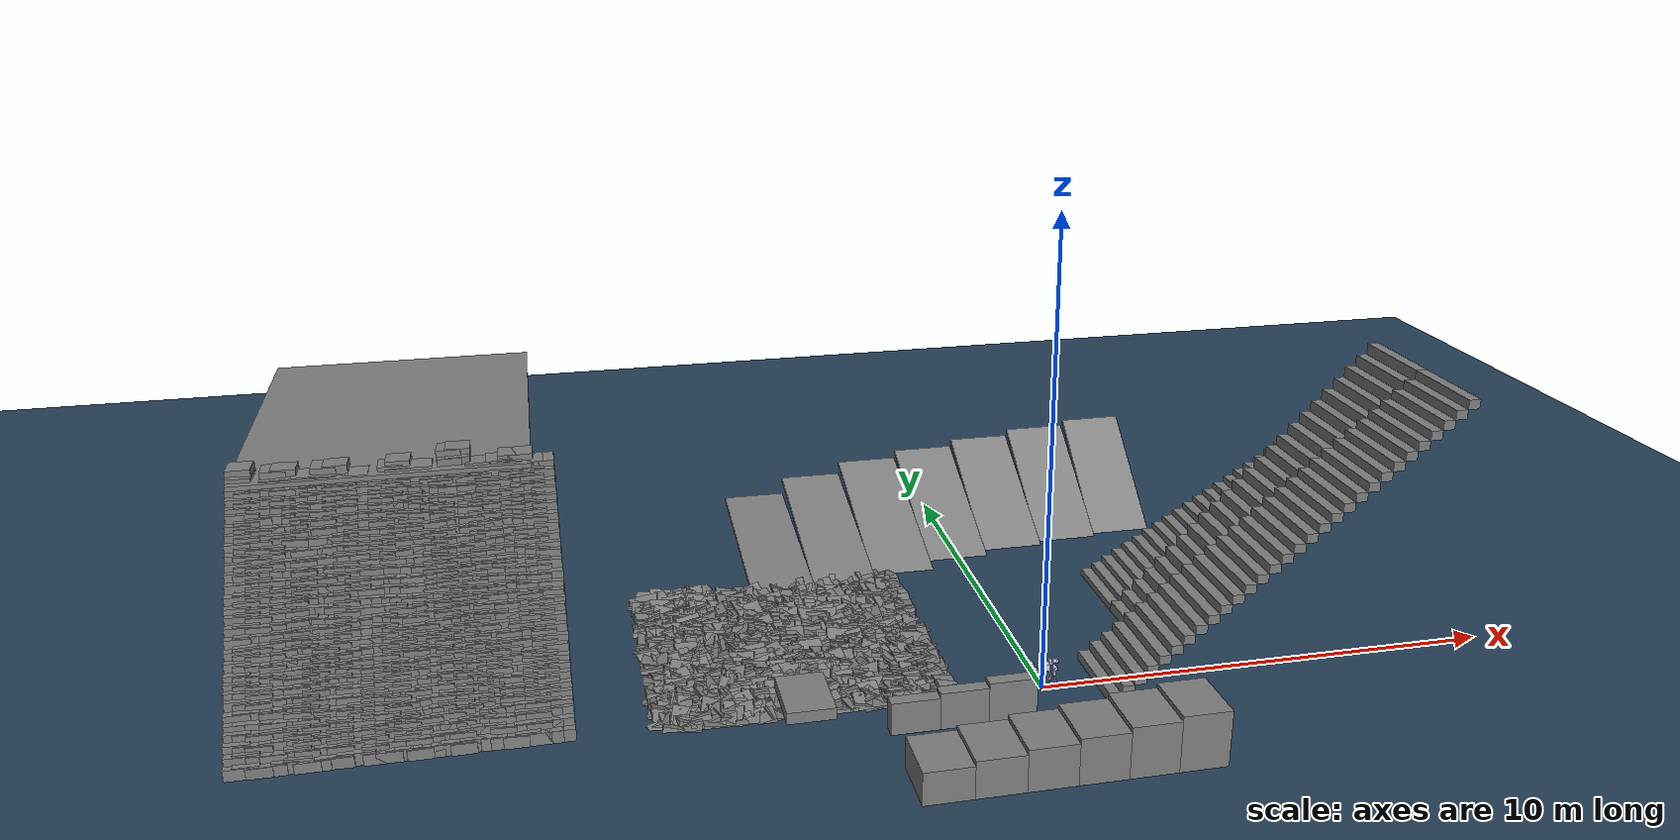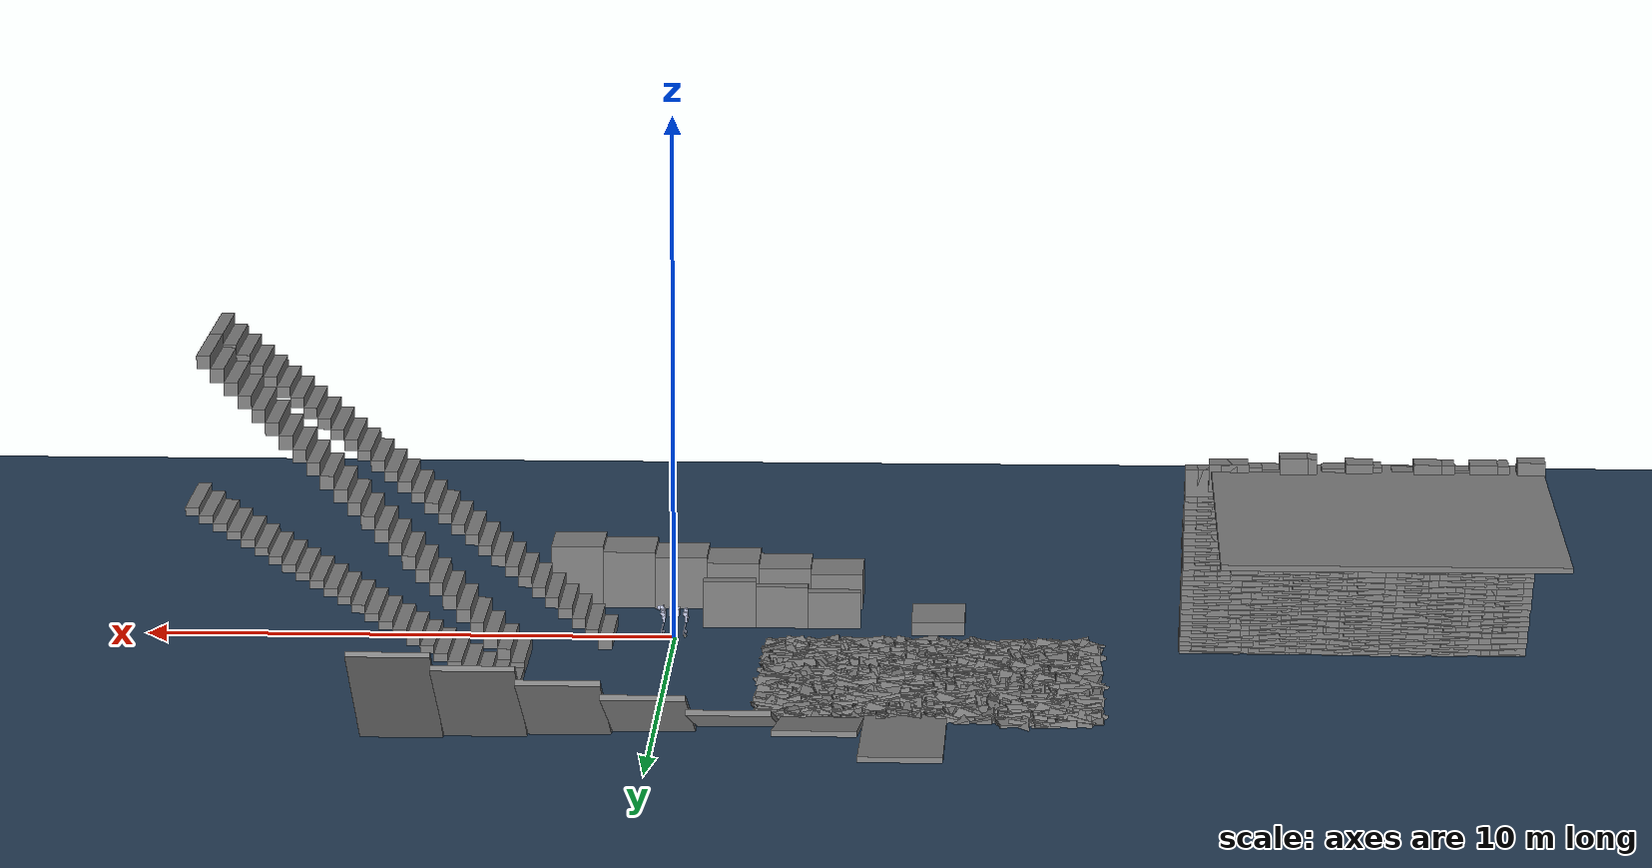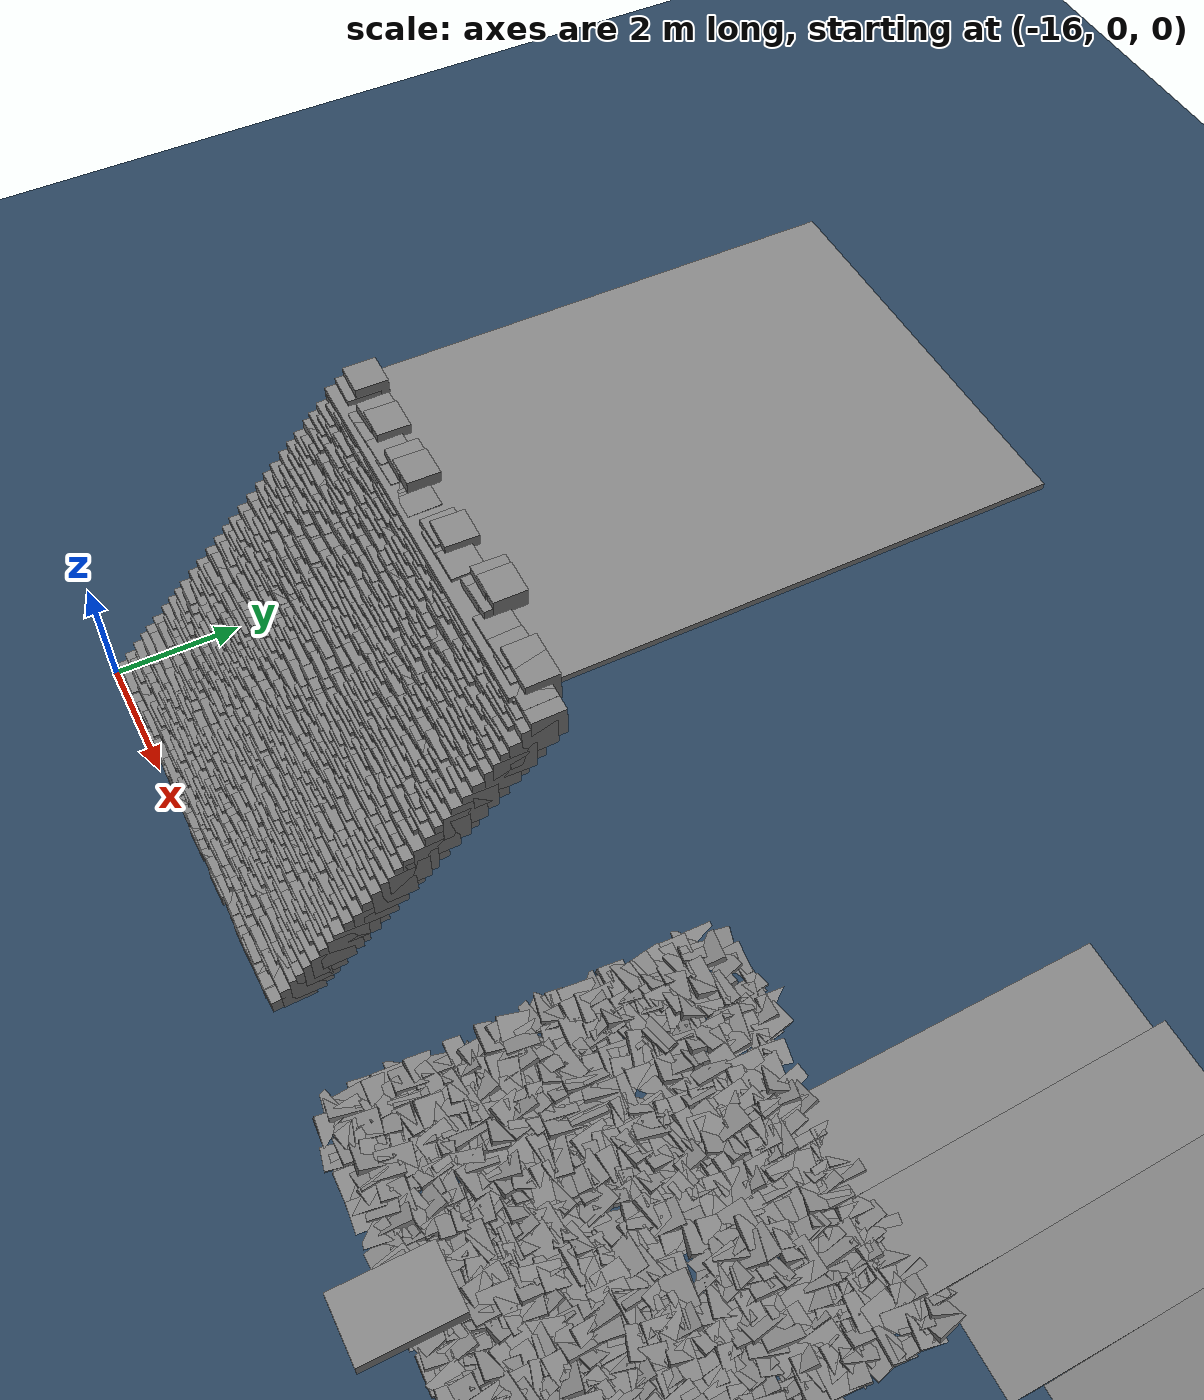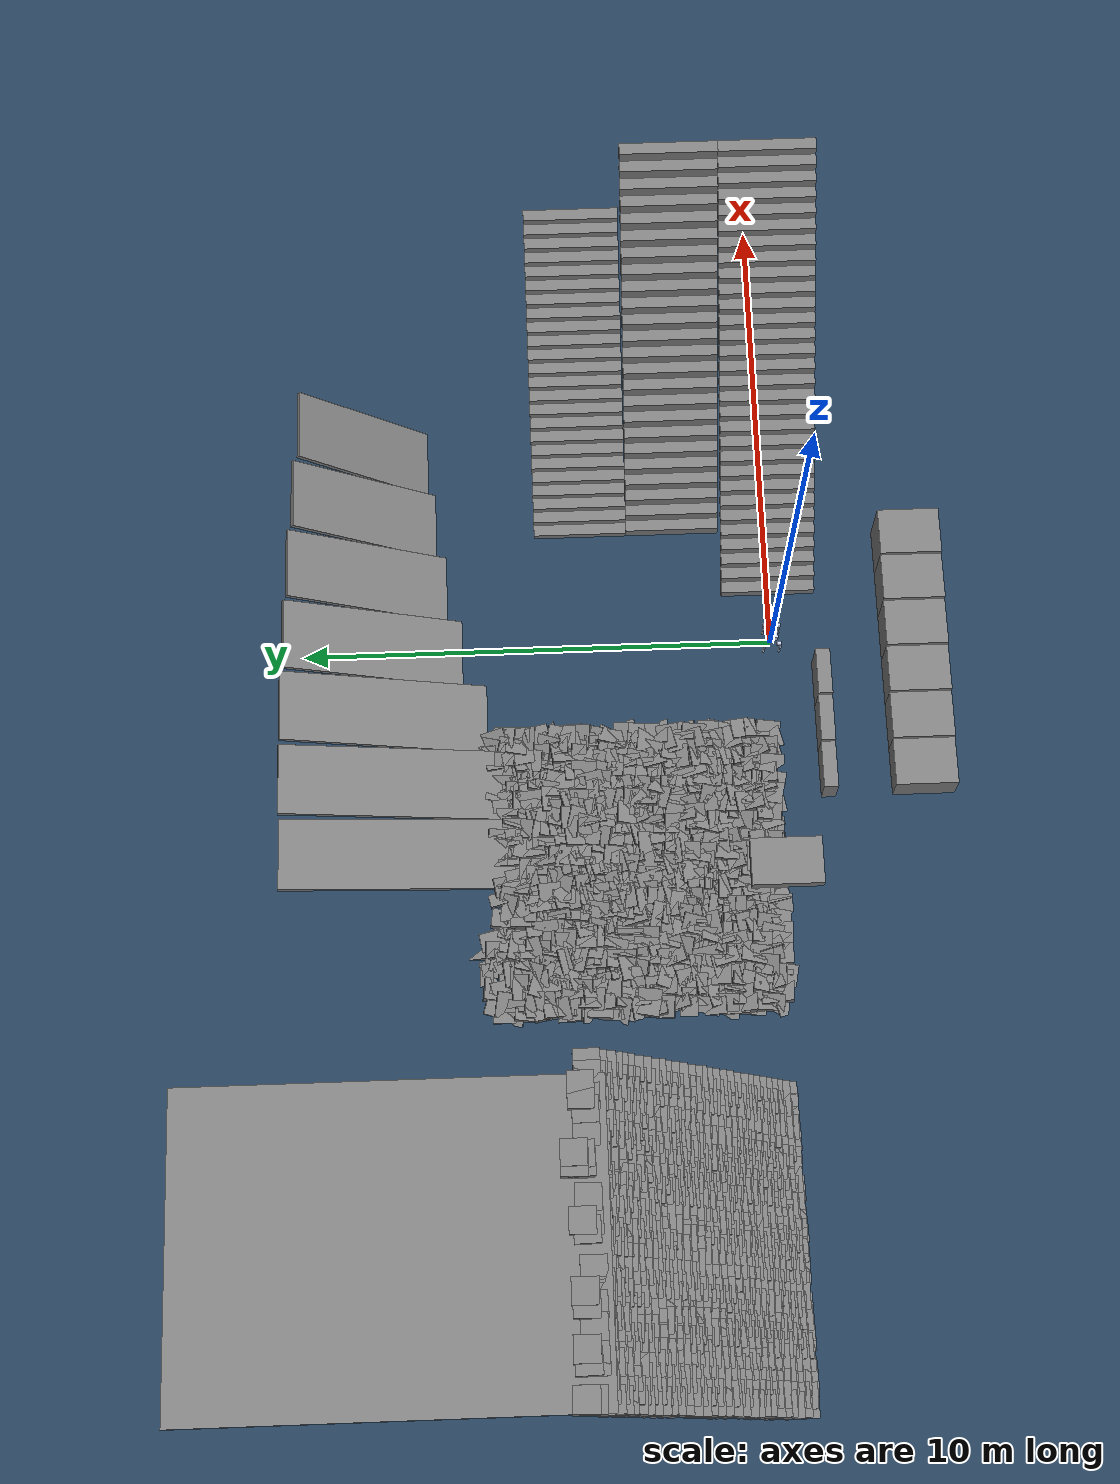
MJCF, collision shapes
<mujoco model="as2 scene">
  <include file="as2.xml" />

  <statistic center="0 0 0.1" extent="3.0" />

  <visual>
    <headlight diffuse="0.6 0.6 0.6" ambient="0.3 0.3 0.3" specular="0 0 0" />
    <rgba haze="0.15 0.25 0.35 1" />
    <global azimuth="-130" elevation="-20" />
  </visual>

  <asset>
    <texture type="skybox" builtin="gradient" rgb1="0.3 0.5 0.7" rgb2="0 0 0" width="512" height="3072" />
    <texture type="2d" name="groundplane" builtin="checker" mark="edge" rgb1="0.2 0.3 0.4" rgb2="0.1 0.2 0.3" markrgb="0.8 0.8 0.8" width="300" height="300" />
    <material name="groundplane" texture="groundplane" texuniform="true" texrepeat="5 5" reflectance="0.2" />
  </asset>

  <worldbody>
    <light pos="0 0 1.5" dir="0 0 -1" directional="true" />
    <geom name="floor" size="0 0 0.05" type="plane" material="groundplane" />
  <geom pos="-5.0 0.0 0.4" type="box" size="0.5 0.75 0.125" quat="1.0 0.0 0.0 0.0" /><geom pos="-4.5 8.0 0.2" type="box" size="2.5 0.75 0.05" quat="0.7065042180310854 0.03532653537124295 -0.03535467804479965 0.7059418336827035" /><geom pos="-3.0 8.0 0.4" type="box" size="2.5 0.75 0.05" quat="0.703854274290177 0.07056477280176178 -0.0706209878068477 0.7032939993232339" /><geom pos="-1.5 8.0 0.5" type="box" size="2.5 0.75 0.05" quat="0.6994450614237634 0.10562663504969944 -0.10571078187807807 0.6988882962338909" /><geom pos="0.0 8.0 0.5" type="box" size="2.5 0.75 0.05" quat="0.6932876001677367 0.14042448571930102 -0.14053635404772424 0.6927357363779519" /><geom pos="1.5 8.0 0.5" type="box" size="2.5 0.75 0.05" quat="0.6853972809684932 0.17487134830626277 -0.17501065852216943 0.6848516979508653" /><geom pos="3.0 8.0 0.5" type="box" size="2.5 0.75 0.05" quat="0.6757938255148319 0.20888112359369654 -0.20904752749409825 0.675255886942771" /><geom pos="4.5 8.0 0.5" type="box" size="2.5 0.75 0.05" quat="0.6645012374440044 0.2423688048553323 -0.2425618865171395 0.6639722878837875" /><geom pos="-3.0 -3.0 0.35" type="box" size="0.5 0.65 0.35" quat="1.0 0.0 0.0 0.0" /><geom pos="-2.0 -3.0 0.4" type="box" size="0.5 0.65 0.4" quat="1.0 0.0 0.0 0.0" /><geom pos="-1.0 -3.0 0.45" type="box" size="0.5 0.65 0.45" quat="1.0 0.0 0.0 0.0" /><geom pos="0.0 -3.0 0.5" type="box" size="0.5 0.65 0.5" quat="1.0 0.0 0.0 0.0" /><geom pos="1.0 -3.0 0.55" type="box" size="0.5 0.65 0.55" quat="1.0 0.0 0.0 0.0" /><geom pos="2.0 -3.0 0.6" type="box" size="0.5 0.65 0.6" quat="1.0 0.0 0.0 0.0" /><geom pos="-3.0 -1.0 0.35" type="box" size="0.5 0.15 0.35" quat="1.0 0.0 0.0 0.0" /><geom pos="-2.0 -1.0 0.4" type="box" size="0.5 0.15 0.4" quat="1.0 0.0 0.0 0.0" /><geom pos="-1.0 -1.0 0.45" type="box" size="0.5 0.15 0.45" quat="1.0 0.0 0.0 0.0" /><geom pos="1.25 0.0 0.1" type="box" size="0.125 1.0 0.1" quat="1.0 0.0 0.0 0.0" /><geom pos="1.5 0.0 0.30000000000000004" type="box" size="0.125 1.0 0.1" quat="1.0 0.0 0.0 0.0" /><geom pos="1.75 0.0 0.5" type="box" size="0.125 1.0 0.1" quat="1.0 0.0 0.0 0.0" /><geom pos="2.0 0.0 0.7" type="box" size="0.125 1.0 0.1" quat="1.0 0.0 0.0 0.0" /><geom pos="2.25 0.0 0.8999999999999999" type="box" size="0.125 1.0 0.1" quat="1.0 0.0 0.0 0.0" /><geom pos="2.5 0.0 1.0999999999999999" type="box" size="0.125 1.0 0.1" quat="1.0 0.0 0.0 0.0" /><geom pos="2.75 0.0 1.2999999999999998" type="box" size="0.125 1.0 0.1" quat="1.0 0.0 0.0 0.0" /><geom pos="3.0 0.0 1.4999999999999998" type="box" size="0.125 1.0 0.1" quat="1.0 0.0 0.0 0.0" /><geom pos="3.25 0.0 1.6999999999999997" type="box" size="0.125 1.0 0.1" quat="1.0 0.0 0.0 0.0" /><geom pos="3.5 0.0 1.8999999999999997" type="box" size="0.125 1.0 0.1" quat="1.0 0.0 0.0 0.0" /><geom pos="3.75 0.0 2.0999999999999996" type="box" size="0.125 1.0 0.1" quat="1.0 0.0 0.0 0.0" /><geom pos="4.0 0.0 2.3" type="box" size="0.125 1.0 0.1" quat="1.0 0.0 0.0 0.0" /><geom pos="4.25 0.0 2.5" type="box" size="0.125 1.0 0.1" quat="1.0 0.0 0.0 0.0" /><geom pos="4.5 0.0 2.7" type="box" size="0.125 1.0 0.1" quat="1.0 0.0 0.0 0.0" /><geom pos="4.75 0.0 2.9000000000000004" type="box" size="0.125 1.0 0.1" quat="1.0 0.0 0.0 0.0" /><geom pos="5.0 0.0 3.1000000000000005" type="box" size="0.125 1.0 0.1" quat="1.0 0.0 0.0 0.0" /><geom pos="5.25 0.0 3.3000000000000007" type="box" size="0.125 1.0 0.1" quat="1.0 0.0 0.0 0.0" /><geom pos="5.5 0.0 3.500000000000001" type="box" size="0.125 1.0 0.1" quat="1.0 0.0 0.0 0.0" /><geom pos="5.75 0.0 3.700000000000001" type="box" size="0.125 1.0 0.1" quat="1.0 0.0 0.0 0.0" /><geom pos="6.0 0.0 3.9000000000000012" type="box" size="0.125 1.0 0.1" quat="1.0 0.0 0.0 0.0" /><geom pos="6.25 0.0 4.100000000000001" type="box" size="0.125 1.0 0.1" quat="1.0 0.0 0.0 0.0" /><geom pos="6.5 0.0 4.300000000000002" type="box" size="0.125 1.0 0.1" quat="1.0 0.0 0.0 0.0" /><geom pos="6.75 0.0 4.500000000000002" type="box" size="0.125 1.0 0.1" quat="1.0 0.0 0.0 0.0" /><geom pos="7.0 0.0 4.700000000000002" type="box" size="0.125 1.0 0.1" quat="1.0 0.0 0.0 0.0" /><geom pos="7.25 0.0 4.900000000000002" type="box" size="0.125 1.0 0.1" quat="1.0 0.0 0.0 0.0" /><geom pos="7.5 0.0 5.100000000000002" type="box" size="0.125 1.0 0.1" quat="1.0 0.0 0.0 0.0" /><geom pos="7.75 0.0 5.3000000000000025" type="box" size="0.125 1.0 0.1" quat="1.0 0.0 0.0 0.0" /><geom pos="8.0 0.0 5.500000000000003" type="box" size="0.125 1.0 0.1" quat="1.0 0.0 0.0 0.0" /><geom pos="8.25 0.0 5.700000000000003" type="box" size="0.125 1.0 0.1" quat="1.0 0.0 0.0 0.0" /><geom pos="8.5 0.0 5.900000000000003" type="box" size="0.125 1.0 0.1" quat="1.0 0.0 0.0 0.0" /><geom pos="2.75 2.0 0.125" type="box" size="0.125 1.0 0.125" quat="1.0 0.0 0.0 0.0" /><geom pos="3.0 2.0 0.375" type="box" size="0.125 1.0 0.125" quat="1.0 0.0 0.0 0.0" /><geom pos="3.25 2.0 0.625" type="box" size="0.125 1.0 0.125" quat="1.0 0.0 0.0 0.0" /><geom pos="3.5 2.0 0.875" type="box" size="0.125 1.0 0.125" quat="1.0 0.0 0.0 0.0" /><geom pos="3.75 2.0 1.125" type="box" size="0.125 1.0 0.125" quat="1.0 0.0 0.0 0.0" /><geom pos="4.0 2.0 1.375" type="box" size="0.125 1.0 0.125" quat="1.0 0.0 0.0 0.0" /><geom pos="4.25 2.0 1.625" type="box" size="0.125 1.0 0.125" quat="1.0 0.0 0.0 0.0" /><geom pos="4.5 2.0 1.875" type="box" size="0.125 1.0 0.125" quat="1.0 0.0 0.0 0.0" /><geom pos="4.75 2.0 2.125" type="box" size="0.125 1.0 0.125" quat="1.0 0.0 0.0 0.0" /><geom pos="5.0 2.0 2.375" type="box" size="0.125 1.0 0.125" quat="1.0 0.0 0.0 0.0" /><geom pos="5.25 2.0 2.625" type="box" size="0.125 1.0 0.125" quat="1.0 0.0 0.0 0.0" /><geom pos="5.5 2.0 2.875" type="box" size="0.125 1.0 0.125" quat="1.0 0.0 0.0 0.0" /><geom pos="5.75 2.0 3.125" type="box" size="0.125 1.0 0.125" quat="1.0 0.0 0.0 0.0" /><geom pos="6.0 2.0 3.375" type="box" size="0.125 1.0 0.125" quat="1.0 0.0 0.0 0.0" /><geom pos="6.25 2.0 3.625" type="box" size="0.125 1.0 0.125" quat="1.0 0.0 0.0 0.0" /><geom pos="6.5 2.0 3.875" type="box" size="0.125 1.0 0.125" quat="1.0 0.0 0.0 0.0" /><geom pos="6.75 2.0 4.125" type="box" size="0.125 1.0 0.125" quat="1.0 0.0 0.0 0.0" /><geom pos="7.0 2.0 4.375" type="box" size="0.125 1.0 0.125" quat="1.0 0.0 0.0 0.0" /><geom pos="7.25 2.0 4.625" type="box" size="0.125 1.0 0.125" quat="1.0 0.0 0.0 0.0" /><geom pos="7.5 2.0 4.875" type="box" size="0.125 1.0 0.125" quat="1.0 0.0 0.0 0.0" /><geom pos="7.75 2.0 5.125" type="box" size="0.125 1.0 0.125" quat="1.0 0.0 0.0 0.0" /><geom pos="8.0 2.0 5.375" type="box" size="0.125 1.0 0.125" quat="1.0 0.0 0.0 0.0" /><geom pos="8.25 2.0 5.625" type="box" size="0.125 1.0 0.125" quat="1.0 0.0 0.0 0.0" /><geom pos="8.5 2.0 5.875" type="box" size="0.125 1.0 0.125" quat="1.0 0.0 0.0 0.0" /><geom pos="2.75 4.0 0.075" type="box" size="0.125 1.0 0.075" quat="1.0 0.0 0.0 0.0" /><geom pos="3.0 4.0 0.22499999999999998" type="box" size="0.125 1.0 0.075" quat="1.0 0.0 0.0 0.0" /><geom pos="3.25 4.0 0.375" type="box" size="0.125 1.0 0.075" quat="1.0 0.0 0.0 0.0" /><geom pos="3.5 4.0 0.525" type="box" size="0.125 1.0 0.075" quat="1.0 0.0 0.0 0.0" /><geom pos="3.75 4.0 0.675" type="box" size="0.125 1.0 0.075" quat="1.0 0.0 0.0 0.0" /><geom pos="4.0 4.0 0.8250000000000001" type="box" size="0.125 1.0 0.075" quat="1.0 0.0 0.0 0.0" /><geom pos="4.25 4.0 0.9750000000000001" type="box" size="0.125 1.0 0.075" quat="1.0 0.0 0.0 0.0" /><geom pos="4.5 4.0 1.125" type="box" size="0.125 1.0 0.075" quat="1.0 0.0 0.0 0.0" /><geom pos="4.75 4.0 1.275" type="box" size="0.125 1.0 0.075" quat="1.0 0.0 0.0 0.0" /><geom pos="5.0 4.0 1.4249999999999998" type="box" size="0.125 1.0 0.075" quat="1.0 0.0 0.0 0.0" /><geom pos="5.25 4.0 1.5749999999999997" type="box" size="0.125 1.0 0.075" quat="1.0 0.0 0.0 0.0" /><geom pos="5.5 4.0 1.7249999999999996" type="box" size="0.125 1.0 0.075" quat="1.0 0.0 0.0 0.0" /><geom pos="5.75 4.0 1.8749999999999996" type="box" size="0.125 1.0 0.075" quat="1.0 0.0 0.0 0.0" /><geom pos="6.0 4.0 2.0249999999999995" type="box" size="0.125 1.0 0.075" quat="1.0 0.0 0.0 0.0" /><geom pos="6.25 4.0 2.1749999999999994" type="box" size="0.125 1.0 0.075" quat="1.0 0.0 0.0 0.0" /><geom pos="6.5 4.0 2.3249999999999993" type="box" size="0.125 1.0 0.075" quat="1.0 0.0 0.0 0.0" /><geom pos="6.75 4.0 2.474999999999999" type="box" size="0.125 1.0 0.075" quat="1.0 0.0 0.0 0.0" /><geom pos="7.0 4.0 2.624999999999999" type="box" size="0.125 1.0 0.075" quat="1.0 0.0 0.0 0.0" /><geom pos="7.25 4.0 2.774999999999999" type="box" size="0.125 1.0 0.075" quat="1.0 0.0 0.0 0.0" /><geom pos="7.5 4.0 2.924999999999999" type="box" size="0.125 1.0 0.075" quat="1.0 0.0 0.0 0.0" /><geom pos="7.75 4.0 3.074999999999999" type="box" size="0.125 1.0 0.075" quat="1.0 0.0 0.0 0.0" /><geom pos="8.0 4.0 3.2249999999999988" type="box" size="0.125 1.0 0.075" quat="1.0 0.0 0.0 0.0" /><geom pos="8.25 4.0 3.3749999999999987" type="box" size="0.125 1.0 0.075" quat="1.0 0.0 0.0 0.0" /><geom pos="8.5 4.0 3.5249999999999986" type="box" size="0.125 1.0 0.075" quat="1.0 0.0 0.0 0.0" /><geom pos="-7.83693785030696 0.16977869680186314 -0.25" type="box" size="0.24801114595267118 0.2611944734059796 0.23122119248761286" quat="0.9823002456152552 0.10641093759794543 -0.0330192214570903 0.1505744694099999" /><geom pos="-7.83693785030696 0.4085779426700082 -0.25" type="box" size="0.24544051684591484 0.24705241308825174 0.26538900944772964" quat="0.985678161306771 -0.06420836216673659 -0.14274870552268243 -0.06275870953395003" /><geom pos="-7.83693785030696 0.6146027854959939 -0.25" type="box" size="0.2502217724676404 0.23125328662694078 0.2592769427205986" quat="0.9807533585004458 0.1401613596516283 0.13541049379665357 0.011901311711295326" /><geom pos="-7.83693785030696 0.7802358306850159 -0.25" type="box" size="0.24248100955125074 0.23648025098902162 0.26451650167062746" quat="0.9976312168529096 -0.043157999011791404 -0.025744570893388604 -0.04697402847741973" /><geom pos="-7.83693785030696 0.935957809109978 -0.25" type="box" size="0.251023366326564 0.26741122864955313 0.27065158099667125" quat="0.9820124261625393 -0.14089364756458136 0.12495290188997775 0.0136874850715587" /><geom pos="-7.83693785030696 1.1104109266584443 -0.25" type="box" size="0.269970616992345 0.2434226108294178 0.24202582845959478" quat="0.9915954220666168 -0.08265151295221947 0.09947417102310081 -0.0034836249086159354" /><geom pos="-7.83693785030696 1.352887678641046 -0.25" type="box" size="0.26484200616585435 0.2720256957821768 0.27260070238366024" quat="0.9909075760456938 -0.07617298006513089 -0.10752880413838642 -0.027155278010229" /><geom pos="-7.83693785030696 1.558419653705857 -0.25" type="box" size="0.23638562126672433 0.23704498340812552 0.2691343407786604" quat="0.9916681237663025 -0.12481269006644907 0.030346079453480976 0.009759106823962409" /><geom pos="-7.83693785030696 1.7510381724747028 -0.25" type="box" size="0.22829866196179893 0.22937370303187407 0.26275595079003505" quat="0.9907710297949331 -0.027866681670564473 -0.12813920776313725 -0.03430099132087487" /><geom pos="-7.83693785030696 1.9994950555744477 -0.25" type="box" size="0.22948701710731712 0.24820661422256396 0.23032235107800075" quat="0.9943334126977388 -0.044923423486574195 -0.09070859303601926 0.032479248213897124" /><geom pos="-7.83693785030696 2.1696726737277316 -0.25" type="box" size="0.23876537311783547 0.23654739185523516 0.24118204548647898" quat="0.9974529506319549 -0.06909898561074977 -0.0005602978535172427 -0.0176812762403588" /><geom pos="-7.83693785030696 2.3561039048012624 -0.25" type="box" size="0.22608958571867147 0.26257873713450386 0.23685655397688496" quat="0.9823608081152162 0.019824194643864 -0.11278818027634802 0.14782784032749394" /><geom pos="-7.83693785030696 2.5998178130191345 -0.25" type="box" size="0.23407612417830306 0.22797785695285747 0.26650201485643366" quat="0.9906996393200406 -0.12577478206573373 -0.03439956998127579 -0.0388792802474858" /><geom pos="-7.83693785030696 2.803433081489542 -0.25" type="box" size="0.252030209887001 0.2643758837221236 0.2307996653697913" quat="0.9821776885140564 -0.13754965740071678 0.114295524136091 0.057823983748845155" /><geom pos="-7.83693785030696 2.962377676580121 -0.25" type="box" size="0.23436405461284715 0.25008485135256453 0.26494498289051616" quat="0.9910679421356599 -0.03220761032254161 0.07600077487743467 -0.10474199791071731" /><geom pos="-7.83693785030696 3.113315700691222 -0.25" type="box" size="0.22866861661232868 0.2698197707984957 0.2326623975274191" quat="0.9844232447270213 0.1469221820626165 -0.04192417073740849 0.08698914626011076" /><geom pos="-7.83693785030696 3.3222897481333016 -0.25" type="box" size="0.26177805182536873 0.2655381623996063 0.26218863409405746" quat="0.989609686419811 0.060693891843464874 -0.05814001164004601 -0.11665615750346041" /><geom pos="-7.83693785030696 3.5386689046334174 -0.25" type="box" size="0.2690178908556615 0.26403189522202825 0.2669930896948119" quat="0.9802244464580541 -0.11110934497002926 -0.1110536981963896 -0.1203404509848483" /><geom pos="-7.83693785030696 3.750995978899644 -0.25" type="box" size="0.24829588252544552 0.25721797506889194 0.2530294062594908" quat="0.996780065810408 -0.07119763110511329 -0.02945576376520214 -0.02219810147350321" /><geom pos="-7.83693785030696 3.954487444803869 -0.25" type="box" size="0.25927531977930535 0.2654182037652759 0.2552319087215636" quat="0.9944605896021945 0.0008263929975027133 0.09597336856812028 -0.042855166880519636" /><geom pos="-7.83693785030696 4.119643425975576 -0.25" type="box" size="0.26030230200444465 0.22627857963610548 0.25628483786576556" quat="0.9865869868021139 0.124186887306294 -0.1013986322127017 -0.03069286365415156" /><geom pos="-7.83693785030696 4.288822428213784 -0.25" type="box" size="0.23316215301450607 0.2569769513230783 0.230534345935304" quat="0.9831952214194948 0.14349114346989092 0.0754794906042552 -0.08390646471932492" /><geom pos="-7.83693785030696 4.524877598781398 -0.25" type="box" size="0.27485199047919207 0.2422147942893489 0.27380850455873723" quat="0.9925020857125607 -0.11944481804418797 0.021110348005276877 0.01506315059023517" /><geom pos="-7.83693785030696 4.750500882975568 -0.25" type="box" size="0.24533826504464756 0.26009080081198965 0.24264103570828893" quat="0.9855362748149269 -0.14128094383284584 -0.03541953893735233 0.08662218073381972" /><geom pos="-7.83693785030696 4.90615130513383 -0.25" type="box" size="0.24126834281777282 0.27329558094492234 0.26390490664317834" quat="0.9847116894522207 0.1113307694109009 0.1193977720927468 0.06076611274236447" /><geom pos="-7.83693785030696 5.089666437989327 -0.25" type="box" size="0.25846807109894554 0.24566616521253723 0.27062311701261366" quat="0.9922984889515214 -0.0053626829912142935 0.08682353119168995 0.08818517385064543" /><geom pos="-7.83693785030696 5.262873625340952 -0.25" type="box" size="0.22508354120964608 0.23545296020916426 0.2560170028246994" quat="0.9932912081145295 0.037208290155204486 0.10919914417846174 -0.007979093732757608" /><geom pos="-7.83693785030696 5.486432492602551 -0.25" type="box" size="0.268297516635572 0.24250258003592837 0.27047853390877025" quat="0.9920240571710237 0.08515787129197425 0.07927301059302604 -0.048499450950281284" /><geom pos="-7.83693785030696 5.685985554111983 -0.25" type="box" size="0.2701015223181793 0.23151815550197333 0.26517141521828264" quat="0.9882659870752275 -0.10223679518846654 -0.08330925908820923 -0.0770554595729008" /><geom pos="-7.83693785030696 5.899283670746546 -0.25" type="box" size="0.26509702465790524 0.23236835882841667 0.22853951427372904" quat="0.999348895034152 -0.014027165141575232 0.03307791892025718 -0.003297864766145969" /><geom pos="-7.654016701338118 0.18763950685690184 -0.25" type="box" size="0.23607186259864646 0.24819213554600128 0.24890573007380318" quat="0.9861839729991086 -0.10036193860766197 0.1267300129791772 -0.036168446039362596" /><geom pos="-7.654016701338118 0.4214937164240058 -0.25" type="box" size="0.26657909720016726 0.27395423041449474 0.25345327535896267" quat="0.99215640308391 0.02311525580318548 0.10993718807798221 0.05481944405279509" /><geom pos="-7.654016701338118 0.6310159967677322 -0.25" type="box" size="0.25388399368328834 0.22630681271442385 0.24906854387872346" quat="0.9920747814160815 0.07578814144363186 -0.1001252156534855 0.004327457116664249" /><geom pos="-7.654016701338118 0.8584711318311056 -0.25" type="box" size="0.23383230361241134 0.25604855233120793 0.27320261657288686" quat="0.9961085381916592 -0.07084304556806821 -0.03261563731596892 0.0410519577948506" /><geom pos="-7.654016701338118 1.08802005003045 -0.25" type="box" size="0.2626973749358855 0.237994330412986 0.25098011784584173" quat="0.9868920969548274 0.12555588765176964 0.0976391568383497 0.02731854857008157" /><geom pos="-7.654016701338118 1.2920106302570442 -0.25" type="box" size="0.24765397938545408 0.252248000234982 0.24757504337107286" quat="0.9918644229521691 0.012864481438167446 -0.12037687621560322 -0.03935580353215114" /><geom pos="-7.654016701338118 1.5070999447928735 -0.25" type="box" size="0.23172348307298932 0.27433374682866457 0.27453731425248473" quat="0.9846126194027591 0.0845927298882915 0.05400405021983648 0.14305810820340512" /><geom pos="-7.654016701338118 1.75324504102493 -0.25" type="box" size="0.23104727214754556 0.2610817622512629 0.24269190363244802" quat="0.9934963205759076 0.1073816326790737 0.037137806355688384 -0.007418173926073156" /><geom pos="-7.654016701338118 1.9183631772165406 -0.25" type="box" size="0.2496603570270316 0.23579909404685254 0.22994727675091217" quat="0.9827168035648124 -0.13175162834650794 -0.12801233937128453 -0.022848049984449576" /><geom pos="-7.654016701338118 2.120213704249036 -0.25" type="box" size="0.24237850609064712 0.24268496399227113 0.256928971114699" quat="0.9800941556433479 0.13810739877858483 -0.1423246503806006 -0.009245883971027005" /><geom pos="-7.654016701338118 2.30657263294978 -0.25" type="box" size="0.2595740240928517 0.23710848757165348 0.2655870770046326" quat="0.9832219706008636 -0.14959789399140452 0.021492835486397327 0.10214247237974015" /><geom pos="-7.654016701338118 2.530971477397082 -0.25" type="box" size="0.23078443942768465 0.225730754386981 0.22885138657236406" quat="0.9930010163125259 0.08197482905015513 0.031221717401598122 0.07908421692716579" /><geom pos="-7.654016701338118 2.763577777452781 -0.25" type="box" size="0.2650106532962496 0.24188801730320697 0.24087702983469753" quat="0.9883408200629178 0.03560169224647787 -0.11339198425372632 -0.09516932706260355" /><geom pos="-7.654016701338118 2.942797490798852 -0.25" type="box" size="0.25589318889540924 0.24201540259994686 0.2596549849684994" quat="0.988801237091153 -0.006892466885860541 -0.13817077208237374 -0.05597718436464191" /><geom pos="-7.654016701338118 3.1907144627745554 -0.25" type="box" size="0.23035802346811945 0.2542951952391227 0.23567761776956125" quat="0.9899193200584252 0.019857738975063988 0.12883266697232112 0.05538550260367999" /><geom pos="-7.654016701338118 3.4339271602007804 -0.25" type="box" size="0.2692750704894537 0.25207686214747427 0.25264058441258347" quat="0.9808575461655973 0.13545878915463166 0.13783534022914665 -0.023891621014060928" /><geom pos="-7.654016701338118 3.622695861538246 -0.25" type="box" size="0.25875065667415087 0.23261191157170277 0.2544283827731686" quat="0.9969765186479794 0.013502000401481782 0.05775399263581478 -0.05019953769046222" /><geom pos="-7.654016701338118 3.8427212705761913 -0.25" type="box" size="0.2735977729247894 0.24638711786744855 0.2618260683963444" quat="0.9899958535189796 -0.10239429443565688 0.09202814180454165 0.03089400586285313" /><geom pos="-7.654016701338118 4.030712851776877 -0.25" type="box" size="0.23222073168275698 0.24470322818728216 0.2685719573888144" quat="0.9894053975747384 -0.13409378179267406 0.010891041975837373 -0.0545637438157707" /><geom pos="-7.654016701338118 4.183591140835161 -0.25" type="box" size="0.27055556527469554 0.23691624301272657 0.262208437193245" quat="0.9888146105054078 0.012057063719596538 0.14865335251012937 0.0015729122670737285" /><geom pos="-7.654016701338118 4.356967967718187 -0.25" type="box" size="0.2647507588367676 0.23130591541822138 0.25270979012236516" quat="0.9842259688785296 -0.08878160841854892 -0.0840921679685606 0.1278498161049981" /><geom pos="-7.654016701338118 4.544093076471046 -0.25" type="box" size="0.2705557358323455 0.2400177793962455 0.24964488124907894" quat="0.9823463585342976 0.030793706753867847 -0.1439753390974408 -0.11540572442707571" /><geom pos="-7.654016701338118 4.704063320269476 -0.25" type="box" size="0.23959102240349822 0.26452904006734856 0.2593993338795493" quat="0.9977016604264466 -0.02819778267786849 -0.05569931519019931 0.02634137660994318" /><geom pos="-7.654016701338118 4.905614169040912 -0.25" type="box" size="0.2258757890599567 0.2746117189043927 0.2438710546056334" quat="0.992950134108273 0.08761787120986647 0.0068795495121342564 0.07953497103490524" /><geom pos="-7.654016701338118 5.061028264587119 -0.25" type="box" size="0.2481173563751735 0.2633826759816237 0.23672952131827674" quat="0.9833527394680045 -0.12134160418109378 -0.13317277553023238 0.023635074214052715" /><geom pos="-7.654016701338118 5.2996865159683155 -0.25" type="box" size="0.23773218552105552 0.26050703444756623 0.265169986625883" quat="0.9927540856816863 -0.10208409666606695 -0.060371117820667244 -0.01932590756666527" /><geom pos="-7.654016701338118 5.467175930181847 -0.25" type="box" size="0.2340283097546072 0.2402585415904687 0.27133761085627783" quat="0.9868760153705677 -0.1202591470124358 -0.04068632584302802 0.09979023366816477" /><geom pos="-7.654016701338118 5.687373621127488 -0.25" type="box" size="0.240035112813461 0.2628126185793666 0.2616968119259702" quat="0.9907987285541595 -0.11966666609849293 0.05370869944981361 -0.03336381458620563" /><geom pos="-7.654016701338118 5.864803523191517 -0.25" type="box" size="0.25897676062277475 0.2739439573856684 0.2600286138371331" quat="0.9811301700175299 0.12473062652225939 -0.1281878451353206 -0.07344206320835116" /><geom pos="-7.654016701338118 6.102256727813647 -0.25" type="box" size="0.26624491257525496 0.22607344696178566 0.25775596469501527" quat="0.9826054925815727 0.11516548123918924 -0.040291871544685595 -0.1399997248815056" /><geom pos="-7.409406116261958 0.2032445392809781 -0.25" type="box" size="0.2589749565144339 0.2543815217018624 0.23512469914579331" quat="0.9818910909654626 0.12855992462487842 0.029606332855273913 -0.1359621135388894" /><geom pos="-7.409406116261958 0.4298417701105718 -0.25" type="box" size="0.24403843839000003 0.2654221881900344 0.2494512867417653" quat="0.9796338121993758 -0.06379380270377544 0.13938876501213687 0.12968699595834873" /><geom pos="-7.409406116261958 0.5903096991802712 -0.25" type="box" size="0.26711649137144455 0.2566026852480033 0.273511406826337" quat="0.9850699768936697 0.11167437094889424 0.09591813163889146 -0.08925070038255681" /><geom pos="-7.409406116261958 0.8355285263096652 -0.25" type="box" size="0.26027393009356353 0.2485903951646691 0.2639039503400946" quat="0.9879207330289816 0.049281974748884495 -0.08379252135726861 -0.1206761185194539" /><geom pos="-7.409406116261958 1.0101331103523497 -0.25" type="box" size="0.24587855372526837 0.2667056519311701 0.24053297906496665" quat="0.991462841587535 0.0913680004142344 0.021429556412363736 -0.09052124813238199" /><geom pos="-7.409406116261958 1.1926475335661753 -0.25" type="box" size="0.24517660579726702 0.2277178514066263 0.2408516885697498" quat="0.984977494465477 0.06582396449515385 0.14060256885903566 -0.0756138791816146" /><geom pos="-7.409406116261958 1.4205494680129451 -0.25" type="box" size="0.2610119464104082 0.2613802467186127 0.23472724350678478" quat="0.9924993753371261 -0.040830451908490766 0.06857907659487467 -0.09260007778483366" /><geom pos="-7.409406116261958 1.5836895956340307 -0.25" type="box" size="0.25710198620202257 0.2347214340787613 0.22883378406278487" quat="0.9908228782765316 -0.11865959173026641 0.03734327673387078 -0.052871588372144236" /><geom pos="-7.409406116261958 1.7956001218400361 -0.25" type="box" size="0.25299299901483907 0.24596481780109625 0.2566815584467244" quat="0.9866020039327021 0.13063736915338958 0.07493306129692397 0.06273276609020369" /><geom pos="-7.409406116261958 1.957148128798646 -0.25" type="box" size="0.2674753038015137 0.24371456478130457 0.2617116335554093" quat="0.9910656367555359 -0.09412789071880918 -0.03405943478230817 -0.08814078927194419" /><geom pos="-7.409406116261958 2.186687425719576 -0.25" type="box" size="0.246843875698972 0.22876412070409335 0.2695717731506866" quat="0.9957390852235362 -0.023813821872727226 0.05679584685034388 -0.06863532491773025" /><geom pos="-7.409406116261958 2.391310792444346 -0.25" type="box" size="0.24485776144860869 0.2691392726046886 0.253876796993463" quat="0.9836006002673844 -0.10458829971878633 0.07389566216013504 -0.12700621177520724" /><geom pos="-7.409406116261958 2.564565238557777 -0.25" type="box" size="0.2290481693468448 0.26501243802044583 0.24102135531480606" quat="0.9864568755302331 -0.130918033099442 0.09311952526893419 -0.03304626063855719" /><geom pos="-7.409406116261958 2.798410410637097 -0.25" type="box" size="0.2598307594324022 0.2746246751979788 0.26560893075807507" quat="0.9858387805713947 0.1050331483434056 -0.12273126584326563 0.04502191527564152" /><geom pos="-7.409406116261958 2.965125477814278 -0.25" type="box" size="0.25931386309914056 0.2281689506091193 0.24415960175674012" quat="0.9968914266054475 -0.010574178874344456 0.00996381920629257 0.07743637781116683" /><geom pos="-7.409406116261958 3.2094955002802807 -0.25" type="box" size="0.22995297283786442 0.2484777479222182 0.2579987655840711" quat="0.9903022728868464 -0.08854534974666867 -0.09734957673021515 0.044544239401226204" /><geom pos="-7.409406116261958 3.4452435162745365 -0.25" type="box" size="0.2690494999727853 0.2494514019659905 0.25663476754544373" quat="0.9920802500504396 -0.01515482152480918 0.0814887633696991 -0.09437526311955687" /><geom pos="-7.409406116261958 3.6838795690664043 -0.25" type="box" size="0.2429653831677761 0.25047240896537454 0.27361986562654894" quat="0.9922324130958413 -0.12027104227891751 0.020382490054865875 -0.02437763094130557" /><geom pos="-7.409406116261958 3.8893400859297897 -0.25" type="box" size="0.2469536420598147 0.24860214422536775 0.2392872878073516" quat="0.9823489618700837 0.1017406395602851 -0.09893647228380648 0.12186440754653526" /><geom pos="-7.409406116261958 4.086366000153047 -0.25" type="box" size="0.2362721630542465 0.2733434511037457 0.2691917303588216" quat="0.9902058503967424 0.11452995464178761 0.04275206945773394 0.06743533114692234" /><geom pos="-7.409406116261958 4.294080292511991 -0.25" type="box" size="0.2516075865038013 0.26797998968133546 0.26130282524780557" quat="0.9804059865594434 -0.13914256065793543 -0.13175959151221783 -0.045638354226356904" /><geom pos="-7.409406116261958 4.520820363666387 -0.25" type="box" size="0.2744253997257702 0.2629011926724722 0.2532434834449325" quat="0.9913824369042078 -0.09144648803667293 0.07647365041212137 0.05431560011891339" /><geom pos="-7.409406116261958 4.715958893069532 -0.25" type="box" size="0.26785737718622205 0.2454087075028505 0.23972756566412312" quat="0.9879763645050685 0.031153688665238183 -0.12248114193710682 -0.089053471193883" /><geom pos="-7.409406116261958 4.9486993153365235 -0.25" type="box" size="0.23289402089970426 0.23363071320451156 0.25857927238950046" quat="0.9835361611407956 -0.1221190112318203 0.002248709900171602 0.1331859982429618" /><geom pos="-7.409406116261958 5.173676458960878 -0.25" type="box" size="0.24772453936784228 0.2710546159528537 0.2718574240616376" quat="0.9781747638818858 0.11872141908576238 0.09858161372726829 -0.13914388736055308" /><geom pos="-7.409406116261958 5.341133609318456 -0.25" type="box" size="0.27471253134922113 0.22935176674573932 0.22628313820000984" quat="0.9921960185980248 0.12410605387118614 -0.012022002882172308 -0.0004685268954193701" /><geom pos="-7.409406116261958 5.533786045468555 -0.25" type="box" size="0.25924668212761237 0.2662363829728982 0.2679832994211542" quat="0.9916640828512704 0.1114772552108261 0.06459500142545047 -0.0016291544600624697" /><geom pos="-7.409406116261958 5.728288696118204 -0.25" type="box" size="0.24706364634761208 0.24986798809035501 0.22853470009259955" quat="0.9949221730535694 0.03204265280878152 0.08367991552286348 0.04583459070861311" /><geom pos="-7.409406116261958 5.9262845066138405 -0.25" type="box" size="0.24443495011687047 0.2741327248055998 0.25272095249741344" quat="0.9869328186848622 0.09088925620113135 -0.07413287407252912 0.11048561667341049" /><geom pos="-7.409406116261958 6.137267571182579 -0.25" type="box" size="0.2396821641427552 0.2465405364192775 0.267486782272967" quat="0.9860144679612903 0.1426226264040898 0.07606842229249589 -0.040593725359265614" /><geom pos="-7.256714378213218 0.15422103588703198 -0.25" type="box" size="0.23125953135791485 0.2632836311422057 0.2450099088654315" quat="0.9944324246612065 -0.0036178514184609448 -0.04019232504811272 -0.09734290390559887" /><geom pos="-7.256714378213218 0.3216402938149491 -0.25" type="box" size="0.25364032324983965 0.2557603322199722 0.2294410026873161" quat="0.990628654940433 -0.10139253307530519 -0.09106477537865472 -0.009034873143351886" /><geom pos="-7.256714378213218 0.562748374571179 -0.25" type="box" size="0.2267603384917862 0.24729140947863598 0.24769143720244263" quat="0.9959815596674325 0.018499333787677645 0.07080023441755527 0.05163171756062607" /><geom pos="-7.256714378213218 0.812289402204867 -0.25" type="box" size="0.240259099190572 0.23747650895927094 0.22742854024541026" quat="0.9919246210710826 0.09927007232251389 -0.035213332723396884 -0.07064715176554101" /><geom pos="-7.256714378213218 1.0180696408505694 -0.25" type="box" size="0.27478743355579227 0.2605764434952367 0.23174131266995524" quat="0.9812155753758209 0.14305599633313754 0.11592927708570125 -0.05754458503991984" /><geom pos="-7.256714378213218 1.2279834136025654 -0.25" type="box" size="0.22587079830776022 0.23433229732928815 0.2562927700987433" quat="0.9910013801713686 -0.1009843894362933 -0.0271952384690608 0.08353943136766274" /><geom pos="-7.256714378213218 1.4708921854002108 -0.25" type="box" size="0.24688784289211366 0.26754934682360504 0.26198695621792417" quat="0.9874873916400043 -0.1046267267274555 0.1160490953215042 -0.021319166995433726" /><geom pos="-7.256714378213218 1.6725483415282294 -0.25" type="box" size="0.2585224757522325 0.23580170048487997 0.23093394261410619" quat="0.9936584617410451 0.026573191947591855 0.10387341718723171 0.03386798018754737" /><geom pos="-7.256714378213218 1.8378684444874414 -0.25" type="box" size="0.2520126488348103 0.2643261363582795 0.261046822269789" quat="0.9890019420290853 0.04121311869560006 -0.04144821078984507 -0.13586273710035734" /><geom pos="-7.256714378213218 1.9949772736273312 -0.25" type="box" size="0.2679424142183096 0.2638619970390259 0.2340113358895102" quat="0.9943961759549507 0.05267444961676052 -0.07574629057313267 -0.05161537627638464" /><geom pos="-7.256714378213218 2.175616807689396 -0.25" type="box" size="0.22809654050070427 0.23892228598810447 0.27477070175789076" quat="0.9846108861655503 0.10048305884132326 -0.10155904407593017 0.10064948234622688" /><geom pos="-7.256714378213218 2.3727233261037464 -0.25" type="box" size="0.26894580496872345 0.23717440409481738 0.2431205642672996" quat="0.9947857300955466 -0.026823054174566454 -0.019053153304838203 0.09653420280999328" /><geom pos="-7.256714378213218 2.5392158788276826 -0.25" type="box" size="0.2572545369593275 0.25654340452792235 0.26216566048442147" quat="0.9817289826530807 0.10667851928522093 0.054503206047662636 -0.1478421410579037" /><geom pos="-7.256714378213218 2.762642303963338 -0.25" type="box" size="0.23434051406506506 0.25856367724954826 0.23357566959682471" quat="0.9856383462049115 0.1252639871208368 0.0826842472768403 0.0773905632057245" /><geom pos="-7.256714378213218 2.9251603875790204 -0.25" type="box" size="0.2498972190620906 0.2354377874360235 0.23771582621068663" quat="0.9955361040404321 -0.01554037953141399 -0.081597939272106 -0.044812257949842935" /><geom pos="-7.256714378213218 3.095821925430675 -0.25" type="box" size="0.2642967940571729 0.23286540915891574 0.2689401465764949" quat="0.9981047899468845 0.05011842544972131 -0.03538489524947292 0.004783398761433823" /><geom pos="-7.256714378213218 3.253624453310355 -0.25" type="box" size="0.2466403217398164 0.23881430293105713 0.22966126109843785" quat="0.9915948130487411 -0.11906686448986067 0.03926929697331467 0.03194887839357465" /><geom pos="-7.256714378213218 3.4127150510980475 -0.25" type="box" size="0.26628739009299635 0.22521350389983172 0.25704699299322953" quat="0.9980094568118801 -0.01500789651098631 -0.05625547024141258 -0.024232400299799006" /><geom pos="-7.256714378213218 3.5770605283209105 -0.25" type="box" size="0.23035912104979714 0.26679499035202586 0.2632422207599838" quat="0.9992108075120687 -0.025467070040470403 -0.02964537428140899 0.007095229266868078" /><geom pos="-7.256714378213218 3.7778303807349176 -0.25" type="box" size="0.2350299964403552 0.2564930339561002 0.24656116569141517" quat="0.9831592780546206 -0.025648418651865856 -0.1494364349438123 0.10202325473665061" /><geom pos="-7.256714378213218 4.016461375129723 -0.25" type="box" size="0.24047120919173737 0.2672329625225087 0.23611994136961578" quat="0.9904869415556823 -0.0498668463205095 0.11430864856809923 -0.0581588265721695" /><geom pos="-7.256714378213218 4.197031682547916 -0.25" type="box" size="0.258985838008387 0.23166922724201564 0.24268982690987095" quat="0.995336727469953 -0.07775478523513482 0.04168798463306585 -0.0390013366396127" /><geom pos="-7.256714378213218 4.364021134932685 -0.25" type="box" size="0.272192749385054 0.22893232528948704 0.25674773248271254" quat="0.9883161365650697 0.08452524382232761 0.03834639952285587 0.12089768817270242" /><geom pos="-7.256714378213218 4.553432388948526 -0.25" type="box" size="0.2268687976416771 0.24587232941762352 0.24505379919844616" quat="0.9875673390932711 0.09812123698104867 0.10560783030908195 0.06268939134297671" /><geom pos="-7.256714378213218 4.760056563169422 -0.25" type="box" size="0.24294611350033118 0.25161530291940504 0.24884137171972173" quat="0.9911605781983687 -0.09581545394505524 0.06676970739846093 -0.06294373030494602" /><geom pos="-7.256714378213218 4.953561182877307 -0.25" type="box" size="0.270140913083182 0.22602838199026393 0.2661640188537727" quat="0.9945943943485515 -0.0498582982186839 0.07699157996032724 0.04866659474821986" /><geom pos="-7.256714378213218 5.190832483798898 -0.25" type="box" size="0.264922508313737 0.25078236487998085 0.25793262875814227" quat="0.992982123225185 -0.09674211309355628 -0.06383614170719214 0.023503478919863402" /><geom pos="-7.256714378213218 5.344480041073138 -0.25" type="box" size="0.26942369733215965 0.2546168822680745 0.2482584280740963" quat="0.9980994056709455 -0.05500374572949317 -0.00431466513972927 0.027450829127062072" /><geom pos="-7.256714378213218 5.588810229623256 -0.25" type="box" size="0.23916103189249188 0.23719487501630857 0.26026382581148066" quat="0.9844361068199216 -0.11825304093303242 -0.12147803766477053 -0.046312592935861756" /><geom pos="-7.256714378213218 5.8172543284630605 -0.25" type="box" size="0.25489824208700756 0.2256371637581237 0.23093796898106822" quat="0.9873455001855649 0.10497019755470932 -0.1093951914826466 0.04650605303738846" /><geom pos="-7.045521671820585 0.21225616180887244 -0.25" type="box" size="0.22969519063993366 0.2563018421424421 0.24171690486338052" quat="0.9975019000876276 -0.013644626879758651 0.0262355027448926 -0.06415202159408677" /><geom pos="-7.045521671820585 0.4265514384980992 -0.25" type="box" size="0.2626883972617807 0.2441928322103677 0.26638422549484037" quat="0.9822248118482451 -0.14553809636876186 -0.10845508326306676 -0.047859966667743135" /><geom pos="-7.045521671820585 0.584816910618198 -0.25" type="box" size="0.2258905955109477 0.26750537434585436 0.24020400876997286" quat="0.986532838661724 -0.0870739460404468 0.06263955224008132 -0.12348025209784691" /><geom pos="-7.045521671820585 0.8172899396230414 -0.25" type="box" size="0.24756941757906928 0.2643614169075452 0.2570651585745096" quat="0.9920121828431475 -0.024998502882238347 -0.09182323935840771 -0.08279732277162606" /><geom pos="-7.045521671820585 1.000981685004403 -0.25" type="box" size="0.24483618015400488 0.2590463248493195 0.26455368561812637" quat="0.9894438406147631 -0.07751349511999475 -0.024024691091035853 -0.12006397695299674" /><geom pos="-7.045521671820585 1.1834380792964792 -0.25" type="box" size="0.26447961915963186 0.2276973385063826 0.2278340370199474" quat="0.9864336903111459 0.06006583331898755 -0.13606352034120386 -0.06947941219662178" /><geom pos="-7.045521671820585 1.4110030839187324 -0.25" type="box" size="0.252970711512406 0.23491689470014354 0.24418491196452174" quat="0.9909101044791794 0.07590737607547841 0.013214201739935448 0.11027520106884252" /><geom pos="-7.045521671820585 1.6590177479713093 -0.25" type="box" size="0.2701554371523938 0.2512578309040463 0.24045870010893133" quat="0.9976596127700255 -0.039655041784860096 -0.05494056072928936 -0.009182020221903653" /><geom pos="-7.045521671820585 1.8787369771122409 -0.25" type="box" size="0.2707491362016079 0.24560357245715822 0.26357606561372204" quat="0.994291549666804 0.089957917741478 -0.010849372229218161 0.05633984752406515" /><geom pos="-7.045521671820585 2.081429649627448 -0.25" type="box" size="0.2610515255583548 0.27046287013923076 0.24815625056375357" quat="0.991195694443587 -0.11319330624938843 -0.03509826084885055 -0.05904644631316546" /><geom pos="-7.045521671820585 2.250856877045812 -0.25" type="box" size="0.2317340201676455 0.23795683013662683 0.23365008060575007" quat="0.9903756806766773 -0.1020449052139942 0.028198826750418814 0.0891497314296273" /><geom pos="-7.045521671820585 2.495138504611144 -0.25" type="box" size="0.2259518090082942 0.2656373180049361 0.2558284729422379" quat="0.9916721683041883 0.06238331618123973 0.022723554813467356 -0.11035521070497796" /><geom pos="-7.045521671820585 2.6963964140802426 -0.25" type="box" size="0.23885183175176586 0.26014639248061755 0.27038463312056016" quat="0.9928123568775566 0.06627158351924282 -0.05644300025790333 -0.08213336088928429" /><geom pos="-7.045521671820585 2.894646492429809 -0.25" type="box" size="0.2453207271926913 0.27163409130517685 0.2641230906416945" quat="0.9908810655560182 0.01383549298478045 -0.03421892402408121 0.12958533209847733" /><geom pos="-7.045521671820585 3.105136500884956 -0.25" type="box" size="0.2537054310168173 0.22575008014910977 0.2627230499317628" quat="0.9761997441743145 -0.1475176888584116 -0.10837775419758093 -0.11630500136693951" /><geom pos="-7.045521671820585 3.329689918936343 -0.25" type="box" size="0.2584939253413475 0.25142910444944977 0.2720589553765835" quat="0.9871245484202249 0.11924289212861745 0.05721886586852157 0.08995698956551189" /><geom pos="-7.045521671820585 3.5250941459632776 -0.25" type="box" size="0.253530932419144 0.2735006023315816 0.25293830509027304" quat="0.983912518426912 0.12500426618768745 0.09854181958801644 0.08111472930344815" /><geom pos="-7.045521671820585 3.7435301197881596 -0.25" type="box" size="0.23172701119045566 0.25753279029354803 0.22917873843199418" quat="0.9835829332517251 0.029796688353812217 -0.10927067402951736 0.14048733244037634" /><geom pos="-7.045521671820585 3.986781872018357 -0.25" type="box" size="0.2718304781671374 0.2300803564399229 0.238777232801076" quat="0.9922006933175522 -0.11659300560250359 0.02766913220118385 -0.034326001048436014" /><geom pos="-7.045521671820585 4.18768739249955 -0.25" type="box" size="0.24283486551757824 0.2437132809124917 0.2306296934618167" quat="0.9893233674932213 -0.12431372318163164 -0.0073752772109818045 -0.07570322348919442" /><geom pos="-7.045521671820585 4.433037322269259 -0.25" type="box" size="0.2349826575700922 0.25427521300247174 0.23827576943566028" quat="0.9845803902675753 -0.09232073977777067 -0.052937680489194665 0.13883781218334507" /><geom pos="-7.045521671820585 4.637583442875175 -0.25" type="box" size="0.22614485069152948 0.2573900742664001 0.23232178204141898" quat="0.980340940786094 0.02517051487295959 -0.13452417441613634 -0.1421313881495666" /><geom pos="-7.045521671820585 4.8857260519980095 -0.25" type="box" size="0.23819633107277208 0.2666064007249816 0.2469529162473102" quat="0.9957948682325263 -0.08729208863269672 -7.59468855873525e-05 -0.027796868456313146" /><geom pos="-7.045521671820585 5.128836550932927 -0.25" type="box" size="0.23391013187975962 0.2733816439778894 0.23535750058147067" quat="0.9890836217552377 -0.06453436605339535 0.023985518826969334 -0.13028276808630188" /><geom pos="-7.045521671820585 5.288702962802329 -0.25" type="box" size="0.26299082627307635 0.25096861931813846 0.2502969277530132" quat="0.968179305672281 -0.15577964232212296 -0.11060477074220118 -0.16164194936647983" /><geom pos="-7.045521671820585 5.526135216479241 -0.25" type="box" size="0.22850334385233856 0.2579067273303647 0.23229150673317794" quat="0.9829110824591483 -0.1086124419744799 -0.049406531434886304 0.14017180914470356" /><geom pos="-7.045521671820585 5.726831401588094 -0.25" type="box" size="0.25979045734710726 0.23186441707376315 0.2730134444557025" quat="0.9917166505620364 0.11036759790764182 -0.03799434624826951 0.05360511154059581" /><geom pos="-7.045521671820585 5.890539328083778 -0.25" type="box" size="0.2736630133041589 0.26423710253622057 0.242864226476547" quat="0.9873852537649269 -0.1412652097697636 -0.03538414110557981 -0.06214872254918665" /><geom pos="-7.045521671820585 6.09952429189859 -0.25" type="box" size="0.2749432316142343 0.23700975602790725 0.23426387588619582" quat="0.9932194938149556 -0.0016708340768701964 -0.0857713483727557 0.07845712980838836" /><geom pos="-7.045521671820585 6.313188183978257 -0.25" type="box" size="0.25921131890542304 0.2317240280816078 0.2305277357124207" quat="0.99589067407645 -0.0902131629447749 -0.001734634781897804 0.007767983086178074" /><geom pos="-6.808164880015463 0.1691941198078606 -0.25" type="box" size="0.25067164392850416 0.25393122437138693 0.23342804235082185" quat="0.9973437993765012 -0.05682759581923563 0.04507973750874783 -0.006617209743816662" /><geom pos="-6.808164880015463 0.3840326241121348 -0.25" type="box" size="0.24182999869880134 0.2570406527696177 0.25947516104140056" quat="0.9854102305637452 -0.04716393637914454 -0.1434000856994304 0.07860442752750152" /><geom pos="-6.808164880015463 0.6076995202477439 -0.25" type="box" size="0.22983258208138627 0.2371180359256786 0.27119811746495487" quat="0.9913239495650593 -0.0037820971808523217 -0.10758911413391815 -0.07541289862831446" /><geom pos="-6.808164880015463 0.7760635531794946 -0.25" type="box" size="0.2740682612935666 0.2642375076197762 0.27199400622353975" quat="0.9828320413475014 0.07303110315093571 0.1405677295602859 -0.09459571808240999" /><geom pos="-6.808164880015463 0.9589841039351916 -0.25" type="box" size="0.257956641789732 0.23274969308449586 0.25876146769518715" quat="0.9968327477278802 -0.07658969401941897 -0.006219092934903889 0.020489380428973872" /><geom pos="-6.808164880015463 1.1602683241033667 -0.25" type="box" size="0.24277827627779291 0.2353740792434045 0.24295383918643038" quat="0.9794827407304187 -0.10893964249434218 0.1439134460272827 -0.08963612528988263" /><geom pos="-6.808164880015463 1.3471168927242005 -0.25" type="box" size="0.26774871880243384 0.26002128421848303 0.25956963506166536" quat="0.9853393293652984 -0.023163900009263952 0.1108929838450991 0.12756404617381445" /><geom pos="-6.808164880015463 1.5165724274647832 -0.25" type="box" size="0.25212677173168213 0.2607863547954168 0.2253997687804252" quat="0.9872951143582688 -0.1380555321516691 -0.07733667107886723 -0.014424510842697233" /><geom pos="-6.808164880015463 1.716795506320586 -0.25" type="box" size="0.25250114723953804 0.2692847880842344 0.24345557172525073" quat="0.9831049270711526 -0.04858318161954309 -0.1522559806961602 0.08923280324183822" /><geom pos="-6.808164880015463 1.9664037808026908 -0.25" type="box" size="0.26916693108664425 0.23680406712547858 0.22762615938220213" quat="0.9954618350914224 -0.07950131374508905 0.041614621379486565 0.03167805670594733" /><geom pos="-6.808164880015463 2.139748014483945 -0.25" type="box" size="0.2718343352745367 0.2511285625064175 0.24153588639009732" quat="0.9799671778565918 0.042809232414600204 0.13850968360095356 -0.13655316727422814" /><geom pos="-6.808164880015463 2.3486644549785654 -0.25" type="box" size="0.22997585497266795 0.2341176585148722 0.27078407263399873" quat="0.9752963039161887 -0.11946928563907479 0.11968861425207084 0.1421226406127067" /><geom pos="-6.808164880015463 2.538480981811515 -0.25" type="box" size="0.23071118540040575 0.2710859816081754 0.2509211908730402" quat="0.981393811013688 0.13786178974112975 -0.12480096621529337 0.04780202365100225" /><geom pos="-6.808164880015463 2.70481852062697 -0.25" type="box" size="0.26855479133982796 0.22549032519787784 0.27142298109438606" quat="0.9869497748617948 0.11141626108089016 -0.02805816767586549 0.11282419019731534" /><geom pos="-6.808164880015463 2.8812790846473817 -0.25" type="box" size="0.23520404879884538 0.25225540114440853 0.2742131752245588" quat="0.9838140245434903 -0.07079637124491409 0.14855335313057882 -0.0709206613318994" /><geom pos="-6.808164880015463 3.1206520237045083 -0.25" type="box" size="0.2581661423836934 0.24277407817294677 0.23488501159838107" quat="0.9838816502592194 -0.07977491974977736 -0.14585348260476802 0.0658758079583962" /><geom pos="-6.808164880015463 3.35736930284345 -0.25" type="box" size="0.24449622118011327 0.24013956574969392 0.2544041852139685" quat="0.9848139369162816 -0.10878187281418134 -0.13150172838660637 -0.031863917427533105" /><geom pos="-6.808164880015463 3.5585555687445085 -0.25" type="box" size="0.24102602903136075 0.2350421189950007 0.24532106599801284" quat="0.990924284084893 -0.0031691990033611275 -0.13366170343922332 -0.013912886912671627" /><geom pos="-6.808164880015463 3.7836943351043795 -0.25" type="box" size="0.2597871218873488 0.25483787003032676 0.2628112793449405" quat="0.9848972534008698 0.028059485762639582 0.1411989639094334 -0.09619208955554352" /><geom pos="-6.808164880015463 3.975224403937979 -0.25" type="box" size="0.27216463386508694 0.26384149975325766 0.2570653187291036" quat="0.9851007499845305 -0.1263433019929021 0.11565142942429338 -0.015447630677991578" /><geom pos="-6.808164880015463 4.166378484768082 -0.25" type="box" size="0.23809723898813354 0.2631772641471156 0.2320435232654262" quat="0.9877538799928517 -0.12095860726881957 0.06141748120501606 0.0770660813139297" /><geom pos="-6.808164880015463 4.379158968752105 -0.25" type="box" size="0.26879719959477194 0.25625945995464944 0.25128018239125116" quat="0.9807182064916 -0.1427993436030167 0.051289047816221886 -0.12316485089729202" /><geom pos="-6.808164880015463 4.569238651046305 -0.25" type="box" size="0.2660842777565846 0.27336107075659627 0.272351629049863" quat="0.9807992240160887 0.14952924248230126 -0.03620807065604671 0.11984516440588608" /><geom pos="-6.808164880015463 4.733130982291795 -0.25" type="box" size="0.2388031325823522 0.2693567520774771 0.2664418726150015" quat="0.9836167800727215 -0.11056143586239237 -0.06191778748362514 0.1282200703967588" /><geom pos="-6.808164880015463 4.906705184997878 -0.25" type="box" size="0.24132939025193337 0.2592613330779292 0.24534330933646045" quat="0.9751052217590901 0.10135212274272067 -0.15576814343537332 -0.1209704063165705" /><geom pos="-6.808164880015463 5.102240127244374 -0.25" type="box" size="0.24872175963704313 0.26959057457968666 0.23021882196254595" quat="0.9860391782299275 0.0790509581327656 0.022994402108777103 -0.14473749509232536" /><geom pos="-6.808164880015463 5.31607166508545 -0.25" type="box" size="0.24359287489149645 0.22694029877121866 0.2344558258853634" quat="0.9885450679331496 -0.14430322776459747 0.021692865086666218 0.03853111374065721" /><geom pos="-6.808164880015463 5.529808326076586 -0.25" type="box" size="0.240257182043623 0.24621975647022762 0.2467829580325841" quat="0.9838940078445175 0.04569146712439895 0.12573157955425304 -0.11855986278022015" /><geom pos="-6.808164880015463 5.777643527276243 -0.25" type="box" size="0.26280760286521154 0.22987826509320242 0.2540968849404152" quat="0.9871379574941637 -0.05052366736288171 -0.14619823598536427 -0.040399105252761726" /><geom pos="-6.808164880015463 5.956390112300209 -0.25" type="box" size="0.2313972827675344 0.2690645949139555 0.22855933035987736" quat="0.9815867383823679 0.12560035547367046 -0.021704047419634095 -0.1422707280587206" /><geom pos="-6.576785845380549 0.23467183810061368 -0.25" type="box" size="0.23264720934596753 0.2478446274698103 0.25552574414192786" quat="0.9944539409228048 0.04250081818757033 -0.03782948326935761 -0.08845320815020469" /><geom pos="-6.576785845380549 0.39285770912442713 -0.25" type="box" size="0.23066087893626008 0.24877263623928145 0.26216566783204454" quat="0.9816552192976197 -0.06673319976321648 0.13444327574965462 0.11757855280962869" /><geom pos="-6.576785845380549 0.6107943735960699 -0.25" type="box" size="0.2630589807797943 0.2661381032854498 0.27059398530525147" quat="0.9938510468125917 -0.06526405197527352 -0.06701783356775609 -0.05923943157364847" /><geom pos="-6.576785845380549 0.8585184630736525 -0.25" type="box" size="0.254855824883983 0.25986909728118784 0.25775490329487344" quat="0.9969447063265663 0.024169115339660135 -0.07386091931863581 -0.007853087834803513" /><geom pos="-6.576785845380549 1.0812852841281186 -0.25" type="box" size="0.2676734834189944 0.2537138194330938 0.2528311549381821" quat="0.9879687434927543 -0.03812522344832646 -0.10699596965336793 0.10495757093367879" /><geom pos="-6.576785845380549 1.3266605462151928 -0.25" type="box" size="0.2685040983490236 0.22966259393636201 0.2286844819179095" quat="0.9725215899415295 0.14459994138203552 0.10105923266749145 -0.15191986552971987" /><geom pos="-6.576785845380549 1.5667946177602874 -0.25" type="box" size="0.2655521997910254 0.2622327157734046 0.25743841963741393" quat="0.997329123645547 -0.021848507153649187 0.015800183850260316 -0.06787942290459391" /><geom pos="-6.576785845380549 1.7204813297522796 -0.25" type="box" size="0.2369205652934844 0.2256531312277309 0.24188422039558066" quat="0.983506046359468 0.1261288614404764 -0.12830691923855664 -0.01856614019142039" /><geom pos="-6.576785845380549 1.941562321871852 -0.25" type="box" size="0.23350876791718234 0.2584366231450263 0.2654685937195285" quat="0.9927153678550491 -0.03071672970041996 -0.07499591272173169 -0.089153205303904" /><geom pos="-6.576785845380549 2.147998897617147 -0.25" type="box" size="0.24222300422398174 0.22520808179589624 0.2688236182508758" quat="0.9762505436286278 -0.14028229748554716 -0.11968889881000364 -0.11371156747944701" /><geom pos="-6.576785845380549 2.397856819635759 -0.25" type="box" size="0.22903542583313155 0.23098423776121116 0.25276943577576944" quat="0.9813255507490907 -0.07733130713981123 -0.11519064464250647 0.1332334333787336" /><geom pos="-6.576785845380549 2.583137110426639 -0.25" type="box" size="0.26990294256410563 0.2419746060023011 0.23993352054559558" quat="0.98837941497646 -0.006610216727775781 -0.10520348751347292 0.10952015020353455" /><geom pos="-6.576785845380549 2.7500866937758826 -0.25" type="box" size="0.2602734271058466 0.27252808653433114 0.27368801571542895" quat="0.9944779928423622 -0.03285283489242321 -0.042113771476611904 0.09033627866905748" /><geom pos="-6.576785845380549 2.946133835905041 -0.25" type="box" size="0.22956806372810393 0.25751347549517206 0.25673502780789487" quat="0.9925970599813337 -0.051175296453194886 -0.09196412495127078 -0.06061984222420313" /><geom pos="-6.576785845380549 3.15622238945296 -0.25" type="box" size="0.22906035308898673 0.23044247441114463 0.25218173093816354" quat="0.9927166868149093 -0.03164189796822391 0.03978592567905372 0.10922202218444228" /><geom pos="-6.576785845380549 3.3610862840595193 -0.25" type="box" size="0.27099284636604026 0.22972197869160843 0.2458471850795194" quat="0.9848521633833325 -0.03345158043321502 0.12068076325530473 -0.11993065256975191" /><geom pos="-6.576785845380549 3.605498273172359 -0.25" type="box" size="0.2493970579887952 0.24283400725776438 0.27207749708434403" quat="0.9869470686225745 0.013542989532094974 -0.11503494563710333 -0.11188848222274195" /><geom pos="-6.576785845380549 3.801572622613688 -0.25" type="box" size="0.23629219905299792 0.2350706423070495 0.22563321108060153" quat="0.9971759316984423 0.06197769871937948 0.04086908340733489 0.011342139314873918" /><geom pos="-6.576785845380549 4.0486550497412095 -0.25" type="box" size="0.26887549163260677 0.26168259830979773 0.23512069718668502" quat="0.9853763566901614 -0.07829393621479586 0.10655703609154649 -0.10746670780944588" /><geom pos="-6.576785845380549 4.260776072832059 -0.25" type="box" size="0.25656879737043414 0.25473629876270243 0.25531520956503156" quat="0.9928351440942371 0.04569533929404395 -0.006172625153315725 0.11023706870601432" /><geom pos="-6.576785845380549 4.41686752953282 -0.25" type="box" size="0.27194648149929296 0.2628410255515191 0.24581735091296644" quat="0.9996741512522156 0.022706853178730894 0.008638411925343085 0.007833771524042936" /><geom pos="-6.576785845380549 4.64544847823702 -0.25" type="box" size="0.23418471959503218 0.2371339795261137 0.23179168408870537" quat="0.984446620251702 -0.13584834661177023 0.06512810123614182 -0.0903792510879781" /><geom pos="-6.576785845380549 4.87737150879644 -0.25" type="box" size="0.23624383003153843 0.24660902994013129 0.27358410373475395" quat="0.984721390251797 0.08242052085127084 0.12665811736092708 -0.08653532590658339" /><geom pos="-6.576785845380549 5.117150314937356 -0.25" type="box" size="0.2628035100942613 0.25478655918606896 0.2749822753998771" quat="0.9833587433231843 -0.11489865718934394 -0.1377471015001297 -0.02880306466760737" /><geom pos="-6.576785845380549 5.275721547160956 -0.25" type="box" size="0.2684251536954033 0.2427017074399476 0.27257390982339147" quat="0.9823141906470823 -0.11889149850345918 -0.07194322839317571 0.12549029574168896" /><geom pos="-6.576785845380549 5.456059012814231 -0.25" type="box" size="0.23719139064606418 0.25678371974708925 0.25088840965162" quat="0.9913980762510415 0.07141867217031582 0.1094767319751668 0.0066387368678541125" /><geom pos="-6.576785845380549 5.609968714887305 -0.25" type="box" size="0.26866683249717827 0.2743108629243119 0.26890441440868007" quat="0.9810485147202299 0.15205820081185634 0.0730830187985646 -0.09529421647917463" /><geom pos="-6.576785845380549 5.852316244795624 -0.25" type="box" size="0.2629240220412388 0.2634263055263286 0.25259760043841895" quat="0.9934653542513163 0.048644441810128565 0.013379315181312822 0.1023782306379942" /><geom pos="-6.576785845380549 6.092917166112457 -0.25" type="box" size="0.2466994456110396 0.2444876307924331 0.2633994655197898" quat="0.9874678578106525 0.13218976726107898 -0.08524241353034255 -0.012916120076254428" /><geom pos="-6.576785845380549 6.298164291061082 -0.25" type="box" size="0.23333691207763685 0.26815077042291446 0.2291779098845626" quat="0.9827831629158712 -0.11234935658554912 0.14663476025088015 -0.003622685475746873" /><geom pos="-6.3760986249937055 0.17529226991279398 -0.25" type="box" size="0.22603685909958454 0.26100027520386915 0.240652784392599" quat="0.9989293634712959 -0.016073541950766466 0.020976338303651972 -0.037970531670760574" /><geom pos="-6.3760986249937055 0.3887074972645774 -0.25" type="box" size="0.2354235282136102 0.2267882560422584 0.25319460600645666" quat="0.9861177967121731 0.05983009335339097 -0.10722261452667933 -0.11178265460667738" /><geom pos="-6.3760986249937055 0.5631757695400301 -0.25" type="box" size="0.23532603829992937 0.26717288352878277 0.2727267287716927" quat="0.9880873628433238 0.13873302879052954 0.05306262277315669 -0.040260007158045716" /><geom pos="-6.3760986249937055 0.7435272787023459 -0.25" type="box" size="0.23976268917276963 0.22784494797104043 0.23024415038360146" quat="0.9821526281878071 -0.09099082161642139 0.10343915441089968 0.12805165621775128" /><geom pos="-6.3760986249937055 0.9907876572083141 -0.25" type="box" size="0.26524298285239134 0.23646648630954886 0.2342591302125657" quat="0.9901262253005082 0.12822709485487235 -0.05311721473121073 0.01965786398481558" /><geom pos="-6.3760986249937055 1.2083061377983977 -0.25" type="box" size="0.23351218955496905 0.23015033587425196 0.24922536689847516" quat="0.9980089196421842 -0.04947438987490738 0.03908870947400896 0.0015980778462204234" /><geom pos="-6.3760986249937055 1.3979624395804795 -0.25" type="box" size="0.2731314996407498 0.27134246047866184 0.22537334025008435" quat="0.9862571347300854 -0.077893447243711 0.11828732856721477 0.08507398527707966" /><geom pos="-6.3760986249937055 1.5686773400245357 -0.25" type="box" size="0.24424896694950946 0.2723097664970187 0.25392030284586586" quat="0.9775077687161356 0.0977625919771646 0.13415467351564297 -0.1300905887580603" /><geom pos="-6.3760986249937055 1.7466536685988436 -0.25" type="box" size="0.23147277797565025 0.2301108008950957 0.25878185331477294" quat="0.9887734507439254 -0.0023268012578157287 -0.13411590971648066 -0.06583746547959977" /><geom pos="-6.3760986249937055 1.961134614383278 -0.25" type="box" size="0.24558159181657985 0.26092026791955386 0.22605692184528367" quat="0.9742665959043003 -0.14541227309964852 0.11445113088043074 0.12868880905979882" /><geom pos="-6.3760986249937055 2.1998181341068297 -0.25" type="box" size="0.26471879051598457 0.26756416990838544 0.23566403527485638" quat="0.9934826481429285 -0.013741971009107758 -0.039204481091857625 0.10614327455857503" /><geom pos="-6.3760986249937055 2.422812456227783 -0.25" type="box" size="0.25942561546346443 0.22715603098813092 0.26492444703257767" quat="0.9874697755271536 -0.014314893028896226 0.06155775856987771 -0.14460002979867329" /><geom pos="-6.3760986249937055 2.6715145592767136 -0.25" type="box" size="0.261299602914047 0.2726118640176901 0.23701047585239937" quat="0.9961396070637284 0.07238191203010028 0.04614751265900946 0.01836162098439446" /><geom pos="-6.3760986249937055 2.8892539806136623 -0.25" type="box" size="0.26382782168535845 0.2687371760346824 0.26854886263385913" quat="0.9870683152077117 -0.11703587117182837 -0.10461956830300863 -0.03245753995842555" /><geom pos="-6.3760986249937055 3.0681143259140247 -0.25" type="box" size="0.23587312126629822 0.26860366137543346 0.23626960491777776" quat="0.9974214698621524 -0.06361283892193421 0.011611847340247576 0.031128494722086193" /><geom pos="-6.3760986249937055 3.2786011684268117 -0.25" type="box" size="0.25299023460198805 0.27260836028412117 0.24852169610566785" quat="0.9908766952659479 -0.011898530119451184 -0.13306372413121648 -0.01777203083955649" /><geom pos="-6.3760986249937055 3.443655872589665 -0.25" type="box" size="0.22779127847469005 0.24806086259828133 0.2286717138554439" quat="0.9840708866875585 0.10957512198132913 0.057792210369535205 0.12750624705222197" /><geom pos="-6.3760986249937055 3.5991811587388485 -0.25" type="box" size="0.25498989582295195 0.26304610105238957 0.2685498604888444" quat="0.988072106374368 0.11279069301147536 0.06019574850995389 -0.08583847643240504" /><geom pos="-6.3760986249937055 3.7699652533633943 -0.25" type="box" size="0.231689004844381 0.24398387195464855 0.2628415964032938" quat="0.9936387007202863 0.09826235186266019 0.04281898045227728 -0.03454240220870789" /><geom pos="-6.3760986249937055 4.014613427622488 -0.25" type="box" size="0.24062543747435833 0.2557288195946492 0.2292028515572854" quat="0.9867957833387001 0.00033835967946004887 0.09202854482659723 0.13328433679464174" /><geom pos="-6.3760986249937055 4.210283734270182 -0.25" type="box" size="0.2672345527196789 0.261464061243277 0.22727414826075049" quat="0.9889853255824235 -0.045933893509917154 0.13290468863847635 -0.046200075189951076" /><geom pos="-6.3760986249937055 4.421934784928287 -0.25" type="box" size="0.2677142466615162 0.2735044182291728 0.22630450091734616" quat="0.9905287586198278 0.049778497383598304 0.1270314877649889 0.015423380352810531" /><geom pos="-6.3760986249937055 4.589240694945464 -0.25" type="box" size="0.25413916010052706 0.26293959477411033 0.2662650259143239" quat="0.9849779232213104 -0.13444184421970815 -0.07504927882425871 -0.07817600039267632" /><geom pos="-6.3760986249937055 4.83325310636397 -0.25" type="box" size="0.2296244366683037 0.27185471631053015 0.2744427035526802" quat="0.9890058981200118 0.019130319858270548 -0.14085315213057745 -0.040764615548659254" /><geom pos="-6.3760986249937055 4.999775050490525 -0.25" type="box" size="0.22948805726995863 0.2505543504585618 0.24714884401626197" quat="0.9813455388422998 -0.1389420582348881 -0.12721150346937066 0.03838321550926601" /><geom pos="-6.3760986249937055 5.2414965619026805 -0.25" type="box" size="0.25609672762320523 0.2670556445707396 0.23581036630254498" quat="0.9874421084630817 0.14788226482852201 0.041303004788423074 -0.03718843877629888" /><geom pos="-6.3760986249937055 5.48111957099084 -0.25" type="box" size="0.24707929810018422 0.24553361421287995 0.2623371194082189" quat="0.9950204510686653 0.05248094703832531 -0.07886208004105778 0.03099716897828357" /><geom pos="-6.3760986249937055 5.7162040798008755 -0.25" type="box" size="0.2728984484197303 0.26342884999992994 0.25531608837930436" quat="0.997554702528253 0.016205468222940018 0.0635941044752624 -0.024037224037609727" /><geom pos="-6.3760986249937055 5.949445661922326 -0.25" type="box" size="0.27191395919988176 0.23481979359153668 0.23078857586599186" quat="0.9955888107820191 0.028100022284326096 -0.006814084231571611 0.0892573629979654" /><geom pos="-6.3760986249937055 6.10454565903487 -0.25" type="box" size="0.23012427680783884 0.25664819837472774 0.27108364075037344" quat="0.9938794026719938 -0.004075054755050668 -0.031163965969973822 0.10590530722360648" /><geom pos="-6.137434201565265 0.2461863858761856 -0.25" type="box" size="0.2717331913413352 0.25869185695291763 0.24972221902920894" quat="0.9933322416899594 0.050266833757419624 -0.045970418761107426 -0.09301087916008804" /><geom pos="-6.137434201565265 0.49340132507746365 -0.25" type="box" size="0.24690451308479688 0.24538289273113306 0.27430208036383724" quat="0.9766642193029874 0.12739358793774902 -0.15975634015059278 -0.0661497412490823" /><geom pos="-6.137434201565265 0.6812609323460292 -0.25" type="box" size="0.24761396365754038 0.25183610916896376 0.2587960795547678" quat="0.9804879151814527 0.08715206737137217 0.10974441215637143 0.13785546538485793" /><geom pos="-6.137434201565265 0.8872343919924457 -0.25" type="box" size="0.2704484616459098 0.2603118757273206 0.25256960500630005" quat="0.978084733142599 0.13763715228785459 -0.11808129900291886 0.10228917796738381" /><geom pos="-6.137434201565265 1.119456500233575 -0.25" type="box" size="0.22669849458427724 0.2639588666022057 0.2733596018926409" quat="0.9944330373577015 0.05865471282067669 -0.08449412528265716 -0.0228757878154815" /><geom pos="-6.137434201565265 1.2875122674810067 -0.25" type="box" size="0.25877106888737084 0.24929669668442617 0.24531655019418652" quat="0.9944461184626541 -0.038677625250381 -0.08462355538114946 0.0491915912957265" /><geom pos="-6.137434201565265 1.4402247811368913 -0.25" type="box" size="0.26159980112338843 0.2695778657016407 0.23768146580418528" quat="0.9864265534376991 0.07310810947973842 -0.0828158234875986 0.12148826437722623" /><geom pos="-6.137434201565265 1.6142811555592855 -0.25" type="box" size="0.24326663409280752 0.2680790264413275 0.2664931058925756" quat="0.9881683206109033 -0.12238923476615773 -0.02502572711288733 0.08898291036402739" /><geom pos="-6.137434201565265 1.8303470154662218 -0.25" type="box" size="0.26914081867111256 0.2335625937698888 0.2653077912206164" quat="0.9907670698810259 0.013781487839589029 0.052837859393506124 -0.12409208051687268" /><geom pos="-6.137434201565265 1.9989077680560698 -0.25" type="box" size="0.2704772952068228 0.24235901237772053 0.274062564010668" quat="0.9775047949277352 0.07266337844894967 -0.14794213982441598 -0.13159609640807274" /><geom pos="-6.137434201565265 2.2331974185638823 -0.25" type="box" size="0.22948130335519207 0.2726478137676335 0.25850459280059096" quat="0.9892888293056735 0.022507951608866997 0.06329261322089061 0.12959571534990538" /><geom pos="-6.137434201565265 2.3907394321676287 -0.25" type="box" size="0.256006143034391 0.26593849592193947 0.24142990275576287" quat="0.9994326183381157 -0.019928359468090916 -0.015091137190084095 0.022573423954736216" /><geom pos="-6.137434201565265 2.6191787093233065 -0.25" type="box" size="0.25372850054645685 0.2604611825619659 0.2444840955018781" quat="0.9897452886008542 -0.12305911522835501 0.023879308180769644 0.06848719947869535" /><geom pos="-6.137434201565265 2.842944002608527 -0.25" type="box" size="0.2589763981231288 0.2330172229620859 0.25832622394528515" quat="0.9972607580773138 -0.040610610806063985 0.047955781852364286 -0.03901283988571538" /><geom pos="-6.137434201565265 3.035127203582037 -0.25" type="box" size="0.25914221702492035 0.2621881741228254 0.23986183831913485" quat="0.9921328376347902 -0.05686207590684863 -0.036034514830559104 0.10554928020232562" /><geom pos="-6.137434201565265 3.2337074963203065 -0.25" type="box" size="0.25653200476480975 0.23586072008990916 0.23489136898877844" quat="0.9926966783925181 -0.03157918717017229 0.1154013009809851 0.01544666235888598" /><geom pos="-6.137434201565265 3.4129755809754836 -0.25" type="box" size="0.24490793455167018 0.25521380486936 0.23236232325762585" quat="0.9931510162583298 -0.006481564693740945 0.11664435028422802 -0.0017730682270908618" /><geom pos="-6.137434201565265 3.650626211719817 -0.25" type="box" size="0.2448391735294077 0.2275932602949762 0.23557795483335547" quat="0.9870161643921437 0.14388592510807055 0.07085458574762638 -0.008692494633169956" /><geom pos="-6.137434201565265 3.8051054139124334 -0.25" type="box" size="0.24855928303144506 0.24935384219503182 0.24421288007926045" quat="0.9813568489913633 -0.12957384108262604 0.11293856140103456 0.08598974353666244" /><geom pos="-6.137434201565265 3.9995543575005086 -0.25" type="box" size="0.24783938203033004 0.22842827381273928 0.23742158051183715" quat="0.9801384843468058 -0.07106060285152406 -0.11704940593416943 -0.14345166013393434" /><geom pos="-6.137434201565265 4.214145902828362 -0.25" type="box" size="0.2265204288364016 0.22928146528027915 0.2346518535126083" quat="0.9851603514653955 0.11125466956046802 0.07252381740814591 0.10872799230243507" /><geom pos="-6.137434201565265 4.390812657548153 -0.25" type="box" size="0.2574452998933818 0.22572190576481055 0.23453558869780616" quat="0.9952749647214731 0.02296764138477232 0.018966798162588352 -0.09241478569661475" /><geom pos="-6.137434201565265 4.603494141761559 -0.25" type="box" size="0.23968107666620175 0.2358739305866757 0.22650071877079278" quat="0.9901208911874256 -0.05459113350791943 0.004324750820113212 0.12908030642542784" /><geom pos="-6.137434201565265 4.845876146330371 -0.25" type="box" size="0.26276794803722225 0.24376008842584196 0.26213234095468296" quat="0.9936007496264281 -0.08067271989147379 -0.04930982206297646 -0.06178999963772287" /><geom pos="-6.137434201565265 5.016132876686668 -0.25" type="box" size="0.24205017081036645 0.27002903916020315 0.2708915061950994" quat="0.9876731492279845 -0.010593699967724426 -0.14888924701116604 0.047132960224429345" /><geom pos="-6.137434201565265 5.229290396448688 -0.25" type="box" size="0.24705880392165805 0.23870842521001687 0.26138284371196424" quat="0.9857221653425956 0.07534490888274827 0.13278117019351582 0.07102195646273604" /><geom pos="-6.137434201565265 5.395726499190141 -0.25" type="box" size="0.22520925223720922 0.2739862887812844 0.2290912977997046" quat="0.9913281851102799 -0.013672417760273423 -0.11970224840679425 -0.052467762720602565" /><geom pos="-6.137434201565265 5.581023732393062 -0.25" type="box" size="0.26082328362603713 0.23677007242067957 0.22591962917763728" quat="0.9902846090538032 -0.02224072994936056 0.12364269586411882 -0.05961733608547831" /><geom pos="-6.137434201565265 5.778603775493718 -0.25" type="box" size="0.24631500934261694 0.23563293033380964 0.24003681896419193" quat="0.9845640987980975 0.0821031451082063 0.06524324421374003 -0.14012825555788783" /><geom pos="-6.137434201565265 5.993423264437433 -0.25" type="box" size="0.23064699916779452 0.2359277749791975 0.2362503020723464" quat="0.9862834746242524 -0.1296831017726557 -0.036663528816834864 -0.095304703202052" /><geom pos="-5.922473090843882 0.1743688858349555 -0.25" type="box" size="0.2368620095190259 0.2676374643124323 0.24346897094517234" quat="0.9884185301554955 0.1166602536812801 -0.02040712862638445 0.09488278852086561" /><geom pos="-5.922473090843882 0.42052136565265974 -0.25" type="box" size="0.24340988961376694 0.26355238511816514 0.2304412364210052" quat="0.977687050835635 0.13508623999839547 -0.11806754354414208 0.10926936237054453" /><geom pos="-5.922473090843882 0.6396474842384948 -0.25" type="box" size="0.27471875805833745 0.26334176647129204 0.27236541780521006" quat="0.9910455684220503 0.041265692759348466 -0.12013442180895403 -0.04115269868106993" /><geom pos="-5.922473090843882 0.8377433291436073 -0.25" type="box" size="0.2301602372322834 0.26574377848964686 0.26534383424864694" quat="0.9873165953750314 -0.13742182281857482 -0.02792097000270679 0.07444194076180886" /><geom pos="-5.922473090843882 0.9904161359403448 -0.25" type="box" size="0.267257706964903 0.2513394334277321 0.24589475769926503" quat="0.9881106260356736 0.09016342700577525 0.12402416755956398 0.011222878735881481" /><geom pos="-5.922473090843882 1.2039058253635215 -0.25" type="box" size="0.23326330408749524 0.22513374983190246 0.2678950635126556" quat="0.9902141485903043 0.1226595638597728 -0.006674580618995748 -0.06622704356129287" /><geom pos="-5.922473090843882 1.3722839236681132 -0.25" type="box" size="0.2616996328483121 0.26798572955361505 0.2377833988817529" quat="0.9886251713776086 -0.12312325994984391 0.08431957294366417 0.01873880990124501" /><geom pos="-5.922473090843882 1.5319298932998338 -0.25" type="box" size="0.2422486808677959 0.24447687656052877 0.25943263479605566" quat="0.9939199386435434 0.014512933712523695 0.01973334048164551 0.10734582243993904" /><geom pos="-5.922473090843882 1.727407658814969 -0.25" type="box" size="0.23046376978806504 0.2321813025745078 0.2652207443934019" quat="0.99575910510023 0.06496421321286858 0.05138466745152017 0.040038376122405094" /><geom pos="-5.922473090843882 1.9734513797173145 -0.25" type="box" size="0.23090749286445839 0.25875708389923335 0.2670688789927653" quat="0.9820629964215066 -0.10673521488280606 -0.13712515539014183 0.0731885013015114" /><geom pos="-5.922473090843882 2.1501507032279576 -0.25" type="box" size="0.2394607368176165 0.23988033015045337 0.2670561554264134" quat="0.9772458310371758 -0.15250120383389573 -0.04191786091243607 -0.14133952556237525" /><geom pos="-5.922473090843882 2.388398183583114 -0.25" type="box" size="0.2555041907480145 0.26213913136761147 0.24006383798398395" quat="0.9863415819823331 0.13454393575220844 0.04313026854980291 -0.08466400025817196" /><geom pos="-5.922473090843882 2.6004989857222753 -0.25" type="box" size="0.27341985756842907 0.2726159087271736 0.2659987808162567" quat="0.9870176148218923 0.09995560663506156 -0.05123372261810051 -0.11480509744872247" /><geom pos="-5.922473090843882 2.759162514971564 -0.25" type="box" size="0.2270276108779542 0.25541433318328055 0.22626661062695388" quat="0.9931372315354795 -0.08668489844042943 -0.07330363194501799 -0.02812019317297248" /><geom pos="-5.922473090843882 2.976330380473205 -0.25" type="box" size="0.26323660172271435 0.2501204541046487 0.22793721368414124" quat="0.9909914514052286 -0.09134797504606237 -0.09030296373131574 0.03790600794178113" /><geom pos="-5.922473090843882 3.1470261944562203 -0.25" type="box" size="0.23067360824333055 0.2719151452258905 0.26456976505376184" quat="0.9839151477146656 -0.10260243951016834 0.10942143961363923 0.09700860815962523" /><geom pos="-5.922473090843882 3.392450799502632 -0.25" type="box" size="0.26143661071867236 0.2418171453227898 0.24019701721292414" quat="0.9958962581829249 -0.014948755247345583 -0.00424436558079749 0.0891580787961518" /><geom pos="-5.922473090843882 3.595913185064558 -0.25" type="box" size="0.25826555651697525 0.2609464574856076 0.23148120133376912" quat="0.9899340866422418 -0.08150871102108853 -0.09263073352994183 0.06932807034077614" /><geom pos="-5.922473090843882 3.761435434481991 -0.25" type="box" size="0.2529491301304781 0.27417799069059057 0.24592906015249458" quat="0.9888203996313655 -0.05618479078313937 0.060700162729526455 -0.12406843596229619" /><geom pos="-5.922473090843882 4.002564208851996 -0.25" type="box" size="0.2554166030018237 0.26931791765687796 0.267450255906749" quat="0.9898152297356606 0.038884209126466215 -0.07615825001513153 -0.11381454308911268" /><geom pos="-5.922473090843882 4.159147942516721 -0.25" type="box" size="0.24835754332100726 0.27285280659636874 0.22607022056356066" quat="0.9938380160993748 -0.004610979159696151 0.08416254163641972 0.07198196449212325" /><geom pos="-5.922473090843882 4.3324928718162345 -0.25" type="box" size="0.2286720776634419 0.2661952765185304 0.24134051754594424" quat="0.9832872198983879 -0.0750384696490511 -0.11000985935075197 -0.12415032059102726" /><geom pos="-5.922473090843882 4.535429786097455 -0.25" type="box" size="0.24373313770932967 0.2316045734603775 0.24581082506383972" quat="0.9918276166947317 0.11627119429324288 0.047604428172417036 0.02219924678111848" /><geom pos="-5.922473090843882 4.68549293531781 -0.25" type="box" size="0.2390096532156601 0.256421423878878 0.26191955872154604" quat="0.9818916230053132 -0.09181137569521185 -0.15089765029279126 0.06847927497468514" /><geom pos="-5.922473090843882 4.847971618877622 -0.25" type="box" size="0.237492002417322 0.2320656741004955 0.22502698636511312" quat="0.9924546208230918 -0.07657819470315311 -0.01127516117418596 0.0950919367948448" /><geom pos="-5.922473090843882 5.052804200984387 -0.25" type="box" size="0.2573638524612279 0.26336494944477123 0.25144953530574504" quat="0.985003516981258 0.08856862994327287 -0.0022364890015948696 -0.14804954387457428" /><geom pos="-5.922473090843882 5.267836235016851 -0.25" type="box" size="0.2580178365466882 0.2594131277835126 0.25037179259696285" quat="0.9908739904667927 -0.0785087580316019 0.0034597398248465954 0.10951319614134995" /><geom pos="-5.922473090843882 5.5121810564528575 -0.25" type="box" size="0.2507567031617506 0.24899829787088387 0.25504034492818367" quat="0.9896387211772885 0.016604101169023496 0.14232508171296052 -0.0091146303462627" /><geom pos="-5.922473090843882 5.702187809852243 -0.25" type="box" size="0.23890740371335753 0.2352685505653222 0.23164445796250555" quat="0.9884777892737622 0.06204380675229024 -0.03092039148430422 0.13455911543480614" /><geom pos="-5.922473090843882 5.868225035470745 -0.25" type="box" size="0.22851895117490703 0.26739453242612987 0.26250570916729377" quat="0.9912563068019812 0.021029552723432675 0.11173676543955885 -0.0669595951798831" /><geom pos="-5.769124877024504 0.15179829018575866 -0.25" type="box" size="0.23844443440401808 0.23841165639536238 0.2714133012981467" quat="0.993065087056061 0.030932347961302578 -0.11232716812917191 0.015733086792489217" /><geom pos="-5.769124877024504 0.3388879405221281 -0.25" type="box" size="0.2523666550699879 0.2513535047336389 0.2639781388417932" quat="0.9893101467531473 0.09249074769686076 -0.03270465688153719 0.10789485872830996" /><geom pos="-5.769124877024504 0.5520095581909574 -0.25" type="box" size="0.2419933338345349 0.2704918878388858 0.22989068248933708" quat="0.9909764440613104 -0.08113306486488275 0.08663060356265083 -0.062275610214608985" /><geom pos="-5.769124877024504 0.7252510922263193 -0.25" type="box" size="0.25177880134409003 0.271947526176933 0.22561778763418505" quat="0.9896339493902745 -0.05848565423435502 -0.025424794075674228 -0.12867654918125784" /><geom pos="-5.769124877024504 0.8941706312057083 -0.25" type="box" size="0.22851080368545634 0.24290118535210506 0.24932340619135837" quat="0.9804114267252229 -0.09910691998083171 0.13401196386136124 0.10493829758742464" /><geom pos="-5.769124877024504 1.073512163004735 -0.25" type="box" size="0.23804648217983423 0.2745095271220044 0.2679687786668107" quat="0.9909430240899902 -0.10525466735253118 -0.07196144831004565 -0.04212989395920133" /><geom pos="-5.769124877024504 1.2506481396343765 -0.25" type="box" size="0.24628312704532715 0.23009508227611375 0.2645729460150681" quat="0.9873322023269627 -0.1275019744113585 -0.06145275339209705 -0.07170723722138782" /><geom pos="-5.769124877024504 1.4082375057635372 -0.25" type="box" size="0.2573728756036827 0.26730108790035945 0.26006366989697577" quat="0.9892675561454919 0.07971277390471236 -0.08481901098209306 -0.08832503275041224" /><geom pos="-5.769124877024504 1.591125227748392 -0.25" type="box" size="0.22902751266237095 0.22902839792209062 0.2284894586773058" quat="0.9801627851909857 0.0455505602973304 -0.12001840968538527 0.1510021268719064" /><geom pos="-5.769124877024504 1.8142463665448432 -0.25" type="box" size="0.2462708389178594 0.2451701187506462 0.24162777143403977" quat="0.9881981176979961 -0.020706314123667892 -0.038820063306335556 0.1467267236001747" /><geom pos="-5.769124877024504 2.052871493301128 -0.25" type="box" size="0.252841814701312 0.22623102607118034 0.23060460481698444" quat="0.9830446783366555 -0.13970110087446472 -0.11590249476168422 -0.02594946081253783" /><geom pos="-5.769124877024504 2.2329701476450095 -0.25" type="box" size="0.25587685558121376 0.26395059607227483 0.22990406876475555" quat="0.9781908652532275 -0.15384303838890598 0.04259392481686158 0.13289359744963788" /><geom pos="-5.769124877024504 2.4496415627969155 -0.25" type="box" size="0.24486057927270793 0.2519406931661952 0.22770038750980373" quat="0.9870134812444596 -0.12815252566003443 0.09383163022916595 0.02401964148740554" /><geom pos="-5.769124877024504 2.6260315141600166 -0.25" type="box" size="0.2293437314627848 0.2270446191483836 0.24887854030815984" quat="0.9884078075138212 -0.10401604140804015 0.052965357546048794 0.09708419065708138" /><geom pos="-5.769124877024504 2.80472425701321 -0.25" type="box" size="0.27020940421092143 0.27451612800334874 0.22728337474996793" quat="0.9842929978095958 -0.06179339598209467 0.10875696289744279 -0.12458247748910083" /><geom pos="-5.769124877024504 2.9813986177538245 -0.25" type="box" size="0.2479598645968603 0.24982348809034324 0.2511773199140245" quat="0.9825930358252027 0.1026814766396381 0.12957757342818269 -0.08471772404507984" /><geom pos="-5.769124877024504 3.1823765168480547 -0.25" type="box" size="0.23686641908371306 0.23456466293005154 0.23366320740643423" quat="0.9849084628546868 0.08774106654926314 0.10907016517587385 0.1017866597669971" /><geom pos="-5.769124877024504 3.355302701483373 -0.25" type="box" size="0.27242204235046774 0.24466533777553093 0.2474471437009667" quat="0.9838608261312339 -0.032019136489043434 0.12978198415052747 -0.11895077256081073" /><geom pos="-5.769124877024504 3.525373285065312 -0.25" type="box" size="0.24160692977418252 0.252218053383808 0.24470660254066123" quat="0.9984727244175962 0.03503137205765652 0.03218273456175869 -0.02809436174731834" /><geom pos="-5.769124877024504 3.7432207279608125 -0.25" type="box" size="0.24067626666037856 0.23646705415553113 0.22955204572417387" quat="0.988619849364817 -0.07242106394162699 0.12774853952760834 0.03265415116049284" /><geom pos="-5.769124877024504 3.9302988421765543 -0.25" type="box" size="0.24268187508912054 0.2376794129019516 0.2742035830945014" quat="0.9856967963031515 -0.029809429018883834 -0.13787869180992096 -0.09221003223107527" /><geom pos="-5.769124877024504 4.134559062730035 -0.25" type="box" size="0.22763148622181092 0.25407542642203085 0.2568067353038609" quat="0.9906438281266863 0.03111066649498537 -0.023235232041061864 -0.13083216812672915" /><geom pos="-5.769124877024504 4.319906970082852 -0.25" type="box" size="0.27213626702111143 0.2728255485137804 0.2538065818494021" quat="0.9885501185884622 -0.06927945974940428 0.09676613150896914 -0.09276494644183224" /><geom pos="-5.769124877024504 4.537607397268744 -0.25" type="box" size="0.2739103856670012 0.26967779167590056 0.25386951486620724" quat="0.9921018726934524 -0.04099458173506677 0.11601963700566834 -0.02434671015937698" /><geom pos="-5.769124877024504 4.782869649940621 -0.25" type="box" size="0.22941675134263134 0.26438909654456794 0.2514638151688619" quat="0.9876852646777949 -0.12108187684638484 0.09064423733784498 -0.04000774019050174" /><geom pos="-5.769124877024504 5.020403857398293 -0.25" type="box" size="0.2345180732922177 0.2501997033608224 0.24023540504627677" quat="0.985407795966657 0.12982675475154715 -0.02871177369353103 -0.10626440349518872" /><geom pos="-5.769124877024504 5.183314065789995 -0.25" type="box" size="0.2566326356998665 0.24170781776223843 0.24906447499291343" quat="0.9919272840449868 -0.02111668438133857 0.0765738040421568 -0.09884736386160448" /><geom pos="-5.769124877024504 5.3766139839738285 -0.25" type="box" size="0.26461919694236125 0.2559482206031479 0.2438514317752255" quat="0.9868005280918075 -0.12439295273012552 0.092375385980878 -0.04709457647855017" /><geom pos="-5.769124877024504 5.531724593806745 -0.25" type="box" size="0.26502053501523204 0.26731599011810603 0.26123218982934965" quat="0.9892786328880822 -0.03243681732730663 -0.052107471948277084 -0.13251585097610621" /><geom pos="-5.769124877024504 5.683308138063774 -0.25" type="box" size="0.2559436568252352 0.26716502581342605 0.259915743510905" quat="0.9958024991346117 0.04358620010101845 0.0013484872598138568 -0.08047240185384065" /><geom pos="-5.571878406939353 0.21224062037862165 -0.25" type="box" size="0.23128770586195338 0.24693279225344378 0.2642484539603095" quat="0.9857893378266773 0.006678955872731289 0.12340595832146942 0.11377935852539457" /><geom pos="-5.571878406939353 0.43363777898140216 -0.25" type="box" size="0.25170655721318436 0.24752001320908534 0.2333575980246585" quat="0.9964813609505423 -0.05941324961170081 0.05518089196149495 -0.021213962644138034" /><geom pos="-5.571878406939353 0.6099746789703259 -0.25" type="box" size="0.250011218692336 0.2338133040256262 0.25752297609729685" quat="0.9908891939928879 0.0073148012040529405 -0.103630901234414 -0.08570726469100107" /><geom pos="-5.571878406939353 0.7620082091713609 -0.25" type="box" size="0.2491675415518028 0.24490577609994468 0.24624045597990318" quat="0.9956770332785096 -0.05992844055732917 0.050816900878934826 -0.049532514565010885" /><geom pos="-5.571878406939353 0.9571308176144728 -0.25" type="box" size="0.2557163820097965 0.26182977769409954 0.23999854370001708" quat="0.9810423045582289 0.12938819152376227 -0.021633217423513294 -0.14264184682341996" /><geom pos="-5.571878406939353 1.1328344782843045 -0.25" type="box" size="0.2595784476607553 0.24794569595459634 0.22815951424740039" quat="0.989315201916585 0.12527108438223475 0.07402742237347695 -0.009084459872981922" /><geom pos="-5.571878406939353 1.2896843286349955 -0.25" type="box" size="0.23278132095016063 0.242937466756677 0.23567435625953487" quat="0.9830009921814005 0.12112504841221484 0.10645690952477146 0.08777641159192232" /><geom pos="-5.571878406939353 1.4765519899634094 -0.25" type="box" size="0.25774134692334144 0.22646928847581363 0.22902333618081486" quat="0.9810781595915299 -0.1338813888375174 -0.06670470424602301 0.12293047192166849" /><geom pos="-5.571878406939353 1.6796221148144677 -0.25" type="box" size="0.23395761904021511 0.25977886387004734 0.23774058118562488" quat="0.9904447359190378 -0.12646091365668466 -0.047417297037399 0.027900938139273357" /><geom pos="-5.571878406939353 1.903237847485004 -0.25" type="box" size="0.2637448265408707 0.2251697827947864 0.2601676996143162" quat="0.9828732280344796 -0.12458469162061853 -0.1347300695659449 -0.01693164438653984" /><geom pos="-5.571878406939353 2.110476340296474 -0.25" type="box" size="0.26914292325082073 0.26572636163200003 0.26156000606422686" quat="0.9958540485257306 -0.02848190310794606 -0.010889626491964406 -0.08570245775429941" /><geom pos="-5.571878406939353 2.311810206871761 -0.25" type="box" size="0.25475882410008044 0.2260114234124881 0.26943493199121993" quat="0.9980297690870887 0.005569366986400244 -0.015595286613946767 0.06051734629651637" /><geom pos="-5.571878406939353 2.5020011043088086 -0.25" type="box" size="0.26967045973111126 0.23515425660433972 0.25329185486394606" quat="0.9901798610209009 0.06859230127768726 -0.09989798212966902 -0.06970891048122943" /><geom pos="-5.571878406939353 2.7008157278084317 -0.25" type="box" size="0.2589472128044763 0.24425695485014526 0.2680115412920551" quat="0.9915851357216336 0.09075707076068319 -0.08003683927550509 -0.046001924760124" /><geom pos="-5.571878406939353 2.902086842974926 -0.25" type="box" size="0.24859189533536397 0.27048326132138284 0.265787131166862" quat="0.9914483320726236 0.11249069609440207 -0.01706365109011668 0.06391306544115093" /><geom pos="-5.571878406939353 3.1254812717428604 -0.25" type="box" size="0.2366803570814483 0.2527281972038065 0.2385677805004717" quat="0.9938178161411787 -0.08574036856290085 -0.07040633151520637 -0.004205472820797465" /><geom pos="-5.571878406939353 3.3034969934450533 -0.25" type="box" size="0.22812498931028907 0.24709699343595903 0.25291301174289693" quat="0.987998614336179 -0.12818213835065564 0.059591930306050055 0.062264591221993376" /><geom pos="-5.571878406939353 3.487004796639918 -0.25" type="box" size="0.26460147506170056 0.2540314943997261 0.271113580854333" quat="0.9908750474497114 0.07781841177855853 0.02107058821798706 0.10801372802538747" /><geom pos="-5.571878406939353 3.6549185128136816 -0.25" type="box" size="0.23129287431482046 0.2659348544699178 0.2719905453477425" quat="0.9805350248423514 -0.11378694926212182 -0.11108203859193892 0.11517107248474648" /><geom pos="-5.571878406939353 3.850406149453669 -0.25" type="box" size="0.23699016816007495 0.2662984146526909 0.26389369535958845" quat="0.9929735273832084 -0.10453995285847657 -0.013268410354553312 0.053841633139785586" /><geom pos="-5.571878406939353 4.050066854316657 -0.25" type="box" size="0.26906344416284056 0.2690323296985247 0.24421643461152429" quat="0.9930683903310598 -0.08698886653493167 -0.013200728285953006 -0.07793490871853244" /><geom pos="-5.571878406939353 4.2761355363995275 -0.25" type="box" size="0.2641812189874137 0.24237084731088934 0.2501960102512663" quat="0.9857609530874005 -0.13322676107683426 0.021728901174448728 0.10026878055978665" /><geom pos="-5.571878406939353 4.450712210592748 -0.25" type="box" size="0.2571360641905559 0.2420327759285114 0.27217434314746347" quat="0.9849024922757048 -0.12924570668120947 0.10466998710716147 0.048029384886402175" /><geom pos="-5.571878406939353 4.632984341811199 -0.25" type="box" size="0.2358084272192672 0.24142452595370217 0.268621763110567" quat="0.9777255692149838 0.11488701959302888 0.1447201349850308 0.09954781043388433" /><geom pos="-5.571878406939353 4.824549615427547 -0.25" type="box" size="0.23397952179134454 0.2552736542997793 0.2323934743209638" quat="0.981521166326827 -0.1265177562686178 0.12589307250972653 -0.06899559185368091" /><geom pos="-5.571878406939353 4.993735385992615 -0.25" type="box" size="0.2520248341673022 0.23946751868995464 0.23988605230232848" quat="0.991001792347418 0.009579310903384642 0.06329631355052344 -0.1175468462262364" /><geom pos="-5.571878406939353 5.149757110570246 -0.25" type="box" size="0.2579778410306083 0.23042497236517218 0.2674073724569218" quat="0.9931023363168113 0.026850810668290107 0.08559853207254256 0.07549619113288045" /><geom pos="-5.571878406939353 5.368524223774472 -0.25" type="box" size="0.23314051471334363 0.2623200098349804 0.25480020791698255" quat="0.991528186179825 0.04550444603015909 -0.06296627907276077 0.10409826656657496" /><geom pos="-5.571878406939353 5.583729892074739 -0.25" type="box" size="0.27305884963632915 0.2709399637232295 0.22790018018623906" quat="0.9800622572997778 -0.13533466138589367 -0.04676314844522809 -0.1377523473176357" /><geom pos="-5.571878406939353 5.784366717452686 -0.25" type="box" size="0.25643621026919583 0.26527573665718224 0.25988609076657726" quat="0.9669499229465319 -0.15962811445385744 -0.11660296022241022 -0.16102938010491366" /><geom pos="-5.3953479739552535 0.24432290386538832 -0.25" type="box" size="0.2616654277697342 0.25849212102512836 0.25435065557487696" quat="0.9858862737339545 0.05573338221616444 -0.1317748310725572 -0.08693353360770954" /><geom pos="-5.3953479739552535 0.46938194589893145 -0.25" type="box" size="0.26567974462364896 0.24525836275843238 0.2277832151336569" quat="0.9935441866802885 -0.07447233980639284 0.07343447508276499 -0.043945393238467446" /><geom pos="-5.3953479739552535 0.7024184395749027 -0.25" type="box" size="0.24204586166732556 0.2573112027925714 0.23535202242155456" quat="0.985602933820942 0.06135250089760154 0.12492035832830602 0.09600849729210943" /><geom pos="-5.3953479739552535 0.8835253021766132 -0.25" type="box" size="0.26727743084763506 0.23498273073985768 0.24939074783894918" quat="0.9866410572232505 -0.07278225220687207 -0.08158170057902729 0.1207749729692178" /><geom pos="-5.3953479739552535 1.045774921261608 -0.25" type="box" size="0.27436600437835995 0.26873762433908976 0.2451820715189335" quat="0.9982409549738688 -0.040491413893949814 -0.027007032528255058 -0.03385352873404104" /><geom pos="-5.3953479739552535 1.215470840101362 -0.25" type="box" size="0.2726803634333072 0.27176199498898584 0.2566854161720969" quat="0.9877544262336692 0.13999349388404933 0.06415580279746047 -0.025040928364277973" /><geom pos="-5.3953479739552535 1.3745986169912425 -0.25" type="box" size="0.2738518313632511 0.23845735003453572 0.25794457953621674" quat="0.9877344961819876 -0.07231076919863216 -0.028165601239867617 0.13549323457949483" /><geom pos="-5.3953479739552535 1.6061994190114248 -0.25" type="box" size="0.22938654124481203 0.251273136650863 0.25018000433434484" quat="0.9910956491659371 0.11288766601615516 -0.06178306424397876 0.03418540680464536" /><geom pos="-5.3953479739552535 1.8388712750882696 -0.25" type="box" size="0.26694081063405845 0.23909586574452177 0.2549531548715973" quat="0.9851163437597374 0.11083381439604226 -0.0909068547781661 0.09485567246196275" /><geom pos="-5.3953479739552535 2.004676798313225 -0.25" type="box" size="0.23257632266194397 0.27437418848407025 0.24957693983312573" quat="0.9945515778316449 -0.04142191637457188 0.056377125921485916 -0.07728520912358716" /><geom pos="-5.3953479739552535 2.1556090994908264 -0.25" type="box" size="0.26866488520346254 0.22871940575423255 0.23947971754778027" quat="0.9963400718127109 0.02674877287867436 -0.08113354055059015 -0.002883235587492775" /><geom pos="-5.3953479739552535 2.3668018928441104 -0.25" type="box" size="0.26118014693063246 0.2470743589152246 0.26211143850601215" quat="0.9779533980705859 0.13301973370023207 -0.06826328064987515 0.14578417665655252" /><geom pos="-5.3953479739552535 2.5444413353961197 -0.25" type="box" size="0.23166115717472205 0.2407975295902421 0.2468949844558596" quat="0.9781485264772963 -0.04340352994189861 -0.1500730143790946 0.13718485373410624" /><geom pos="-5.3953479739552535 2.738161897678165 -0.25" type="box" size="0.25606838864253756 0.24681772223004927 0.2282752215844946" quat="0.9906683879207516 0.11550613864130177 0.06771406267606844 -0.025481028758208853" /><geom pos="-5.3953479739552535 2.896268472936365 -0.25" type="box" size="0.25742547303509483 0.26724226181757565 0.22817866157562788" quat="0.9859024813857502 -0.06521884021452791 -0.1499051442177335 0.03565456233853617" /><geom pos="-5.3953479739552535 3.0645878603115078 -0.25" type="box" size="0.2344609157841403 0.24938611340228675 0.22558369144037796" quat="0.9865797618335145 -0.09189040145353133 -0.03685321571353358 0.1298397787767928" /><geom pos="-5.3953479739552535 3.3140893915035083 -0.25" type="box" size="0.233543421889347 0.2448803633716294 0.22673434184536786" quat="0.9959143102065349 -0.0476405721865363 0.058248727276106305 0.049921422037993025" /><geom pos="-5.3953479739552535 3.5224257239416024 -0.25" type="box" size="0.24796617728887094 0.23462480430364968 0.2547009179162164" quat="0.9898877633516953 -0.0677632507297459 0.037295173503264195 -0.11890932617115135" /><geom pos="-5.3953479739552535 3.7209624240670176 -0.25" type="box" size="0.2740351755768994 0.25616197482337144 0.26886422685728717" quat="0.9873362199675361 -0.0850003950179081 0.06087485219872508 0.11931627699857004" /><geom pos="-5.3953479739552535 3.879952198294383 -0.25" type="box" size="0.2288569595606371 0.26214941672127046 0.2678750042834174" quat="0.9912618528547337 -0.08408365656843234 -0.09065214714146465 0.04595721914698603" /><geom pos="-5.3953479739552535 4.093261056474991 -0.25" type="box" size="0.2557025043273209 0.2744417579591169 0.24350320269585413" quat="0.9858669727264155 0.08985280074944166 0.05756443171122261 0.12914767704646424" /><geom pos="-5.3953479739552535 4.3177498116658475 -0.25" type="box" size="0.25442693735797667 0.254802115010047 0.24304754721755242" quat="0.9933089840234723 0.04838582519402128 0.05171545802902877 0.09122272512591711" /><geom pos="-5.3953479739552535 4.562197704399545 -0.25" type="box" size="0.26961114161271854 0.26117071364843614 0.2706221037762393" quat="0.992797571770958 -0.002058545070740498 0.08998883114159659 -0.07906171100887054" /><geom pos="-5.3953479739552535 4.715061686059525 -0.25" type="box" size="0.24981616350831698 0.27463543305721616 0.23482142570737247" quat="0.9871315835332296 -0.061983900642089466 0.14739732959086804 -0.0018055696749080582" /><geom pos="-5.3953479739552535 4.9355082520982005 -0.25" type="box" size="0.2718397103641304 0.24955591133065855 0.2705924866518258" quat="0.9896526754637734 0.09699974169454646 -0.0914311468772128 0.05309404335048738" /><geom pos="-5.3953479739552535 5.097214748191008 -0.25" type="box" size="0.25967264036536025 0.24104542352517053 0.23439179829207252" quat="0.9968857610118524 -0.034728982473651596 0.04931592768906225 0.05079976913660898" /><geom pos="-5.3953479739552535 5.276826167222341 -0.25" type="box" size="0.2482963656350156 0.2406364433884263 0.2540575845207462" quat="0.9854974651718944 0.056042829873971134 0.09104465326784372 0.13177563686366905" /><geom pos="-5.3953479739552535 5.524825579451943 -0.25" type="box" size="0.2415502497535299 0.2737771475308436 0.2505796961383862" quat="0.9820148088053055 -0.047321054760715735 -0.13357963931161718 0.12475621437343275" /><geom pos="-5.3953479739552535 5.7130098995962255 -0.25" type="box" size="0.23629759130572664 0.2725647674271913 0.248876261065267" quat="0.979096295238125 0.09215012857804447 -0.15644697528863163 -0.0916686553684832" /><geom pos="-5.3953479739552535 5.915133301832002 -0.25" type="box" size="0.26191287159582305 0.2629443577521871 0.23771563606692722" quat="0.9855205543992822 -0.03104670770735836 0.11510597922822519 0.12056513734482394" /><geom pos="-5.195434324546402 0.20017484287901785 -0.25" type="box" size="0.2518181609343817 0.24435880977052157 0.22605441475691873" quat="0.9853645325525081 -0.057581978473719375 -0.15232378177251074 0.05038372008049658" /><geom pos="-5.195434324546402 0.3960307993971506 -0.25" type="box" size="0.2345561022779591 0.2680273938940847 0.24561800257019878" quat="0.9880275294734462 0.08255596795471343 -0.06507869905746885 -0.1129197772165964" /><geom pos="-5.195434324546402 0.5918140101509717 -0.25" type="box" size="0.23307660341148576 0.2498601395492631 0.25359861903489117" quat="0.9961792351638933 0.00976467265151 0.04834152552382742 -0.0720741250818816" /><geom pos="-5.195434324546402 0.8004555798102859 -0.25" type="box" size="0.25964193340158875 0.24937076506923098 0.26539406320160935" quat="0.9969686762346525 -0.07594969082046284 -0.006685343279182643 -0.015505136453463186" /><geom pos="-5.195434324546402 0.9944726540952231 -0.25" type="box" size="0.2718965190392643 0.2412846934235724 0.24244491077036856" quat="0.988069926503281 0.06669788471745788 0.12182390476470235 0.06654433666284117" /><geom pos="-5.195434324546402 1.1821456820867542 -0.25" type="box" size="0.23632318431968136 0.2656198879458218 0.2534555897842009" quat="0.9963524097132348 0.019788480364268238 0.0310207210972766 0.07699354886033297" /><geom pos="-5.195434324546402 1.3649443624497584 -0.25" type="box" size="0.2388052790356699 0.2311752883655484 0.24777938367158311" quat="0.9959844126361735 0.04733593757305789 -0.06332331230590439 -0.042006153340493665" /><geom pos="-5.195434324546402 1.5279932622057533 -0.25" type="box" size="0.25201325963791515 0.24129005896449363 0.2612296918461702" quat="0.9896381295143315 0.13936574477305166 0.03381799638358143 -0.00706434114608482" /><geom pos="-5.195434324546402 1.7056557772114442 -0.25" type="box" size="0.24374045972735758 0.24069480122632253 0.2514584806323111" quat="0.9930112398661367 -0.10622470250596193 0.04515490628430436 -0.024617565182075522" /><geom pos="-5.195434324546402 1.9130356371169779 -0.25" type="box" size="0.2678519684577997 0.27017497046253536 0.22773196978657348" quat="0.993711805945552 -0.06028239542718568 -0.08037673977278117 0.049421242694701446" /><geom pos="-5.195434324546402 2.116521599953627 -0.25" type="box" size="0.2452643032166518 0.2581119238680134 0.2562452779087807" quat="0.9914944667975177 0.1235433352959981 0.009249768028402747 0.039877417234161106" /><geom pos="-5.195434324546402 2.308784341691055 -0.25" type="box" size="0.2429282936833669 0.26841286949107646 0.2575951384859535" quat="0.9909300334917466 0.03671348174514845 0.10853770762615007 -0.07020936551098327" /><geom pos="-5.195434324546402 2.495461338609039 -0.25" type="box" size="0.23458548604586252 0.2580181283655295 0.26259486950149286" quat="0.99630354912034 -0.08278317026078295 -0.010900063213223796 0.020183492109558835" /><geom pos="-5.195434324546402 2.655157733331947 -0.25" type="box" size="0.22676574203278735 0.25404995169579314 0.2500900546159608" quat="0.9949595452489034 0.0737861367288089 -0.03632959695747102 -0.05736958889203287" /><geom pos="-5.195434324546402 2.8186991034804576 -0.25" type="box" size="0.2597415588627222 0.2690702164968563 0.2708378821931204" quat="0.9843054435099549 0.04627268438791328 -0.09246084976505703 0.14301267012726857" /><geom pos="-5.195434324546402 3.034302427594002 -0.25" type="box" size="0.23655392757160545 0.2407527390028065 0.2555808578024868" quat="0.9848028554009404 0.011130918758686175 -0.13673882515411798 -0.10649850861497268" /><geom pos="-5.195434324546402 3.192251178274298 -0.25" type="box" size="0.25090632876798796 0.23857908836737723 0.25224064775701055" quat="0.9848688503472157 0.08205025346321165 0.02148881754662036 -0.15112688127141463" /><geom pos="-5.195434324546402 3.4189882782749623 -0.25" type="box" size="0.2703533587729837 0.23993868631923182 0.22913059210072778" quat="0.9938624722278039 -0.10358322847270544 0.01381029386008824 -0.03629293126639437" /><geom pos="-5.195434324546402 3.616756425698512 -0.25" type="box" size="0.25246145490150995 0.242027609976639 0.2585625568982829" quat="0.9802032465162268 -0.12394980710625776 -0.09276832164858154 0.12341831037522444" /><geom pos="-5.195434324546402 3.8194766893908323 -0.25" type="box" size="0.26303462713965925 0.23833252582233083 0.24743281131300573" quat="0.9951672514523456 0.07766232138847684 0.05086339608961088 0.03199406838101441" /><geom pos="-5.195434324546402 4.024251097556019 -0.25" type="box" size="0.2492678001581531 0.2564156178792192 0.23324242784864324" quat="0.9925768185499037 -0.0036784220641489602 -0.08824811629050991 -0.08360621065235518" /><geom pos="-5.195434324546402 4.205823678037474 -0.25" type="box" size="0.2566308591661682 0.23115748383530527 0.26616995195784876" quat="0.979688217236124 0.13468775940457275 -0.12868139986651372 0.07423814251228879" /><geom pos="-5.195434324546402 4.446621769877342 -0.25" type="box" size="0.24528115422618985 0.25191822690224736 0.2520720359383154" quat="0.9838992812477437 -0.12576930217377885 -0.057040359021696574 0.11344903892748348" /><geom pos="-5.195434324546402 4.598297753345906 -0.25" type="box" size="0.23808558806937546 0.23167186442283697 0.272071810547042" quat="0.9757582787632787 -0.13716929362558003 -0.10729956271844827 -0.1325412017133251" /><geom pos="-5.195434324546402 4.8362581242311595 -0.25" type="box" size="0.22720385847300187 0.2545021200815853 0.22543689209539725" quat="0.9989436012209328 0.018678404837119734 0.037099224386575605 -0.019658238029139782" /><geom pos="-5.195434324546402 5.026642414082436 -0.25" type="box" size="0.24409439457728288 0.2417641538513424 0.23066458620692587" quat="0.9844661416923879 -0.13738634809990002 -0.039908589139157895 0.10177775655809022" /><geom pos="-5.195434324546402 5.24573347459629 -0.25" type="box" size="0.2647450095931555 0.2721046710429673 0.265909766363265" quat="0.994014834138852 -0.009432294718876692 -0.04017523307044785 -0.10115083774236175" /><geom pos="-5.195434324546402 5.483764765582629 -0.25" type="box" size="0.2521482596480665 0.23833543127645612 0.2567659945139225" quat="0.9797031762159747 -0.10397662674359319 0.12687083866159896 -0.11521431291578335" /><geom pos="-5.195434324546402 5.665999099649791 -0.25" type="box" size="0.26818307363226807 0.24104348988549437 0.2599797895878346" quat="0.99093529133959 0.05631413612312635 -0.019645609140768332 -0.12037448438899155" /><geom pos="-5.195434324546402 5.903809277328552 -0.25" type="box" size="0.24984682064444033 0.22959858087680896 0.2625199526952804" quat="0.974752451272547 0.15277863142952022 -0.1285046472707432 0.100014519678421" /><geom pos="-5.026015747322077 0.15429250266498928 -0.25" type="box" size="0.23346258080079696 0.2655633585668942 0.2663641421936999" quat="0.9799657985427871 0.13743093356146274 -0.017366640552837948 0.14310196358796232" /><geom pos="-5.026015747322077 0.31669048077321993 -0.25" type="box" size="0.22989440559147684 0.2285717926164851 0.24053840861119768" quat="0.9876999529938423 0.040473911140182305 0.08766157276139946 0.12298826787127298" /><geom pos="-5.026015747322077 0.555041370359435 -0.25" type="box" size="0.26985241678700994 0.27105422469644097 0.26385859946385265" quat="0.9899704606297776 -0.07255471921020072 0.11450146804536185 0.03979589949042722" /><geom pos="-5.026015747322077 0.7125363978510681 -0.25" type="box" size="0.22679642201917866 0.2534314581277134 0.2515295582028035" quat="0.979595994007449 0.13577846847023053 0.13609388516027218 -0.058603331359393454" /><geom pos="-5.026015747322077 0.9587970481700865 -0.25" type="box" size="0.26815555480525655 0.22747893437692537 0.2629360347714921" quat="0.9961997396762959 0.027645659255059733 -0.023454441531527186 0.07919397303884913" /><geom pos="-5.026015747322077 1.162304625784362 -0.25" type="box" size="0.2580585257051277 0.2568362698272367 0.23175533966193773" quat="0.9773972989012273 -0.08452923827262733 0.15669698221420658 -0.11399729708459755" /><geom pos="-5.026015747322077 1.40797705812292 -0.25" type="box" size="0.25639630323404516 0.22988278467529133 0.2524820219624173" quat="0.9850801732260375 0.05890295006908461 0.08503456361071725 -0.13753769585700323" /><geom pos="-5.026015747322077 1.6221133936081604 -0.25" type="box" size="0.26363808104384706 0.23437757190832625 0.23342158976898658" quat="0.9903507470550629 -0.11331920312889518 0.07667194638576733 -0.022035622231493586" /><geom pos="-5.026015747322077 1.8067523123242573 -0.25" type="box" size="0.2673190085242544 0.2692648495655334 0.2426768449162907" quat="0.9935036824151835 -0.11068199581717633 0.006982411008278788 -0.025518126222515283" /><geom pos="-5.026015747322077 1.9609915601321062 -0.25" type="box" size="0.24286058005651665 0.2321363499316581 0.2745224630431703" quat="0.9936827284449754 0.08903941781671465 0.03703448036190955 0.05740265263324496" /><geom pos="-5.026015747322077 2.1160967114786264 -0.25" type="box" size="0.24496178155292395 0.26388953955834027 0.23464509298343914" quat="0.9843428338935093 -0.020008215006869945 0.13318423863947138 -0.11371374267325039" /><geom pos="-5.026015747322077 2.2943461702069987 -0.25" type="box" size="0.24874216430840446 0.22781743422251816 0.24559828842329393" quat="0.9828212915203489 -0.11517112967538132 -0.057859298007540756 -0.13209928636311277" /><geom pos="-5.026015747322077 2.4588789265408386 -0.25" type="box" size="0.2355167719048644 0.24688339412426796 0.25749931730246844" quat="0.9869431937254203 -0.09050197361404598 -0.08038434880608189 -0.10625856011659203" /><geom pos="-5.026015747322077 2.6560206260713097 -0.25" type="box" size="0.23506469132399066 0.2486567832543849 0.22748679925193743" quat="0.9890534424052949 0.03575829703381835 0.02936503556884649 -0.14011540581077378" /><geom pos="-5.026015747322077 2.884110009344695 -0.25" type="box" size="0.25907068900912994 0.26689243800670465 0.22577717158078933" quat="0.9908387722997443 -0.031556353541542 -0.05297610003385876 0.12015097454410999" /><geom pos="-5.026015747322077 3.049413903112771 -0.25" type="box" size="0.2628437665828838 0.26337083410289275 0.22974874332273032" quat="0.9887498341491786 -0.013085293608321835 0.0026416555343995347 0.148981751289188" /><geom pos="-5.026015747322077 3.2188425481770704 -0.25" type="box" size="0.2350757963722113 0.2543026645183475 0.24265921411773642" quat="0.9898034018889659 0.13664067987746253 -0.008169231237033078 0.03939306884023065" /><geom pos="-5.026015747322077 3.3969426429283334 -0.25" type="box" size="0.23988945797692865 0.24137675798614386 0.2709065877570828" quat="0.9943223895376183 0.0683531599284576 0.052392079293314936 0.06249720969226092" /><geom pos="-5.026015747322077 3.5631095391256102 -0.25" type="box" size="0.2292457027942224 0.2559614616159986 0.2534928307523529" quat="0.9949774133371446 -0.022206681865829435 -0.05571596122752011 -0.08014076299816589" /><geom pos="-5.026015747322077 3.7192257717314985 -0.25" type="box" size="0.23610220523122455 0.22735273683794893 0.22971464177154619" quat="0.9869496709077273 -0.015535747307305944 -0.07095120918945143 -0.14371817409530002" /><geom pos="-5.026015747322077 3.949377717566744 -0.25" type="box" size="0.24874502868890666 0.23213405112666383 0.24907190361713427" quat="0.9840493962620761 0.14750397952774238 0.006071087723573237 0.09925977852874297" /><geom pos="-5.026015747322077 4.1722043233488115 -0.25" type="box" size="0.2507118638395052 0.23448008315728366 0.23281689616509982" quat="0.9764730931164692 -0.12583835200693022 0.10577691983359044 0.13955733880470866" /><geom pos="-5.026015747322077 4.392893690750263 -0.25" type="box" size="0.25161870880463144 0.2560093811100101 0.22639177037488123" quat="0.9898667956539823 -0.04373671712018848 -0.028969050717929157 -0.13195309976566658" /><geom pos="-5.026015747322077 4.550125333248012 -0.25" type="box" size="0.2545726885999958 0.2605607573324565 0.2512433873640782" quat="0.9911427357379774 -0.1221827856540732 0.04968041819554456 -0.015469335201126588" /><geom pos="-5.026015747322077 4.771861413613642 -0.25" type="box" size="0.22568385554081674 0.2255811207960952 0.2653816403082554" quat="0.9778537236494804 -0.11877325856470496 -0.12933026234536446 0.11388016261160368" /><geom pos="-5.026015747322077 4.974551499063106 -0.25" type="box" size="0.22855876771742156 0.24545652773122809 0.2564443203050075" quat="0.9884594473586575 -0.055196052735825986 -0.11296113148727084 -0.08450502625830254" /><geom pos="-5.026015747322077 5.165122858590078 -0.25" type="box" size="0.25426044908300344 0.2584188054275452 0.26209423897420703" quat="0.9958924102714204 0.06576551574916177 -0.05504421233806771 -0.029040295971462453" /><geom pos="-5.026015747322077 5.337871378362614 -0.25" type="box" size="0.2413543029006411 0.2709722138237123 0.24163732788657005" quat="0.9846924298427645 -0.1465892713275767 0.04616862092989164 0.08222446462844135" /><geom pos="-5.026015747322077 5.5735283558947115 -0.25" type="box" size="0.22970947937843453 0.2543608923110723 0.25924232785546397" quat="0.988113875752302 0.054017069993325034 -0.08636670366919078 0.11512565827137937" /><geom pos="-5.026015747322077 5.813442202962733 -0.25" type="box" size="0.25448620450990306 0.25387052688224715 0.22513755148245976" quat="0.986356289795233 0.13027673032524834 0.09570743201232895 -0.031134074175246024" /><geom pos="-4.814985026159398 0.17743006551475715 -0.25" type="box" size="0.24716924734217585 0.26171853718005295 0.26578355127456943" quat="0.979478895741136 -0.1148761516357264 0.14633302972248724 -0.07753197401928608" /><geom pos="-4.814985026159398 0.35826409779364554 -0.25" type="box" size="0.2601413300051082 0.22758387540469213 0.25474540979124094" quat="0.9940489487803061 -0.10560357693195738 -0.025998952123289655 0.006215018619067098" /><geom pos="-4.814985026159398 0.5527140465713412 -0.25" type="box" size="0.2745819782299178 0.27282363915866176 0.2702415805775888" quat="0.9972914329002781 0.0715211135275845 -0.010324519609425285 -0.013708846717343806" /><geom pos="-4.814985026159398 0.7904827263075733 -0.25" type="box" size="0.24787068001663792 0.23793921822458322 0.2479379741398637" quat="0.9985355387194875 0.037873467282376325 0.01006227676914292 0.037297841444450926" /><geom pos="-4.814985026159398 1.0090114956989864 -0.25" type="box" size="0.23757654915012003 0.2428998094536464 0.2527472469925889" quat="0.9767661635775505 -0.1418761820133813 0.12478007524673805 0.10113823949781461" /><geom pos="-4.814985026159398 1.2192544132883596 -0.25" type="box" size="0.26698101076408354 0.23928713808336907 0.23366137442074336" quat="0.9901084548789797 0.08113734213530435 0.10144873625557024 0.053010689493016586" /><geom pos="-4.814985026159398 1.4378948439860944 -0.25" type="box" size="0.2640215454027585 0.2520541655630777 0.24380938605617225" quat="0.990870861053385 -0.03784455942857172 0.05250374922928601 -0.11826276824871575" /><geom pos="-4.814985026159398 1.6777715578960182 -0.25" type="box" size="0.25107421528890606 0.24195460811365738 0.2481225797982106" quat="0.9953272812642979 -0.06166071622593273 -0.07363889684328016 -0.009943445943474547" /><geom pos="-4.814985026159398 1.889895120160957 -0.25" type="box" size="0.27137731349228156 0.2557491401189506 0.2511730662280203" quat="0.9959941954724153 -0.022254833554353082 -0.06286351524061765 0.0595689803531743" /><geom pos="-4.814985026159398 2.087502677465262 -0.25" type="box" size="0.2607974951995579 0.2704945263589768 0.22958857204971517" quat="0.9847731277765661 0.033302382799692415 -0.09905357033572779 -0.13892886061854265" /><geom pos="-4.814985026159398 2.2985672016438152 -0.25" type="box" size="0.23978029941380835 0.2592789525813586 0.26898540688742756" quat="0.9883816586835913 0.09303756607311654 0.025769171407121653 0.11739530604778535" /><geom pos="-4.814985026159398 2.484515738194397 -0.25" type="box" size="0.24682283268374197 0.2653593053568554 0.25862295606800184" quat="0.9854160889521761 -0.11817255892830329 -0.12203223707455937 -0.009925274057255384" /><geom pos="-4.814985026159398 2.7045286874459333 -0.25" type="box" size="0.2588664946277531 0.22862849281752778 0.2419125133828548" quat="0.983343958946717 -0.0020070717928278494 0.11377186842555252 0.14172717460238266" /><geom pos="-4.814985026159398 2.87934422453447 -0.25" type="box" size="0.24316642348911136 0.23331707466097193 0.2663725016866781" quat="0.9852245774427095 -0.03865798123609969 -0.0853202767887357 0.14338250541219055" /><geom pos="-4.814985026159398 3.0592542295127276 -0.25" type="box" size="0.25132228450417143 0.27443210961257575 0.24396607620390573" quat="0.9950395586292311 -0.0015391336637164878 -0.05164458733906142 -0.08501026072826895" /><geom pos="-4.814985026159398 3.221333628605679 -0.25" type="box" size="0.2499991205175357 0.2440927818987026 0.26630746996570254" quat="0.9782469978405826 -0.14737473101047635 -0.04723420881637337 -0.13813916675935056" /><geom pos="-4.814985026159398 3.4545350930800462 -0.25" type="box" size="0.23161912294032705 0.22575838246958738 0.26249164904135414" quat="0.9797724500581242 -0.14638549197898537 0.04813815119667375 0.1276712663230715" /><geom pos="-4.814985026159398 3.6628319011277597 -0.25" type="box" size="0.27280084479094874 0.2641581928190494 0.24888965669173654" quat="0.9960666010369839 -0.010600840223343703 0.08715825984790718 -0.011932569944223235" /><geom pos="-4.814985026159398 3.8424244369308793 -0.25" type="box" size="0.24585678621947352 0.24887362858680515 0.2614352849337684" quat="0.9820125267411427 0.09442554414530016 0.10129035817606541 0.12835683572332116" /><geom pos="-4.814985026159398 4.012272798663768 -0.25" type="box" size="0.25170447693168957 0.23668734121166418 0.2573287390840294" quat="0.9847247721088854 -0.033485389273278196 0.09617981496811082 0.14122781274600452" /><geom pos="-4.814985026159398 4.165628108430541 -0.25" type="box" size="0.23643492463392696 0.23812421747018558 0.2347831870877575" quat="0.9922245486141869 -0.030750378048565234 -0.11801360674300251 0.024852525037739832" /><geom pos="-4.814985026159398 4.3385479376138285 -0.25" type="box" size="0.26837898298005886 0.2647431991740451 0.23942734172584212" quat="0.9864015892465763 0.06361318954165075 0.08530170192120268 0.1252552853076958" /><geom pos="-4.814985026159398 4.499169839560628 -0.25" type="box" size="0.2704105905675795 0.24928810856352007 0.25320044321186935" quat="0.9899477131747751 -0.10716768283118855 0.04303543703178936 0.08164902997653663" /><geom pos="-4.814985026159398 4.6499108869473655 -0.25" type="box" size="0.27060220501916665 0.2626755852143259 0.24780879092776692" quat="0.98210824083321 -0.13799560760401614 0.10278341097485862 0.0765257211522287" /><geom pos="-4.814985026159398 4.8774188132376635 -0.25" type="box" size="0.23713466056220991 0.22570608762061553 0.23047368934901888" quat="0.9956897976494863 0.03589962587332874 -0.08453827416254968 0.01289666315363503" /><geom pos="-4.814985026159398 5.099195263939305 -0.25" type="box" size="0.24188003446464323 0.22724926249955896 0.25514441512689917" quat="0.9870286740015017 -0.0954565464192883 0.11491066825432573 -0.05880461517502779" /><geom pos="-4.814985026159398 5.3132745185485435 -0.25" type="box" size="0.23459669348647297 0.2693860479202094 0.2645511300736724" quat="0.9894925906995485 0.1086338590783319 -0.09428119549022414 -0.014633994307052407" /><geom pos="-4.814985026159398 5.488124834891396 -0.25" type="box" size="0.22808721745870492 0.22676447954593407 0.2730890757117041" quat="0.9952594194529804 -0.0698112506029006 -0.008810713612511161 -0.06713753499357879" /><geom pos="-4.814985026159398 5.7055933999695485 -0.25" type="box" size="0.2609165519031865 0.2715066909280173 0.24178589212566867" quat="0.9908058760651748 0.0464927732702836 -0.12593684800880134 0.016794293732327832" /><geom pos="-4.814985026159398 5.880882134925221 -0.25" type="box" size="0.22771605913512707 0.23268363100995057 0.2436566445133114" quat="0.9928208972916351 -0.02129833491617867 -0.016175815657412176 0.11658211620419676" /><geom pos="-4.599971821322594 0.24515262103878505 -0.25" type="box" size="0.22767899370268918 0.24880796672009267 0.2675979666524229" quat="0.9866873833421851 0.029944866087319232 -0.08113590478278862 0.13772536986133818" /><geom pos="-4.599971821322594 0.42066383207755853 -0.25" type="box" size="0.2720164660280335 0.25200986343329446 0.26558860207518836" quat="0.9892350671584688 0.09934589493903981 -0.0018368068699191522 0.10742905195180287" /><geom pos="-4.599971821322594 0.6150027620673164 -0.25" type="box" size="0.24573167796043413 0.24777812651195458 0.25157066983935955" quat="0.9915642740541125 -0.09122748046024907 -0.05893653652091853 -0.07074123190427163" /><geom pos="-4.599971821322594 0.8115992749985553 -0.25" type="box" size="0.2713879066429994 0.22726778127016606 0.2394091146129918" quat="0.9817353650388058 -0.0004535716949858812 -0.12455008618885603 -0.14381496213950978" /><geom pos="-4.599971821322594 0.9875963475097553 -0.25" type="box" size="0.23627455276052917 0.2510805247745954 0.26370581468522647" quat="0.9911021649920483 -0.06273057906852053 -0.11345532862904846 0.030153961654774027" /><geom pos="-4.599971821322594 1.205729915062694 -0.25" type="box" size="0.2621720979692916 0.2531815725786061 0.26153500163894267" quat="0.9890204192734748 0.04388669531930461 0.1356360771394704 -0.038928431926891105" /><geom pos="-4.599971821322594 1.3676924007464397 -0.25" type="box" size="0.2354952037906721 0.2667759429340304 0.2281426783178549" quat="0.9781539260695746 -0.05752112065023375 0.15081684666597564 -0.1309980776788314" /><geom pos="-4.599971821322594 1.603074100121346 -0.25" type="box" size="0.245320348738666 0.24575504854986474 0.27318816389615724" quat="0.9885860920926998 -0.08773237656072325 -0.12229672422104539 0.0066392671804039755" /><geom pos="-4.599971821322594 1.7696234305271124 -0.25" type="box" size="0.22964281185326385 0.2733157745465635 0.27473918808310205" quat="0.992444636083867 -0.020800749665953244 0.05165269495468357 -0.1093296493436883" /><geom pos="-4.599971821322594 1.9547582861967598 -0.25" type="box" size="0.24076706999430056 0.26064803109955453 0.2594618007323454" quat="0.9914583714049315 -0.10881962858111034 -0.04060395303955825 -0.05932878899919724" /><geom pos="-4.599971821322594 2.115625343689995 -0.25" type="box" size="0.2547612244222793 0.25195277318111475 0.23554224516683614" quat="0.984738297541547 0.11044941023125802 0.13118399968196678 -0.029701369698792182" /><geom pos="-4.599971821322594 2.309384891972573 -0.25" type="box" size="0.27087318936719307 0.24586886843419464 0.2675345330688945" quat="0.9882052358548457 -0.14358531063820074 0.03437462528202708 0.040645486031301664" /><geom pos="-4.599971821322594 2.492263962671672 -0.25" type="box" size="0.2531058390093706 0.2558970257754976 0.2412526479707735" quat="0.9935418016770623 0.04267487277554334 0.10378513989489438 0.016798460967765244" /><geom pos="-4.599971821322594 2.7164716925049435 -0.25" type="box" size="0.23024668758215885 0.23346564331320308 0.23548422316496775" quat="0.9843689443035076 -0.14926047406132065 -0.008867968857015037 -0.09306154685012842" /><geom pos="-4.599971821322594 2.915186995557736 -0.25" type="box" size="0.26219843745199684 0.27281010328055477 0.236713333123573" quat="0.9936099869147598 0.10341930834096491 0.030657159187230932 0.03322317197524549" /><geom pos="-4.599971821322594 3.1471443301822593 -0.25" type="box" size="0.2532685403753156 0.2706077643070429 0.2605193682437768" quat="0.9845380140152041 -0.13021114033279543 0.0974101909481061 0.06512459283315042" /><geom pos="-4.599971821322594 3.3920763747431213 -0.25" type="box" size="0.22510882101692536 0.24289995793933905 0.2564758261725497" quat="0.9967327531510995 0.056900435180750816 0.02513012502888241 -0.05152316069597869" /><geom pos="-4.599971821322594 3.586540541223722 -0.25" type="box" size="0.23256012989373906 0.2258072057389105 0.262585429660705" quat="0.9890443444607855 0.10641950167788652 -0.08697253067679059 -0.05386978058651565" /><geom pos="-4.599971821322594 3.8236732530881845 -0.25" type="box" size="0.2688432837486817 0.228324508624655 0.2608581365113878" quat="0.9873917473925242 0.06703097825531767 0.014675343182460113 -0.1426499892665599" /><geom pos="-4.599971821322594 4.007246681282134 -0.25" type="box" size="0.23208527559546188 0.2730915692193095 0.24033418171773932" quat="0.9891720317582844 0.04776233998082389 0.07729783784006548 0.11524970599526212" /><geom pos="-4.599971821322594 4.165245411697981 -0.25" type="box" size="0.2431968302324618 0.23708843304600377 0.2613772534689065" quat="0.9980581775633446 -0.028509900018467246 0.052784815404814334 0.016757776181607207" /><geom pos="-4.599971821322594 4.414248834287671 -0.25" type="box" size="0.2639206612846829 0.2559236321455458 0.2604180635130661" quat="0.9924706521061958 0.007260063707041484 0.10440609223181575 -0.06362911352323915" /><geom pos="-4.599971821322594 4.5782996109853205 -0.25" type="box" size="0.2654743103563919 0.2263347392581813 0.2720802481681323" quat="0.9811754466257662 0.12914632390282074 -0.030459085869911216 -0.14031469648288786" /><geom pos="-4.599971821322594 4.7295945370101595 -0.25" type="box" size="0.26601517322856777 0.25917709590164134 0.2656103096798964" quat="0.9815745354134523 0.13677589459870568 -0.11935921823287528 -0.05964195760892667" /><geom pos="-4.599971821322594 4.970741045231383 -0.25" type="box" size="0.24859460338955988 0.2658504595690994 0.25640159177896144" quat="0.9835462360152569 -0.1356713237313416 0.11639692084091074 0.02611226447400497" /><geom pos="-4.599971821322594 5.146488974690723 -0.25" type="box" size="0.24724699260071908 0.24756639444201275 0.24870095506653464" quat="0.984654944511252 -0.09652428885352145 -0.10253366728279323 0.10307545287024203" /><geom pos="-4.599971821322594 5.370334162053481 -0.25" type="box" size="0.25112924456578006 0.27327110317076886 0.23137080975612398" quat="0.9938327785993425 -0.04065628717305721 0.05454007769014266 -0.08757199563996092" /><geom pos="-4.599971821322594 5.6044984373446995 -0.25" type="box" size="0.23560061260127194 0.253830431067865 0.2719509148034669" quat="0.9927822291031281 0.037256762865118156 0.11363158576196498 0.009123700732595622" /><geom pos="-4.599971821322594 5.7895876608163634 -0.25" type="box" size="0.24160479721089398 0.24297408096920645 0.2689289732326609" quat="0.9974274376150052 0.020146054224637347 -0.014026119364259492 -0.0673491734731982" /><geom pos="-4.599971821322594 5.9825354225015115 -0.25" type="box" size="0.2588233990110447 0.24551158790335184 0.25981794519724827" quat="0.9894466042537867 -0.06964672488330062 0.1256941405065073 0.018593926051555253" /><geom pos="-4.38091169222087 0.24293253851891244 -0.25" type="box" size="0.2458452236597427 0.2571730099266728 0.25522524868977803" quat="0.988753778304172 -0.07729345462361956 -0.11393816962937674 -0.05839333235119831" /><geom pos="-4.38091169222087 0.45142384169130295 -0.25" type="box" size="0.2635147170147695 0.2737891034234201 0.27042894639521947" quat="0.9892013467041474 0.07105728348911454 -0.09709195826259079 0.08369414425504032" /><geom pos="-4.38091169222087 0.6450883623884922 -0.25" type="box" size="0.26344692676301407 0.25625298332797775 0.243014158298174" quat="0.9907109466072018 -0.03624389027279056 -0.09236435272967991 -0.09298939205835792" /><geom pos="-4.38091169222087 0.8537763709452472 -0.25" type="box" size="0.2686468605286863 0.24266394303020447 0.22807800784542512" quat="0.9899728413443836 0.061252039562439964 0.1266049238409305 0.013158811086183664" /><geom pos="-4.38091169222087 1.0899500380906442 -0.25" type="box" size="0.2736377877770167 0.27216480070387217 0.24899683576287587" quat="0.9794543501942051 -0.13799274564049596 -0.09345174874867306 0.11355152439337297" /><geom pos="-4.38091169222087 1.3143387071716641 -0.25" type="box" size="0.26946791628909705 0.234815119765299 0.2628598062561414" quat="0.993706613773925 -0.10576982933959005 -0.027180590535205225 0.024922368298204538" /><geom pos="-4.38091169222087 1.4848711112351731 -0.25" type="box" size="0.2262759569567108 0.24822907479942066 0.2570537622113829" quat="0.9874493910435592 0.07289243191886546 -0.0983073348343797 -0.09983016284880265" /><geom pos="-4.38091169222087 1.6760953598933286 -0.25" type="box" size="0.2598417999611449 0.2573966326712369 0.2335716456878879" quat="0.9764747513579796 0.12845173571315976 -0.1214709789127246 0.12345854702948572" /><geom pos="-4.38091169222087 1.8683673587102958 -0.25" type="box" size="0.23306614371423023 0.225129701193515 0.2264635724252984" quat="0.985560537151899 -0.11154879283272993 0.0015718463168025113 0.12737670008905533" /><geom pos="-4.38091169222087 2.087322883213248 -0.25" type="box" size="0.2635940070435315 0.23952678562409221 0.2435081753858387" quat="0.9921422138787904 0.03396083409349044 0.03220335050030573 -0.11603203611038423" /><geom pos="-4.38091169222087 2.262246673710547 -0.25" type="box" size="0.271557692317582 0.25181427261264594 0.27409230786336497" quat="0.9976827265464826 0.06138232947312052 0.004575509898689718 -0.028990541360888245" /><geom pos="-4.38091169222087 2.4446760266007903 -0.25" type="box" size="0.26332428997415785 0.2573013593830378 0.2365696936370792" quat="0.981562516015461 -0.0687394175538736 0.14425371137034831 -0.10488463368688176" /><geom pos="-4.38091169222087 2.612210190812186 -0.25" type="box" size="0.24014285739846453 0.2553250360029956 0.22696818425118848" quat="0.9918822110834634 0.031040519010069434 -0.06732525881507839 0.10331251154263783" /><geom pos="-4.38091169222087 2.8395628956585766 -0.25" type="box" size="0.250218992239985 0.2683363453969855 0.26717022958507125" quat="0.9887190629833876 0.14516108349823365 0.014542205288580804 0.033932264825910004" /><geom pos="-4.38091169222087 3.0370596045527236 -0.25" type="box" size="0.269157155648173 0.2710978065251358 0.22916321634489295" quat="0.9904933309532233 0.030749004162552433 0.10035910584035902 0.08891293468963259" /><geom pos="-4.38091169222087 3.2499129836786573 -0.25" type="box" size="0.26581821981111703 0.2534938302786193 0.2428660337296065" quat="0.9892435793560688 -0.016215906164849973 -0.03309945360035827 -0.1415578018386981" /><geom pos="-4.38091169222087 3.4800670981355855 -0.25" type="box" size="0.2557864057046121 0.2707445108765961 0.23920204992987876" quat="0.9995608811530295 0.02099119667494536 -0.009986215800540453 0.0183763441608758" /><geom pos="-4.38091169222087 3.6355769467194503 -0.25" type="box" size="0.25708997627938945 0.2412877570206302 0.22542122721347346" quat="0.9864532233212664 -0.025058610666808406 0.07698916196572189 -0.14267015514938125" /><geom pos="-4.38091169222087 3.830429513015365 -0.25" type="box" size="0.24497562089220076 0.23120911875712358 0.23568271634762036" quat="0.9781981866113036 0.14555641107410341 0.1432918448334189 -0.037537795750669574" /><geom pos="-4.38091169222087 4.065404966714943 -0.25" type="box" size="0.2565010740583867 0.2529456914711163 0.24068485532234507" quat="0.9904459302713844 0.04100029059582808 0.0024253829561623097 0.13164327896792116" /><geom pos="-4.38091169222087 4.299748197962752 -0.25" type="box" size="0.2625349523706745 0.24406951226662876 0.24263519109627799" quat="0.9995393018527536 0.015145222295707465 -0.024374320863484896 -0.009884269106408463" /><geom pos="-4.38091169222087 4.47565231168249 -0.25" type="box" size="0.26905826752922857 0.2651384925411934 0.2609528516082567" quat="0.9986629403743442 0.01996350141416084 -0.007620781758817328 -0.047071369424959576" /><geom pos="-4.38091169222087 4.6565472819998055 -0.25" type="box" size="0.2529553539660328 0.2283663768169648 0.23497881578068427" quat="0.991507241702303 -0.05116039078970584 0.022968737792596824 -0.11733900097729885" /><geom pos="-4.38091169222087 4.8089068795857415 -0.25" type="box" size="0.22616749553278562 0.22538130627761652 0.25602009045995205" quat="0.9917492789765852 -0.08538692039285095 0.0955015983536962 -0.0046782675358920545" /><geom pos="-4.38091169222087 4.991324477645465 -0.25" type="box" size="0.24937818201227155 0.26555129296428104 0.2588847795950946" quat="0.9941320384505122 0.027750928006739898 -0.10433573784622502 0.006740172778041157" /><geom pos="-4.38091169222087 5.234647223246927 -0.25" type="box" size="0.27244050344671933 0.2737813057791956 0.2581549547875115" quat="0.9909458131748575 -0.055373877159618806 0.11621786355240468 0.03812528387889719" /><geom pos="-4.38091169222087 5.404440880567583 -0.25" type="box" size="0.26036428293311425 0.2354741531468424 0.27385093479138556" quat="0.9909362940410329 0.04756721709998203 0.031056618343014566 -0.12172964908634025" /><geom pos="-4.38091169222087 5.635365189421046 -0.25" type="box" size="0.26634101133715826 0.25886793060784413 0.23379652936650652" quat="0.9877997705368915 -0.06401277337208416 -0.108426640919228 0.09163864747720159" /><geom pos="-4.38091169222087 5.884164429581974 -0.25" type="box" size="0.2724456577080609 0.2343049751939183 0.23016781401649733" quat="0.9916303698212009 -0.10382679971131542 0.05367567498100656 0.0548463966483521" /><geom pos="-4.38091169222087 6.049151359086603 -0.25" type="box" size="0.26173025137338085 0.26475610854949605 0.2609623769729542" quat="0.9905192643129402 -0.019011014735069276 -0.08969076272789678 -0.10230217702953602" /><geom pos="-4.17717826200394 0.19127905569678472 -0.25" type="box" size="0.2730792891530897 0.2666055623337781 0.2536262149279371" quat="0.9965366797577205 -0.08170309022028631 -0.00012938035465301476 -0.015467197762957727" /><geom pos="-4.17717826200394 0.3537427820325416 -0.25" type="box" size="0.23568557846979216 0.24372254213553682 0.2687305409803875" quat="0.9970823463409403 -0.00444904993783652 -0.0359794083462405 -0.06717501577930879" /><geom pos="-4.17717826200394 0.5042828022233607 -0.25" type="box" size="0.266145179887412 0.24358803806073479 0.2531430360608537" quat="0.9959430507833371 0.027736183264121195 0.07466351154378478 0.041874858546266186" /><geom pos="-4.17717826200394 0.7048984196395625 -0.25" type="box" size="0.23039125616819542 0.23124309010767535 0.2324543804735885" quat="0.9820803531844061 -0.06756571141464371 -0.10521787781777818 -0.14100444219154112" /><geom pos="-4.17717826200394 0.9291562694302054 -0.25" type="box" size="0.23530699185922554 0.2699034529461097 0.23681857131673623" quat="0.9934546374281676 -0.047164989813966406 -0.031001495912458814 -0.0993088835880584" /><geom pos="-4.17717826200394 1.1046903992643098 -0.25" type="box" size="0.2519935102427072 0.24283565748957275 0.22917784826612192" quat="0.9994823182661275 -0.02466992098941515 0.018997927034164353 0.00809748356890685" /><geom pos="-4.17717826200394 1.2817484953550315 -0.25" type="box" size="0.255015826303552 0.2581370626738003 0.24624560548310975" quat="0.9937495600614553 -0.0685446019077969 0.07751599806781201 -0.04188937180857031" /><geom pos="-4.17717826200394 1.5309529297118238 -0.25" type="box" size="0.23387635993796788 0.24308447810352238 0.2653187915195799" quat="0.9922604732575953 0.003388651268357282 0.021930721076329228 -0.12217493084207909" /><geom pos="-4.17717826200394 1.750785196922995 -0.25" type="box" size="0.24654570557184322 0.25111577637598037 0.23347853917322256" quat="0.9843806263814282 0.12159064795726748 -0.11549760462970901 0.05357984750853667" /><geom pos="-4.17717826200394 1.9974188652503104 -0.25" type="box" size="0.24385019357613597 0.22768650500063586 0.24311468066311648" quat="0.9988280530548873 -0.03608774628990576 -0.016647284064119215 -0.027623593748609412" /><geom pos="-4.17717826200394 2.1938554743098 -0.25" type="box" size="0.2681926106208813 0.24820887525677915 0.243655862570858" quat="0.99029024397639 -0.02060132130610178 -0.098145920305105 0.0962714733090159" /><geom pos="-4.17717826200394 2.4083059313810544 -0.25" type="box" size="0.26090480800061944 0.25684479359893025 0.24688974508739597" quat="0.9918550013416529 -0.08532172566633507 0.004421641570423819 -0.09446855841331825" /><geom pos="-4.17717826200394 2.558798269297421 -0.25" type="box" size="0.2566754971732837 0.22961464356733674 0.2633063643194173" quat="0.9934448571895023 -0.014896337391144328 0.08785467233436844 0.07160287288286439" /><geom pos="-4.17717826200394 2.732315869632745 -0.25" type="box" size="0.23767876144930794 0.23303572835379785 0.24470186156468202" quat="0.9842930948845886 -0.059479465922465814 -0.08240834077934944 -0.1443542928564663" /><geom pos="-4.17717826200394 2.9767603704054926 -0.25" type="box" size="0.23320594137272865 0.2366017575954195 0.26861808004390697" quat="0.9841363125439733 0.13017380199612816 0.04854323434989903 0.11033609565810255" /><geom pos="-4.17717826200394 3.181448370946669 -0.25" type="box" size="0.23925804425456582 0.23616531754005238 0.2379716680226433" quat="0.9899474848117557 -0.048875149442712394 -0.08702739396932853 0.10020693479364635" /><geom pos="-4.17717826200394 3.34368158308173 -0.25" type="box" size="0.2623734562179491 0.2492495289708986 0.22616695520494248" quat="0.9880090120186134 -0.08179828509503548 -0.06482608475364901 0.11377526735203618" /><geom pos="-4.17717826200394 3.540087732818634 -0.25" type="box" size="0.2638219445182858 0.26402416138228824 0.22945063434733004" quat="0.9897879949263839 -0.05144992626653154 0.10187735655953475 -0.08540277751465666" /><geom pos="-4.17717826200394 3.767233556299154 -0.25" type="box" size="0.23602182899324603 0.23592677139750298 0.27464447042774637" quat="0.9816983517734387 -0.15133655690613168 -0.041672375742962675 -0.10783786797339683" /><geom pos="-4.17717826200394 3.9939495802869143 -0.25" type="box" size="0.2417660668288688 0.23729172572954343 0.25597812708699097" quat="0.9879374569378592 -0.09705552565410498 0.09614135352838973 -0.07291533625300911" /><geom pos="-4.17717826200394 4.1600201436547035 -0.25" type="box" size="0.2532580237167793 0.23066042045619448 0.2311469395860366" quat="0.98482024838812 -0.053309611026132166 -0.08456833626805171 0.1418991199333438" /><geom pos="-4.17717826200394 4.35006529390271 -0.25" type="box" size="0.25352666134292834 0.2606198477888593 0.27042443752721224" quat="0.9862898403846674 0.11789330863358233 0.11004333310705669 0.03498547372986628" /><geom pos="-4.17717826200394 4.564899260694614 -0.25" type="box" size="0.24645938094734482 0.24805757885237714 0.253864266655281" quat="0.9864919476576727 0.058194903955172204 0.1437806387023316 0.05266989932180939" /><geom pos="-4.17717826200394 4.772905027927843 -0.25" type="box" size="0.26755392621602847 0.25325836965708465 0.2539077773906549" quat="0.9953524058221372 0.034970742027646384 0.05929883685317773 -0.06733708765591312" /><geom pos="-4.17717826200394 4.959598224186794 -0.25" type="box" size="0.23316607193284158 0.22678015308943644 0.25036667189642847" quat="0.9907164707365165 0.09839281856928579 0.08544443495133794 0.03871661660345571" /><geom pos="-4.17717826200394 5.174517460657249 -0.25" type="box" size="0.23440412768613175 0.24719309483577356 0.25734779023724375" quat="0.9949319245631493 0.007163168358019796 0.03222658827997429 0.09497684724171492" /><geom pos="-4.17717826200394 5.359518860697189 -0.25" type="box" size="0.23750081565429032 0.24248552936484605 0.23880100056322898" quat="0.995665949261667 0.04221775024074836 -0.06990907468266908 0.044493823419512635" /><geom pos="-4.17717826200394 5.577754000444615 -0.25" type="box" size="0.26965880061280934 0.2538497921857188 0.24543208798161112" quat="0.9889652389297279 0.08518056288596385 -0.09765946805830251 0.07179593438117168" /><geom pos="-4.17717826200394 5.730365059057407 -0.25" type="box" size="0.23686511547848774 0.23225534305156167 0.23879028165374144" quat="0.988068154313164 -0.06526562674235822 0.12562188328940724 0.06067011485836502" /><geom pos="-4.17717826200394 5.930190134065104 -0.25" type="box" size="0.2747802314487585 0.26654551744865784 0.25923949474675634" quat="0.986965442473124 0.0819694992434078 -0.1355821758877788 -0.028243408773561532" /><geom pos="-3.952014877175027 0.2357881599183948 -0.25" type="box" size="0.238897645098498 0.2387156852656818 0.27367327818469944" quat="0.98596663553033 -0.0005894362068930917 0.077146326325947 0.14804691999622854" /><geom pos="-3.952014877175027 0.47832302208919586 -0.25" type="box" size="0.24995568242187446 0.26276432870816935 0.25034764677360616" quat="0.9910619791172545 0.03355464100588682 -0.0012689601659723769 -0.129107046110017" /><geom pos="-3.952014877175027 0.6373069229372167 -0.25" type="box" size="0.24849255405542411 0.25777615729762715 0.27323427846778625" quat="0.9936371955124155 -0.03852792167074509 -0.10528426266776643 0.010767867962589309" /><geom pos="-3.952014877175027 0.8081625660303849 -0.25" type="box" size="0.25759021976562935 0.25961468824489686 0.2699033016957433" quat="0.9858092029128972 -0.1259929988901549 -0.09488098669405245 -0.05747676092879982" /><geom pos="-3.952014877175027 1.0248455155337302 -0.25" type="box" size="0.23501241239928142 0.23351641982556412 0.25790011489472153" quat="0.9833942332666378 -0.10116560686337368 0.05195406147721558 0.14142870098359916" /><geom pos="-3.952014877175027 1.1800818634292962 -0.25" type="box" size="0.2642725971555823 0.22950190394281117 0.25925191829249217" quat="0.9937961752126626 0.04337556241695628 0.06951133594998597 0.07520569720535572" /><geom pos="-3.952014877175027 1.3553392383357532 -0.25" type="box" size="0.2472133646200046 0.25401629454233965 0.25761135511356126" quat="0.9912950928925903 0.12626450435826272 -0.030679955697655 0.02121447771271155" /><geom pos="-3.952014877175027 1.5142097955620188 -0.25" type="box" size="0.26923421992461066 0.26788588716584355 0.24910847051107862" quat="0.9819255119414149 0.028082442614116444 0.11836857655678401 -0.14499153595757067" /><geom pos="-3.952014877175027 1.6672810314669817 -0.25" type="box" size="0.27087446976706225 0.25746172803845696 0.2273800469729492" quat="0.9928726358392206 0.05613705804253128 -0.05320393437705607 -0.09067469924300689" /><geom pos="-3.952014877175027 1.8414776958757642 -0.25" type="box" size="0.22828652350358258 0.24887753314629804 0.24485189373727329" quat="0.9827016554497496 0.14132736706105178 0.11928039933900293 -0.009809078929223756" /><geom pos="-3.952014877175027 2.068067876994277 -0.25" type="box" size="0.25383460216586357 0.25589755568316047 0.23045745642611823" quat="0.9871349523461685 0.01828422878323162 -0.12993339094094047 0.0913651287577397" /><geom pos="-3.952014877175027 2.2500425948707763 -0.25" type="box" size="0.2678335012269771 0.270167925420041 0.255596183265796" quat="0.9834874505428624 0.12055290360777711 -0.13190864672281577 0.028627626101191808" /><geom pos="-3.952014877175027 2.4423690882689266 -0.25" type="box" size="0.26842653015129336 0.26427205242132246 0.2647842151038936" quat="0.9970589255794519 0.014607917992201026 0.07441356710604045 -0.011078297921500169" /><geom pos="-3.952014877175027 2.6719420889365 -0.25" type="box" size="0.23573381174223462 0.2358705815506151 0.26359266230346334" quat="0.9817264588219542 -0.09049603767681288 -0.14907836433870802 0.0761529283730924" /><geom pos="-3.952014877175027 2.8818840070732246 -0.25" type="box" size="0.2533077863729588 0.23437867173040552 0.24014506034168964" quat="0.9967241264989755 -0.040988326978901826 -0.060273301025544235 0.03504428469536081" /><geom pos="-3.952014877175027 3.1222571147588254 -0.25" type="box" size="0.23077410094131162 0.27123239216483735 0.2293635344848504" quat="0.9866282924517008 0.11336418838247096 0.029740706280551192 -0.11326369107599438" /><geom pos="-3.952014877175027 3.272653921558889 -0.25" type="box" size="0.24166913578625135 0.24335653095574453 0.24705450189152195" quat="0.9936608682654845 0.0704364213796879 0.054502307581454544 -0.0686023898228259" /><geom pos="-3.952014877175027 3.453155621869471 -0.25" type="box" size="0.2540119367243211 0.22567677299306482 0.22819095432512412" quat="0.9992314208479568 -0.0028417128372303594 0.02265596849799958 -0.03186219310943615" /><geom pos="-3.952014877175027 3.6597381930330974 -0.25" type="box" size="0.2597503385343675 0.270879179020662 0.23322443670230178" quat="0.9895272286677785 0.10911505323378638 -0.07577082000293803 0.056467262364451605" /><geom pos="-3.952014877175027 3.857744831963588 -0.25" type="box" size="0.2684826880990155 0.25723875918070915 0.22839890317889863" quat="0.991790584175512 0.02394134465151202 -0.09650002465436996 0.08041140714339015" /><geom pos="-3.952014877175027 4.060853279462573 -0.25" type="box" size="0.2746936626674768 0.24064771759530365 0.2737361069850586" quat="0.981468678231475 -0.04319451019644294 -0.11050410861874198 -0.15047361867725506" /><geom pos="-3.952014877175027 4.267571860298846 -0.25" type="box" size="0.23199745411326256 0.2473051249310303 0.24863007910944235" quat="0.9857178046085452 -0.02899110856332863 -0.14784889133065043 0.0752371625878902" /><geom pos="-3.952014877175027 4.4685753864914055 -0.25" type="box" size="0.240153608783405 0.2564707194863466 0.2745203163186034" quat="0.9901657423081648 -0.12704879750375472 -0.0063449658513979445 -0.05822497076440606" /><geom pos="-3.952014877175027 4.715293172729769 -0.25" type="box" size="0.2287586245165703 0.22702003996968062 0.24407802310527305" quat="0.9902015032264166 0.12094150428938368 0.059109153260753576 0.037151629158931006" /><geom pos="-3.952014877175027 4.878466781883582 -0.25" type="box" size="0.25698252154751966 0.2472555223999301 0.22520942412895512" quat="0.9839123412628802 0.13629208631311138 0.10367670804962453 -0.05091278942475777" /><geom pos="-3.952014877175027 5.058921535937073 -0.25" type="box" size="0.2542075986986837 0.2274152444746363 0.26167251388252977" quat="0.9950762645465127 0.09579368578450202 0.021245337489466283 -0.013979740159879414" /><geom pos="-3.952014877175027 5.227304673480185 -0.25" type="box" size="0.26097701133161405 0.26237844669264404 0.25172143155864934" quat="0.9979445181249108 0.027846615857467956 0.0569879280110407 -0.009147720521299486" /><geom pos="-3.952014877175027 5.423376801078531 -0.25" type="box" size="0.25397085686446674 0.26791560362446254 0.27032840170429256" quat="0.9808637907552095 -0.12283974230523821 -0.10833085760719333 -0.10526655207516096" /><geom pos="-3.952014877175027 5.636646545350812 -0.25" type="box" size="0.2738757827563631 0.22734928019461792 0.25704335611254575" quat="0.989740134298936 0.026111397882658746 -0.13951563230278882 -0.016372226534319096" /><geom pos="-3.952014877175027 5.85836725372861 -0.25" type="box" size="0.24831567055898635 0.24969721639837442 0.27103081171418364" quat="0.9914764849506694 0.0348766675579904 0.059891379318568486 -0.11032234829459403" /><geom pos="-3.73864089623401 0.18452110276775557 -0.25" type="box" size="0.2679373232954832 0.25638922737811004 0.23458811883847733" quat="0.9878836430532435 -0.12070223454091225 0.08760161583041624 -0.042928257227405994" /><geom pos="-3.73864089623401 0.34961049817879086 -0.25" type="box" size="0.27221443215837415 0.25007849360389417 0.27104085306967973" quat="0.9837351114104775 0.1425766669726784 0.10865959528661788 0.011411264843383215" /><geom pos="-3.73864089623401 0.501749162558864 -0.25" type="box" size="0.22567173259984422 0.25821891818235754 0.26364584524951046" quat="0.9891144621464513 0.0003718293690461571 -0.05663541538072367 0.1358119002161072" /><geom pos="-3.73864089623401 0.6753292504570776 -0.25" type="box" size="0.23636804047175855 0.23494656630371075 0.24474166701494607" quat="0.9914786083902644 0.08512979660406675 -0.050989532038568666 -0.0843987823202569" /><geom pos="-3.73864089623401 0.9034898245202687 -0.25" type="box" size="0.25589870589229663 0.260041194316783 0.22756560590884609" quat="0.9787061479718585 0.13020917244688016 0.13879990120143168 -0.07690536235697598" /><geom pos="-3.73864089623401 1.1240846485340872 -0.25" type="box" size="0.2646339266885917 0.22674297762488807 0.26979212863986396" quat="0.9973179765760447 0.03140632352378865 0.0062189165906440715 0.06581657479254026" /><geom pos="-3.73864089623401 1.3068091953559784 -0.25" type="box" size="0.23407183013337327 0.23565417745403536 0.24202869769833454" quat="0.9985893731872301 0.010281744261384493 0.0071026213457901985 -0.05160525421405291" /><geom pos="-3.73864089623401 1.49141937554008 -0.25" type="box" size="0.26194178361967246 0.2561692351911373 0.25304107269737985" quat="0.9886386342475311 -0.1308306125970711 -0.014701696461894098 -0.07253179855617771" /><geom pos="-3.73864089623401 1.6706389032145674 -0.25" type="box" size="0.24002698194122435 0.2511566823468454 0.23579411792401647" quat="0.9920144086046258 0.10441115764210161 0.06907910890611328 0.015290519722617659" /><geom pos="-3.73864089623401 1.8441071539532217 -0.25" type="box" size="0.2609371150276296 0.2658776583423986 0.24265240436727611" quat="0.9866837476623709 -0.045714419967811726 -0.15012842531319517 0.04274142977165957" /><geom pos="-3.73864089623401 2.0105664869476843 -0.25" type="box" size="0.2312768737366488 0.2637950085184504 0.25443178512178743" quat="0.9832919898915302 -0.12577164569959298 0.12509277299760577 0.040867516402887036" /><geom pos="-3.73864089623401 2.2174805017973096 -0.25" type="box" size="0.23579165678719086 0.26848677482799455 0.2659161883023743" quat="0.9854061333127111 0.0813113507315562 -0.10801318676592016 -0.10342324766013991" /><geom pos="-3.73864089623401 2.424201247768001 -0.25" type="box" size="0.2661881429494896 0.2311720302190247 0.2311649852177364" quat="0.9962955502584083 0.05928318716142751 0.008368312587767804 -0.06173047545347498" /><geom pos="-3.73864089623401 2.655354531980012 -0.25" type="box" size="0.27306750960183845 0.23956344946460614 0.2514258069957475" quat="0.9875964780883129 -0.12440827505448851 0.08901390398923907 0.03538788581028559" /><geom pos="-3.73864089623401 2.8292388195734413 -0.25" type="box" size="0.26518083158080175 0.27345712847455844 0.22820715351869153" quat="0.9847997997992118 0.031092698495363426 -0.09356742680911041 -0.14299557705058594" /><geom pos="-3.73864089623401 2.9946701865494543 -0.25" type="box" size="0.23903597329791004 0.23605364003415488 0.22989608505905235" quat="0.9737288125246673 -0.12484963228572118 0.11457179944570575 0.15211203683204738" /><geom pos="-3.73864089623401 3.2381345641935186 -0.25" type="box" size="0.24283678671526915 0.26733565996613023 0.2742731434166119" quat="0.9865162899256501 0.1401012136843673 0.07326697358622362 -0.04229905692818221" /><geom pos="-3.73864089623401 3.480547463611081 -0.25" type="box" size="0.2255456923762497 0.27459293893517367 0.22522002790499512" quat="0.9835387691624662 0.0669796793053518 -0.10535992384476714 0.13063115463761985" /><geom pos="-3.73864089623401 3.6698287998919255 -0.25" type="box" size="0.2681542183196416 0.25445723331492226 0.24813210079511633" quat="0.9879126590344611 0.14089317796938156 0.04072962445352439 0.050187530453525614" /><geom pos="-3.73864089623401 3.913512208509985 -0.25" type="box" size="0.24847279859131707 0.23713165189256763 0.274656764067031" quat="0.986480274984805 -0.06082852464311538 0.11530882509999006 0.09929971052175561" /><geom pos="-3.73864089623401 4.066001129438813 -0.25" type="box" size="0.2540522305222065 0.24444896773423025 0.24329221762957007" quat="0.9967151408902435 0.04304739785846701 -0.01948697162643501 0.06577315101611134" /><geom pos="-3.73864089623401 4.2587808454733915 -0.25" type="box" size="0.22918404201370116 0.2683386664868702 0.2739584704785703" quat="0.9799333011668423 0.1392877124886709 -0.08275463904982101 -0.11610912164710122" /><geom pos="-3.73864089623401 4.427988861435781 -0.25" type="box" size="0.23488074563076228 0.2721720860045806 0.26584293163686806" quat="0.9890404496196282 0.13932355832928697 -0.0453171127011701 0.01828371972819589" /><geom pos="-3.73864089623401 4.6676162039223525 -0.25" type="box" size="0.26193170827883255 0.23533923188835887 0.23895159607537664" quat="0.9847830536079425 0.06558825212539189 0.12336453641058405 -0.10335235684760105" /><geom pos="-3.73864089623401 4.865698493798927 -0.25" type="box" size="0.244021478492513 0.2564187210049321 0.2591273150357672" quat="0.9891806065093106 -0.09581100333150841 -0.06195157658389502 -0.09221703478886747" /><geom pos="-3.73864089623401 5.015749168809051 -0.25" type="box" size="0.2559853403304372 0.2597417677080062 0.2574950980296246" quat="0.9833193477151396 0.08249325686643173 -0.08655385396482021 0.1370633187416573" /><geom pos="-3.73864089623401 5.172721873351415 -0.25" type="box" size="0.23574301682657944 0.22913073329273742 0.27460269688897104" quat="0.9846467767673226 0.12184929051156396 -0.05770484267382478 0.11087662754403675" /><geom pos="-3.73864089623401 5.348381395289613 -0.25" type="box" size="0.2470698644435323 0.23374176349498932 0.2579525363361049" quat="0.9750086690563071 -0.11171722547480592 -0.13362171081596247 -0.13792242455769832" /><geom pos="-3.73864089623401 5.554366471006522 -0.25" type="box" size="0.2555323529793621 0.25739211852007515 0.2601326128871925" quat="0.9811151637171895 0.07990472715033226 0.09086771865020013 -0.15090171573090344" /><geom pos="-3.73864089623401 5.768496218237494 -0.25" type="box" size="0.2500530178207207 0.2292806334393343 0.2697958736731152" quat="0.9974114235911268 0.004629811768184902 -0.06821425114546516 -0.02226730503623521" /><geom pos="-3.5408071309344287 0.19690689139267598 -0.25" type="box" size="0.26258720489125426 0.27235081510923465 0.2504087172161342" quat="0.9941444753876292 0.007715431444146039 -0.04800302434683336 0.09650359489388811" /><geom pos="-3.5408071309344287 0.35702925500120686 -0.25" type="box" size="0.2565593794188545 0.2519090612090342 0.23948821079359006" quat="0.9896213396796865 0.04439560589616432 -0.1359928505408526 0.013585979150170105" /><geom pos="-3.5408071309344287 0.5523821621275999 -0.25" type="box" size="0.2475358251577666 0.2456025652773633 0.2652410767583643" quat="0.9809972428366507 -0.11118479848661529 0.142003789174025 0.07153512418804187" /><geom pos="-3.5408071309344287 0.7865886850620706 -0.25" type="box" size="0.22582386651705078 0.23646860111168053 0.2697764549841943" quat="0.9860982805020829 0.1481744450173649 0.00465284662477302 0.07505242203232" /><geom pos="-3.5408071309344287 0.9450598453889832 -0.25" type="box" size="0.2658087270911876 0.2572892938205965 0.2555582085713972" quat="0.9936717221919122 0.06157747356831936 0.09350079792594228 -0.009073260291321925" /><geom pos="-3.5408071309344287 1.1686946964721616 -0.25" type="box" size="0.271453330161521 0.23289770137875979 0.23961920125353728" quat="0.9848085331680685 0.1320934923513722 -0.027321107710495132 0.10934815659738563" /><geom pos="-3.5408071309344287 1.3346345689892745 -0.25" type="box" size="0.24398316290301136 0.27484656019601056 0.24813198091885807" quat="0.9794154391580119 -0.11585819522905685 0.11374914175559817 -0.11993085043911189" /><geom pos="-3.5408071309344287 1.5218701494181688 -0.25" type="box" size="0.2281425028386271 0.2559868971200592 0.2556124327790856" quat="0.9894846802702115 -0.12778388203078847 0.05657485814181792 0.037291184346061684" /><geom pos="-3.5408071309344287 1.7305342510641997 -0.25" type="box" size="0.25607263972998334 0.2681172528972548 0.2454722612637606" quat="0.990108033661214 0.019326117232274162 -0.12017572181725654 -0.06978809897074285" /><geom pos="-3.5408071309344287 1.9236485519422384 -0.25" type="box" size="0.23266668724020192 0.2265513208655097 0.24800252459772126" quat="0.9762412535148994 -0.10039684249487359 -0.143104176955277 0.12804172558455068" /><geom pos="-3.5408071309344287 2.135589012079332 -0.25" type="box" size="0.23812288939873696 0.2688813551539479 0.24952701806523342" quat="0.9974697124818082 -0.0005358629546887085 -0.07004505754773979 0.012148063445964512" /><geom pos="-3.5408071309344287 2.307216427238826 -0.25" type="box" size="0.24391561849372095 0.27478155466425075 0.2286511625988226" quat="0.9904875013969237 -0.009008248301612029 0.09097618482090838 0.10284305924294232" /><geom pos="-3.5408071309344287 2.532738404001279 -0.25" type="box" size="0.23438961285294346 0.24293650707722297 0.24868385838667717" quat="0.9875331186212735 0.140458870913825 -0.05552817587192585 0.04434260808851401" /><geom pos="-3.5408071309344287 2.7562392017597945 -0.25" type="box" size="0.2716781121001042 0.26790812678803816 0.22791488598867454" quat="0.9960363420521295 0.07842627378949944 0.041585644342396755 -0.0056177464819590645" /><geom pos="-3.5408071309344287 2.9776090996696047 -0.25" type="box" size="0.2374565238892804 0.2470513163449537 0.2298355772324792" quat="0.9829829603674978 -0.11643112030886635 -0.028376814829173765 -0.1392230233507485" /><geom pos="-3.5408071309344287 3.139171474380289 -0.25" type="box" size="0.2399080677698639 0.25118398293512356 0.2568318802528399" quat="0.9992589328370027 0.03417191155664882 -0.012395212666046297 -0.012657974126346951" /><geom pos="-3.5408071309344287 3.2929873998758654 -0.25" type="box" size="0.2523961852001554 0.23290729325242107 0.22751273526920307" quat="0.9943280782728458 -0.0755169104713098 0.0623909346954868 0.04142753020542941" /><geom pos="-3.5408071309344287 3.469479344986377 -0.25" type="box" size="0.23366878256343304 0.22710980117819593 0.23550199427752933" quat="0.998254299964696 -0.009375817800058712 -0.02577016288035177 -0.052310088393119666" /><geom pos="-3.5408071309344287 3.7120472454981255 -0.25" type="box" size="0.237598696312773 0.268074266364014 0.23861055794808067" quat="0.9926862951958496 0.05285709741858802 -0.05571695091296605 -0.09314326579942474" /><geom pos="-3.5408071309344287 3.9182224196159807 -0.25" type="box" size="0.24699778418862084 0.22718518050145162 0.267704144768079" quat="0.9812371957743159 0.07981051791123689 -0.1270905660861728 0.12104476391646456" /><geom pos="-3.5408071309344287 4.09031093000689 -0.25" type="box" size="0.2608701094975252 0.2376766335150226 0.23588506787337463" quat="0.9790100608852242 -0.13399189182303747 -0.08754770820532243 -0.12617793943153505" /><geom pos="-3.5408071309344287 4.24127919311265 -0.25" type="box" size="0.23148366884515464 0.24791938396080876 0.22884458263494115" quat="0.9848102031193411 -0.1276686829609403 -0.08979373674569023 -0.07607007338176032" /><geom pos="-3.5408071309344287 4.453903395685868 -0.25" type="box" size="0.24631236289079703 0.24541597542774504 0.23077486603282588" quat="0.994323166112556 -0.058843845414216264 -0.08690302952278053 0.0175130422409468" /><geom pos="-3.5408071309344287 4.633899249965421 -0.25" type="box" size="0.2322094872288961 0.2488811347481888 0.23748217348800027" quat="0.9930627178493214 0.1162676389437762 -0.007532697313804382 -0.01585979266375684" /><geom pos="-3.5408071309344287 4.811466413809491 -0.25" type="box" size="0.2308786395855086 0.26810914820818704 0.26846484952572475" quat="0.9864749458333195 -0.11794873485918217 -0.09576272330772316 -0.06152054951766587" /><geom pos="-3.5408071309344287 5.0498601484104135 -0.25" type="box" size="0.24563541100669897 0.2309530491590598 0.22836863338331745" quat="0.9898499233568542 0.07745211655880677 0.056980477861004436 0.10464952944816472" /><geom pos="-3.5408071309344287 5.226066205579087 -0.25" type="box" size="0.24940674528092432 0.24866344630187043 0.24488030024212937" quat="0.990569292099067 0.0610189398348484 -0.08390742452513517 0.08949139981776227" /><geom pos="-3.5408071309344287 5.44486046562841 -0.25" type="box" size="0.24491686448357058 0.23162923357851872 0.25852831093999135" quat="0.9964421892362334 -0.05794051987429663 0.057613553271272586 0.020652799961687843" /><geom pos="-3.5408071309344287 5.6893228848002595 -0.25" type="box" size="0.23666812320440958 0.24335328532285375 0.25221361161127587" quat="0.981686663706552 -0.11302692280330442 0.14357854265568992 -0.05386474831633914" /><geom pos="-3.5408071309344287 5.8566860479414204 -0.25" type="box" size="0.24924126090324425 0.23290440248898878 0.26821649607708614" quat="0.9908266972131083 0.09503824016335145 -0.0640761019225609 0.07158520907859066" /><geom pos="-3.349349517869042 0.1714962836704439 -0.25" type="box" size="0.23084341752447082 0.24606108382857858 0.26788202502439484" quat="0.9942213670328537 -0.023346108707180478 0.0029828021849463483 -0.10473745955808678" /><geom pos="-3.349349517869042 0.3339702073229783 -0.25" type="box" size="0.2578244593498476 0.23970246668744075 0.2435297351667663" quat="0.9919547015212397 0.06130950860474279 -0.05870418528526898 0.09391928936350476" /><geom pos="-3.349349517869042 0.506257981228164 -0.25" type="box" size="0.236016168690505 0.23043897398748445 0.26726360172570357" quat="0.9905632690812812 -0.09202365013340683 -0.1015676554440284 0.0002629272381150759" /><geom pos="-3.349349517869042 0.7544204583696434 -0.25" type="box" size="0.2631593206033228 0.2635591440268913 0.22707463705801598" quat="0.9866746088363049 0.03840674417576554 0.1455017692363275 -0.06186576944191838" /><geom pos="-3.349349517869042 0.9375703404702967 -0.25" type="box" size="0.25584417206103743 0.24020095182777185 0.2631399712207025" quat="0.9877787371792655 0.13120116812984997 0.00591425921915313 0.08393117058510921" /><geom pos="-3.349349517869042 1.1750695135985336 -0.25" type="box" size="0.2614151924529111 0.2557479979515044 0.243738179228716" quat="0.9821605940496222 0.052323827059739376 -0.13416167147381342 -0.12092737707098318" /><geom pos="-3.349349517869042 1.34955631912442 -0.25" type="box" size="0.2625086168749213 0.25043611423014545 0.23331394680429307" quat="0.9862793263163888 0.06937412682065847 0.0024769024782949796 -0.1497804592157275" /><geom pos="-3.349349517869042 1.514883295167683 -0.25" type="box" size="0.2616402427783371 0.2328616201562862 0.2719324195981078" quat="0.9757226688531754 0.11251025357206802 -0.15922367898530496 -0.09977242293123735" /><geom pos="-3.349349517869042 1.7366807090274372 -0.25" type="box" size="0.24003063843018665 0.23491088806943297 0.24462646779695715" quat="0.9789139471308879 -0.1113448039394489 -0.10753128170097807 0.13329231862359942" /><geom pos="-3.349349517869042 1.9575016176759068 -0.25" type="box" size="0.24594828872248384 0.2747387171388591 0.24333192646507343" quat="0.9915230564048333 -0.08377169647707872 -0.07473364052143447 -0.0654157050056239" /><geom pos="-3.349349517869042 2.1431702215115176 -0.25" type="box" size="0.2312655903745018 0.2693131496409628 0.2256754609997052" quat="0.9807360074475663 0.061333226210199876 -0.12481491778828784 -0.13717272088851365" /><geom pos="-3.349349517869042 2.3498545306570136 -0.25" type="box" size="0.2369609455982701 0.2473653899401966 0.23104298058660272" quat="0.9814130040128802 0.02628916606682486 0.13640351022383018 -0.13240648662562704" /><geom pos="-3.349349517869042 2.5281071960259998 -0.25" type="box" size="0.2294743782834228 0.2648333188150338 0.2735989893898401" quat="0.9800265257837135 -0.13126586090443607 -0.010082467544219119 -0.14904907369568274" /><geom pos="-3.349349517869042 2.771588566200468 -0.25" type="box" size="0.26186699010928066 0.2383132832898082 0.26499870298784045" quat="0.9870239441243874 -0.08873313143837842 0.1207570336695405 -0.057687987741039566" /><geom pos="-3.349349517869042 2.9621689184212774 -0.25" type="box" size="0.2528733960445562 0.24846303344184362 0.2711320320572586" quat="0.9945054089221039 -0.02438464004741063 -0.00375663789746496 0.1017362699637878" /><geom pos="-3.349349517869042 3.14225387358789 -0.25" type="box" size="0.2422153689525422 0.2282604414671824 0.26804615817989474" quat="0.9809720282278157 0.13268089609844386 -0.1369842927669743 -0.03640004368473801" /><geom pos="-3.349349517869042 3.3606219984661974 -0.25" type="box" size="0.2317411259967991 0.24659610677197785 0.2662517313259163" quat="0.9878116401131922 -0.04366854195790832 -0.11007554063845511 -0.10101780760493116" /><geom pos="-3.349349517869042 3.530635362903365 -0.25" type="box" size="0.22675477528370597 0.23211525738252817 0.23044032227302538" quat="0.9926469566741485 0.07707007924241116 0.0008079550093143331 0.09333578895484035" /><geom pos="-3.349349517869042 3.711348509728015 -0.25" type="box" size="0.2586158979293422 0.26930912966808845 0.2536511323225989" quat="0.9811731515548986 -0.10818280986335131 -0.062460876311415135 -0.14729007179137082" /><geom pos="-3.349349517869042 3.8916693853750854 -0.25" type="box" size="0.23835227882927054 0.23267753222623339 0.26331088438075523" quat="0.9959749176680535 -0.015076045172455553 -0.017775581696516943 -0.08654885864887557" /><geom pos="-3.349349517869042 4.053201756555608 -0.25" type="box" size="0.22932169138940994 0.2695542097833442 0.2435206958337754" quat="0.9894855898123512 0.023168931270157817 -0.12656887512206508 0.06604383413943521" /><geom pos="-3.349349517869042 4.230649358303675 -0.25" type="box" size="0.25186045162339454 0.22630722840201722 0.25963356801496185" quat="0.9905253347756316 -0.04757983695431437 -0.12867048507240772 -0.006294962609486732" /><geom pos="-3.349349517869042 4.41043012978952 -0.25" type="box" size="0.22616418976501101 0.2502913137872573 0.24300618286920983" quat="0.9768961925476636 0.13755458089951314 -0.05573285743882994 0.15377390825864987" /><geom pos="-3.349349517869042 4.6289660763796645 -0.25" type="box" size="0.24913671319998204 0.2685597925523024 0.2293937692147498" quat="0.9852091624221843 -0.0939755433715352 -0.12050648838567207 0.07752218898067524" /><geom pos="-3.349349517869042 4.823670352309476 -0.25" type="box" size="0.2686352981099981 0.2639106993030452 0.2717997845859135" quat="0.9908041747060758 0.13039657686417477 0.02269144280818653 0.02808769393170098" /><geom pos="-3.349349517869042 5.052609096178054 -0.25" type="box" size="0.23249319596604595 0.24881220569042886 0.2423928088197289" quat="0.9855436868305598 -0.12461105163958862 0.05981814538001189 0.0979669160533185" /><geom pos="-3.349349517869042 5.274411379713866 -0.25" type="box" size="0.26734925880360444 0.2586846228932513 0.263402254035648" quat="0.9878589062332661 0.03143942170117585 -0.1417943664536425 0.0551425587066959" /><geom pos="-3.349349517869042 5.447639547568687 -0.25" type="box" size="0.2260996395556144 0.2474082570206431 0.26831386257029427" quat="0.9909412238919119 0.13256821008700956 0.020065353854821142 -0.007651277057290344" /><geom pos="-3.349349517869042 5.684140172127717 -0.25" type="box" size="0.26507480149704166 0.22911744738392562 0.2588511592748466" quat="0.9905207533612193 -0.002951556903924837 -0.09865669747685248 0.09553419029607142" /><geom pos="-3.349349517869042 5.918934491529295 -0.25" type="box" size="0.2293270117114414 0.23398692598306314 0.23282735719565276" quat="0.9873932016182208 -0.08601565927567893 -0.05938713090075072 0.11886606092937727" /><geom pos="-3.1193538050151144 0.16787550768978862 -0.25" type="box" size="0.25192679428776577 0.2567390806111375 0.26720592982297153" quat="0.9937599207193405 0.07804428778728308 -0.06269327247979124 -0.04919209999014695" /><geom pos="-3.1193538050151144 0.36479171158838386 -0.25" type="box" size="0.26110827111566903 0.26069687168803557 0.24349058566014248" quat="0.9847943814746861 -0.013855794218305961 0.1251476780846192 0.11969169500219447" /><geom pos="-3.1193538050151144 0.5637488719505429 -0.25" type="box" size="0.24923742616154643 0.22997619756960092 0.24458075767156237" quat="0.9763184402365747 -0.1396908044176678 0.13081169010800536 0.10088153520963791" /><geom pos="-3.1193538050151144 0.7271806110804794 -0.25" type="box" size="0.23145143670712923 0.26951591336601727 0.22920341515079923" quat="0.9880161505651429 -0.13962739034685678 0.05497642360805548 0.036136836256527305" /><geom pos="-3.1193538050151144 0.9425197229729794 -0.25" type="box" size="0.23782015835938333 0.23058983049417822 0.226555572138518" quat="0.9807894069054783 0.12944064387071677 0.004512651274485864 -0.145866017272046" /><geom pos="-3.1193538050151144 1.138661018992207 -0.25" type="box" size="0.2445732154787486 0.254748223725844 0.2556634384345068" quat="0.9945368340908499 0.055974582520760346 -0.03732245958440948 0.07981457109291747" /><geom pos="-3.1193538050151144 1.36899008986108 -0.25" type="box" size="0.2714892061351909 0.2357457691887577 0.26122187910379435" quat="0.9977215665617879 -0.059961818594941346 -0.015658863833721788 0.026665631657934834" /><geom pos="-3.1193538050151144 1.56231081479627 -0.25" type="box" size="0.2553392754994344 0.23135232105474857 0.2525363281192055" quat="0.9864435421983481 0.04000203768415212 0.08872667758718125 0.13212324443727508" /><geom pos="-3.1193538050151144 1.7897095621469128 -0.25" type="box" size="0.2742505188578107 0.22893739596228282 0.2524246238304503" quat="0.979368579865483 0.07670143277208304 0.1443497276658186 0.11881595476105065" /><geom pos="-3.1193538050151144 1.9693909825052207 -0.25" type="box" size="0.23215418769310353 0.2428582577792109 0.22728686782697904" quat="0.9833052288269425 -0.11417959104248765 0.05146262270663732 0.1320054787314443" /><geom pos="-3.1193538050151144 2.165641075893974 -0.25" type="box" size="0.23150590366238707 0.23196296493008864 0.26624426723441963" quat="0.9936479386963432 0.011347720011502553 -0.029844002096162385 0.10790893713651832" /><geom pos="-3.1193538050151144 2.3249229440866013 -0.25" type="box" size="0.26953191377656804 0.25196175005521604 0.24297080836185977" quat="0.9826058673538677 0.13703155788950963 -0.12531635280994774 -0.001968070765903069" /><geom pos="-3.1193538050151144 2.5593123000975218 -0.25" type="box" size="0.24924973346480148 0.2434077673125632 0.2706777812690503" quat="0.9808401818128205 0.08660893833329744 0.13227751867491797 -0.11381602521340434" /><geom pos="-3.1193538050151144 2.7241531922255975 -0.25" type="box" size="0.263496852690883 0.2320217928705568 0.22785687629215534" quat="0.9912326715182125 -0.07618806421271002 -0.08561287290173515 -0.06575413127628103" /><geom pos="-3.1193538050151144 2.936529573279928 -0.25" type="box" size="0.26842475537700594 0.2741212570189577 0.2678622145130977" quat="0.9851151913628151 -0.12163506577315195 -0.09237551455562558 -0.07886529547999958" /><geom pos="-3.1193538050151144 3.097436894723593 -0.25" type="box" size="0.26867050304995016 0.2660845822168091 0.2456265455017254" quat="0.9979994047808374 -0.05085540928548584 0.011455423999414922 -0.035772736329425105" /><geom pos="-3.1193538050151144 3.2883963281603594 -0.25" type="box" size="0.2413214488432384 0.2528451204613237 0.2670016196215277" quat="0.9870920906769186 -0.10261212110246584 -0.058644039043444535 0.1080779062093335" /><geom pos="-3.1193538050151144 3.523897186219231 -0.25" type="box" size="0.2384371682680276 0.26831474433268865 0.24830360272007224" quat="0.9918420806045269 -0.008827830743796627 -0.041806600157275955 -0.12009814623769828" /><geom pos="-3.1193538050151144 3.69094318204394 -0.25" type="box" size="0.22701140972964837 0.26036198943328526 0.23891884436221467" quat="0.9900875768864393 0.08243232081486224 -0.08597020464604169 0.07443538468586024" /><geom pos="-3.1193538050151144 3.8609469784325 -0.25" type="box" size="0.2688439587683657 0.2566607392798969 0.22667674922558803" quat="0.9985180532083447 0.015710274036605562 -0.019019958338853626 -0.048509028968857344" /><geom pos="-3.1193538050151144 4.048461509971329 -0.25" type="box" size="0.2481955724734695 0.26155771965314967 0.2674895521294935" quat="0.9981306480006713 -0.057669904878961065 -0.0021989946826376267 0.020113577886536508" /><geom pos="-3.1193538050151144 4.264100323115198 -0.25" type="box" size="0.27171139716244774 0.23038936269645374 0.23188065206446268" quat="0.9918170059126892 -0.11194338866035988 -0.060972434884053475 0.007075782778893198" /><geom pos="-3.1193538050151144 4.509473567819587 -0.25" type="box" size="0.22892943643739125 0.2377617490753328 0.2528828470513471" quat="0.9948502259816243 -0.005310115222152226 0.020458450435341523 -0.0991276063789664" /><geom pos="-3.1193538050151144 4.739693892210876 -0.25" type="box" size="0.23102880495187 0.24447009548490023 0.2540294927320128" quat="0.9917176000815409 0.008791952579305127 0.12677250702218995 0.01864496504853768" /><geom pos="-3.1193538050151144 4.9391936525730715 -0.25" type="box" size="0.2620674276967178 0.251584389088532 0.2363451651988572" quat="0.9837842348691792 0.040172413893651074 -0.14595432188550178 -0.09618779708343451" /><geom pos="-3.1193538050151144 5.188863193031109 -0.25" type="box" size="0.2357919295094981 0.2496876738957935 0.24549102449953272" quat="0.9833145276785483 -0.05196070564500612 -0.10614478593832175 0.13829645383484596" /><geom pos="-3.1193538050151144 5.358029518941635 -0.25" type="box" size="0.2554528205814582 0.24625043424791532 0.2719519759404672" quat="0.986725684473783 0.05924642948991962 -0.031297132206268195 0.14792827217304974" /><geom pos="-3.1193538050151144 5.5728627282378795 -0.25" type="box" size="0.24942609046382214 0.23851642692636832 0.26601888946424557" quat="0.9839778574884114 0.09668176091220831 -0.14917409190659234 -0.013685882626757994" /><geom pos="-3.1193538050151144 5.728545898067623 -0.25" type="box" size="0.2420617999220166 0.2706244754740523 0.27361286461879925" quat="0.9890670126961422 -0.08184391307406795 0.011129340545131369 0.1221644631964787" /><geom pos="-3.1193538050151144 5.957648030769411 -0.25" type="box" size="0.2738225816732798 0.26777619729163077 0.2707082903953236" quat="0.9893746700597256 0.10707547678511557 0.04672840515364757 -0.08653935906421488" /><geom pos="-2.9511360493078005 0.24687635135514788 -0.25" type="box" size="0.2431693368894895 0.25000073263193456 0.2684359528716839" quat="0.9892442715379269 -0.09188205123265568 0.11358470417539722 0.007209359754008856" /><geom pos="-2.9511360493078005 0.40757981992226877 -0.25" type="box" size="0.24460388674005573 0.22836137972496068 0.2746254586837815" quat="0.9933837534702761 0.10347390442309172 -0.019965600120823542 -0.04564257066119548" /><geom pos="-2.9511360493078005 0.63676350836099 -0.25" type="box" size="0.2678996000741729 0.24857458475310293 0.2711718831730005" quat="0.9938318653584036 -0.0787368253179412 -0.023694789161937187 -0.07441298746630162" /><geom pos="-2.9511360493078005 0.7920704866314776 -0.25" type="box" size="0.2510687515056678 0.23408984224831422 0.2397452614892231" quat="0.9857023047449889 0.02028009628581729 0.08572231008906515 0.14363624078918677" /><geom pos="-2.9511360493078005 0.9735127053649781 -0.25" type="box" size="0.2669768038453817 0.24542882576110048 0.2329613541260101" quat="0.9799946900302239 -0.12470310442321332 -0.10648488841352317 -0.11278524637264015" /><geom pos="-2.9511360493078005 1.165119900455951 -0.25" type="box" size="0.2300733569817226 0.25283425353093547 0.2702747107508273" quat="0.9896946903781708 -0.1415341440204435 0.017505681527513518 -0.012886311648974328" /><geom pos="-2.9511360493078005 1.3723051007083464 -0.25" type="box" size="0.26013602407703157 0.25992222156824507 0.2628777070511452" quat="0.9828327868396397 -0.14047840419135688 0.07485942193332329 -0.09328235640615709" /><geom pos="-2.9511360493078005 1.569669359535763 -0.25" type="box" size="0.2518071673771716 0.22726931474195433 0.23974754710897014" quat="0.9883090885447988 -0.007121831495572172 0.13094778179312894 -0.07776312403290259" /><geom pos="-2.9511360493078005 1.7761068618760885 -0.25" type="box" size="0.23588902317657454 0.255037883138118 0.23009467322499677" quat="0.9871091550324912 0.10787405968013125 0.08527591193898018 0.08189457944298272" /><geom pos="-2.9511360493078005 1.9954482554172985 -0.25" type="box" size="0.22509546715860743 0.26966450451162716 0.2606756655868444" quat="0.9855350945126898 4.033846085127295e-05 -0.10772952162537677 0.13082402694856626" /><geom pos="-2.9511360493078005 2.179419279031533 -0.25" type="box" size="0.2699776106939024 0.2670780055223045 0.23598474605371697" quat="0.9770425924236907 0.1417476991700818 -0.08153850851620578 0.13655341079201744" /><geom pos="-2.9511360493078005 2.3724238771540804 -0.25" type="box" size="0.22760228229564153 0.22651622905228805 0.2659482840590767" quat="0.9897945685716462 -0.03882316906870442 0.010421485021902308 -0.13671454282361514" /><geom pos="-2.9511360493078005 2.589476692235073 -0.25" type="box" size="0.267814874255735 0.23357865575813783 0.24442928894843938" quat="0.990001605375936 0.10913904297016548 -0.08482644110503024 0.02810632565954227" /><geom pos="-2.9511360493078005 2.8229516478218386 -0.25" type="box" size="0.24422080494776519 0.25964862039048164 0.27141937471664046" quat="0.9940385620406903 0.07367939272559397 0.030599151591397183 -0.07431269195468097" /><geom pos="-2.9511360493078005 2.9826677966979283 -0.25" type="box" size="0.2641133869728661 0.27298473807142154 0.25117588361399906" quat="0.9797346398026452 -0.007461584364568648 0.14400484571628186 0.13902145424279513" /><geom pos="-2.9511360493078005 3.197467483493515 -0.25" type="box" size="0.2590948573022419 0.24861014732229506 0.2492079396018533" quat="0.9852701888821798 0.11205535069069085 -0.0009493966020248691 0.12917179230680223" /><geom pos="-2.9511360493078005 3.3502740492992946 -0.25" type="box" size="0.25806408750531257 0.2510086540885827 0.2745661354595171" quat="0.9968892412201962 0.0754111559917769 0.006437368135619612 0.02198996550457092" /><geom pos="-2.9511360493078005 3.553392088005751 -0.25" type="box" size="0.2731907724166203 0.25574727129237923 0.2606903641390745" quat="0.9933126690504801 -0.03455025719369035 0.08361672981510263 0.07172491705599528" /><geom pos="-2.9511360493078005 3.748255636099394 -0.25" type="box" size="0.25285056019517105 0.2736758768141967 0.24378083591452193" quat="0.9875062548859718 -0.08170424062030453 -0.13401515984763981 0.013991088476345443" /><geom pos="-2.9511360493078005 3.9495248896956388 -0.25" type="box" size="0.2432450156042043 0.27334477346393266 0.26772578570584704" quat="0.9845336727560029 -0.041277984798007525 -0.13602669909190113 0.10240269681386284" /><geom pos="-2.9511360493078005 4.131272211382099 -0.25" type="box" size="0.2492443275098356 0.23771620964528015 0.2508411057367701" quat="0.9957556381246198 0.08766142390920752 -0.02624764274126353 -0.009861295643524393" /><geom pos="-2.9511360493078005 4.325735224758889 -0.25" type="box" size="0.23650667738837372 0.27359770173614606 0.2354036036055396" quat="0.9942958702952666 -0.03650299580056737 0.09660800189894063 -0.026648594342975295" /><geom pos="-2.9511360493078005 4.5017591795328125 -0.25" type="box" size="0.25054457847293415 0.23249011331784164 0.2584978436748578" quat="0.9996765558138182 -0.014252572626867528 0.015104627580569753 0.014679855428147221" /><geom pos="-2.9511360493078005 4.719446771447539 -0.25" type="box" size="0.2505946733678279 0.26501360826823517 0.2337009714044916" quat="0.981658304246659 0.10784849776554577 -0.09809975581551211 -0.1228499619138113" /><geom pos="-2.9511360493078005 4.9442803193623 -0.25" type="box" size="0.2614634925292667 0.2394641550595679 0.26089719061060956" quat="0.9937200233534604 0.06062876882534333 -0.038937329026238525 0.08560696224854414" /><geom pos="-2.9511360493078005 5.10861103774733 -0.25" type="box" size="0.23875402384039388 0.24370464036087683 0.23019809491415713" quat="0.9822835350538737 0.12421690370076824 0.13389833282438193 -0.04195776523970203" /><geom pos="-2.9511360493078005 5.322868060075081 -0.25" type="box" size="0.2726819894197316 0.23609659397418076 0.25133565466815033" quat="0.995464012309925 -0.023531230555582296 -0.0007506659621355012 -0.09217981278446714" /><geom pos="-2.9511360493078005 5.481158393587489 -0.25" type="box" size="0.2628164943473908 0.24282712227951703 0.2574964120609236" quat="0.9899350963815052 0.11778804058858972 0.06775561890865565 -0.039543122698463204" /><geom pos="-2.9511360493078005 5.676324369724349 -0.25" type="box" size="0.27082774738229487 0.23871320381600866 0.2667211106679659" quat="0.9870835862974507 -0.1309840560790537 0.06890743984998424 0.06132646613463792" /><geom pos="-2.9511360493078005 5.866505972868912 -0.25" type="box" size="0.2271055882183321 0.25178143573690054 0.26315767044515315" quat="0.9899717836866995 -0.023444954461619885 -0.1361747994958364 -0.029370488534175784" /><geom pos="-2.7145037485047885 0.16803179800225057 -0.25" type="box" size="0.25200842397818024 0.2536611421684606 0.2565614900391198" quat="0.9916097392271295 0.06997857208846071 -0.10476656529480727 -0.02893253038870213" /><geom pos="-2.7145037485047885 0.3247871849958017 -0.25" type="box" size="0.24981865536843656 0.2574159939772717 0.2703462014962136" quat="0.9877723483258684 0.007451153544942736 0.11342774342283454 -0.10669777512043899" /><geom pos="-2.7145037485047885 0.5705127560979509 -0.25" type="box" size="0.23712785717805807 0.24727932279123105 0.2634208627641316" quat="0.9839717908875575 0.057551526118708604 -0.1416160809697752 0.0918271320999539" /><geom pos="-2.7145037485047885 0.7306799156767612 -0.25" type="box" size="0.22516432894896954 0.24040140502354782 0.2732211757068511" quat="0.9864721432339366 -0.09391207602397222 0.0739751541735849 0.11216465203131014" /><geom pos="-2.7145037485047885 0.8921582876357732 -0.25" type="box" size="0.25297789815108473 0.2711896014811844 0.2645661344083423" quat="0.9947302775455336 0.01385615070118205 0.006045024671999219 -0.10140581688762881" /><geom pos="-2.7145037485047885 1.0876474577040012 -0.25" type="box" size="0.24727906703410998 0.25716667478155 0.2575736310754154" quat="0.9940523517901452 0.06499710537848051 0.080715427954505 0.03347115001043613" /><geom pos="-2.7145037485047885 1.2394771029702751 -0.25" type="box" size="0.2350114571288196 0.25418121478171707 0.23940265060694424" quat="0.9944368685739011 0.03561890130097488 0.09014592232312699 0.04123494852134602" /><geom pos="-2.7145037485047885 1.4623362859244646 -0.25" type="box" size="0.272369699318456 0.23546184696889652 0.2524551014289882" quat="0.9923480526499253 -0.1102109716701414 0.023059720449202088 0.05066688680222242" /><geom pos="-2.7145037485047885 1.6436538529903235 -0.25" type="box" size="0.23144429686011936 0.22641766541672426 0.23503469555109976" quat="0.9935415895940343 0.09640349462471677 -0.038954260852769165 0.04543172385587462" /><geom pos="-2.7145037485047885 1.812796641355229 -0.25" type="box" size="0.2531173209325127 0.2738247181174513 0.26123394114209675" quat="0.9879354665265656 -0.028118943742943166 0.07610586038087899 0.1319118531346018" /><geom pos="-2.7145037485047885 2.0005625087492658 -0.25" type="box" size="0.2672747127565098 0.22945071967869984 0.23182507384825893" quat="0.9871786509570822 0.01947482708655403 -0.14085665639377246 0.0725151332762399" /><geom pos="-2.7145037485047885 2.245518035830733 -0.25" type="box" size="0.23881084953792026 0.24845577414618567 0.25505323589742146" quat="0.9825858834167333 0.10914806694615059 0.043578354245241355 0.14391875566913628" /><geom pos="-2.7145037485047885 2.4398806829794335 -0.25" type="box" size="0.2581718229335671 0.24642800947681742 0.26754422304478953" quat="0.9959441234350236 0.04650765768134484 0.0196364958458479 -0.07447649832754966" /><geom pos="-2.7145037485047885 2.635825657273964 -0.25" type="box" size="0.2740651550426271 0.22990259158208223 0.24891926131666678" quat="0.9919254814464132 -0.1153273981387881 0.04006653153486846 -0.03432351302830815" /><geom pos="-2.7145037485047885 2.8637751103708773 -0.25" type="box" size="0.2552172036069397 0.23935254373869258 0.25509308051367896" quat="0.9966345638356064 -0.053451883147649905 -0.048896130079012556 -0.038361579991931266" /><geom pos="-2.7145037485047885 3.075863147582547 -0.25" type="box" size="0.24071843426928857 0.23103392919582733 0.26896465373010203" quat="0.997200252530243 0.028873999441231868 -0.035411335173839396 -0.05919447483586558" /><geom pos="-2.7145037485047885 3.3107610672661254 -0.25" type="box" size="0.27439563492880953 0.23738318167150155 0.2333214355683743" quat="0.9829638926988907 0.11518579639155259 0.06968464737262164 0.12513300076494682" /><geom pos="-2.7145037485047885 3.475022087649645 -0.25" type="box" size="0.2384888940875403 0.264688491533862 0.25407876847774674" quat="0.9821801050452658 -0.10323944618471372 0.13849312407979003 -0.07405074332755289" /><geom pos="-2.7145037485047885 3.7018007924361718 -0.25" type="box" size="0.23449500823928085 0.25997754480787333 0.2509914263132943" quat="0.9933727775224503 0.03563904025523725 -0.00761972241841893 0.10900607101113598" /><geom pos="-2.7145037485047885 3.883329816774645 -0.25" type="box" size="0.2560416118234813 0.25575591636479195 0.2477081655181205" quat="0.9837380739265873 -0.04364984078812523 -0.11073782570454563 -0.13450363290487316" /><geom pos="-2.7145037485047885 4.104959580340621 -0.25" type="box" size="0.2563502965300972 0.2623330319924724 0.27089982940688534" quat="0.9879841301946751 -0.029782840745299393 -0.14499562417563677 -0.04445908063072688" /><geom pos="-2.7145037485047885 4.278648659360009 -0.25" type="box" size="0.2473040757900012 0.2721507449943083 0.24998472798272334" quat="0.9940458149388316 0.06808182232141455 0.0728874234440067 0.043877178301290995" /><geom pos="-2.7145037485047885 4.51845527340846 -0.25" type="box" size="0.2304382450783755 0.27461030374392836 0.23233026152474945" quat="0.984430228125576 0.09992380506048622 -0.1389058127722678 0.04021858168727347" /><geom pos="-2.7145037485047885 4.720228439802758 -0.25" type="box" size="0.2747486712405399 0.24872821523278096 0.23729240453381656" quat="0.9879672126989306 0.08210727668750527 0.00823366782999881 -0.13081050592721002" /><geom pos="-2.7145037485047885 4.880731814265475 -0.25" type="box" size="0.25446981086151105 0.2676906353517191 0.24865337926263728" quat="0.9933049381011347 -0.0028057095938282682 -0.07246491283199819 -0.08992365843217548" /><geom pos="-2.7145037485047885 5.056191300649933 -0.25" type="box" size="0.24866057652136847 0.2532401283304437 0.22985775713190973" quat="0.9867000421434197 0.07611626996304223 0.07934825913655422 -0.1197213182899557" /><geom pos="-2.7145037485047885 5.23231167797484 -0.25" type="box" size="0.22693174022783208 0.2599775043590151 0.23081877779733634" quat="0.9840733873979216 -0.09798058161579239 0.13507014001259043 -0.06128157242099215" /><geom pos="-2.7145037485047885 5.3951170697289745 -0.25" type="box" size="0.2515635933056108 0.2503187660307489 0.24148634719960585" quat="0.9911860605447202 -0.11202572523560829 0.0355356760321721 0.06113629033733566" /><geom pos="-2.7145037485047885 5.633717672388142 -0.25" type="box" size="0.24748638192898478 0.22887046343638373 0.24066730096711395" quat="0.9917303300373795 -0.04710284471471822 0.04849907963003439 -0.10908764264925161" /><geom pos="-2.7145037485047885 5.820706174454764 -0.25" type="box" size="0.23350783723937477 0.25526210059558757 0.2456673254067877" quat="0.9866940845003249 -0.10296398643494759 0.08672444960071773 0.09117055967219345" /><geom pos="-2.5019018245986233 0.18312859556348995 -0.25" type="box" size="0.22759766205358437 0.24920905499245874 0.24453012359947043" quat="0.9891045385673145 0.02653100406998534 -0.07711151000879062 0.12256480992822621" /><geom pos="-2.5019018245986233 0.34944451309172275 -0.25" type="box" size="0.2591705792854924 0.2716907794429088 0.25529465387689676" quat="0.9845106934936183 0.053400690717378435 -0.14033084445343522 -0.0905224542453778" /><geom pos="-2.5019018245986233 0.5477093704215533 -0.25" type="box" size="0.22822453839177567 0.24404046444592983 0.26474969057836545" quat="0.9851026640681955 0.13086651093160642 -0.11155442543931338 0.0015191205469674372" /><geom pos="-2.5019018245986233 0.7884806221080323 -0.25" type="box" size="0.2747104725679559 0.24858744717595868 0.24964540171731028" quat="0.9811783560779687 0.11324140849642375 0.13638478983767235 0.07658071602442883" /><geom pos="-2.5019018245986233 1.001890437743897 -0.25" type="box" size="0.24205104655407794 0.24612405735167886 0.27102010183851866" quat="0.9882387125723361 0.05971681429893126 0.07367021010231015 0.11996186563587614" /><geom pos="-2.5019018245986233 1.210026342698015 -0.25" type="box" size="0.27062719430882914 0.2445089478956741 0.2260492528068157" quat="0.9886779902796119 -0.08529793434080161 0.11573486290832649 0.04295969554653125" /><geom pos="-2.5019018245986233 1.4571134089912545 -0.25" type="box" size="0.260657187358548 0.22817243278213678 0.22991172662792903" quat="0.9867412102336223 0.109213068167441 0.11198016584992557 -0.043298178072101914" /><geom pos="-2.5019018245986233 1.6597132681913043 -0.25" type="box" size="0.22789828747864568 0.25437457326876906 0.2460644758190512" quat="0.98943873047299 0.12565581161368766 0.036439296488245065 0.062400266979758666" /><geom pos="-2.5019018245986233 1.8757007014085456 -0.25" type="box" size="0.2640680137833872 0.23070411485727066 0.2570642271632254" quat="0.9960766825306544 0.013501803882636667 -0.007559548833838673 -0.0871309189212994" /><geom pos="-2.5019018245986233 2.0750599305953035 -0.25" type="box" size="0.25220825156929616 0.26407692960899265 0.272296748707302" quat="0.9897110861238395 -0.1402043738001026 0.018550542230284416 0.021692785755955506" /><geom pos="-2.5019018245986233 2.247068879647534 -0.25" type="box" size="0.24984090481775362 0.27315636349629735 0.2451016416735401" quat="0.9835235565685636 0.10200144505815714 0.07019436353983957 0.13171890603860828" /><geom pos="-2.5019018245986233 2.453107028940068 -0.25" type="box" size="0.2476350178761185 0.2701794255208291 0.2387911626729595" quat="0.9958785821210094 0.05269831252665308 0.04613639142398326 -0.05762092428852482" /><geom pos="-2.5019018245986233 2.615111122531147 -0.25" type="box" size="0.24949833360460266 0.24855540108110563 0.261642461970085" quat="0.9837609764762585 -0.05156324667302936 0.13319964683800853 0.10868958936919232" /><geom pos="-2.5019018245986233 2.801768863246905 -0.25" type="box" size="0.2483867521648969 0.22794446195852133 0.2444627052815558" quat="0.990358593505638 -0.0676506484516106 -0.10348763064700686 0.06247844697717032" /><geom pos="-2.5019018245986233 3.0318051200423914 -0.25" type="box" size="0.2413682099378429 0.2719610812862979 0.2571660980467476" quat="0.9831957927296952 -0.02625918070291478 -0.10998892722361192 -0.1433140763345894" /><geom pos="-2.5019018245986233 3.228119325949544 -0.25" type="box" size="0.27310958907560645 0.23739740992887928 0.226152056156275" quat="0.9851739340046759 -0.053386330961461 0.14542096729005696 0.07372219270103433" /><geom pos="-2.5019018245986233 3.4671906953113276 -0.25" type="box" size="0.2714831170424107 0.2281837651651565 0.2448161802232502" quat="0.9898139531703849 0.10677237015392015 -0.07666213551652538 0.05468926822490082" /><geom pos="-2.5019018245986233 3.620516298519192 -0.25" type="box" size="0.2294906099049387 0.25470667733667174 0.24707705130337643" quat="0.9850226617369637 -0.0042897772318562875 -0.1205637205185125 0.12319230077671979" /><geom pos="-2.5019018245986233 3.865349495876977 -0.25" type="box" size="0.2548194553128163 0.2554928406751177 0.24889743648842763" quat="0.9854876282802763 -0.10285730212551056 -0.05865544533668707 -0.12163078820073506" /><geom pos="-2.5019018245986233 4.090889289297248 -0.25" type="box" size="0.2662835383958923 0.24919047428970492 0.2681948726257882" quat="0.9956156390693539 0.019917023406190268 -0.01555437118198594 0.09006038505520964" /><geom pos="-2.5019018245986233 4.287819724507356 -0.25" type="box" size="0.22702088028866946 0.23440477425264725 0.2690964541486742" quat="0.9908605143698562 0.003072119956320849 -0.014100882633003214 0.13411624901796326" /><geom pos="-2.5019018245986233 4.4822786329126485 -0.25" type="box" size="0.2683422901714858 0.24567630515267538 0.23430036634972098" quat="0.9781473191510968 0.12767143258645833 -0.0627623153190859 0.15162031234181894" /><geom pos="-2.5019018245986233 4.65029307013572 -0.25" type="box" size="0.25051877320901694 0.2371891190800607 0.25248897989974645" quat="0.9887179835981533 0.017224175626646555 0.07112213480402464 -0.13069704902752108" /><geom pos="-2.5019018245986233 4.813662227919408 -0.25" type="box" size="0.2590638431585346 0.26836964735133745 0.24568573326773768" quat="0.9820434601054928 -0.02008506888137913 0.12756868619934877 -0.1375262257659733" /><geom pos="-2.5019018245986233 5.027827922306115 -0.25" type="box" size="0.2727022181030177 0.2400567241516433 0.23720185566095456" quat="0.9936928683763216 -0.10936731154854042 -0.010156213930567825 -0.02258596513943327" /><geom pos="-2.5019018245986233 5.199281568594771 -0.25" type="box" size="0.25740767907623174 0.24762205163910703 0.26318559627267907" quat="0.9947173338478184 -0.08178190005998046 0.048966207648467784 -0.03809799304155787" /><geom pos="-2.5019018245986233 5.401036434715868 -0.25" type="box" size="0.2636645504741789 0.24965536641749736 0.23318478262396186" quat="0.9772754804460521 0.11893612715830756 0.13670440485076035 0.1099942665320307" /><geom pos="-2.5019018245986233 5.613822990171865 -0.25" type="box" size="0.2573982539782486 0.22706809801782707 0.26892623795722853" quat="0.9916697321910641 0.06451839042775391 -0.05832671670508525 0.09500796635608719" /><geom pos="-2.5019018245986233 5.823666831493048 -0.25" type="box" size="0.2618000810542693 0.22662036758604223 0.2695694473354467" quat="0.9885208633316163 0.10156133066146461 -0.10886241606808741 -0.025705509919217686" /><geom pos="-2.5019018245986233 5.9947707975873925 -0.25" type="box" size="0.24836260221736442 0.2651243381767046 0.24561948664805067" quat="0.9723629947866641 0.1126588170988467 0.16161238179013132 0.1252981857471148" /><geom pos="-2.3418862922742516 0.1853613887940582 -0.25" type="box" size="0.2744769826193944 0.23137819704811435 0.23266454733841058" quat="0.9917776037643165 -0.07823700164771055 -0.0997891479573288 -0.017270848115738" /><geom pos="-2.3418862922742516 0.38189931937387434 -0.25" type="box" size="0.22560432119225496 0.2449591623508804 0.2710403844318041" quat="0.9727215334670768 -0.15233678364936626 0.0719701878157283 0.1594572505174758" /><geom pos="-2.3418862922742516 0.6233440067076296 -0.25" type="box" size="0.2673312418771183 0.25174796159288493 0.25558135633091417" quat="0.9915691925896146 -0.030949871122362735 0.08786953612236613 -0.09006434592183923" /><geom pos="-2.3418862922742516 0.8335404088002261 -0.25" type="box" size="0.2679070591503521 0.22646054042443245 0.2312895096554477" quat="0.9863317994643299 0.08432488970090199 0.09373814359420651 0.1060757030516361" /><geom pos="-2.3418862922742516 0.9850609165665831 -0.25" type="box" size="0.24617276758397347 0.240713382615407 0.23170929284437283" quat="0.9916715043129022 -0.06092916657340743 0.07393867061589922 0.08607169791522117" /><geom pos="-2.3418862922742516 1.1870241407998139 -0.25" type="box" size="0.2572500935400541 0.24692783299013382 0.25799586907248023" quat="0.992563865818149 -0.022746461949647405 0.06836075398977871 -0.09811410731823207" /><geom pos="-2.3418862922742516 1.4226566618006775 -0.25" type="box" size="0.2672950084727952 0.2586094602034896 0.23353089850766576" quat="0.9906641890642832 -0.05976422058570939 -0.11408834658848091 -0.04468278881286996" /><geom pos="-2.3418862922742516 1.6565199904783432 -0.25" type="box" size="0.23019828752601745 0.22541990079374272 0.2413943709463705" quat="0.9917171740969518 -0.07204770758976978 -0.08512899923089647 0.06371207045890621" /><geom pos="-2.3418862922742516 1.8748135693917172 -0.25" type="box" size="0.25096695379338785 0.22620767762233862 0.2481720412555515" quat="0.9848611163556475 -0.14207860323831342 -0.06492626293348672 0.0751454082033553" /><geom pos="-2.3418862922742516 2.0408634856033174 -0.25" type="box" size="0.24680777280983032 0.23045364521541928 0.24124463074236535" quat="0.9869711135745304 0.0390605436361688 -0.06160544191989919 0.14341221853856204" /><geom pos="-2.3418862922742516 2.2493386935629855 -0.25" type="box" size="0.27439128084663056 0.24299021542898966 0.2544181520589367" quat="0.9861941662864327 0.10411777997540389 0.09117417863952668 -0.09092757241347621" /><geom pos="-2.3418862922742516 2.4606817192661126 -0.25" type="box" size="0.23081648613121064 0.2699680611411945 0.24060288233789148" quat="0.9885108900344838 0.05003193937914982 0.03885980227636956 0.13723316323773785" /><geom pos="-2.3418862922742516 2.674375300469259 -0.25" type="box" size="0.253652893953097 0.22819064076495346 0.25455859196371455" quat="0.987293362326688 -0.03711324750855532 -0.05955540718818239 -0.14257481208012132" /><geom pos="-2.3418862922742516 2.9051716815817645 -0.25" type="box" size="0.25612810787610163 0.23889252578499195 0.23159574965338361" quat="0.994878006561252 0.0013462782852991656 0.07361753443858077 0.06925603380696839" /><geom pos="-2.3418862922742516 3.147501716574119 -0.25" type="box" size="0.24048839935643507 0.22517736723583343 0.26554361050388414" quat="0.9921497981781937 -0.04545167352980692 0.04791688567822185 0.1061927276945536" /><geom pos="-2.3418862922742516 3.3751464972505723 -0.25" type="box" size="0.2661879283876665 0.2650346399865085 0.25293211127741305" quat="0.9939237383511306 -0.015624977677175442 -0.09388148737758537 -0.055296733560613216" /><geom pos="-2.3418862922742516 3.6235671174044266 -0.25" type="box" size="0.26767591391377515 0.22717024387285883 0.23503391971256785" quat="0.9862718207918392 0.10639887287911133 -0.11660043454853995 -0.04849241203627484" /><geom pos="-2.3418862922742516 3.7870558721118712 -0.25" type="box" size="0.2303022272819428 0.23823476581884087 0.23223995097687117" quat="0.9849302462917626 -0.05871721857911007 0.08484692392872942 -0.1388009282455011" /><geom pos="-2.3418862922742516 3.949253029529161 -0.25" type="box" size="0.24104716653284122 0.25699210886219415 0.2331137906848676" quat="0.9957053003939783 0.08106671717470709 -0.02118754222795881 -0.039372962654494824" /><geom pos="-2.3418862922742516 4.156401471770771 -0.25" type="box" size="0.24924546749786164 0.25833436306030505 0.2553600505962465" quat="0.9828492736443746 0.10083875569945022 -0.14546792631298303 -0.05174874935601194" /><geom pos="-2.3418862922742516 4.320110194348216 -0.25" type="box" size="0.2547740063081146 0.22539698121204643 0.2560478077876484" quat="0.996128058092368 0.06579021399403123 0.035276736642371326 0.04643373208792327" /><geom pos="-2.3418862922742516 4.554610347910707 -0.25" type="box" size="0.2714170850799966 0.2739684712771407 0.2695704524054251" quat="0.9863338903315881 0.08621885729782948 0.12673189898641488 0.060421777604666015" /><geom pos="-2.3418862922742516 4.784494969353761 -0.25" type="box" size="0.2658408818090894 0.22854315382032686 0.22712913631611836" quat="0.98991576946896 0.11549695314588133 -0.043635475039091653 -0.06944903518989703" /><geom pos="-2.3418862922742516 5.002358504107741 -0.25" type="box" size="0.2744528949760324 0.24027021022424577 0.2413997562368088" quat="0.9881360507317889 -0.10075571994255582 -0.11573195683151624 -0.0064454876455107" /><geom pos="-2.3418862922742516 5.152750473782764 -0.25" type="box" size="0.24825539219306655 0.2536520083429433 0.23480931909324623" quat="0.9930001121674201 -0.03205377379247217 0.021393966035905605 0.11164959040859523" /><geom pos="-2.3418862922742516 5.364761476548899 -0.25" type="box" size="0.24392381942929026 0.24604020505906182 0.26667590551849424" quat="0.9932335043374202 0.03114098523316336 0.06301864509034957 0.09244509327861854" /><geom pos="-2.3418862922742516 5.566506624939858 -0.25" type="box" size="0.2300390852464467 0.23232744109495285 0.2275668753908254" quat="0.9871695151242426 -0.024519811783228925 0.08430438673133125 -0.1333712773326282" /><geom pos="-2.3418862922742516 5.777299954977708 -0.25" type="box" size="0.2681892128041807 0.2735728918844426 0.2320015141198599" quat="0.9876949763207722 -0.09809128175123859 0.09261081598783114 -0.07911997824301824" /><geom pos="-2.3418862922742516 5.959906541388439 -0.25" type="box" size="0.2705900764459 0.2561401972183574 0.26139203715309034" quat="0.9926095123026248 0.014828590963585195 -0.06377101860394115 0.1021749781629323" /><geom pos="-2.3418862922742516 6.173742797343036 -0.25" type="box" size="0.2638329016426447 0.23742007320826586 0.24111879668860267" quat="0.9919468147455174 -0.04212459704882376 -0.11909348166640435 0.009153013944628058" /><geom pos="-2.1366642479937994 0.1660723038096709 -0.25" type="box" size="0.24794663744058848 0.2628878506397586 0.24954006399207077" quat="0.991864479992561 0.005174985558516959 0.006926159629922464 0.127004335226544" /><geom pos="-2.1366642479937994 0.36166956909482695 -0.25" type="box" size="0.2399094964568647 0.22509317370271295 0.23659015189354535" quat="0.9953096567174987 0.01314238826263232 0.041191259758684345 -0.08654042405224241" /><geom pos="-2.1366642479937994 0.5955043945332467 -0.25" type="box" size="0.22680217476021736 0.2647498927946338 0.2321863516091315" quat="0.9848012627015622 -0.1030433762319667 -0.0757457493150736 -0.11752070905514142" /><geom pos="-2.1366642479937994 0.7883115871909705 -0.25" type="box" size="0.24304158619884578 0.2743030246797752 0.22529729996547412" quat="0.9914879616761245 -0.09574296422204223 -0.045725563777489174 0.075459124501488" /><geom pos="-2.1366642479937994 0.9532636028106202 -0.25" type="box" size="0.2615645223125532 0.23124883149868308 0.2343290255800436" quat="0.9792287723437214 -0.10223206474824194 0.13217408814950934 0.1148461003837929" /><geom pos="-2.1366642479937994 1.1540341294098475 -0.25" type="box" size="0.2560705063751034 0.23250707604551313 0.27464900110702095" quat="0.9879667977070784 0.0182032534679544 -0.044737480821114166 0.1469312968750453" /><geom pos="-2.1366642479937994 1.3366337381679725 -0.25" type="box" size="0.26462726065215825 0.26967388686081806 0.2365551284830989" quat="0.9862491402595751 -0.11535651668423366 -0.10676898751608134 0.051047925526107" /><geom pos="-2.1366642479937994 1.5338701917487334 -0.25" type="box" size="0.2408470362768429 0.22648122358090922 0.23696948229076475" quat="0.9838744309028469 -0.11289388132051913 0.13808371922060275 -0.01337767775786719" /><geom pos="-2.1366642479937994 1.7482089246930608 -0.25" type="box" size="0.2736012358535503 0.2512100265993026 0.26819847011651804" quat="0.9853938924916139 -0.10607849494432116 -0.0706512269966448 0.11293641429778845" /><geom pos="-2.1366642479937994 1.9423596428483605 -0.25" type="box" size="0.2385413496437348 0.24826133059837696 0.24852590974088654" quat="0.9910078633687925 -0.06054448654904347 -0.10837184713140177 0.04993318174381644" /><geom pos="-2.1366642479937994 2.1515488526949875 -0.25" type="box" size="0.2661248354137505 0.23762259378485434 0.2730140655975507" quat="0.9910568130689948 -0.02603066278482171 0.04684099674197099 0.12220768751894935" /><geom pos="-2.1366642479937994 2.3588650433633584 -0.25" type="box" size="0.24599756068927303 0.254584331643592 0.2694103595420269" quat="0.9840955288035002 -0.12275243125212236 0.059667751797875826 0.11369956115147996" /><geom pos="-2.1366642479937994 2.530031992639926 -0.25" type="box" size="0.25256116758671326 0.24422892870939378 0.2271382068698342" quat="0.9972241152532277 -0.0612639799821805 0.027920300349018833 0.031800087147393366" /><geom pos="-2.1366642479937994 2.719854242017444 -0.25" type="box" size="0.2661990902241074 0.2709872279542853 0.2625711344488228" quat="0.9936110488544713 0.07721211288823962 0.04133774465849337 -0.07117980109694491" /><geom pos="-2.1366642479937994 2.9140206693781776 -0.25" type="box" size="0.26534382597774586 0.2334842272488828 0.24910842836287425" quat="0.9908408841151424 0.021160251321449372 0.06815334546543023 -0.11463728726642894" /><geom pos="-2.1366642479937994 3.1591951914710874 -0.25" type="box" size="0.23428195797614682 0.2666513053015307 0.23866756016926138" quat="0.9829673403808024 0.07135435213188888 0.10167756886405654 -0.13544532537679185" /><geom pos="-2.1366642479937994 3.360731308307094 -0.25" type="box" size="0.2585460337246786 0.268564776875025 0.27105783485813534" quat="0.9897540821719921 -0.060589581713026607 0.012867144084695917 -0.12864756513366793" /><geom pos="-2.1366642479937994 3.6041486497414414 -0.25" type="box" size="0.2584744590938911 0.2580163230967335 0.22501403238662485" quat="0.9860937483845522 -0.06250660595010941 0.07930817757607819 0.13199339596760848" /><geom pos="-2.1366642479937994 3.8498578201919207 -0.25" type="box" size="0.2303716036727187 0.2582348860581853 0.235510195029336" quat="0.9867303893640254 0.07074881966701911 -0.1450027941313788 -0.0182190261906399" /><geom pos="-2.1366642479937994 4.0542060846742825 -0.25" type="box" size="0.2488117533534281 0.2717090720156876 0.22539954376596089" quat="0.9892009380153858 -0.05553914751431381 -0.1041575786893994 0.08687983727209268" /><geom pos="-2.1366642479937994 4.212705278779593 -0.25" type="box" size="0.25016559561941265 0.25559331761950915 0.25308507632286303" quat="0.9907517415306384 -0.1260547044338612 0.023845347913255786 -0.04418820574536649" /><geom pos="-2.1366642479937994 4.400650865038086 -0.25" type="box" size="0.23961097807054385 0.26376228958005565 0.2662664799841317" quat="0.9928171886866919 -0.034708757493159964 -0.030096925853159803 0.11046948472643771" /><geom pos="-2.1366642479937994 4.635989367841715 -0.25" type="box" size="0.2353460856052992 0.264173605220116 0.23379755203289698" quat="0.9902174874244135 -0.1273949044226723 0.056767168946182694 0.004165867959444786" /><geom pos="-2.1366642479937994 4.839778073901003 -0.25" type="box" size="0.2520945666328206 0.23227930395170338 0.25379798338798226" quat="0.9780153607616077 -0.06584045092835418 -0.13000399110731622 -0.14916417610157578" /><geom pos="-2.1366642479937994 5.061230874336257 -0.25" type="box" size="0.2582883644425853 0.25982800499178155 0.23227613529809746" quat="0.9897216216739914 -0.028069353362557403 -0.037428869529946535 0.13513808759385113" /><geom pos="-2.1366642479937994 5.3070318070197 -0.25" type="box" size="0.2624389557481596 0.24384573396902298 0.22782530119123057" quat="0.9955241542262866 -0.007627730746769626 -0.035227072511076214 -0.08736434878136126" /><geom pos="-2.1366642479937994 5.553020593642701 -0.25" type="box" size="0.25298605066040564 0.22576182271072123 0.26733864216616593" quat="0.9875305458004641 0.07988471606900494 0.11812796259884038 -0.06669061179700395" /><geom pos="-2.1366642479937994 5.709144580716239 -0.25" type="box" size="0.24043378285354405 0.23330812057793757 0.24563198803260033" quat="0.9844903120611623 0.04471748256307835 -0.12479071896173098 -0.11491931374642803" /><geom pos="-2.1366642479937994 5.865073879065531 -0.25" type="box" size="0.22762905543179945 0.24299439362229414 0.26505177418412235" quat="0.9946647768719605 -0.08000233066889857 0.010239592004813478 0.06431764527229135" /><geom pos="-2.1366642479937994 6.0826505525749734 -0.25" type="box" size="0.24671425794589466 0.2584445878361615 0.24879939058114267" quat="0.9714141674725243 -0.14657462175016425 -0.12851985157761825 -0.13547340419035925" /><geom pos="-1.9541673943139832 0.21477411015792047 -0.25" type="box" size="0.24291091486331134 0.2564170333300337 0.258263557691021" quat="0.9896871815806769 0.0889793158701495 -0.10428658605917558 -0.04154842873440418" /><geom pos="-1.9541673943139832 0.44927142661175656 -0.25" type="box" size="0.23916264511989394 0.25779215528985233 0.2655240174726472" quat="0.9883742542415018 0.06901689456566494 0.13519818031617103 0.00862866480189173" /><geom pos="-1.9541673943139832 0.6864708153841281 -0.25" type="box" size="0.23065710995868466 0.25888740811360356 0.2733104367279676" quat="0.9924570543690906 0.0040680980209613984 0.10931262100016607 0.055346153448944224" /><geom pos="-1.9541673943139832 0.8618736470845031 -0.25" type="box" size="0.240516610501656 0.2257532994075439 0.23237825373118323" quat="0.9987643339899469 0.0287242760480961 0.022660170994804045 0.03363387824230237" /><geom pos="-1.9541673943139832 1.0555024925677319 -0.25" type="box" size="0.24708628966646945 0.25731876591947034 0.22778513021328547" quat="0.9939354248741714 0.0251631826431298 0.03519397570871862 0.10109683226137005" /><geom pos="-1.9541673943139832 1.2685683389944076 -0.25" type="box" size="0.2315894167884836 0.2350271632735576 0.24220339153306697" quat="0.9895262893497395 -0.00889084235274935 0.012935969709484466 -0.14349681632590353" /><geom pos="-1.9541673943139832 1.4369092746564933 -0.25" type="box" size="0.25987463371796043 0.23008405682807248 0.24744532391331803" quat="0.9962435064497341 -0.04536008808146852 -0.0595679985542863 -0.04350852576469626" /><geom pos="-1.9541673943139832 1.58715546717828 -0.25" type="box" size="0.23042401559608838 0.2292525177359947 0.22604933442716588" quat="0.9891569436775411 -0.0530772978476582 0.11507296356833956 0.07422637188557982" /><geom pos="-1.9541673943139832 1.7786666932858068 -0.25" type="box" size="0.2540234648733091 0.25597501445844395 0.2455445406854648" quat="0.9874883993410836 0.052604875567524335 -0.14325033022136566 -0.03973324961262801" /><geom pos="-1.9541673943139832 1.9630664391620356 -0.25" type="box" size="0.2313497597519294 0.2603379255177932 0.24556232324217003" quat="0.9869121037321871 -0.10332068891423624 0.11721234447550184 -0.03988234009874897" /><geom pos="-1.9541673943139832 2.1416201552991065 -0.25" type="box" size="0.23578852568006398 0.2649102714614183 0.24022190433695523" quat="0.9947037308823395 -0.05835066694044641 -0.05441694861718795 0.06479570309483228" /><geom pos="-1.9541673943139832 2.3111811275526213 -0.25" type="box" size="0.24985995387268342 0.23457493816296213 0.23482599389570383" quat="0.9869723849215727 0.012783171309944595 -0.14396500051137667 0.07068366544855133" /><geom pos="-1.9541673943139832 2.5147760765442055 -0.25" type="box" size="0.26148498912248463 0.26901668491379693 0.23375838352629263" quat="0.9883666252755363 -0.1304476887782436 0.07758916682969584 -0.009733227857999922" /><geom pos="-1.9541673943139832 2.7249340374945485 -0.25" type="box" size="0.24860733805412527 0.24302876864234874 0.24907162536313757" quat="0.9974876292820639 -0.0008773648342550223 -0.07036835235560128 -0.008121246637890378" /><geom pos="-1.9541673943139832 2.9248770819303727 -0.25" type="box" size="0.2589871033065224 0.23729089266912246 0.25392940855492335" quat="0.9964350390383448 0.020877225189511562 -0.06903773988496215 -0.043762368727203516" /><geom pos="-1.9541673943139832 3.167582379190717 -0.25" type="box" size="0.2667118098656293 0.2694034389125073 0.22976936605253911" quat="0.9874569526190811 -0.09259967620677498 0.034011422672570256 0.12327728833173351" /><geom pos="-1.9541673943139832 3.343857028838968 -0.25" type="box" size="0.2694015590510334 0.27011170683926183 0.24132821829302362" quat="0.9864429803180447 -0.14943787407721612 -0.00684287659310385 -0.06746660961147546" /><geom pos="-1.9541673943139832 3.5121489293357255 -0.25" type="box" size="0.2687878899864252 0.2717641860486011 0.24457785110560243" quat="0.9828445476309983 0.06456357062247854 0.14092103713464998 -0.0999469951193577" /><geom pos="-1.9541673943139832 3.7547013658114956 -0.25" type="box" size="0.27213621778751224 0.2743518103595947 0.22930337037481874" quat="0.9974307573407051 0.024018675647554805 0.05304546388470904 -0.041727284744419904" /><geom pos="-1.9541673943139832 3.9233143410757227 -0.25" type="box" size="0.26291782932742813 0.25193468534029617 0.22935774553933874" quat="0.9808992267729114 -0.10571053525206431 -0.10511151842487226 -0.124954225008374" /><geom pos="-1.9541673943139832 4.149397891977136 -0.25" type="box" size="0.2717101521099484 0.25910754120967416 0.2706243569197081" quat="0.9854890731518131 -0.13984422104579025 -0.06339756719781652 -0.07235764653355002" /><geom pos="-1.9541673943139832 4.325350216982014 -0.25" type="box" size="0.22835422478379194 0.22511567007041672 0.2321050437719229" quat="0.9962435717154797 -0.004962014114735342 -0.08106263235627742 0.030049523573264326" /><geom pos="-1.9541673943139832 4.4821006832857355 -0.25" type="box" size="0.25231114783045333 0.2429552795399488 0.27162582457012524" quat="0.9984321237093994 -0.037853757918833164 -0.032311218480795795 -0.025619768087322598" /><geom pos="-1.9541673943139832 4.651427534625445 -0.25" type="box" size="0.26181100815738445 0.2423367874882518 0.265934791969509" quat="0.9906013291442517 0.07873356573646936 -0.07119259264694396 -0.08626498174965823" /><geom pos="-1.9541673943139832 4.833502345506997 -0.25" type="box" size="0.2526842358202321 0.2460166363101114 0.24040170065513325" quat="0.9810560540552211 -0.09487022774046837 0.08783857900739508 0.14426726145606034" /><geom pos="-1.9541673943139832 5.075735100537502 -0.25" type="box" size="0.2705736975064008 0.24416184119255088 0.2573532283278486" quat="0.9855726410436565 0.05763932757461642 -0.08537438981687 0.13429627957011614" /><geom pos="-1.9541673943139832 5.294807418229536 -0.25" type="box" size="0.253137386173576 0.24071793196428354 0.25480973757975406" quat="0.9867747550242714 -0.14615994529887524 -0.058124585575837086 -0.039171236751682756" /><geom pos="-1.9541673943139832 5.5124161396387885 -0.25" type="box" size="0.2547082811291165 0.23059391342007862 0.23205084769045173" quat="0.993443304719977 -0.009443660212113696 -0.10873478066875834 0.034028885696803034" /><geom pos="-1.9541673943139832 5.748804011790386 -0.25" type="box" size="0.23294130940291607 0.24163898234170123 0.26768873247303543" quat="0.9923509500646609 -0.09902261795064093 0.005678416483609323 -0.07349740557464951" /><geom pos="-1.9541673943139832 5.974444371750033 -0.25" type="box" size="0.23559350466522208 0.2709737308350355 0.2617892134795137" quat="0.9774222664574882 -0.07614242969498766 -0.15001468700207946 0.12784223526252197" /><geom pos="-15.766482211558472 0.3074449383190614 -0.042273887254783454" type="box" size="0.25 0.25 0.25" quat="0.9998909065634686 -0.009320533358700965 -0.009461596811492412 0.006463808116869604" /><geom pos="-15.766482211558472 0.4633153700726175 0.11821631918276537" type="box" size="0.25 0.25 0.25" quat="0.9999132083149938 0.004904987553703825 0.009124094986385252 0.008140505205083817" /><geom pos="-15.766482211558472 0.6276059953572246 0.2873762815377102" type="box" size="0.25 0.25 0.25" quat="0.9998396518968475 0.00860904891074848 -0.010385407568259801 -0.011777014956481492" /><geom pos="-15.766482211558472 0.7778003693887998 0.44202220009266396" type="box" size="0.25 0.25 0.25" quat="0.9998986898613045 0.009699092754958203 0.008823428928253137 0.005539378604685562" /><geom pos="-15.766482211558472 0.8936726724468309 0.5613287910154374" type="box" size="0.25 0.25 0.25" quat="0.9998729169206587 0.009358662025167016 0.00842392542630532 0.009777675290435498" /><geom pos="-15.766482211558472 1.0333753467620106 0.7051720510133963" type="box" size="0.25 0.25 0.25" quat="0.9998979305284901 0.008122717080344297 -0.01106358968232135 0.0039682458866837885" /><geom pos="-15.766482211558472 1.2026471574224014 0.8794608338910632" type="box" size="0.25 0.25 0.25" quat="0.9998103180767824 -0.011060173478479284 0.005952561302416769 0.014885141711465872" /><geom pos="-15.766482211558472 1.3280950326568632 1.0086268031325087" type="box" size="0.25 0.25 0.25" quat="0.9999101724920192 -0.0033025943074282654 0.012384260354929424 -0.0039204480972005904" /><geom pos="-15.766482211558472 1.4533207464511158 1.1375640263892248" type="box" size="0.25 0.25 0.25" quat="0.9999598728896844 -0.0005775327099448039 -0.008829495293623245 0.0013996711312684242" /><geom pos="-15.766482211558472 1.564252110958789 1.2517832364725334" type="box" size="0.25 0.25 0.25" quat="0.9999726297972835 -0.0017290184254438738 -0.00616215070667271 -0.003711879612534246" /><geom pos="-15.766482211558472 1.7359049945376204 1.4285236638341754" type="box" size="0.25 0.25 0.25" quat="0.9998700527305998 -0.011115319562984873 -0.005426939355403151 0.0103380681345015" /><geom pos="-15.766482211558472 1.8893800190961452 1.5865474666638844" type="box" size="0.25 0.25 0.25" quat="0.9999086579954574 -0.008394829223024225 -0.0026325951381067684 0.010260212028960996" /><geom pos="-15.766482211558472 2.060659429098014 1.762903351230646" type="box" size="0.25 0.25 0.25" quat="0.9998253426853467 -0.011811066915912959 0.014229811260894523 0.00270098017702502" /><geom pos="-15.766482211558472 2.2302357307344676 1.9375056497575416" type="box" size="0.25 0.25 0.25" quat="0.9999267452722336 0.008092400134357742 0.008721118441977023 0.002226935666912178" /><geom pos="-15.766482211558472 2.3903491546119704 2.1023646044831668" type="box" size="0.25 0.25 0.25" quat="0.999849795595618 0.013571090942555762 0.01068260150155726 0.00144698417039645" /><geom pos="-15.766482211558472 2.504480097068196 2.2198782233885934" type="box" size="0.25 0.25 0.25" quat="0.9999586407507434 -0.005828936958186517 -0.0032703562484091763 -0.006168067109874681" /><geom pos="-15.766482211558472 2.6754931683728125 2.3959598753634297" type="box" size="0.25 0.25 0.25" quat="0.9998907886214046 0.008253528860087338 -0.00511368741001759 -0.011141826263887735" /><geom pos="-15.766482211558472 2.839470026575272 2.564796771032662" type="box" size="0.25 0.25 0.25" quat="0.9999303656133003 -0.005200730859318673 0.003594486922537085 0.009964737163868325" /><geom pos="-15.766482211558472 2.9975664256130594 2.7275789192127884" type="box" size="0.25 0.25 0.25" quat="0.9999088027852995 -0.01201707081418718 0.0048862178262088956 0.003755129408028771" /><geom pos="-15.766482211558472 3.1452294270852152 2.8796184389783046" type="box" size="0.25 0.25 0.25" quat="0.9999018314154714 -0.004607782257097054 0.005381749818483963 0.01208853355660472" /><geom pos="-15.766482211558472 3.2713913546434368 3.009519624024044" type="box" size="0.25 0.25 0.25" quat="0.9998792062348816 0.008595732955114647 0.012849343053383283 -0.0016064548436197804" /><geom pos="-15.766482211558472 3.4280004836699556 3.1707704216558232" type="box" size="0.25 0.25 0.25" quat="0.9999090605071814 -0.005518089463410084 -0.0032057181853503373 -0.011880436660173075" /><geom pos="-15.766482211558472 3.5690979745179088 3.3160498385359367" type="box" size="0.25 0.25 0.25" quat="0.9999213030588068 -0.009764003326056954 -0.0027420994990194265 0.007384633949267757" /><geom pos="-15.766482211558472 3.7035948666341496 3.4545330244622616" type="box" size="0.25 0.25 0.25" quat="0.999880466286813 0.009444427194203745 0.01102169972783204 -0.0053271069210940845" /><geom pos="-15.766482211558472 3.864524661201694 3.6202325459271996" type="box" size="0.25 0.25 0.25" quat="0.9998375851374912 -0.0035335441361692725 0.014931610429783948 0.009453275741324292" /><geom pos="-15.766482211558472 3.970268923692083 3.7291109157741587" type="box" size="0.25 0.25 0.25" quat="0.9999330330750226 0.010451835103961825 -0.0031822719249210187 0.0038159734985562938" /><geom pos="-15.766482211558472 4.101320950518703 3.864047135574446" type="box" size="0.25 0.25 0.25" quat="0.9998434179033163 0.009125983705715032 0.011414934423407496 0.009977743679173938" /><geom pos="-15.766482211558472 4.252769312685415 4.019984208663421" type="box" size="0.25 0.25 0.25" quat="0.9998560083602492 -0.008746277234718908 -0.01371784654422907 -0.004825543143741169" /><geom pos="-15.766482211558472 4.418751861004195 4.190886240209911" type="box" size="0.25 0.25 0.25" quat="0.9998278776445333 0.006690873911776871 0.010998691332608466 -0.013359494005975171" /><geom pos="-15.766482211558472 4.551037074024999 4.3270921960637505" type="box" size="0.25 0.25 0.25" quat="0.9998552810845142 0.009038190776602676 -0.00607802162498144 -0.013068498307757402" /><geom pos="-15.594588913671094 0.3269976641858193 -0.02214164680693348" type="box" size="0.25 0.25 0.25" quat="0.9999388702573843 0.006398793545504754 -0.00627890044993093 -0.006471985683590914" /><geom pos="-15.594588913671094 0.486791216465175 0.14238795578793417" type="box" size="0.25 0.25 0.25" quat="0.9998527680299985 -0.013980144430045399 -0.009257348831770245 0.003646822873804212" /><geom pos="-15.594588913671094 0.6018354564171602 0.26084194100905217" type="box" size="0.25 0.25 0.25" quat="0.9999389383102825 0.010878434479666943 -0.0005952034235550271 0.0018506882670562084" /><geom pos="-15.594588913671094 0.755855783790647 0.4194272086423137" type="box" size="0.25 0.25 0.25" quat="0.9998854063266348 -0.0005797428442957106 -0.01007729449893943 -0.01128212075973293" /><geom pos="-15.594588913671094 0.8977982932100437 0.5655766892250091" type="box" size="0.25 0.25 0.25" quat="0.9998273359145441 0.014924794155113013 0.006035743860391571 -0.009280014736299793" /><geom pos="-15.594588913671094 1.052658000019074 0.7250262142891015" type="box" size="0.25 0.25 0.25" quat="0.9998991100561033 0.011725722604359808 -0.000921204637720301 -0.007964202435533382" /><geom pos="-15.594588913671094 1.176112920338476 0.852140160307538" type="box" size="0.25 0.25 0.25" quat="0.9997558882444556 0.013267085494661275 -0.014201642985794672 0.010510076094957277" /><geom pos="-15.594588913671094 1.3169590933429662 0.9971608106459473" type="box" size="0.25 0.25 0.25" quat="0.999952911633266 -0.0077433351661936175 0.001828300322429934 -0.0055563112393779614" /><geom pos="-15.594588913671094 1.4216069013668071 1.1049102286980983" type="box" size="0.25 0.25 0.25" quat="0.9999554647464939 0.007974116301449709 -0.002696125020749811 0.004267657754205704" /><geom pos="-15.594588913671094 1.5454828382687922 1.2324576696231204" type="box" size="0.25 0.25 0.25" quat="0.9999312611413952 0.003987351840633128 -0.01074959629616368 -0.002453608963910277" /><geom pos="-15.594588913671094 1.6780621699725684 1.368966461413298" type="box" size="0.25 0.25 0.25" quat="0.9997910647614512 -0.01108052979806793 0.012842766095027732 -0.011406666541417622" /><geom pos="-15.594588913671094 1.841082773184819 1.5368187600742398" type="box" size="0.25 0.25 0.25" quat="0.9999333113833846 0.0008977939116663184 -0.008126554323931058 0.008156339054501333" /><geom pos="-15.594588913671094 1.9519911304368334 1.6510142810000301" type="box" size="0.25 0.25 0.25" quat="0.9998821032492221 0.00684106828816624 -0.00967676895396324 0.009764196290582824" /><geom pos="-15.594588913671094 2.0900639337053897 1.7931793629253654" type="box" size="0.25 0.25 0.25" quat="0.9999225749188181 -0.008414590481651803 0.009166647074774659 0.00010684640404556843" /><geom pos="-15.594588913671094 2.258560683623868 1.966670113379103" type="box" size="0.25 0.25 0.25" quat="0.9998748684758111 -0.006160804919037418 0.003911281078089105 -0.014035446325562794" /><geom pos="-15.594588913671094 2.4241100518849397 2.1371261260360326" type="box" size="0.25 0.25 0.25" quat="0.9999219701356192 0.0012836818478808153 0.004979999694167716 0.011384436923329778" /><geom pos="-15.594588913671094 2.5763115036641198 2.293838609226918" type="box" size="0.25 0.25 0.25" quat="0.9999456154675331 -0.0032947857177944508 -0.0072944669565142214 0.006685899053316863" /><geom pos="-15.594588913671094 2.6974072836525624 2.4185234933991064" type="box" size="0.25 0.25 0.25" quat="0.9998781608346574 -0.002858029692899453 -0.013545960282503782 -0.007211249004344039" /><geom pos="-15.594588913671094 2.8441063020570723 2.5695704590298307" type="box" size="0.25 0.25 0.25" quat="0.999841231875961 -0.009810432954501855 0.00035792360881990357 0.014870720786066412" /><geom pos="-15.594588913671094 2.9669510252600335 2.6960561225697792" type="box" size="0.25 0.25 0.25" quat="0.9999214329250845 0.0014851192536019897 -0.005288166333356949 -0.011267550518165918" /><geom pos="-15.594588913671094 3.0855031458887097 2.8181219569891502" type="box" size="0.25 0.25 0.25" quat="0.999856705349853 -0.012502941554358892 -0.004496026588450923 0.010489564544933131" /><geom pos="-15.594588913671094 3.2303360767967986 2.96724752698273" type="box" size="0.25 0.25 0.25" quat="0.9998187978122999 -0.01293625120678081 -0.0003235199538518656 -0.013961385343954675" /><geom pos="-15.594588913671094 3.35358907673227 3.094153567988417" type="box" size="0.25 0.25 0.25" quat="0.9999596959491506 0.0001915968194866412 0.00892533549711477 0.0009529712509115438" /><geom pos="-15.594588913671094 3.5163205977210503 3.261708216445916" type="box" size="0.25 0.25 0.25" quat="0.9999214956914791 0.008161485676433183 0.006027166258520547 0.00735294992240291" /><geom pos="-15.594588913671094 3.6394598086942436 3.3884970959486753" type="box" size="0.25 0.25 0.25" quat="0.9998699658773673 -0.014384291228535972 -0.005643739202187787 0.004614294102386466" /><geom pos="-15.594588913671094 3.74826753618412 3.5005297274772804" type="box" size="0.25 0.25 0.25" quat="0.9998988268885307 0.006414871132137013 0.008723794571983573 -0.009223926689022256" /><geom pos="-15.594588913671094 3.861957344304785 3.617589137461975" type="box" size="0.25 0.25 0.25" quat="0.9998225525022232 -0.011759750669646908 0.0013109087579922663 -0.014657874687547642" /><geom pos="-15.594588913671094 4.027510717093459 3.7880492733349262" type="box" size="0.25 0.25 0.25" quat="0.9999149358934882 -0.012071814369733955 0.00330252146300171 0.003672278166374386" /><geom pos="-15.594588913671094 4.182430971189559 3.9475611402203103" type="box" size="0.25 0.25 0.25" quat="0.999874736218533 -0.011469982783160481 -0.005326405637311123 0.009517393018081672" /><geom pos="-15.594588913671094 4.306464717275279 4.075271067565564" type="box" size="0.25 0.25 0.25" quat="0.9999073998834358 -0.0007350882034967911 0.0026889889227143813 0.01331993401835885" /><geom pos="-15.368739841838435 0.2939997272291063 -0.05611759500068239" type="box" size="0.25 0.25 0.25" quat="0.9999616779283654 0.005986318364977378 -0.00534491613054885 -0.0034983622852335057" /><geom pos="-15.368739841838435 0.45455838424834244 0.10919978893454824" type="box" size="0.25 0.25 0.25" quat="0.9997987007248627 0.013444986325008578 0.012904589376863843 0.007433837811800945" /><geom pos="-15.368739841838435 0.5774040469219789 0.23568641978972704" type="box" size="0.25 0.25 0.25" quat="0.9999658892992416 0.0062261091863943215 0.004148719286621886 -0.003499132843608477" /><geom pos="-15.368739841838435 0.7225246454358947 0.3851081834418805" type="box" size="0.25 0.25 0.25" quat="0.999970532797964 -0.004766125493595833 0.0040989989504427535 0.004406335341300154" /><geom pos="-15.368739841838435 0.8810136967423579 0.5482946215373483" type="box" size="0.25 0.25 0.25" quat="0.9998814403749661 -0.01008042771353329 0.011621249083879341 -0.0006608634702867075" /><geom pos="-15.368739841838435 1.0339741801612548 0.7057886329705076" type="box" size="0.25 0.25 0.25" quat="0.9998590733731151 -0.008298406857291279 -0.014587712498833488 0.00041046453948404064" /><geom pos="-15.368739841838435 1.1476093564011012 0.8227917918642669" type="box" size="0.25 0.25 0.25" quat="0.9999263483514081 0.003296764472725186 -0.007167338159508428 0.00922271545356488" /><geom pos="-15.368739841838435 1.2787340425677147 0.9578028245225405" type="box" size="0.25 0.25 0.25" quat="0.9998352087489205 0.013873996277339191 0.009935195816038299 0.006193501222820612" /><geom pos="-15.368739841838435 1.38385608226201 1.0660405297875657" type="box" size="0.25 0.25 0.25" quat="0.9998540071680927 -0.009046452562153116 0.010316359163457823 -0.010183259770807019" /><geom pos="-15.368739841838435 1.5223920323632654 1.2086824855494236" type="box" size="0.25 0.25 0.25" quat="0.9998450125935152 -0.007549166275146599 0.010618814989486637 0.011840677710476758" /><geom pos="-15.368739841838435 1.6780859315735035 1.3689909272737981" type="box" size="0.25 0.25 0.25" quat="0.9998473696580208 0.010562897072982759 -0.013049792083476654 0.0048337893977123845" /><geom pos="-15.368739841838435 1.8028542478776615 1.4974571964388146" type="box" size="0.25 0.25 0.25" quat="0.9999745123256076 0.002462980588206032 0.00618843768182478 -0.0025713157806613756" /><geom pos="-15.368739841838435 1.912902233003695 1.610766845050284" type="box" size="0.25 0.25 0.25" quat="0.9998973894991398 0.004951387825467045 0.010233929299036772 0.008715556351182945" /><geom pos="-15.368739841838435 2.0861784160975616 1.7891786841822475" type="box" size="0.25 0.25 0.25" quat="0.999864056129483 -0.014809154268241247 0.0011404886257982937 -0.007159434045548847" /><geom pos="-15.368739841838435 2.210336752490309 1.9170168945114494" type="box" size="0.25 0.25 0.25" quat="0.9998695195894328 0.00597744128708986 0.00449886513547573 -0.014316920204771589" /><geom pos="-15.368739841838435 2.346351135793525 2.057062547873868" type="box" size="0.25 0.25 0.25" quat="0.9999449453584055 0.002603362219342184 0.00448040217508804 -0.009124404291797998" /><geom pos="-15.368739841838435 2.4804010646374333 2.195085523181414" type="box" size="0.25 0.25 0.25" quat="0.9998241239307794 0.005021832427062088 -0.011929030809869368 0.013572053236777468" /><geom pos="-15.368739841838435 2.635247018903812 2.3545208880973343" type="box" size="0.25 0.25 0.25" quat="0.9998018293072395 0.011893813420623362 0.013043499530813636 -0.00920360995496031" /><geom pos="-15.368739841838435 2.775439712175782 2.49886869050689" type="box" size="0.25 0.25 0.25" quat="0.9999126626211858 0.012026152936809299 0.004359179087713518 -0.0033220976856343197" /><geom pos="-15.368739841838435 2.8892150271553123 2.6160161416503644" type="box" size="0.25 0.25 0.25" quat="0.9998046114109759 -0.013668088489683495 0.0031638888867362752 -0.013925234845381733" /><geom pos="-15.368739841838435 3.063013767030688 2.7949660253928177" type="box" size="0.25 0.25 0.25" quat="0.999954960595355 0.0013543313443414742 0.004795225339211454 0.008077647014962167" /><geom pos="-15.368739841838435 3.1839036667055955 2.919438927256053" type="box" size="0.25 0.25 0.25" quat="0.9999055624246258 0.001481605462866395 0.002773237000389211 -0.013378349452946633" /><geom pos="-15.368739841838435 3.331396425945301 3.0713031590549997" type="box" size="0.25 0.25 0.25" quat="0.9998285214888831 0.01125103849104825 0.013957011448408201 -0.004641506399485888" /><geom pos="-15.368739841838435 3.436733513090268 3.179762285466832" type="box" size="0.25 0.25 0.25" quat="0.9998920698374546 -0.008811794648139129 0.006865570177268239 0.009542792955491972" /><geom pos="-15.368739841838435 3.608163540546391 3.356273251571859" type="box" size="0.25 0.25 0.25" quat="0.9997070714053524 0.014974972887341393 0.013517090071948328 -0.013371979851332962" /><geom pos="-15.368739841838435 3.7776453396715093 3.5307782466693456" type="box" size="0.25 0.25 0.25" quat="0.9998777921709185 -0.012783752408096708 0.003123481521389869 0.008439209735751442" /><geom pos="-15.368739841838435 3.934781395365538 3.6925715883147308" type="box" size="0.25 0.25 0.25" quat="0.9998548083960361 0.007667234418556631 0.004630895674200777 0.014495876963879795" /><geom pos="-15.368739841838435 4.062095867325628 3.823659477515348" type="box" size="0.25 0.25 0.25" quat="0.999857420560146 -0.006602688094227137 -0.0075111406794381805 -0.013606095194289406" /><geom pos="-15.368739841838435 4.206469275344031 3.97231190502386" type="box" size="0.25 0.25 0.25" quat="0.9998832158516523 -0.0055911232896602965 0.013516382289607191 -0.004427347774914264" /><geom pos="-15.368739841838435 4.31624547220531 4.085341709958583" type="box" size="0.25 0.25 0.25" quat="0.9999386480474791 0.010836509753009961 0.001023815567597905 0.0020547503586329815" /><geom pos="-15.11977881977124 0.29911368146862505 -0.05085207053668271" type="box" size="0.25 0.25 0.25" quat="0.999946036983469 -0.0022047654258570567 -0.0008239050012861385 0.01011846386665476" /><geom pos="-15.11977881977124 0.4347666470990542 0.08882145325463503" type="box" size="0.25 0.25 0.25" quat="0.9998180118782275 -0.00665939780232144 0.010147224614037364 0.014718334736377858" /><geom pos="-15.11977881977124 0.6066990094436311 0.26584964272936545" type="box" size="0.25 0.25 0.25" quat="0.9999559024196262 -0.00827848272699778 -5.685848048993142e-05 -0.004433588501810231" /><geom pos="-15.11977881977124 0.7612974408355888 0.4250301485500307" type="box" size="0.25 0.25 0.25" quat="0.9999105476076894 -0.008292864179479774 -0.009282860169174099 0.00489425108382049" /><geom pos="-15.11977881977124 0.8675325795501541 0.5344139434841408" type="box" size="0.25 0.25 0.25" quat="0.9999772999889656 0.00430270750374337 -0.0034569859812664245 0.0038646426537279925" /><geom pos="-15.11977881977124 1.0178120373900825 0.6891474676087559" type="box" size="0.25 0.25 0.25" quat="0.9998917780261103 0.013751632314883747 -0.005067927976094218 -0.0012809958975533997" /><geom pos="-15.11977881977124 1.1739642191467636 0.849927774712971" type="box" size="0.25 0.25 0.25" quat="0.9999547497910309 -0.003876770702439981 0.00787315475681242 -0.003671846055207699" /><geom pos="-15.11977881977124 1.325978522434346 1.0064475626010139" type="box" size="0.25 0.25 0.25" quat="0.9997562523781501 0.011587880091799398 0.014998872203394962 0.011322133120642348" /><geom pos="-15.11977881977124 1.4862761683434613 1.1714961994334454" type="box" size="0.25 0.25 0.25" quat="0.9998336871398704 -0.01113402715029727 0.013571562598420742 0.004944106425398408" /><geom pos="-15.11977881977124 1.6491790335055851 1.3392272704583446" type="box" size="0.25 0.25 0.25" quat="0.999775369704742 0.010247098756157117 0.012734657220012097 0.013492057082527412" /><geom pos="-15.11977881977124 1.8009648295682625 1.4955117784970606" type="box" size="0.25 0.25 0.25" quat="0.9998286384767308 0.0022380628726267815 -0.012165849095875668 -0.013772322684341764" /><geom pos="-15.11977881977124 1.9598940016255693 1.6591513818873551" type="box" size="0.25 0.25 0.25" quat="0.9998747447424703 -0.00893393389631175 -0.012948433995598347 -0.0017371552544430476" /><geom pos="-15.11977881977124 2.0840765555165417 1.787014527486485" type="box" size="0.25 0.25 0.25" quat="0.9999205404930019 -0.003692049612085668 -0.00455452997491497 0.011159647241431783" /><geom pos="-15.11977881977124 2.2193852930692146 1.9263336207765251" type="box" size="0.25 0.25 0.25" quat="0.9999309415030788 0.0014667276569345108 0.005809811969840711 0.010109748741789638" /><geom pos="-15.11977881977124 2.3765776136427936 2.0881848949113038" type="box" size="0.25 0.25 0.25" quat="0.9999610436948289 -0.004960397217276352 -0.004875811226299952 -0.005434336857548818" /><geom pos="-15.11977881977124 2.513331862097232 2.2289923419604385" type="box" size="0.25 0.25 0.25" quat="0.9998562339802661 0.012164927546540366 -0.007118106515833775 -0.009426476977995965" /><geom pos="-15.11977881977124 2.685029400347721 2.4057787474937715" type="box" size="0.25 0.25 0.25" quat="0.9999475136363148 0.010052397029263572 -0.000216795427186748 -0.0019678125574471485" /><geom pos="-15.11977881977124 2.8466710910103785 2.572211264626852" type="box" size="0.25 0.25 0.25" quat="0.9999935412715542 -0.001293028854512109 0.0029238546366765344 -0.0016421222918701305" /><geom pos="-15.11977881977124 2.9960828359039446 2.726051358045441" type="box" size="0.25 0.25 0.25" quat="0.9999138171073422 0.008109695806592841 -0.00500524180646328 0.009029880741658811" /><geom pos="-15.11977881977124 3.1035454056811096 2.8366989633277244" type="box" size="0.25 0.25 0.25" quat="0.9998935570347218 0.007599915242428609 0.0022657349062275706 -0.012246727485112567" /><geom pos="-15.11977881977124 3.2364106897409592 2.9735021826891948" type="box" size="0.25 0.25 0.25" quat="0.9997354318105985 0.009960368884356557 -0.014770337674586156 0.01454972711577364" /><geom pos="-15.11977881977124 3.3543904472771446 3.0949786899999046" type="box" size="0.25 0.25 0.25" quat="0.9998820367603404 0.014570959941201228 0.0024563376426779754 -0.004191192643032498" /><geom pos="-15.11977881977124 3.5202764496755163 3.2657813141442174" type="box" size="0.25 0.25 0.25" quat="0.9997750508849045 -0.008817018977773962 0.013630585105829507 -0.013649723590813232" /><geom pos="-15.11977881977124 3.6382461379322466 3.3872474537365584" type="box" size="0.25 0.25 0.25" quat="0.9997451543478831 -0.010796200842048577 0.013204791958533761 -0.014788572434081328" /><geom pos="-15.11977881977124 3.798261286726027 3.5520052206467856" type="box" size="0.25 0.25 0.25" quat="0.999858567250351 -0.014656197679666067 0.0032703725466835002 -0.007572716095058853" /><geom pos="-15.11977881977124 3.941560093630328 3.699551197414769" type="box" size="0.25 0.25 0.25" quat="0.9999112537557102 -0.003000678879946423 0.004446833457396001 0.012194515617526706" /><geom pos="-15.11977881977124 4.08920620092456 3.851573322283306" type="box" size="0.25 0.25 0.25" quat="0.9999495057464441 -0.0013332500235146863 -0.004902749768188814 0.008670146857341316" /><geom pos="-15.11977881977124 4.234394534116298 4.001064828171394" type="box" size="0.25 0.25 0.25" quat="0.9999541156541841 -0.002732711045018551 -0.004702288701145729 0.00788589611740936" /><geom pos="-15.11977881977124 4.348754058347842 4.118813803686127" type="box" size="0.25 0.25 0.25" quat="0.9999692470374987 0.005807704839207196 0.0004263168468785166 0.005252979888082249" /><geom pos="-15.11977881977124 4.479302826623196 4.253231849077865" type="box" size="0.25 0.25 0.25" quat="0.9998260214223558 -0.0033820814611790163 0.011360054363968438 0.014402693379404172" /><geom pos="-14.913268093563751 0.3192337877005645 -0.03013563338832853" type="box" size="0.25 0.25 0.25" quat="0.9998741092341716 -0.008832327318053019 0.00976875802134857 0.008850256721681079" /><geom pos="-14.913268093563751 0.44615422138568733 0.10054653881142778" type="box" size="0.25 0.25 0.25" quat="0.9998496749151906 -0.00421472718955536 -0.009029428184923067 0.014189188608226834" /><geom pos="-14.913268093563751 0.6093526945402132 0.2685819792230764" type="box" size="0.25 0.25 0.25" quat="0.9998029414024804 -0.012363918731893244 0.014891158516819354 -0.004411946800159266" /><geom pos="-14.913268093563751 0.7383503855554003 0.4014029756627823" type="box" size="0.25 0.25 0.25" quat="0.9998250521069089 0.013662625267805113 -0.011589956581275975 -0.005373151463845637" /><geom pos="-14.913268093563751 0.874401450172783 0.5414863975205901" type="box" size="0.25 0.25 0.25" quat="0.999903770700081 0.006073810595122721 0.011909271838257976 0.0037050518076959657" /><geom pos="-14.913268093563751 1.04680999392244 0.7190048817301415" type="box" size="0.25 0.25 0.25" quat="0.9999636388824473 0.0082660064222356 0.001999536328120711 0.0006292100405311836" /><geom pos="-14.913268093563751 1.1992039896074251 0.8759156155503689" type="box" size="0.25 0.25 0.25" quat="0.999936753641417 -0.00402629619548159 0.0011448933346375327 0.01043872000117567" /><geom pos="-14.913268093563751 1.3277795241947281 1.0083019434548186" type="box" size="0.25 0.25 0.25" quat="0.9998631777593207 -0.006125501836036248 -0.012997487844078434 -0.008195687770622486" /><geom pos="-14.913268093563751 1.4508646657091082 1.135035150958025" type="box" size="0.25 0.25 0.25" quat="0.9997610711338388 -0.011043171074820727 0.012341529577450947 -0.014266592642304588" /><geom pos="-14.913268093563751 1.572831737329947 1.2606171505893637" type="box" size="0.25 0.25 0.25" quat="0.999849228531682 0.013512399876230019 0.006373920980822688 0.008849202535611602" /><geom pos="-14.913268093563751 1.7007542915154095 1.3923311446950803" type="box" size="0.25 0.25 0.25" quat="0.9999445987206222 0.0031668804091539216 -0.009953443407073378 0.0013035805578208396" /><geom pos="-14.913268093563751 1.8457870553290399 1.5416624703531732" type="box" size="0.25 0.25 0.25" quat="0.9998897070728066 0.0003189656233996534 0.002118038222394978 0.014696457562187024" /><geom pos="-14.913268093563751 1.9969304546482325 1.6972855419358734" type="box" size="0.25 0.25 0.25" quat="0.9999055713542222 -0.0045544070120896035 0.01130112386392247 0.006355340350213907" /><geom pos="-14.913268093563751 2.114824304968962 1.8186735958652211" type="box" size="0.25 0.25 0.25" quat="0.999962517305708 -0.00809783788857509 0.003031115388013991 0.00044871446013884945" /><geom pos="-14.913268093563751 2.268978216875158 1.977396407283986" type="box" size="0.25 0.25 0.25" quat="0.9997879964496114 0.014328373906444562 -4.9912667991814416e-05 -0.014787067498177" /><geom pos="-14.913268093563751 2.43763088845514 2.151047700692288" type="box" size="0.25 0.25 0.25" quat="0.9999604324085924 0.0023598468308140444 -0.0034635136198859075 0.007846579736479224" /><geom pos="-14.913268093563751 2.590753602007786 2.3087087505262702" type="box" size="0.25 0.25 0.25" quat="0.9999023535305361 -0.0036818844106499406 0.012304321157886825 0.005507341656865581" /><geom pos="-14.913268093563751 2.740172123293502 2.462555821179494" type="box" size="0.25 0.25 0.25" quat="0.9998525542193778 0.013723801545829483 0.009208542845080147 0.004661526658473247" /><geom pos="-14.913268093563751 2.8528116642938457 2.578533835641903" type="box" size="0.25 0.25 0.25" quat="0.9999099264661158 -0.0043526820074430385 0.010010372002806201 0.0078093255941438025" /><geom pos="-14.913268093563751 2.9921571263190607 2.7220092960930615" type="box" size="0.25 0.25 0.25" quat="0.9999640400660229 0.003835006805841407 0.005931275656753626 0.00469374762005317" /><geom pos="-14.913268093563751 3.13231459022852 2.8663208249926355" type="box" size="0.25 0.25 0.25" quat="0.9999734330863351 -0.004570504145998914 0.0026474992496251662 -0.005023381441196789" /><geom pos="-14.913268093563751 3.299084797240934 3.0380338602998886" type="box" size="0.25 0.25 0.25" quat="0.9999422258587782 0.009524334790291591 0.004163213781096031 0.002738547499605098" /><geom pos="-14.913268093563751 3.4700631678258995 3.2140797830758148" type="box" size="0.25 0.25 0.25" quat="0.99994405103096 -0.00043800326001094134 -0.009719365658854609 -0.004151733629067935" /><geom pos="-14.913268093563751 3.6438180110356853 3.3929844691188507" type="box" size="0.25 0.25 0.25" quat="0.9998441109928294 0.009437535562914932 -0.014687924973523761 -0.002636568874497634" /><geom pos="-14.913268093563751 3.808686942622723 3.562739877940563" type="box" size="0.25 0.25 0.25" quat="0.9998561352079627 -0.002833230816004605 -0.009065749419592218 -0.014053251495691662" /><geom pos="-14.913268093563751 3.920943184880037 3.6783232332382805" type="box" size="0.25 0.25 0.25" quat="0.9998076992031595 -0.010293981959883878 0.012020987171966034 0.011579914373892696" /><geom pos="-14.913268093563751 4.027989939301283 3.788542698997497" type="box" size="0.25 0.25 0.25" quat="0.9999884063738234 -0.0014841513852407232 0.0023908550023790612 -0.003907457608768631" /><geom pos="-14.913268093563751 4.190414524375898 3.955781314403228" type="box" size="0.25 0.25 0.25" quat="0.999931805131947 0.002608814108540918 -0.011121556711448023 -0.0024269632933602977" /><geom pos="-14.913268093563751 4.353298288688193 4.123492718456671" type="box" size="0.25 0.25 0.25" quat="0.9999047650796827 0.0007899588988433692 -0.013753673019881516 -0.0008204964016103307" /><geom pos="-14.913268093563751 4.4956285979408435 4.270041492700102" type="box" size="0.25 0.25 0.25" quat="0.9998988887553191 -0.009526125721683572 0.009864211002974745 -0.0037633144835544498" /><geom pos="-14.67985443600393 0.34981549185813 0.0013524683526082992" type="box" size="0.25 0.25 0.25" quat="0.9998016119056851 -0.013003823825017965 0.014066105295264518 0.005457295900447403" /><geom pos="-14.67985443600393 0.49885732456780957 0.15481168592394456" type="box" size="0.25 0.25 0.25" quat="0.9998978667464319 -0.00322337298015678 -0.004099783803765406 0.013306303593730076" /><geom pos="-14.67985443600393 0.6707470835452574 0.33179600932921877" type="box" size="0.25 0.25 0.25" quat="0.9999126179237134 0.005407759354196681 0.00927624688504336 0.007711283903544766" /><geom pos="-14.67985443600393 0.7915967920217362 0.45622752878489764" type="box" size="0.25 0.25 0.25" quat="0.9999505128043704 0.00605076833890996 -0.007103440890350613 -0.0034498220683289093" /><geom pos="-14.67985443600393 0.9654924353498608 0.6352771880586128" type="box" size="0.25 0.25 0.25" quat="0.9997911489818466 -0.012228026115649507 0.010813851748248662 -0.012296113420182388" /><geom pos="-14.67985443600393 1.0726428818740377 0.7456034192050682" type="box" size="0.25 0.25 0.25" quat="0.9998160501794886 -0.011934469298960276 -0.011489892914566546 0.009665226683908061" /><geom pos="-14.67985443600393 1.1912105297853257 0.8676852411133023" type="box" size="0.25 0.25 0.25" quat="0.9999592597163822 0.002855830764718208 -0.0018558234944927483 0.008359369429899045" /><geom pos="-14.67985443600393 1.3036211468581254 0.9834275466732809" type="box" size="0.25 0.25 0.25" quat="0.9998666358976915 -0.009683670578844762 -0.007297413176484094 0.01094005044257167" /><geom pos="-14.67985443600393 1.4360138036687975 1.1197441307958853" type="box" size="0.25 0.25 0.25" quat="0.9999683613009215 0.0024908988849995004 -0.0028751895545267 0.006986065052714851" /><geom pos="-14.67985443600393 1.5622192743187477 1.2496901494877621" type="box" size="0.25 0.25 0.25" quat="0.9999456000239071 -0.0006067327368996768 0.0010826554921350743 -0.010356482284049845" /><geom pos="-14.67985443600393 1.6978345085004611 1.389324823524669" type="box" size="0.25 0.25 0.25" quat="0.9998936049453121 -0.008166084147441358 0.009888122643162113 0.00695117901939465" /><geom pos="-14.67985443600393 1.8632469533159064 1.5596398545226167" type="box" size="0.25 0.25 0.25" quat="0.9999163112490302 -0.002466088509439129 -0.008489903832246215 0.00944512776600152" /><geom pos="-14.67985443600393 1.9806533157067308 1.6805259720832373" type="box" size="0.25 0.25 0.25" quat="0.9999557991263872 0.008318060961301084 0.00403122893703551 0.0017201304049055343" /><geom pos="-14.67985443600393 2.09627267145501 1.7995721187029887" type="box" size="0.25 0.25 0.25" quat="0.9998101646203654 0.009905554748443124 0.010411299796490192 0.01315749001411219" /><geom pos="-14.67985443600393 2.2429167209720875 1.950562486247774" type="box" size="0.25 0.25 0.25" quat="0.999859210536542 0.00701408355294486 -0.011169750404007289 0.010372965490562658" /><geom pos="-14.67985443600393 2.3827469569310513 2.0945370886325736" type="box" size="0.25 0.25 0.25" quat="0.9999032964538658 -0.003193903623548187 -0.013533829785375647 0.0001793646475622627" /><geom pos="-14.67985443600393 2.5126094444340685 2.2282485128801515" type="box" size="0.25 0.25 0.25" quat="0.9998986082355155 -0.00628095123513491 -0.011519450178439878 -0.0055340010705198315" /><geom pos="-14.67985443600393 2.618319324221322 2.3370914809702663" type="box" size="0.25 0.25 0.25" quat="0.9998626735177474 0.013257018848186981 0.00863288018735767 0.004935477370293217" /><geom pos="-14.67985443600393 2.740962407140561 2.46336952789944" type="box" size="0.25 0.25 0.25" quat="0.999843985606442 -0.008856768269940881 0.014953005434976374 -0.003157488067952705" /><geom pos="-14.67985443600393 2.845556486317409 2.5710636246591014" type="box" size="0.25 0.25 0.25" quat="0.9999811573353954 -0.003899296730294767 -0.004565155989871192 -0.0012805506473922163" /><geom pos="-14.67985443600393 2.990812759893998 2.7206250845870135" type="box" size="0.25 0.25 0.25" quat="0.99990900969061 0.009211273824471624 -0.004734221600502517 0.008643605724014907" /><geom pos="-14.67985443600393 3.1260757514354878 2.8598970760201086" type="box" size="0.25 0.25 0.25" quat="0.9998348542826659 0.008657559254033581 -0.013298425025969056 0.008857918556434412" /><geom pos="-14.67985443600393 3.2681251569558953 3.006156620950003" type="box" size="0.25 0.25 0.25" quat="0.9998517823091108 -0.00949226429591341 -0.014323620595032997 0.0010696844774091905" /><geom pos="-14.67985443600393 3.4186556253064997 3.1611485951746348" type="box" size="0.25 0.25 0.25" quat="0.9998475384894461 -0.008432943429725342 0.007207268612883128 -0.013484825577266872" /><geom pos="-14.67985443600393 3.530581464677607 3.276391754921352" type="box" size="0.25 0.25 0.25" quat="0.9999849008183503 -0.002422186344009289 -0.002480178254810742 -0.0042637852260445745" /><geom pos="-14.67985443600393 3.651236732354983 3.400623070633211" type="box" size="0.25 0.25 0.25" quat="0.9998827960228284 0.005905250404724235 -0.00028950211533162584 -0.014122266948135766" /><geom pos="-14.67985443600393 3.762547254121323 3.515232675649229" type="box" size="0.25 0.25 0.25" quat="0.9998235962290687 -0.008100210976182099 -0.010902418928932497 0.012973059285010644" /><geom pos="-14.67985443600393 3.895993079063963 3.652633642287564" type="box" size="0.25 0.25 0.25" quat="0.999975416185883 0.0068454113066166436 0.0008687829540147894 -0.001246027324103393" /><geom pos="-14.67985443600393 4.059109864048583 3.820584973409823" type="box" size="0.25 0.25 0.25" quat="0.9999058873325756 -0.003174810200421195 -0.00913568795494813 -0.009730172836921961" /><geom pos="-14.67985443600393 4.198858276973546 3.96447532764396" type="box" size="0.25 0.25 0.25" quat="0.999869603197391 0.006640143593163369 0.00079475442377722 -0.014698757102581445" /><geom pos="-14.514467651510946 0.2889409436160906 -0.06132631366041792" type="box" size="0.25 0.25 0.25" quat="0.9998851317512074 -0.00465003645864886 -0.011073225255100412 0.009245763692318824" /><geom pos="-14.514467651510946 0.4454732246892442 0.09984535835554603" type="box" size="0.25 0.25 0.25" quat="0.9999284579534595 -0.007114182977234917 -0.0012087174656595862 -0.00953972627864969" /><geom pos="-14.514467651510946 0.5719286916333822 0.2300487828710383" type="box" size="0.25 0.25 0.25" quat="0.9999189074106065 0.002382811752161902 -0.005145936443124293 0.0114026378113275" /><geom pos="-14.514467651510946 0.6933365720956755 0.35505501772477693" type="box" size="0.25 0.25 0.25" quat="0.9998205534207176 0.012807053643411457 0.011342490475679562 -0.008135615789509758" /><geom pos="-14.514467651510946 0.8593438872427126 0.5259825501525774" type="box" size="0.25 0.25 0.25" quat="0.999870359252252 -0.006064958501579549 -0.0015806201988243869 -0.014831810642484237" /><geom pos="-14.514467651510946 1.0318919099097579 0.7036446472333675" type="box" size="0.25 0.25 0.25" quat="0.999824059751984 -0.00819211454009472 0.008937199519125744 -0.014313115145881773" /><geom pos="-14.514467651510946 1.172255150113585 0.8481680513397494" type="box" size="0.25 0.25 0.25" quat="0.9999504409126959 -0.00033503014335658544 -0.009896952102251118 0.0010265536489381915" /><geom pos="-14.514467651510946 1.3350569954257008 1.015795108432053" type="box" size="0.25 0.25 0.25" quat="0.9999479255805138 -0.0014432136403087813 0.006403144002855107 0.00781428234034763" /><geom pos="-14.514467651510946 1.4649066927528782 1.1494933634214344" type="box" size="0.25 0.25 0.25" quat="0.9998421252981442 0.011694357851924075 -0.013284650542155958 0.0015762403671817635" /><geom pos="-14.514467651510946 1.5810799451944801 1.2691098234332532" type="box" size="0.25 0.25 0.25" quat="0.999766384493072 0.014243715555650606 -0.010835720378456676 -0.012119412886004986" /><geom pos="-14.514467651510946 1.7434705073133652 1.4363134074919395" type="box" size="0.25 0.25 0.25" quat="0.9999311304687764 0.011309917377509648 -0.002176834963170034 0.0022542133644349372" /><geom pos="-14.514467651510946 1.8935135807690768 1.59080354114028" type="box" size="0.25 0.25 0.25" quat="0.99993115585649 -0.011196435736011945 -0.0035069733837970987 0.00015656308345710765" /><geom pos="-14.514467651510946 2.016249581644811 1.7171772599801036" type="box" size="0.25 0.25 0.25" quat="0.9999345621627788 0.0021546393965898745 -0.002870110953764689 0.010862383924158007" /><geom pos="-14.514467651510946 2.1327499755368224 1.8371305574428731" type="box" size="0.25 0.25 0.25" quat="0.999838838685048 -0.008252170229553012 -0.009576250873038821 0.012747304132816452" /><geom pos="-14.514467651510946 2.279616143097555 1.9883496262896225" type="box" size="0.25 0.25 0.25" quat="0.9999440225649395 -0.01006746674914055 0.0013787693501209168 -0.0029490413666408044" /><geom pos="-14.514467651510946 2.4268977582412914 2.1399964559862665" type="box" size="0.25 0.25 0.25" quat="0.9999253973731587 0.00650681665980406 0.009899885186011656 0.0029754492754731194" /><geom pos="-14.514467651510946 2.556140590442612 2.273069859243137" type="box" size="0.25 0.25 0.25" quat="0.9999055559747122 0.010584018159560284 0.00876621394631404 0.00010575229497128587" /><geom pos="-14.514467651510946 2.6709645601803844 2.3912970457587317" type="box" size="0.25 0.25 0.25" quat="0.9998890935728836 -0.0027523933081432988 0.0012293554414039762 0.01458470329741418" /><geom pos="-14.514467651510946 2.805973344816247 2.5303072959603243" type="box" size="0.25 0.25 0.25" quat="0.9998577196618506 -0.014667533921902814 -0.007662333890933998 -0.0032699419870666287" /><geom pos="-14.514467651510946 2.9514931212097157 2.680140068548387" type="box" size="0.25 0.25 0.25" quat="0.9999316878479986 -0.003131073021209995 0.009166798042302917 -0.006541088047146696" /><geom pos="-14.514467651510946 3.0950487005606275 2.827950428127789" type="box" size="0.25 0.25 0.25" quat="0.9999309630558529 0.0005868700210953579 -0.008085414792189586 -0.008505925782150914" /><geom pos="-14.514467651510946 3.2598890654186157 2.997676423543824" type="box" size="0.25 0.25 0.25" quat="0.999857124162679 -0.0025303088540181797 -0.014212536880705758 0.008793895249290189" /><geom pos="-14.514467651510946 3.4334530311656235 3.176384574791512" type="box" size="0.25 0.25 0.25" quat="0.9999235954361616 -0.010123368321950193 0.006165157365325681 -0.003508780200958833" /><geom pos="-14.514467651510946 3.578027918259715 3.325244452924791" type="box" size="0.25 0.25 0.25" quat="0.9999089537997654 0.0077876508255713605 -0.00674160973805536 0.00871706968067183" /><geom pos="-14.514467651510946 3.7095896557800887 3.4607054905083077" type="box" size="0.25 0.25 0.25" quat="0.9998199731054143 -0.010764475235627421 -0.007505914755203539 -0.01370433128900163" /><geom pos="-14.514467651510946 3.828464405533283 3.5831035163139093" type="box" size="0.25 0.25 0.25" quat="0.9998635906988798 -0.00795040496498514 0.001463994370153071 0.014403047459500462" /><geom pos="-14.514467651510946 3.957269535232204 3.715726244197792" type="box" size="0.25 0.25 0.25" quat="0.99987149842393 0.012515874230273508 0.007827013481896716 -0.00625119122182004" /><geom pos="-14.514467651510946 4.067945159070617 3.8296821338274247" type="box" size="0.25 0.25 0.25" quat="0.9998867008662389 -0.005912692213978824 -0.01167075537005154 0.007444391896218206" /><geom pos="-14.514467651510946 4.2024885281299245 3.968213174206344" type="box" size="0.25 0.25 0.25" quat="0.9999816529981742 -0.001707255172986014 -0.005723755957384058 -0.0010087440476941305" /><geom pos="-14.514467651510946 4.368754986297554 4.139407530279938" type="box" size="0.25 0.25 0.25" quat="0.9998473546157878 0.013868981635913798 0.00018350173199740313 0.01062474203492288" /><geom pos="-14.335712501617426 0.2952120160792727 -0.05486937565826877" type="box" size="0.25 0.25 0.25" quat="0.9999575363475648 -0.002811522832666747 0.0003966875890148488 0.008767181988933382" /><geom pos="-14.335712501617426 0.4603619837780511 0.11517539878001565" type="box" size="0.25 0.25 0.25" quat="0.9998753311053272 -0.003990651337704449 -0.01214035203979833 0.009274093015677476" /><geom pos="-14.335712501617426 0.6051423317595099 0.26424682736489447" type="box" size="0.25 0.25 0.25" quat="0.9998326106962532 0.0020148473806673845 0.014576650564170903 0.010872545087416969" /><geom pos="-14.335712501617426 0.7552932367579785 0.418847988527324" type="box" size="0.25 0.25 0.25" quat="0.9999210597989918 -0.004023578430161006 -0.0077653229446799695 -0.009021349491226063" /><geom pos="-14.335712501617426 0.8827940939499075 0.5501277871491064" type="box" size="0.25 0.25 0.25" quat="0.9999061482106331 -0.0036620484669343187 0.005977532564626756 -0.011770865560400901" /><geom pos="-14.335712501617426 1.0033201496098945 0.6742260611858273" type="box" size="0.25 0.25 0.25" quat="0.9999500901711988 -0.001003009233394473 -0.0016086058695798694 -0.009809359114941109" /><geom pos="-14.335712501617426 1.116091713260157 0.7903400112589969" type="box" size="0.25 0.25 0.25" quat="0.9998316354372718 0.006761184247923189 0.01153398767011218 0.01256798690413219" /><geom pos="-14.335712501617426 1.2527635569866327 0.9310626112229381" type="box" size="0.25 0.25 0.25" quat="0.9997518966744156 0.01370931661821691 0.013495949553836014 0.011227603458063397" /><geom pos="-14.335712501617426 1.362142814077675 1.0436837116653994" type="box" size="0.25 0.25 0.25" quat="0.9999018955662178 0.0030422448365507227 -0.0017373876962244806 -0.013561912602305569" /><geom pos="-14.335712501617426 1.5050423255579561 1.1908185584691582" type="box" size="0.25 0.25 0.25" quat="0.9998002096840413 0.012385996223806643 0.013560364761308829 0.007889507008191746" /><geom pos="-14.335712501617426 1.622614820969325 1.3118757329933304" type="box" size="0.25 0.25 0.25" quat="0.9998376355883386 -0.0012819611238520643 0.013462245551077839 0.011909113380955327" /><geom pos="-14.335712501617426 1.7355997623530726 1.4282093850081123" type="box" size="0.25 0.25 0.25" quat="0.9998937789235874 -0.00882777445747707 -0.004632061746893173 0.010632275015723384" /><geom pos="-14.335712501617426 1.847614953529208 1.5435445448184288" type="box" size="0.25 0.25 0.25" quat="0.9999348731178628 -0.004479031747973108 0.009080191078654034 0.005266680865584177" /><geom pos="-14.335712501617426 1.963165820964956 1.6625201732308907" type="box" size="0.25 0.25 0.25" quat="0.9999595067651925 0.0021455418898168655 0.001101918543006302 -0.008669905157317581" /><geom pos="-14.335712501617426 2.136583541443362 1.8410777447112399" type="box" size="0.25 0.25 0.25" quat="0.9999112468911602 0.0039037641418649066 0.011416357853496878 -0.0056502866698373636" /><geom pos="-14.335712501617426 2.2623545689054034 1.9705764439459978" type="box" size="0.25 0.25 0.25" quat="0.9999020804765055 0.006268690088178018 0.0076228303437841155 0.009920959675585348" /><geom pos="-14.335712501617426 2.42625266991824 2.13933224817615" type="box" size="0.25 0.25 0.25" quat="0.9998876800870335 0.005081150669583132 0.007848846244444596 0.011713442306802692" /><geom pos="-14.335712501617426 2.568356490812773 2.2856478212733404" type="box" size="0.25 0.25 0.25" quat="0.9998729590178104 -0.011871161188467443 -0.0036921239619016875 0.009975448744596317" /><geom pos="-14.335712501617426 2.7188432186606946 2.440594758589905" type="box" size="0.25 0.25 0.25" quat="0.9999105127550211 -0.011646325322223162 0.00439630980386857 0.004899188564333837" /><geom pos="-14.335712501617426 2.8667071187712585 2.5928411313395854" type="box" size="0.25 0.25 0.25" quat="0.9998697320625477 -0.006598666137067635 -0.01466405288436502 -0.0013935793430220017" /><geom pos="-14.335712501617426 2.9879698005054816 2.7176978639844687" type="box" size="0.25 0.25 0.25" quat="0.9998241746719371 0.011220839018724962 -0.01393427559172462 0.005616803096993768" /><geom pos="-14.335712501617426 3.1408722282969648 2.8751320991051887" type="box" size="0.25 0.25 0.25" quat="0.9998554009733246 -0.00023334077134801222 -0.011408675511698125 -0.01260812514317815" /><geom pos="-14.335712501617426 3.2730518629342877 3.0112293473846066" type="box" size="0.25 0.25 0.25" quat="0.9998944645325617 0.0070524182775033905 -0.0034001813452391757 0.012237726929490905" /><geom pos="-14.335712501617426 3.4186925723928216 3.161186637319282" type="box" size="0.25 0.25 0.25" quat="0.9998936529747786 -0.006711456616861268 0.012115671298364225 0.004566136202867697" /><geom pos="-14.335712501617426 3.574763903031099 3.321883696994609" type="box" size="0.25 0.25 0.25" quat="0.999964876459952 0.008219394660301332 0.000736006468559196 0.0014648181900304628" /><geom pos="-14.335712501617426 3.693797378880629 3.444445153309008" type="box" size="0.25 0.25 0.25" quat="0.9999200568910164 0.006030428843015418 0.005904364819494474 0.00941553137717165" /><geom pos="-14.335712501617426 3.834736234027258 3.5895612327545137" type="box" size="0.25 0.25 0.25" quat="0.9999209086390871 0.0031117862314650577 0.0017086420114254548 -0.012065396608035506" /><geom pos="-14.335712501617426 3.9795016742457965 3.73861731173189" type="box" size="0.25 0.25 0.25" quat="0.9998267135143168 0.01363605148747514 0.008428184858960451 -0.009463970782688562" /><geom pos="-14.335712501617426 4.128827920793195 3.8923693727567006" type="box" size="0.25 0.25 0.25" quat="0.9998576990542177 0.010975104122306735 0.012588570133726608 0.002378367822474983" /><geom pos="-14.335712501617426 4.243147487526758 4.01007720649087" type="box" size="0.25 0.25 0.25" quat="0.9997995525330388 0.013503971395056201 -0.011207937673753542 -0.00963740859356007" /><geom pos="-14.138413301289138 0.31629469837045826 -0.03316183308522122" type="box" size="0.25 0.25 0.25" quat="0.9997611182512177 -0.008027347480899451 -0.013955893745748378 0.014781784576083768" /><geom pos="-14.138413301289138 0.472495041242778 0.12766806256060625" type="box" size="0.25 0.25 0.25" quat="0.9999355038474776 0.00412913010874313 0.009516210141050856 0.00462387006606379" /><geom pos="-14.138413301289138 0.6310819228455481 0.2909552305011993" type="box" size="0.25 0.25 0.25" quat="0.9998012940225177 -0.005780892249644341 0.01199827969350957 -0.014832229774872002" /><geom pos="-14.138413301289138 0.7763301621180798 0.4405084179998749" type="box" size="0.25 0.25 0.25" quat="0.9998133846425579 -0.01392361951746908 -0.0007980660068874772 0.01336756521490704" /><geom pos="-14.138413301289138 0.9501744114742738 0.6195051600584902" type="box" size="0.25 0.25 0.25" quat="0.9999128731559492 -0.0005705968869837698 0.007200863040647865 0.011048442771632756" /><geom pos="-14.138413301289138 1.1153751729470165 0.7896022337249065" type="box" size="0.25 0.25 0.25" quat="0.999863137214808 -0.011592469173972355 0.008553290829524232 -0.008134046557471757" /><geom pos="-14.138413301289138 1.2718588049676196 0.9507238148006003" type="box" size="0.25 0.25 0.25" quat="0.9998014137683054 0.014105292002377482 -0.014032963387171797 -0.001117901158670578" /><geom pos="-14.138413301289138 1.3809405422056904 1.0630385773309543" type="box" size="0.25 0.25 0.25" quat="0.9998209250146187 -0.013402575244296522 0.004834356829649899 0.012454632623139136" /><geom pos="-14.138413301289138 1.5531528975773214 1.240355058422045" type="box" size="0.25 0.25 0.25" quat="0.9999058740784591 0.009271769095468339 -0.009864505009328449 0.0022290854973612472" /><geom pos="-14.138413301289138 1.6690050251095059 1.359640875845498" type="box" size="0.25 0.25 0.25" quat="0.9999835817014913 0.002033966512815873 -0.004976859570927319 -0.001982467274118027" /><geom pos="-14.138413301289138 1.8144579092796806 1.5094047736212908" type="box" size="0.25 0.25 0.25" quat="0.9998978059447049 0.00964506137088271 0.009270735750674684 -0.005040229831930191" /><geom pos="-14.138413301289138 1.9467734978839597 1.6456420053470704" type="box" size="0.25 0.25 0.25" quat="0.9997314593151398 -0.014320881083050548 0.012543272800560426 0.013213172521309024" /><geom pos="-14.138413301289138 2.1037317312339496 1.8072522542507283" type="box" size="0.25 0.25 0.25" quat="0.9999836466897002 0.0035554782620064638 0.004225325670868473 -0.001487128263563539" /><geom pos="-14.138413301289138 2.2548886141878812 1.962889209103645" type="box" size="0.25 0.25 0.25" quat="0.9997582489649838 0.010301441549698793 -0.013551721430540438 -0.013916708473555231" /><geom pos="-14.138413301289138 2.421205442772801 2.134135428501015" type="box" size="0.25 0.25 0.25" quat="0.999884862740961 0.004594360981264086 -0.005813567384175212 -0.0132421879964675" /><geom pos="-14.138413301289138 2.575451582787899 2.2929532015367484" type="box" size="0.25 0.25 0.25" quat="0.9997663031546637 0.014496370492442956 0.012750166510029403 0.009727670480152762" /><geom pos="-14.138413301289138 2.7023802120167226 2.423643812184295" type="box" size="0.25 0.25 0.25" quat="0.9998034333596215 -0.01439658372731293 -0.0006074848603836967 0.013618516124752539" /><geom pos="-14.138413301289138 2.826463915904405 2.5514051780086735" type="box" size="0.25 0.25 0.25" quat="0.9998485850968645 0.01024030162966893 -0.014056135058664099 -0.0006067697625001574" /><geom pos="-14.138413301289138 2.987902868092599 2.7176289477914484" type="box" size="0.25 0.25 0.25" quat="0.9999327939680817 -0.008166458740456007 -2.5835086970058677e-05 -0.00822896295866825" /><geom pos="-14.138413301289138 3.120560388783234 2.8542182459772323" type="box" size="0.25 0.25 0.25" quat="0.99989731690513 0.0006594899319323071 0.0034130028799703224 -0.01390223472299905" /><geom pos="-14.138413301289138 3.2740258136303035 3.0122321645738905" type="box" size="0.25 0.25 0.25" quat="0.99995638281069 0.0014942722297071487 0.0005328935534555805 -0.009204110555889688" /><geom pos="-14.138413301289138 3.422791686939273 3.165407243706075" type="box" size="0.25 0.25 0.25" quat="0.9999062269896425 -0.0023783556811025094 -0.012779558132521976 0.004308543318767481" /><geom pos="-14.138413301289138 3.564456576681524 3.311270876364985" type="box" size="0.25 0.25 0.25" quat="0.9998538221815614 0.008921540240502332 0.00596140892797193 0.013311723864851735" /><geom pos="-14.138413301289138 3.6926437366598455 3.443257318797448" type="box" size="0.25 0.25 0.25" quat="0.9999222248134211 0.010793069097693701 -0.005301847919831849 0.0033082309874513656" /><geom pos="-14.138413301289138 3.821362220591761 3.575790832858816" type="box" size="0.25 0.25 0.25" quat="0.999910531041689 0.003090909548135367 -0.007682533373982541 -0.010504992672566578" /><geom pos="-14.138413301289138 3.9399992710276854 3.697944114282372" type="box" size="0.25 0.25 0.25" quat="0.9999297810200398 -0.01163531153637679 -0.0015132194429515174 0.0016621436713821587" /><geom pos="-14.138413301289138 4.09470457348745 3.8572346586750843" type="box" size="0.25 0.25 0.25" quat="0.9998711807282281 0.008086286489134991 -0.0009861636783937812 0.013829728889404362" /><geom pos="-14.138413301289138 4.213127864036841 3.9791678446775167" type="box" size="0.25 0.25 0.25" quat="0.9999494617258801 -0.007461503638830733 -0.0032527264482872195 0.005900824368145127" /><geom pos="-14.138413301289138 4.346094964330452 4.116075897959001" type="box" size="0.25 0.25 0.25" quat="0.9999027078522836 -0.007287517263375879 0.005609752627622882 0.010487973935162279" /><geom pos="-14.138413301289138 4.48193415965465 4.2559411710234905" type="box" size="0.25 0.25 0.25" quat="0.9999459866449607 0.00033692213808208225 0.009600355815809609 -0.003967800942415236" /><geom pos="-13.90092373390251 0.3092951411624214 -0.04036884706889579" type="box" size="0.25 0.25 0.25" quat="0.999820600662775 0.004890884283477611 -0.014184770138528738 -0.011560191926243387" /><geom pos="-13.90092373390251 0.44834592433900183 0.10280320067776155" type="box" size="0.25 0.25 0.25" quat="0.9999800651180346 -3.9850546608264625e-05 -0.0035313768475466276 -0.005234229267620357" /><geom pos="-13.90092373390251 0.5584701831277791 0.21619138359327905" type="box" size="0.25 0.25 0.25" quat="0.9998593406014645 0.013324132569906904 -0.00874928054255478 -0.005216952487040756" /><geom pos="-13.90092373390251 0.6951154992571564 0.356886669720422" type="box" size="0.25 0.25 0.25" quat="0.999826232590289 0.004833457859619358 -0.011582379741999162 -0.013783714627840577" /><geom pos="-13.90092373390251 0.8281412435796582 0.49385510515519354" type="box" size="0.25 0.25 0.25" quat="0.9998180728995831 0.011718243468813798 -0.00388102133922529 -0.01454102976872" /><geom pos="-13.90092373390251 0.9744395821017089 0.6444895153299033" type="box" size="0.25 0.25 0.25" quat="0.9999789299037414 -0.0021072061956083437 -0.002864935308475002 -0.005430614725447262" /><geom pos="-13.90092373390251 1.13307826988023 0.8078300249065429" type="box" size="0.25 0.25 0.25" quat="0.9998586676149973 0.013610052363179552 -0.005515064673145271 -0.008185067592001067" /><geom pos="-13.90092373390251 1.298759409485063 0.9784217144197229" type="box" size="0.25 0.25 0.25" quat="0.9998719749804926 0.011120638010693164 -0.00739827925731399 -0.008810818513396787" /><geom pos="-13.90092373390251 1.417006615404115 1.100173596897453" type="box" size="0.25 0.25 0.25" quat="0.9998356947390014 -0.009737386933358443 -0.006712237122030612 -0.013737273903761792" /><geom pos="-13.90092373390251 1.5805306607333505 1.2685442589732854" type="box" size="0.25 0.25 0.25" quat="0.9999070960569295 0.013043605160556478 0.0032586936059234173 -0.002246004318184815" /><geom pos="-13.90092373390251 1.714404371668035 1.4063857935270516" type="box" size="0.25 0.25 0.25" quat="0.9998958724484076 0.007421814686978125 0.006709962117368721 0.010398910316652908" /><geom pos="-13.90092373390251 1.8766773477441332 1.5734683064623136" type="box" size="0.25 0.25 0.25" quat="0.9998874076891237 0.006309878339644559 -0.010603345829064432 -0.008539697728428317" /><geom pos="-13.90092373390251 2.004989433129305 1.7055833769104252" type="box" size="0.25 0.25 0.25" quat="0.9998151259585669 0.01005898569032244 0.01038940375583045 -0.0126724504708477" /><geom pos="-13.90092373390251 2.120590088055681 1.824610268442896" type="box" size="0.25 0.25 0.25" quat="0.999952737620305 0.0033484368087982603 -0.009122626171045893 -0.0002969652143517806" /><geom pos="-13.90092373390251 2.2251360109761444 1.9322547816642206" type="box" size="0.25 0.25 0.25" quat="0.9999451764102211 -0.003469773638872484 0.009771945541896318 0.0014539343704353387" /><geom pos="-13.90092373390251 2.393213773463033 2.1053141265034747" type="box" size="0.25 0.25 0.25" quat="0.9998390101644731 0.0073148808737149625 0.008894974962649925 -0.013759567273161083" /><geom pos="-13.90092373390251 2.5622163567826406 2.2793257025304587" type="box" size="0.25 0.25 0.25" quat="0.999796654816618 0.013751835297548698 -0.010780172555082098 -0.010065978498559235" /><geom pos="-13.90092373390251 2.7078940284122965 2.429321050141675" type="box" size="0.25 0.25 0.25" quat="0.9999911083326303 0.0004927803624177359 0.0016372860303620657 -0.003854830430348526" /><geom pos="-13.90092373390251 2.852017252409335 2.5777158785354315" type="box" size="0.25 0.25 0.25" quat="0.9999409321282301 0.008525708552808327 0.006679782906397671 0.0009083218165467092" /><geom pos="-13.90092373390251 2.957992006365919 2.686831571283056" type="box" size="0.25 0.25 0.25" quat="0.9998958390104471 -0.009323249855184176 -0.010239857426707152 0.004066135956067548" /><geom pos="-13.90092373390251 3.1186590864971144 2.8522605918348356" type="box" size="0.25 0.25 0.25" quat="0.9998769675814817 -0.010208698028689898 -0.011813946559576858 -0.0015042776696237012" /><geom pos="-13.90092373390251 3.2783091196161327 3.0166424215685446" type="box" size="0.25 0.25 0.25" quat="0.9998920824950318 -0.007745259741283556 0.012471642356302581 0.0005407885220033345" /><geom pos="-13.90092373390251 3.426167864837794 3.168883486645853" type="box" size="0.25 0.25 0.25" quat="0.9999510290316063 0.006043428763509603 -0.006907800543599428 -0.0037011888714627264" /><geom pos="-13.90092373390251 3.598947661078735 3.346784226734832" type="box" size="0.25 0.25 0.25" quat="0.9999090318104525 0.008086394794899301 -0.008835344556017321 0.0062028227188635635" /><geom pos="-13.90092373390251 3.740743148087486 3.492782327374776" type="box" size="0.25 0.25 0.25" quat="0.9998639431317622 0.0072084442867954065 0.012946876039375306 -0.00724651342303633" /><geom pos="-13.90092373390251 3.877887999792437 3.6339919545911474" type="box" size="0.25 0.25 0.25" quat="0.9998381558396054 -0.012962488496472257 -0.012318000710668346 -0.0019755702285913015" /><geom pos="-13.90092373390251 4.033855553730371 3.7945821617744766" type="box" size="0.25 0.25 0.25" quat="0.9998943778272699 -0.011378247838049393 -0.008661664166183601 -0.002596967351700964" /><geom pos="-13.90092373390251 4.182223203406442 3.947347214499901" type="box" size="0.25 0.25 0.25" quat="0.9999763052419322 0.0017108577946692433 -0.0011906548059469825 -0.00656081255894845" /><geom pos="-13.90092373390251 4.33265603886257 4.102238662131944" type="box" size="0.25 0.25 0.25" quat="0.9998272538135203 0.012798529797040544 -0.007334751606025772 0.011307589735540045" /><geom pos="-13.90092373390251 4.499291919576282 4.273813389902826" type="box" size="0.25 0.25 0.25" quat="0.9998593785100612 -0.006841348177611367 -0.014604593340557555 -0.004596195594639632" /><geom pos="-13.72730014595033 0.3517309511967178 0.0033246991420805283" type="box" size="0.25 0.25 0.25" quat="0.9998502820309985 0.014054321313316943 -0.007999206744573306 -0.006156481658629764" /><geom pos="-13.72730014595033 0.48614437971919405 0.1417219477341552" type="box" size="0.25 0.25 0.25" quat="0.9997781282630617 0.012135440099754874 0.012829635504797248 0.0114815414126089" /><geom pos="-13.72730014595033 0.6414312095152945 0.3016112550943376" type="box" size="0.25 0.25 0.25" quat="0.9999895415449866 -0.0036756280754684564 -0.002592386949773651 -0.0008283047757533774" /><geom pos="-13.72730014595033 0.7790489349323648 0.4433077713173231" type="box" size="0.25 0.25 0.25" quat="0.9998566961033102 0.014013201728041647 -0.0014650763865532643 -0.009384614317277" /><geom pos="-13.72730014595033 0.9311881085542324 0.5999561305161778" type="box" size="0.25 0.25 0.25" quat="0.9999891662834222 -0.0016271462017065869 -0.003133580969853666 0.003033213037448384" /><geom pos="-13.72730014595033 1.1031402610300383 0.7770046966730706" type="box" size="0.25 0.25 0.25" quat="0.9999467582043258 -0.0004705232935361842 0.00927946740015072 0.0044889697326238815" /><geom pos="-13.72730014595033 1.2335775807583569 0.9113079903436534" type="box" size="0.25 0.25 0.25" quat="0.9999684454981966 0.003292305590583539 0.0058225777123401745 0.00428559454480766" /><geom pos="-13.72730014595033 1.3817325784653747 1.0638540884025074" type="box" size="0.25 0.25 0.25" quat="0.9998182667995619 -0.01199451412366803 -0.001892285035650536 -0.014696403036177736" /><geom pos="-13.72730014595033 1.5123675039285247 1.1983608445567668" type="box" size="0.25 0.25 0.25" quat="0.9999519884827328 -0.001813398214119204 0.006698439953982005 -0.00691832483545183" /><geom pos="-13.72730014595033 1.617609396758868 1.3067219552318505" type="box" size="0.25 0.25 0.25" quat="0.9999090841756897 -0.005602982947937834 -0.011241212023714827 0.0049056209859185" /><geom pos="-13.72730014595033 1.7483810950072753 1.4413695379193665" type="box" size="0.25 0.25 0.25" quat="0.9998946174819399 0.008462275892479162 0.009350157049549307 -0.007191549242975984" /><geom pos="-13.72730014595033 1.907605626387583 1.6053132546568067" type="box" size="0.25 0.25 0.25" quat="0.9999231385335373 0.003538173084533746 0.0014282697645928014 -0.011796541948569128" /><geom pos="-13.72730014595033 2.043454470928511 1.745188462926887" type="box" size="0.25 0.25 0.25" quat="0.999914488112129 0.012470128723488271 -0.0037358221838006806 0.0012473915545158103" /><geom pos="-13.72730014595033 2.1633972870006906 1.8686862109960034" type="box" size="0.25 0.25 0.25" quat="0.9998652298114171 0.009368435625762953 -0.0038175042339556255 -0.012929860382544772" /><geom pos="-13.72730014595033 2.3008581817540854 2.010221248320741" type="box" size="0.25 0.25 0.25" quat="0.9999056666540944 -0.006399320688118378 0.011332284367234916 -0.004391562225730296" /><geom pos="-13.72730014595033 2.4518442016596924 2.1656822759911276" type="box" size="0.25 0.25 0.25" quat="0.9998743118521864 -0.0017683832225806391 0.013791837330679542 -0.007616990346566598" /><geom pos="-13.72730014595033 2.610880728690757 2.329432416201694" type="box" size="0.25 0.25 0.25" quat="0.9999715784286953 0.006155116027698726 -0.00044150370155710526 0.0043315073578396104" /><geom pos="-13.72730014595033 2.7156824807070277 2.4373403409240773" type="box" size="0.25 0.25 0.25" quat="0.9998909317977358 -0.009365629701022664 0.0008583716483963983 0.011387391583355569" /><geom pos="-13.72730014595033 2.8783612484150214 2.6048406725696673" type="box" size="0.25 0.25 0.25" quat="0.9999070661408131 0.006841138217401147 0.01178486377840991 -0.00041820483841938745" /><geom pos="-13.72730014595033 3.0154827859314612 2.7460262945986216" type="box" size="0.25 0.25 0.25" quat="0.9998138621284879 -0.013545637698576361 0.013699363282587305 -0.0010412687973553052" /><geom pos="-13.72730014595033 3.1762915806552297 2.911601229959011" type="box" size="0.25 0.25 0.25" quat="0.9998485066664571 -0.007243603329895368 -0.0053582950480643935 0.014892367234024746" /><geom pos="-13.72730014595033 3.3298722597037544 3.069733818725349" type="box" size="0.25 0.25 0.25" quat="0.9997791543405292 -0.011297162499375653 -0.01018584593948406 0.01450052440766462" /><geom pos="-13.72730014595033 3.453476001326369 3.1970009968956843" type="box" size="0.25 0.25 0.25" quat="0.9999711694101563 0.0009998751843260875 -0.0038082216982937246 0.0064929227315077" /><geom pos="-13.72730014595033 3.5888178702286835 3.3363542035007625" type="box" size="0.25 0.25 0.25" quat="0.9999289707180559 0.011841762882586392 0.0003345637390262905 0.0013092889928521087" /><geom pos="-13.72730014595033 3.7349103047923395 3.48677660702086" type="box" size="0.25 0.25 0.25" quat="0.9999333421849596 -0.0022306204061015517 0.010274928568449481 -0.004770886954645419" /><geom pos="-13.72730014595033 3.862977353062345 3.618639377807288" type="box" size="0.25 0.25 0.25" quat="0.9998464678145398 -0.00766731841201116 0.011466579008096826 0.01080604428127404" /><geom pos="-13.72730014595033 3.974515136391522 3.7334829800909377" type="box" size="0.25 0.25 0.25" quat="0.9999150881753616 0.012851536717386754 -0.00130618269828893 -0.0017170701847746567" /><geom pos="-13.72730014595033 4.099497757023858 3.8621699052551905" type="box" size="0.25 0.25 0.25" quat="0.999857127856515 -0.01032284607486936 -0.0005410552012921428 -0.013374228303148541" /><geom pos="-13.72730014595033 4.208806728828719 3.9747186372570065" type="box" size="0.25 0.25 0.25" quat="0.9998527790204427 -0.006541349234321382 -0.013994184756108728 -0.007469526645313799" /><geom pos="-13.72730014595033 4.323215073419799 4.0925178800962865" type="box" size="0.25 0.25 0.25" quat="0.9998424642475033 0.010804539021008976 0.0028671057046856623 0.013787252405835953" /><geom pos="-13.509456096470984 0.34569911533501896 -0.0028859116309236654" type="box" size="0.25 0.25 0.25" quat="0.9999764615727986 0.005978868736650841 -0.0033091310440231283 -0.0006156953053403088" /><geom pos="-13.509456096470984 0.5061961214185438 0.16236799412382025" type="box" size="0.25 0.25 0.25" quat="0.9999558032349413 -5.195745831795697e-06 0.006243994184233772 0.007028804051567774" /><geom pos="-13.509456096470984 0.6368548266877243 0.29689923488324815" type="box" size="0.25 0.25 0.25" quat="0.9999788377439451 -0.001208493885817009 -0.003787956593862264 0.005149270981390053" /><geom pos="-13.509456096470984 0.7598261299773814 0.4235152301610133" type="box" size="0.25 0.25 0.25" quat="0.9998459723458936 -0.01426237419370325 0.007206983038021555 0.0072578000484669" /><geom pos="-13.509456096470984 0.8843782277903236 0.551758872430727" type="box" size="0.25 0.25 0.25" quat="0.9999257877581991 -0.0028736065802203066 -0.011838474833728713 -0.000108972376908335" /><geom pos="-13.509456096470984 1.0045206144963856 0.6754621061193435" type="box" size="0.25 0.25 0.25" quat="0.9999867401090323 0.00026938549839359443 -0.0029744844359595544 -0.004195173405726273" /><geom pos="-13.509456096470984 1.118380897017827 0.7926970431200673" type="box" size="0.25 0.25 0.25" quat="0.9999770782840907 -0.0011882605447563815 -0.005405197207336424 -0.0039006135981132567" /><geom pos="-13.509456096470984 1.2454731776555423 0.9235561555681244" type="box" size="0.25 0.25 0.25" quat="0.9998926145529209 0.013669674032729891 0.003622073530657764 0.0038444710561997535" /><geom pos="-13.509456096470984 1.3831051097449387 1.065267299528704" type="box" size="0.25 0.25 0.25" quat="0.999922967270707 0.008444180388886035 -0.0029080165364596946 0.008619674119639549" /><geom pos="-13.509456096470984 1.4942523941928858 1.1797088291077547" type="box" size="0.25 0.25 0.25" quat="0.9999638916942565 -0.005130387809302329 0.006488892658810129 0.001946458493443505" /><geom pos="-13.509456096470984 1.607387249161939 1.296196837930193" type="box" size="0.25 0.25 0.25" quat="0.9998451104226346 0.011562429857235232 0.013250647033904522 0.0006969454282035953" /><geom pos="-13.509456096470984 1.7613797921950076 1.4547534977352776" type="box" size="0.25 0.25 0.25" quat="0.9999127049835699 -0.0028376851201934814 0.012883112891760763 0.000745223333999949" /><geom pos="-13.509456096470984 1.8972482044693724 1.5946488536981784" type="box" size="0.25 0.25 0.25" quat="0.9998654585661279 -0.006045147013619076 0.009689344327952163 0.011774445652591522" /><geom pos="-13.509456096470984 2.0456512136122456 1.7474503138939785" type="box" size="0.25 0.25 0.25" quat="0.9998585344903281 -0.011942625070481123 0.009899522580059859 -0.0065026276201948004" /><geom pos="-13.509456096470984 2.176966853313183 1.8826579596737971" type="box" size="0.25 0.25 0.25" quat="0.9998924937017459 0.008449650883465583 -0.0035854307156959753 0.011434558383906763" /><geom pos="-13.509456096470984 2.3481388859174057 2.0589032843317874" type="box" size="0.25 0.25 0.25" quat="0.9999404853722417 -0.00018839228902621568 0.004435323844005343 0.009965847895215192" /><geom pos="-13.509456096470984 2.4837607402686555 2.1985447747505025" type="box" size="0.25 0.25 0.25" quat="0.9998668448242959 -0.0025208158161160207 0.009854016027099066 -0.012760739667693281" /><geom pos="-13.509456096470984 2.654264648894011 2.3741021731989607" type="box" size="0.25 0.25 0.25" quat="0.9998959679898384 -0.012338033905058443 -0.006231749936537227 0.00412206377326553" /><geom pos="-13.509456096470984 2.7824230074768295 2.506058960604117" type="box" size="0.25 0.25 0.25" quat="0.999842352523504 0.0020403574727615582 0.014462907020200245 -0.010096106287788653" /><geom pos="-13.509456096470984 2.9542731878849806 2.683002532388411" type="box" size="0.25 0.25 0.25" quat="0.9997673273652629 0.013114178890205056 0.008541266514155233 0.014844399997644276" /><geom pos="-13.509456096470984 3.1171583714346873 2.8507153977434143" type="box" size="0.25 0.25 0.25" quat="0.9998629500093463 -0.0136082505449615 -0.0002886518620629046 -0.0094240859406299" /><geom pos="-13.509456096470984 3.257469515613008 2.995185161773266" type="box" size="0.25 0.25 0.25" quat="0.9999181781784583 -0.007271643201546055 0.0026827564272632514 -0.010176589378313387" /><geom pos="-13.509456096470984 3.38486639339692 3.1263578991874152" type="box" size="0.25 0.25 0.25" quat="0.9999292726500788 -0.011516570082849183 -0.0019029492049287414 -0.0022797138713009962" /><geom pos="-13.509456096470984 3.501297635218407 3.2462399950120724" type="box" size="0.25 0.25 0.25" quat="0.9999314677131806 -0.001053846399445742 -0.0034182872268978814 0.011147403157914914" /><geom pos="-13.509456096470984 3.630770383780334 3.3795501290187193" type="box" size="0.25 0.25 0.25" quat="0.9999172042227975 -0.0038615670379436363 -0.011493759015844342 0.004308886510664106" /><geom pos="-13.509456096470984 3.7376482804363893 3.489595732312239" type="box" size="0.25 0.25 0.25" quat="0.9998554576083011 -0.012917023933199774 0.00942774586247197 -0.005773386489528632" /><geom pos="-13.509456096470984 3.8831158753543558 3.639374776841161" type="box" size="0.25 0.25 0.25" quat="0.9998800430828167 -0.0004662273719718903 -0.008974572796295405 -0.012615035468299932" /><geom pos="-13.509456096470984 4.023321659427603 3.783736058044455" type="box" size="0.25 0.25 0.25" quat="0.9998663178096241 0.004680925729263373 0.013353002257289259 0.008193459272974787" /><geom pos="-13.509456096470984 4.183495876169641 3.948657607447398" type="box" size="0.25 0.25 0.25" quat="0.9998873363257758 -0.002974072321727143 -0.0031755271296572997 -0.014366126012923714" /><geom pos="-13.509456096470984 4.33695407973516 4.1066640907341405" type="box" size="0.25 0.25 0.25" quat="0.999912568750862 0.012632343876219063 -0.003894077407414382 0.0003389740272082167" /><geom pos="-13.262019597393197 0.3050903271363341 -0.04469828571538145" type="box" size="0.25 0.25 0.25" quat="0.9999440605166626 -0.003684686316398218 -0.005453862766229579 0.008279752721325442" /><geom pos="-13.262019597393197 0.41408176407943664 0.0675235001495604" type="box" size="0.25 0.25 0.25" quat="0.9999235960996508 0.008765283608587365 -0.0018461622087797066 -0.008518418368612928" /><geom pos="-13.262019597393197 0.5475732506476216 0.20497148175813446" type="box" size="0.25 0.25 0.25" quat="0.999848757728669 0.008461286611209397 -0.0025728526201396 -0.014974936618109943" /><geom pos="-13.262019597393197 0.675457058704354 0.3366455813557741" type="box" size="0.25 0.25 0.25" quat="0.9998869298237928 -0.0037901275062229684 -0.0004952021903171652 -0.014543633515309271" /><geom pos="-13.262019597393197 0.8420368497596507 0.5081625570517008" type="box" size="0.25 0.25 0.25" quat="0.9999348467299152 0.006270910509396685 -0.0017116279492000574 -0.00938340590449031" /><geom pos="-13.262019597393197 0.9494805509905686 0.6187907345512538" type="box" size="0.25 0.25 0.25" quat="0.9998607671383203 -0.008996013869724973 0.01014736328872118 -0.009723635653037148" /><geom pos="-13.262019597393197 1.0718164221399846 0.7447524643970376" type="box" size="0.25 0.25 0.25" quat="0.9999258532862476 0.0024619795112224827 -0.007542311395060224 0.009237971935237505" /><geom pos="-13.262019597393197 1.1766302773540092 0.8526728510384918" type="box" size="0.25 0.25 0.25" quat="0.9998761026475227 0.009796584188883448 0.007997585011576675 0.009372562435858326" /><geom pos="-13.262019597393197 1.317976646387053 0.9982085224939832" type="box" size="0.25 0.25 0.25" quat="0.999917345676662 0.005888771909426148 0.010912388152134377 0.003397641116315835" /><geom pos="-13.262019597393197 1.477397664087665 1.1623545491227416" type="box" size="0.25 0.25 0.25" quat="0.9998785201414563 0.0029563982444805897 -0.007658460483488073 0.013249628378737865" /><geom pos="-13.262019597393197 1.6466808383376403 1.3366550323903919" type="box" size="0.25 0.25 0.25" quat="0.999957813722058 -0.00018077059212706298 -0.00918353044356959 -2.9441247355220282e-05" /><geom pos="-13.262019597393197 1.7949737909667884 1.4893431741562058" type="box" size="0.25 0.25 0.25" quat="0.9997748989572383 0.01093580307053326 0.01259592933797196 -0.01311114756075981" /><geom pos="-13.262019597393197 1.9062082721420996 1.603874484847799" type="box" size="0.25 0.25 0.25" quat="0.9999163689067332 0.003680354450901383 -0.012383526152829286 -0.0005987182243350846" /><geom pos="-13.262019597393197 2.05942182203953 1.7616290632847535" type="box" size="0.25 0.25 0.25" quat="0.9998985144200546 0.007781041235661885 -0.0015866758596914821 -0.011827878828153266" /><geom pos="-13.262019597393197 2.2009490562141587 1.9073509604636467" type="box" size="0.25 0.25 0.25" quat="0.9998026818942686 -0.01070103389926715 -0.011963208126593183 -0.011703281669482347" /><geom pos="-13.262019597393197 2.335251056661148 2.0456334784128627" type="box" size="0.25 0.25 0.25" quat="0.9997551570958251 -0.014720596378981564 0.008809858107984606 -0.013975560907075666" /><geom pos="-13.262019597393197 2.484554263102255 2.1993618164558764" type="box" size="0.25 0.25 0.25" quat="0.9999037053829787 -0.0015975381623526325 0.008207687483328995 -0.01107527423524793" /><geom pos="-13.262019597393197 2.600309698170543 2.3185480755903254" type="box" size="0.25 0.25 0.25" quat="0.9999809278781675 -0.0022232052485005737 0.005707478422825417 -0.0007911563658120678" /><geom pos="-13.262019597393197 2.732501518419568 2.4546578706453928" type="box" size="0.25 0.25 0.25" quat="0.9998393965557385 -0.013354923335136477 -0.0038412602277490054 -0.011316882858507448" /><geom pos="-13.262019597393197 2.893080276121967 2.619995951019031" type="box" size="0.25 0.25 0.25" quat="0.9999869476086316 0.00037424011768469144 0.0035085262661309945 -0.0036952402014407025" /><geom pos="-13.262019597393197 3.0293536004228834 2.760308220016683" type="box" size="0.25 0.25 0.25" quat="0.9999083554282611 -0.011680023983929953 -0.001065930323201992 0.006761773216502595" /><geom pos="-13.262019597393197 3.1846819440217367 2.9202402715888294" type="box" size="0.25 0.25 0.25" quat="0.9999684543674232 0.00486257034621311 -0.006223488190637342 -0.0008449108804968359" /><geom pos="-13.262019597393197 3.313678385933885 3.053059981903885" type="box" size="0.25 0.25 0.25" quat="0.9999375644776162 0.009663980419413768 0.003312108253453284 0.004528196985982381" /><geom pos="-13.262019597393197 3.486287021991963 3.2307844888691557" type="box" size="0.25 0.25 0.25" quat="0.9998976132810559 -0.0024428292862745515 0.008786950934173783 -0.011026560352500145" /><geom pos="-13.262019597393197 3.6495525995224902 3.3988890225336825" type="box" size="0.25 0.25 0.25" quat="0.9999214380216424 0.00682542708813439 0.008645620063090402 -0.005982021691780958" /><geom pos="-13.262019597393197 3.772232830699151 3.5252053187410244" type="box" size="0.25 0.25 0.25" quat="0.9998910451459235 0.005482937578652652 -0.004276055484676642 -0.013021159011155409" /><geom pos="-13.262019597393197 3.8797722974067197 3.635932100067771" type="box" size="0.25 0.25 0.25" quat="0.9998363411183844 0.012499028929399563 0.008968729740505351 -0.009519828867483267" /><geom pos="-13.262019597393197 4.014799133706301 3.774960936958348" type="box" size="0.25 0.25 0.25" quat="0.9998810284663665 -0.013366585381126169 0.00362559189383986 -0.00679105232718336" /><geom pos="-13.262019597393197 4.139005369541637 3.902848466400501" type="box" size="0.25 0.25 0.25" quat="0.9998819096811737 -0.010946792908573174 0.009799907971882805 0.004505132749381044" /><geom pos="-13.262019597393197 4.309946349845313 4.078855890701152" type="box" size="0.25 0.25 0.25" quat="0.9998071598006553 -0.014904423425184256 0.012730444450778543 -0.0011988151632893796" /><geom pos="-13.024790781850559 0.30858749398686935 -0.041097467885631955" type="box" size="0.25 0.25 0.25" quat="0.999984981259699 0.004949448050614783 0.0013151880036727313 0.0019520500886657116" /><geom pos="-13.024790781850559 0.44098324697220054 0.09522230417778088" type="box" size="0.25 0.25 0.25" quat="0.9999278911916933 -0.007130745293900054 0.006539304521868115 0.00711353532765458" /><geom pos="-13.024790781850559 0.6045905935542154 0.26367873643532547" type="box" size="0.25 0.25 0.25" quat="0.9998274601867275 -0.015015643016157166 0.008832400877679477 0.006447403826772285" /><geom pos="-13.024790781850559 0.7095782494924241 0.37177807500364285" type="box" size="0.25 0.25 0.25" quat="0.9999016366544151 0.007365158956008765 -0.009659106347800699 -0.007012354379056341" /><geom pos="-13.024790781850559 0.8234826989771911 0.48905848801275426" type="box" size="0.25 0.25 0.25" quat="0.9998433960324785 -0.005995295470151626 -0.012570725441736891 -0.010918640223718218" /><geom pos="-13.024790781850559 0.9731173401504576 0.6431280840351454" type="box" size="0.25 0.25 0.25" quat="0.9998553810626676 0.0010696596558123451 0.012896964992198697 0.01103363413562977" /><geom pos="-13.024790781850559 1.1099753139979847 0.7840423307483497" type="box" size="0.25 0.25 0.25" quat="0.9999481319418377 0.008213987209763348 0.005627218149336556 -0.0021443544593299007" /><geom pos="-13.024790781850559 1.2731755563429197 0.9520795927866583" type="box" size="0.25 0.25 0.25" quat="0.9998622244437168 0.004160975870885402 0.01192042024748697 -0.010775991434118686" /><geom pos="-13.024790781850559 1.4155662443019885 1.0986905352742427" type="box" size="0.25 0.25 0.25" quat="0.9998272303062479 0.01007995373449635 -0.005489770421904524 0.014620755505898694" /><geom pos="-13.024790781850559 1.5386745085527185 1.225447550838339" type="box" size="0.25 0.25 0.25" quat="0.9998665186826897 0.002945185751712325 0.014334255698056244 0.007266347901759302" /><geom pos="-13.024790781850559 1.6445424453898048 1.3344532605611756" type="box" size="0.25 0.25 0.25" quat="0.9998345164336767 0.011710056810549634 0.013408206643288722 0.0037462397068436463" /><geom pos="-13.024790781850559 1.7883327256088728 1.4825052772038043" type="box" size="0.25 0.25 0.25" quat="0.9999647419690474 -0.0011928116793831517 0.004838025392326864 0.006759107143521388" /><geom pos="-13.024790781850559 1.9386367174156116 1.6372640624466046" type="box" size="0.25 0.25 0.25" quat="0.9998441653850025 -0.009492960162702386 -0.013004038014073216 0.007240417684494214" /><geom pos="-13.024790781850559 2.0793759040319926 1.7821745554747372" type="box" size="0.25 0.25 0.25" quat="0.9998665979162201 -0.00468468569253406 0.00967962266687878 0.012294104133006115" /><geom pos="-13.024790781850559 2.216370212407142 1.9232291774742383" type="box" size="0.25 0.25 0.25" quat="0.9998271767293795 -0.008987539350628166 -0.010390609084969214 0.012525017070775505" /><geom pos="-13.024790781850559 2.3566892535066035 2.067707072478579" type="box" size="0.25 0.25 0.25" quat="0.9998050931973129 0.009026442704203344 -0.012666027312297894 -0.012160209741009401" /><geom pos="-13.024790781850559 2.479306258995846 2.1939582690803587" type="box" size="0.25 0.25 0.25" quat="0.9998920124895427 0.011190666799479474 0.005649034809282296 -0.007669468164043833" /><geom pos="-13.024790781850559 2.6180865965478173 2.3368518555843334" type="box" size="0.25 0.25 0.25" quat="0.9998970656174515 -0.0018540032573682048 -0.0015526172039864842 0.014142496998387067" /><geom pos="-13.024790781850559 2.765089179152726 2.4882113826203285" type="box" size="0.25 0.25 0.25" quat="0.9999288896228563 0.0017455695016343762 -0.008479611629618576 0.008201516404186999" /><geom pos="-13.024790781850559 2.932646083694612 2.660734432036662" type="box" size="0.25 0.25 0.25" quat="0.99988034717552 0.011987345343695574 0.00900248000265617 0.0038144773659580977" /><geom pos="-13.024790781850559 3.087795926198897 2.820482691999365" type="box" size="0.25 0.25 0.25" quat="0.9999912660945715 0.003575702711585394 0.002154273603912156 -0.0002029530348354824" /><geom pos="-13.024790781850559 3.2453667699242414 2.982723708165937" type="box" size="0.25 0.25 0.25" quat="0.9998321103533022 0.011921547220766162 0.008273757582839996 -0.011188063004219474" /><geom pos="-13.024790781850559 3.386281276643367 3.1278147175316815" type="box" size="0.25 0.25 0.25" quat="0.9998887009378632 0.004757568282635125 0.012038369715558455 0.007418149056242469" /><geom pos="-13.024790781850559 3.4910008859285386 3.2356380649309435" type="box" size="0.25 0.25 0.25" quat="0.9998730041413496 -0.010861315200839685 -0.008150641804965279 0.008341130596540559" /><geom pos="-13.024790781850559 3.600535817076059 3.3484194533842873" type="box" size="0.25 0.25 0.25" quat="0.9999631774495409 0.0005189240174280738 0.0038475879796678342 0.0076531385470988865" /><geom pos="-13.024790781850559 3.7376471576047097 3.489594576201448" type="box" size="0.25 0.25 0.25" quat="0.9999913971978112 0.00012537016813567956 -0.00015392570308228286 0.004143201608487735" /><geom pos="-13.024790781850559 3.8490463845286764 3.6042955154679674" type="box" size="0.25 0.25 0.25" quat="0.9999739940305743 -0.0015537775757435007 -0.0014486631908840572 0.006891909223570081" /><geom pos="-13.024790781850559 3.9568952969558646 3.715340914038949" type="box" size="0.25 0.25 0.25" quat="0.9998381452834648 0.012404111215335184 -0.0018689466847900498 -0.012896832920093975" /><geom pos="-13.024790781850559 4.069261821333315 3.831037820059712" type="box" size="0.25 0.25 0.25" quat="0.9999396331102179 -0.0030871672041892164 0.006767163689341802 -0.008087337612480034" /><geom pos="-13.024790781850559 4.214875875329354 3.9809676645024474" type="box" size="0.25 0.25 0.25" quat="0.9999291634141545 0.007340342985859153 -0.002108586895784594 0.009129150016440287" /><geom pos="-12.830810062058859 0.32972561948835566 -0.019332838845532052" type="box" size="0.25 0.25 0.25" quat="0.999964018669948 0.008194992896947657 -0.0019301959586504886 -0.0010381716757098807" /><geom pos="-12.830810062058859 0.4390064161322293 0.0931868829241802" type="box" size="0.25 0.25 0.25" quat="0.9998935045036833 0.0038530415106511505 0.005643074396248625 0.01289532604545509" /><geom pos="-12.830810062058859 0.5726614312860621 0.23080323986971718" type="box" size="0.25 0.25 0.25" quat="0.999892651123449 -0.010563284600892741 0.009824633746841173 0.0025651158847373907" /><geom pos="-12.830810062058859 0.7436023587960807 0.40681060981198375" type="box" size="0.25 0.25 0.25" quat="0.9999311005320569 0.006498963976519662 -0.001229713971334568 0.009697703827740637" /><geom pos="-12.830810062058859 0.9078548048642303 0.5759312613735859" type="box" size="0.25 0.25 0.25" quat="0.9998645838375549 -0.001889140438618671 -0.008795669804291813 0.013779743410180581" /><geom pos="-12.830810062058859 1.0403383118983855 0.7123413883892051" type="box" size="0.25 0.25 0.25" quat="0.9998966486332909 -0.0092379517891318 0.010969210145716616 -0.00101426201482902" /><geom pos="-12.830810062058859 1.198960473734016 0.8756648822178532" type="box" size="0.25 0.25 0.25" quat="0.9997848170248405 0.01311411361839854 0.012216576937949272 0.010444851292855398" /><geom pos="-12.830810062058859 1.3346372786154241 1.0153629518211498" type="box" size="0.25 0.25 0.25" quat="0.999865557481754 -0.0076161784461739185 0.004171687771925803 0.013908911126019904" /><geom pos="-12.830810062058859 1.446801917664501 1.1308519889237165" type="box" size="0.25 0.25 0.25" quat="0.9999171886704765 -0.0031190353957733508 0.01015878195418687 0.007258551421485503" /><geom pos="-12.830810062058859 1.5537028241746553 1.2409212840502075" type="box" size="0.25 0.25 0.25" quat="0.9997809871905993 0.00740282429027465 -0.013592382597142315 -0.014086269202742719" /><geom pos="-12.830810062058859 1.7186294644270497 1.4107361119388473" type="box" size="0.25 0.25 0.25" quat="0.99994981462598 -0.0029186597227763974 0.003161484732283625 -0.009047357027263718" /><geom pos="-12.830810062058859 1.862936999535169 1.5593207141590661" type="box" size="0.25 0.25 0.25" quat="0.9998390763833217 -0.01311097441119975 -0.012164242815548251 0.0013981715416982426" /><geom pos="-12.830810062058859 2.0264137314113175 1.727642660479333" type="box" size="0.25 0.25 0.25" quat="0.9997986277007116 0.013586810665487855 0.012802540865087763 -0.007361899966205854" /><geom pos="-12.830810062058859 2.174123526940105 1.8797303612097982" type="box" size="0.25 0.25 0.25" quat="0.9998836325757362 -0.0038694047385040434 0.009558832744008138 0.011241785031408805" /><geom pos="-12.830810062058859 2.345871275860539 2.056568465584882" type="box" size="0.25 0.25 0.25" quat="0.9999642721735011 0.006266439066625374 0.0038897148324652836 -0.004129919668343091" /><geom pos="-12.830810062058859 2.4650028425493966 2.1792309200095463" type="box" size="0.25 0.25 0.25" quat="0.9998356635918496 0.014034592328703367 0.010085516788961154 0.005473424806576088" /><geom pos="-12.830810062058859 2.6227034575834978 2.3416055537192135" type="box" size="0.25 0.25 0.25" quat="0.9999433967100404 -0.0037431345636897363 0.009731342611738534 -0.002119738332432064" /><geom pos="-12.830810062058859 2.7513031410733553 2.474016746264844" type="box" size="0.25 0.25 0.25" quat="0.9998758322047111 0.014791759928524661 0.00256000470224232 -0.004792743168433122" /><geom pos="-12.830810062058859 2.8917201511156847 2.618595513870155" type="box" size="0.25 0.25 0.25" quat="0.9999233172573044 -0.0016669715307059704 0.009626637112768647 -0.007609774567174803" /><geom pos="-12.830810062058859 3.0051381013043197 2.735375008445991" type="box" size="0.25 0.25 0.25" quat="0.9999466424130368 -0.00943131864751569 0.0019486750388200504 0.0037370069650053683" /><geom pos="-12.830810062058859 3.1505506667704046 2.885097392529482" type="box" size="0.25 0.25 0.25" quat="0.9998013963175544 0.013516553999531455 0.010548812960906156 -0.010158407087871349" /><geom pos="-12.830810062058859 3.3123981226296295 3.051741773442647" type="box" size="0.25 0.25 0.25" quat="0.9998139318417509 -0.014249255265488592 0.008393024715432457 0.00993063722247763" /><geom pos="-12.830810062058859 3.464406824242687 3.2082557936306144" type="box" size="0.25 0.25 0.25" quat="0.9997969060793648 -0.01223274560900782 0.013312842509467421 0.008903637083470396" /><geom pos="-12.830810062058859 3.6238963894895813 3.372472399456017" type="box" size="0.25 0.25 0.25" quat="0.9998744231869213 -0.01179083574954283 0.007742753498399047 0.007222452299063817" /><geom pos="-12.830810062058859 3.7449797188194087 3.4971444639500344" type="box" size="0.25 0.25 0.25" quat="0.9998896880684367 -0.014465012102882797 0.0033513170172136874 0.00037920115830076986" /><geom pos="-12.830810062058859 3.8530730103787465 3.608441484698015" type="box" size="0.25 0.25 0.25" quat="0.9999116207141133 -0.008797058304850554 -0.007750022127545875 -0.006268945930515323" /><geom pos="-12.830810062058859 4.013494314813428 3.7736174451162783" type="box" size="0.25 0.25 0.25" quat="0.9999186828208085 0.0009120652342469276 0.001778473320164606 -0.012594955956946858" /><geom pos="-12.830810062058859 4.170607307118457 3.935387039807093" type="box" size="0.25 0.25 0.25" quat="0.9999665992094436 0.001272032063854804 -0.001310339929870653 -0.007966518009561956" /><geom pos="-12.830810062058859 4.290220409954077 4.0585453024150775" type="box" size="0.25 0.25 0.25" quat="0.999907670903112 -0.0006922890920647973 -0.00885068550957761 -0.010287651381047397" /><geom pos="-12.830810062058859 4.421467077584522 4.193681931891758" type="box" size="0.25 0.25 0.25" quat="0.999910758369687 -0.005678809286516276 0.005533838871151558 0.010751885834258278" /><geom pos="-12.672311325163356 0.33144183771629593 -0.01756575438573213" type="box" size="0.25 0.25 0.25" quat="0.9999142410935866 0.010161698822326282 0.0020431700135238383 -0.00800473557198854" /><geom pos="-12.672311325163356 0.5033645757649052 0.15945252554278572" type="box" size="0.25 0.25 0.25" quat="0.9998859814224361 -0.011233891567643303 0.004881788269200303 -0.008831306722866816" /><geom pos="-12.672311325163356 0.6656861328569764 0.32658505936523413" type="box" size="0.25 0.25 0.25" quat="0.9997490876482421 -0.014873209967404303 0.012324252353404248 0.011342935056834086" /><geom pos="-12.672311325163356 0.7817809644475402 0.44612077424514723" type="box" size="0.25 0.25 0.25" quat="0.999947231000553 0.006812744250980751 -0.006236709873288545 0.004497241382682285" /><geom pos="-12.672311325163356 0.9395854700479052 0.6086023776875533" type="box" size="0.25 0.25 0.25" quat="0.9999698006651799 -0.0038034796779014475 -0.006106565996287179 -0.0029395835952473505" /><geom pos="-12.672311325163356 1.1131957855738437 0.7873582524547389" type="box" size="0.25 0.25 0.25" quat="0.9998431397327254 0.0026232073388769775 -0.01208814278891811 0.012676415762303165" /><geom pos="-12.672311325163356 1.2502991835387955 0.9285251973020736" type="box" size="0.25 0.25 0.25" quat="0.9998112275383954 -0.01097098223020683 -0.00767618396390477 0.014079170317331238" /><geom pos="-12.672311325163356 1.39182192257821 1.0742424661164316" type="box" size="0.25 0.25 0.25" quat="0.9998701068889397 0.0003397524544190672 -0.014561457604044635 0.006900570310929656" /><geom pos="-12.672311325163356 1.5098957832076596 1.195815865600304" type="box" size="0.25 0.25 0.25" quat="0.9998250969425038 0.011497796417205466 0.010076136692425432 -0.010772542449101462" /><geom pos="-12.672311325163356 1.677617564657345 1.3685086786380745" type="box" size="0.25 0.25 0.25" quat="0.9999255793082495 0.006656872329007964 -0.007750750935585428 0.006666915013123675" /><geom pos="-12.672311325163356 1.824603040053243 1.5198505914320686" type="box" size="0.25 0.25 0.25" quat="0.9999768710304019 0.004967858719802654 0.00217179426016796 -0.004106226208976737" /><geom pos="-12.672311325163356 1.977288814123075 1.6770617515274482" type="box" size="0.25 0.25 0.25" quat="0.9998944027997166 0.002318168938035577 0.01076311148905985 0.009484976207010696" /><geom pos="-12.672311325163356 2.1456641237251435 1.8504274623490307" type="box" size="0.25 0.25 0.25" quat="0.9998242427613991 -0.014694209097687379 0.009622752311451916 -0.00655487936893601" /><geom pos="-12.672311325163356 2.277901938970145 1.9865846156253866" type="box" size="0.25 0.25 0.25" quat="0.9998675648219214 -0.005962210056626464 0.014187544081810118 -0.00529324675876035" /><geom pos="-12.672311325163356 2.448201766200463 2.161931884000738" type="box" size="0.25 0.25 0.25" quat="0.9999342463068775 -0.009830784982504559 -0.005026087661987589 0.0030979302992592463" /><geom pos="-12.672311325163356 2.6069566508498916 2.3253920343558723" type="box" size="0.25 0.25 0.25" quat="0.9999204256601495 -0.0005419002299746383 0.007301387944184262 0.010273189663158365" /><geom pos="-12.672311325163356 2.7281332601414365 2.4501601434950744" type="box" size="0.25 0.25 0.25" quat="0.9999545829269431 -0.00023964954692655557 0.009102527292955515 -0.0028140093068849416" /><geom pos="-12.672311325163356 2.9003971775020014 2.6275297147980496" type="box" size="0.25 0.25 0.25" quat="0.999934692110034 -0.0023402212088735348 -0.00897444220234979 -0.006677893879240262" /><geom pos="-12.672311325163356 3.019605052890372 2.750270739601971" type="box" size="0.25 0.25 0.25" quat="0.9998655448646048 0.013801390922465928 -0.0030965250528553435 -0.008296103531794725" /><geom pos="-12.672311325163356 3.136651921346626 2.8707867083465324" type="box" size="0.25 0.25 0.25" quat="0.9998803695848184 -0.009734302052123361 0.001906553065067145 -0.011868232298719722" /><geom pos="-12.672311325163356 3.284168068020083 3.0226750207490207" type="box" size="0.25 0.25 0.25" quat="0.9998910197758822 0.01062971968705624 0.005144560269847556 0.008859522027254303" /><geom pos="-12.672311325163356 3.4013488399105514 3.14332886163237" type="box" size="0.25 0.25 0.25" quat="0.9998372696443457 -0.0017163537754318376 0.012761167106604488 0.012634910919171558" /><geom pos="-12.672311325163356 3.527659026352224 3.273382699740936" type="box" size="0.25 0.25 0.25" quat="0.9999449225100624 -0.006568066436766822 0.0066827378890385375 0.004727945001232647" /><geom pos="-12.672311325163356 3.6997350920253624 3.4505588517035304" type="box" size="0.25 0.25 0.25" quat="0.9998893254941137 0.006558831031455719 0.013049812276893882 0.002832118988630076" /><geom pos="-12.672311325163356 3.8591234173305513 3.614671216981439" type="box" size="0.25 0.25 0.25" quat="0.9999202321143085 0.005902455477661667 -0.0005385139328868917 0.01115349409585749" /><geom pos="-12.672311325163356 3.965202403380615 3.723894231111392" type="box" size="0.25 0.25 0.25" quat="0.9999146593260672 -0.012255816295460756 -0.0034676949332201326 -0.0029058774265011893" /><geom pos="-12.672311325163356 4.094575671214916 3.8571019359251926" type="box" size="0.25 0.25 0.25" quat="0.9999146779389846 -0.008336572385924945 -0.007963124513971086 0.006142235017210258" /><geom pos="-12.672311325163356 4.2010807811486055 3.9667637036358077" type="box" size="0.25 0.25 0.25" quat="0.9998123065180693 -0.01439017687919033 0.004976486055190569 -0.011979529663020428" /><geom pos="-12.672311325163356 4.374593570628477 4.145419161825646" type="box" size="0.25 0.25 0.25" quat="0.9999652475488608 -0.0032489817745898963 -0.0041109000013237074 0.006484467067803117" /><geom pos="-12.672311325163356 4.50027871937921 4.274829437028011" type="box" size="0.25 0.25 0.25" quat="0.9999238322232077 -0.0030675008554092876 -0.001704323339188138 -0.011832813381124295" /><geom pos="-12.453380431895814 0.29509433768843163 -0.054990541866810363" type="box" size="0.25 0.25 0.25" quat="0.9998793155553832 -0.005828023903702205 -0.010387273187924423 0.009974618669211344" /><geom pos="-12.453380431895814 0.4233916192370274 0.07710928598037003" type="box" size="0.25 0.25 0.25" quat="0.9997406545473911 -0.014672719548407452 -0.011997425446441508 -0.012625241734942148" /><geom pos="-12.453380431895814 0.5508782253738727 0.20837441116635952" type="box" size="0.25 0.25 0.25" quat="0.9998812512273509 -0.012777231743711398 -0.00014196362914236667 0.008614269517681369" /><geom pos="-12.453380431895814 0.7149594199475973 0.3773187355863494" type="box" size="0.25 0.25 0.25" quat="0.9997783315978893 -0.01420375000751872 0.00984060947636016 -0.01202927920533132" /><geom pos="-12.453380431895814 0.8326775314330692 0.4985258420349446" type="box" size="0.25 0.25 0.25" quat="0.9998967842573361 0.0020527504091807504 -0.014136175736539214 -0.001541292685322288" /><geom pos="-12.453380431895814 0.9624117152866034 0.6321051598980041" type="box" size="0.25 0.25 0.25" quat="0.999957750732338 0.002994082659753906 -0.008036368482910193 -0.0033089274632452843" /><geom pos="-12.453380431895814 1.1000398783841632 0.7738124231592678" type="box" size="0.25 0.25 0.25" quat="0.9998690460950824 0.006913980874539239 0.01060767675501218 0.010077932488264003" /><geom pos="-12.453380431895814 1.2576478311313593 0.9360916482055526" type="box" size="0.25 0.25 0.25" quat="0.9998975694348364 -0.00794421513922897 0.005976086732484999 -0.010296915630135742" /><geom pos="-12.453380431895814 1.4013080915907077 1.0840097914903954" type="box" size="0.25 0.25 0.25" quat="0.9999536968069465 0.004930163781158074 0.003967605293447667 -0.0072495403611514435" /><geom pos="-12.453380431895814 1.5226077326483762 1.2089045788797403" type="box" size="0.25 0.25 0.25" quat="0.9998977436120758 0.00814290723425854 0.0006238574734085267 0.011739087831142195" /><geom pos="-12.453380431895814 1.6568013305411027 1.3470754813794041" type="box" size="0.25 0.25 0.25" quat="0.9999344223568779 -0.003921470984996003 0.010285327793824064 -0.003159918243366786" /><geom pos="-12.453380431895814 1.7637674310749307 1.457211902786359" type="box" size="0.25 0.25 0.25" quat="0.9997741974467187 0.01356951811443301 0.008834899073335283 -0.013761063050380782" /><geom pos="-12.453380431895814 1.9235430669048899 1.6217230579141226" type="box" size="0.25 0.25 0.25" quat="0.9999453342852664 0.009361924883839178 -0.0030316366304090387 -0.0035343999402369427" /><geom pos="-12.453380431895814 2.030323577148613 1.7316683884025716" type="box" size="0.25 0.25 0.25" quat="0.9998532775024735 0.0060016529160612665 -0.011994518395985799 0.010655287808677097" /><geom pos="-12.453380431895814 2.1462599422659974 1.8510409400916992" type="box" size="0.25 0.25 0.25" quat="0.9998265632280682 0.007332531152019083 0.01353569984500613 0.010481520889678327" /><geom pos="-12.453380431895814 2.287250384418466 1.9962101355074602" type="box" size="0.25 0.25 0.25" quat="0.9998175227267949 -0.009652106738038796 -0.011024625424193642 0.012256252209785464" /><geom pos="-12.453380431895814 2.416704089899227 2.1295006620234935" type="box" size="0.25 0.25 0.25" quat="0.999952406822121 -0.00240383550130969 0.007202578296148373 -0.006126053494565639" /><geom pos="-12.453380431895814 2.581089837674408 2.298758566162376" type="box" size="0.25 0.25 0.25" quat="0.9998227017953303 -0.010013815831558467 -0.010404089874660514 -0.012084840961259427" /><geom pos="-12.453380431895814 2.7184130348160798 2.4401518247168696" type="box" size="0.25 0.25 0.25" quat="0.9998277892926796 -0.01342264078378163 0.0003702629862850673 0.012809659551482422" /><geom pos="-12.453380431895814 2.876758050623008 2.6031899583084326" type="box" size="0.25 0.25 0.25" quat="0.9998472404993923 -0.014561190723781406 0.005788698239898634 0.0077432785784526245" /><geom pos="-12.453380431895814 3.021000680993671 2.751707732108431" type="box" size="0.25 0.25 0.25" quat="0.9998910383835359 0.009355624194746419 -0.00113299977136315 0.011362216673679548" /><geom pos="-12.453380431895814 3.172141312019057 2.9073279533490908" type="box" size="0.25 0.25 0.25" quat="0.9998701269233263 -0.00589603975743344 -0.012211086866765239 0.008709498208457444" /><geom pos="-12.453380431895814 3.316815469188844 3.056290043779868" type="box" size="0.25 0.25 0.25" quat="0.9999347986731216 0.0008988729769483125 -0.011236393746479847 -0.0018258930663040346" /><geom pos="-12.453380431895814 3.475840884091769 3.220028742514851" type="box" size="0.25 0.25 0.25" quat="0.9999048768785175 0.0007578710383228616 -0.01003587285930651 -0.009431017018250267" /><geom pos="-12.453380431895814 3.5900832432791288 3.337657080382553" type="box" size="0.25 0.25 0.25" quat="0.9999932376069554 -0.00040898912423841324 0.0027401282452956892 0.002418504797378052" /><geom pos="-12.453380431895814 3.732565820622011 3.4843626357226958" type="box" size="0.25 0.25 0.25" quat="0.999887485533186 -0.0005825884321676193 0.014987230049066972 0.0002445409941359028" /><geom pos="-12.453380431895814 3.8825474692296362 3.6387895239790855" type="box" size="0.25 0.25 0.25" quat="0.99999301696176 -0.003426279052011444 -0.0007369076351776147 -0.0012975387130679797" /><geom pos="-12.453380431895814 3.987468907640014 3.7468206824275954" type="box" size="0.25 0.25 0.25" quat="0.9998879209191504 0.0054045984360926265 -0.0020338850277642783 0.013813009354143195" /><geom pos="-12.453380431895814 4.1360622935038345 3.899818161835648" type="box" size="0.25 0.25 0.25" quat="0.9998977725806558 0.012408211807137503 0.007058168574330486 0.0008142016760267426" /><geom pos="-12.453380431895814 4.279913157839071 4.047932558220229" type="box" size="0.25 0.25 0.25" quat="0.9998198611038156 -0.012686598286273922 0.01410471261916343 -0.000593841899197139" /><geom pos="-12.246512517740124 0.31426216764403214 -0.03525460508953912" type="box" size="0.25 0.25 0.25" quat="0.9997623466145056 -0.014636656382178462 -0.014979874967808485 0.006051605386743707" /><geom pos="-12.246512517740124 0.45299710532275955 0.10759223595445794" type="box" size="0.25 0.25 0.25" quat="0.9998404679723548 0.011267206723934452 0.00895590015061826 0.010577358363766035" /><geom pos="-12.246512517740124 0.5994880442206669 0.2584249549022523" type="box" size="0.25 0.25 0.25" quat="0.9998865083393099 -0.009246300075695355 -0.00019045965976225213 0.011892859246278366" /><geom pos="-12.246512517740124 0.7048524304227863 0.36691218947589993" type="box" size="0.25 0.25 0.25" quat="0.9998938602282695 -0.0001334527655193776 -0.014211669385634035 0.003206075707552764" /><geom pos="-12.246512517740124 0.8351730138128972 0.5010952869116554" type="box" size="0.25 0.25 0.25" quat="0.9998999998778111 0.0006089183624126757 -0.004405488909663129 0.01342427391884419" /><geom pos="-12.246512517740124 0.9903960529166478 0.6609189129154132" type="box" size="0.25 0.25 0.25" quat="0.9998864725841685 -0.009193406432699244 -0.005070425825602738 0.010808052706184602" /><geom pos="-12.246512517740124 1.1433705738748123 0.8184273779402484" type="box" size="0.25 0.25 0.25" quat="0.9997967732677661 -0.014296086446894956 -0.005383080580711209 0.013155094797398646" /><geom pos="-12.246512517740124 1.2663219439801194 0.9450228492428421" type="box" size="0.25 0.25 0.25" quat="0.9998742605965366 0.011698570515169314 -0.0037648540775889806 -0.010021592598260022" /><geom pos="-12.246512517740124 1.4304459439526982 1.114011247751942" type="box" size="0.25 0.25 0.25" quat="0.9999087480464837 0.001468584432369974 0.009188494023193243 -0.009793386414567718" /><geom pos="-12.246512517740124 1.542968219849858 1.2298685215427168" type="box" size="0.25 0.25 0.25" quat="0.999882428004022 -0.012020359098439161 0.007789984048809771 -0.005473324807301214" /><geom pos="-12.246512517740124 1.6969891986938397 1.3884544599551185" type="box" size="0.25 0.25 0.25" quat="0.9999191763127483 -0.009398433343391518 0.007931384473261183 0.0032254353291082164" /><geom pos="-12.246512517740124 1.8567502329345247 1.5529505807235713" type="box" size="0.25 0.25 0.25" quat="0.9999165348591431 -0.009362957279175134 0.004185001594918805 -0.007857741909965766" /><geom pos="-12.246512517740124 2.0198628551808873 1.7208976257300175" type="box" size="0.25 0.25 0.25" quat="0.9998906297846005 0.014505146058911214 0.0019542397944663044 0.002123712219308199" /><geom pos="-12.246512517740124 2.1932321765351968 1.8994053636060693" type="box" size="0.25 0.25 0.25" quat="0.9999101029168966 -0.010705965090797975 -0.005925651276797936 -0.0054822489128418354" /><geom pos="-12.246512517740124 2.3348776063761463 2.045248959600283" type="box" size="0.25 0.25 0.25" quat="0.9997759527666619 0.004793961296887152 0.014512985930726904 -0.01464361444359313" /><geom pos="-12.246512517740124 2.4589632709372458 2.173012344209609" type="box" size="0.25 0.25 0.25" quat="0.999961277024878 0.004590987040005608 0.00410254104028551 0.0062878013475920515" /><geom pos="-12.246512517740124 2.5878145563532464 2.305682595799425" type="box" size="0.25 0.25 0.25" quat="0.999818553437358 -0.01228175153823893 -0.007319388325693589 -0.012587507144809523" /><geom pos="-12.246512517740124 2.7484814134820654 2.471111386739359" type="box" size="0.25 0.25 0.25" quat="0.9998521888228151 0.006497706553008075 0.008287060285973818 -0.013590619838489764" /><geom pos="-12.246512517740124 2.868071495399945 2.5942459461228196" type="box" size="0.25 0.25 0.25" quat="0.9998935214038464 0.005825086730061532 0.013375254370028853 -0.00034174513990774757" /><geom pos="-12.246512517740124 3.0048422196216826 2.7350703572572224" type="box" size="0.25 0.25 0.25" quat="0.9997162674283285 -0.015049556820051097 -0.012579658569885653 -0.013514720454247491" /><geom pos="-12.246512517740124 3.1787367101644426 2.9141188295786784" type="box" size="0.25 0.25 0.25" quat="0.9999240651875371 0.0021180791218865067 0.004662455484852912 0.011208885248580333" /><geom pos="-12.246512517740124 3.290655807762469 3.0293550477358893" type="box" size="0.25 0.25 0.25" quat="0.9998323465667202 0.010085871162475288 -0.009682439406283997 -0.011823888062918583" /><geom pos="-12.246512517740124 3.4085041607432185 3.1506962558497498" type="box" size="0.25 0.25 0.25" quat="0.9997990613620882 0.009065623220597918 0.010319081527708291 0.01460027162538881" /><geom pos="-12.246512517740124 3.519354288665152 3.2648318216121375" type="box" size="0.25 0.25 0.25" quat="0.9999543569935665 0.0040243521759076115 0.004221511955298676 0.007567519802355513" /><geom pos="-12.246512517740124 3.671509131936058 3.4214963148858177" type="box" size="0.25 0.25 0.25" quat="0.9999193240370837 -0.00729733459507477 -0.0031353974993590136 -0.009912800187154201" /><geom pos="-12.246512517740124 3.8268384997912355 3.581429421071768" type="box" size="0.25 0.25 0.25" quat="0.9998920472618055 0.0038852369863144024 0.01017087968239757 0.009866709818491672" /><geom pos="-12.246512517740124 3.9342293268311552 3.692003157265596" type="box" size="0.25 0.25 0.25" quat="0.9998951527257202 0.0028340622661910436 -0.004010343753808131 0.013622363585540942" /><geom pos="-12.246512517740124 4.073116542407665 3.835006789504537" type="box" size="0.25 0.25 0.25" quat="0.9998731524077259 -0.009329588131488807 0.010229305541920492 0.007873956290462595" /><geom pos="-12.246512517740124 4.233746700417462 4.000397793616516" type="box" size="0.25 0.25 0.25" quat="0.9999345744283608 0.004888638792929963 0.010329142550416037 0.0005068409008016079" /><geom pos="-12.246512517740124 4.388326443577406 4.159559057312937" type="box" size="0.25 0.25 0.25" quat="0.9999569168972986 0.005199653221601147 0.007599606173312477 -0.0011721525648342055" /><geom pos="-12.006807941166501 0.32520265188832914 -0.023989860678808955" type="box" size="0.25 0.25 0.25" quat="0.999825305606437 0.01046803167655166 0.010865740090109894 0.011032419231904945" /><geom pos="-12.006807941166501 0.4861154936444286 0.14169220551781486" type="box" size="0.25 0.25 0.25" quat="0.9999860041636602 0.0022888533042499503 0.0024511745965038172 0.004091988568550817" /><geom pos="-12.006807941166501 0.5922137652387278 0.25093507678770666" type="box" size="0.25 0.25 0.25" quat="0.9999138357556858 -0.009887158404265588 -0.007056478001259816 -0.004977075572945743" /><geom pos="-12.006807941166501 0.7373854328316085 0.40040942313263544" type="box" size="0.25 0.25 0.25" quat="0.9998408192788737 -0.006366043082039045 0.010959642305700465 0.01255770041688364" /><geom pos="-12.006807941166501 0.8565611025132776 0.5231172876991801" type="box" size="0.25 0.25 0.25" quat="0.999867028598019 0.0072150583811188985 -0.005377459487196769 0.013599668547038176" /><geom pos="-12.006807941166501 0.9782569154050293 0.6484199888841145" type="box" size="0.25 0.25 0.25" quat="0.9997958287304581 -0.011531291575676197 0.014459414837752267 0.008139747558956242" /><geom pos="-12.006807941166501 1.138901013513691 0.8138253462593739" type="box" size="0.25 0.25 0.25" quat="0.9997932364850374 -0.01341460448786748 -0.005408500913229714 -0.014292682851042566" /><geom pos="-12.006807941166501 1.296986705660597 0.9765964702118224" type="box" size="0.25 0.25 0.25" quat="0.9999116740922551 0.0029936314169423904 -0.0029463739876875693 -0.012609562454286636" /><geom pos="-12.006807941166501 1.4424331714629637 1.1263537593886461" type="box" size="0.25 0.25 0.25" quat="0.9998640019151424 0.005708706154206033 -0.013377041578029422 -0.00777451650594466" /><geom pos="-12.006807941166501 1.5615763264392002 1.2490281455608063" type="box" size="0.25 0.25 0.25" quat="0.9999441397286223 0.0034705537934740464 0.007138636128262855 0.006979437869946349" /><geom pos="-12.006807941166501 1.6741073248575764 1.36489440039574" type="box" size="0.25 0.25 0.25" quat="0.9999241049082588 -0.0037622945896308036 0.011731401067148237 6.157791820327198e-05" /><geom pos="-12.006807941166501 1.8140418632882502 1.5089763966270078" type="box" size="0.25 0.25 0.25" quat="0.9999228550305647 -0.00043980769005926934 -0.012412699920760802 0.00012424732566845118" /><geom pos="-12.006807941166501 1.9253203422971792 1.6235530091845205" type="box" size="0.25 0.25 0.25" quat="0.9999789173982575 0.005196607743137587 -0.003617445921871494 0.0014401777582962916" /><geom pos="-12.006807941166501 2.0572848576561276 1.759428762360559" type="box" size="0.25 0.25 0.25" quat="0.9999588339991445 -0.006317898791166226 -0.006507361902435663 -0.0002621125840801648" /><geom pos="-12.006807941166501 2.2279568922147623 1.9351592697523616" type="box" size="0.25 0.25 0.25" quat="0.9998218913466682 0.014795778841562036 -0.004023814972957589 -0.011003609658066052" /><geom pos="-12.006807941166501 2.3600054718880066 2.071121578787671" type="box" size="0.25 0.25 0.25" quat="0.9999646644246901 0.0077430702949304216 -0.0031212316026138108 -0.0009862442434916188" /><geom pos="-12.006807941166501 2.5278069497967635 2.243896450372562" type="box" size="0.25 0.25 0.25" quat="0.9999097385252338 -0.0018600361248399854 -0.013119855521060497 0.0022191122368437444" /><geom pos="-12.006807941166501 2.6534252342631017 2.3732378795296243" type="box" size="0.25 0.25 0.25" quat="0.9998359342589838 -0.012353894212630504 0.00031249598038042613 0.013243421329513996" /><geom pos="-12.006807941166501 2.8037279924239815 2.527995394563083" type="box" size="0.25 0.25 0.25" quat="0.9998890373612278 -0.012037736576004779 -0.005265295356269864 -0.0070201515493328" /><geom pos="-12.006807941166501 2.9363810689047005 2.6645801168189815" type="box" size="0.25 0.25 0.25" quat="0.9999546406142492 0.007941818069578287 -0.0050656816272845505 0.0014082291819793819" /><geom pos="-12.006807941166501 3.0560828100540216 2.7878296448523847" type="box" size="0.25 0.25 0.25" quat="0.9998328018630916 0.012282262624435918 0.013531105123566079 -0.0006507976333103864" /><geom pos="-12.006807941166501 3.196522750987366 2.9324320229872316" type="box" size="0.25 0.25 0.25" quat="0.9999531936228194 -0.0006874157056066984 0.004811097681077239 -0.008366084046639256" /><geom pos="-12.006807941166501 3.3527613339596365 3.0933012921143943" type="box" size="0.25 0.25 0.25" quat="0.9999608722766791 0.008555427101816535 0.0021946820807427535 0.0004918875208928298" /><geom pos="-12.006807941166501 3.518603962391972 3.2640592567509037" type="box" size="0.25 0.25 0.25" quat="0.9998296436326377 0.008743844386750186 -0.008046993339985986 0.014123554685703964" /><geom pos="-12.006807941166501 3.690398383386259 3.440945416492764" type="box" size="0.25 0.25 0.25" quat="0.999809364708166 -0.009063038186017459 0.011817494679487842 -0.012627050336238229" /><geom pos="-12.006807941166501 3.8036515298611357 3.55755522281057" type="box" size="0.25 0.25 0.25" quat="0.9999693158316834 -0.004966004249334147 -0.0058648042927851385 0.0015199564198884095" /><geom pos="-12.006807941166501 3.9228348674297413 3.6802709825291555" type="box" size="0.25 0.25 0.25" quat="0.9999775002779421 -0.006612847720838403 -0.0006725816556821603 0.0009037791853095789" /><geom pos="-12.006807941166501 4.076078024495547 3.8380560456482335" type="box" size="0.25 0.25 0.25" quat="0.9998710794286828 0.009600122724949593 0.00331063545714005 -0.012437920190175932" /><geom pos="-12.006807941166501 4.191806578790426 3.957214627301938" type="box" size="0.25 0.25 0.25" quat="0.9998150672553017 0.010403514009679656 -0.010670712028057184 0.012154591327655551" /><geom pos="-12.006807941166501 4.32160766055048 4.090862825828937" type="box" size="0.25 0.25 0.25" quat="0.9998096027729085 -0.006468082826045099 0.011691222249886076 -0.014221020706649146" /><geom pos="-11.830415051169336 0.34404740569649683 -0.004586575559797829" type="box" size="0.25 0.25 0.25" quat="0.9998190122492747 0.013640992608246208 0.011815193794530868 0.006022230578888528" /><geom pos="-11.830415051169336 0.464481467184802 0.11941697773073556" type="box" size="0.25 0.25 0.25" quat="0.999888158127298 0.003545578712254426 0.0033513172605190004 0.014137495570793086" /><geom pos="-11.830415051169336 0.5991315689891843 0.2580579142592844" type="box" size="0.25 0.25 0.25" quat="0.999762660547535 0.00677640356603613 0.01446012135552994 0.01481917069234442" /><geom pos="-11.830415051169336 0.7346607603846842 0.39760399532594953" type="box" size="0.25 0.25 0.25" quat="0.9998528342606589 -0.011780406279425925 0.012470088763856947 -0.00016951413315978984" /><geom pos="-11.830415051169336 0.9053992979367269 0.5734029767639242" type="box" size="0.25 0.25 0.25" quat="0.9999578683995274 0.007790385164695129 -0.004450405792196471 -0.0019404157143496446" /><geom pos="-11.830415051169336 1.0428727704322645 0.7149509646169325" type="box" size="0.25 0.25 0.25" quat="0.9998728593816738 0.00014345745520809056 0.006996257728444585 0.01432818445133618" /><geom pos="-11.830415051169336 1.2028404404507127 0.8796598455494362" type="box" size="0.25 0.25 0.25" quat="0.9999428848962507 -0.009449181215231734 0.003653557360673772 0.0034046201458599024" /><geom pos="-11.830415051169336 1.3384328025210386 1.019270969578577" type="box" size="0.25 0.25 0.25" quat="0.9998412320192078 0.010356782347789277 -0.00025986178626956585 -0.014497595854684834" /><geom pos="-11.830415051169336 1.4693916967952356 1.1541112965119724" type="box" size="0.25 0.25 0.25" quat="0.9998814753354909 -0.008274506033504629 -0.0038232420375887695 0.012407685164687737" /><geom pos="-11.830415051169336 1.642180625116258 1.3320214393427088" type="box" size="0.25 0.25 0.25" quat="0.9997991623439002 0.011331216687441152 0.007475051902818167 -0.01474320534580641" /><geom pos="-11.830415051169336 1.7604074358465827 1.4537523221477466" type="box" size="0.25 0.25 0.25" quat="0.9999547644722225 -0.0032296022867085027 -0.003490333976037965 -0.008237490340345151" /><geom pos="-11.830415051169336 1.8936770230880018 1.590971827653699" type="box" size="0.25 0.25 0.25" quat="0.9998429689276473 0.010243580636604384 0.002347064285259955 -0.014268771178016275" /><geom pos="-11.830415051169336 2.061429906657967 1.763696664633716" type="box" size="0.25 0.25 0.25" quat="0.9999296565296476 -0.008903619828409365 0.00033776824656123525 0.007829013926675888" /><geom pos="-11.830415051169336 2.172128530526089 1.87767623598075" type="box" size="0.25 0.25 0.25" quat="0.9999667692737775 -0.00010160365926324775 -0.0056775141525906205 0.005849432272260314" /><geom pos="-11.830415051169336 2.3153294574167655 2.025121431712741" type="box" size="0.25 0.25 0.25" quat="0.9998514870409243 0.005600138512881629 0.01398738531414178 0.008366323132856842" /><geom pos="-11.830415051169336 2.4503552268002324 2.164149170065349" type="box" size="0.25 0.25 0.25" quat="0.9998804991434177 0.003664820248152183 0.0013630582619566195 -0.01495655700465431" /><geom pos="-11.830415051169336 2.6108228263133606 2.329372797681382" type="box" size="0.25 0.25 0.25" quat="0.9998920243798147 -0.0012377897058222227 -0.014636762968192111 0.00041548537033605636" /><geom pos="-11.830415051169336 2.7574620018814553 2.48035814682037" type="box" size="0.25 0.25 0.25" quat="0.9999896412532178 0.001257064372746426 -0.0033780327663256687 0.0027795809132885947" /><geom pos="-11.830415051169336 2.8874884708224418 2.6142384126791214" type="box" size="0.25 0.25 0.25" quat="0.9999382240293612 -0.0033230322502279174 -0.005355207307765902 -0.00915572697072119" /><geom pos="-11.830415051169336 2.997703061761893 2.727719605059914" type="box" size="0.25 0.25 0.25" quat="0.9999813527748667 -0.002885832322019817 0.005365562876229518 0.0004204870728771048" /><geom pos="-11.830415051169336 3.103799227074056 2.8369603076205063" type="box" size="0.25 0.25 0.25" quat="0.9999505922928962 0.008959510495008774 -0.004255663654245125 0.0006553408563780906" /><geom pos="-11.830415051169336 3.25006733692595 2.987563593190895" type="box" size="0.25 0.25 0.25" quat="0.999837388319078 -0.0012795151537401473 0.011961391481658123 -0.01343446590228483" /><geom pos="-11.830415051169336 3.383927205729808 3.1253908753530504" type="box" size="0.25 0.25 0.25" quat="0.999752290826321 0.01473506891823105 -0.009339241107820615 0.013820756384116943" /><geom pos="-11.830415051169336 3.5359396233593983 3.2819087216949185" type="box" size="0.25 0.25 0.25" quat="0.9998841777519248 0.0003567997300139916 0.007161240010212213 -0.013424619801941737" /><geom pos="-11.830415051169336 3.6445418052260194 3.3937297155245876" type="box" size="0.25 0.25 0.25" quat="0.9999991435803302 0.0008494244566723758 -0.0009945432834461846 4.6907949951564564e-05" /><geom pos="-11.830415051169336 3.7750398397297253 3.528095523468892" type="box" size="0.25 0.25 0.25" quat="0.9999492715963615 -0.0014409576962074173 -0.008966900734561606 -0.004355750915848423" /><geom pos="-11.830415051169336 3.8869636249544968 3.643336568187341" type="box" size="0.25 0.25 0.25" quat="0.9999522670338072 -0.0025778546421927223 -0.008736948671918645 -0.0035332771329569146" /><geom pos="-11.830415051169336 4.038273532625538 3.799131083189176" type="box" size="0.25 0.25 0.25" quat="0.9998444289760513 -0.011200177818103445 0.00643611521801855 0.012010423943317304" /><geom pos="-11.830415051169336 4.144002465475831 3.9079936690476265" type="box" size="0.25 0.25 0.25" quat="0.9998246825611115 0.012843287430714239 -0.011815084510507716 -0.006786596168575849" /><geom pos="-11.830415051169336 4.316363948559967 4.085463697781437" type="box" size="0.25 0.25 0.25" quat="0.9998062267626101 -0.009000121789021109 0.009230872016568577 -0.014876079332595802" /><geom pos="-11.64835589254209 0.2984349045530644 -0.0515509654205797" type="box" size="0.25 0.25 0.25" quat="0.9998255968895394 -0.014916142202577006 0.009167791993100948 0.006498930392031549" /><geom pos="-11.64835589254209 0.45030078602970597 0.1048160016482112" type="box" size="0.25 0.25 0.25" quat="0.999899490233833 -0.006344909277949084 -0.0029051613379966965 -0.012341458340727572" /><geom pos="-11.64835589254209 0.6236888659823354 0.2833430541003697" type="box" size="0.25 0.25 0.25" quat="0.9998098970405787 0.011864783381416374 0.012398803755525538 -0.009255612375875336" /><geom pos="-11.64835589254209 0.7794030986421687 0.44367243192844513" type="box" size="0.25 0.25 0.25" quat="0.9998683585114208 -0.003915599943213547 0.008299572380907257 -0.013380987372254842" /><geom pos="-11.64835589254209 0.9027522374025823 0.5706774611751226" type="box" size="0.25 0.25 0.25" quat="0.9998747699557319 0.008007450690381291 0.012136876639210446 -0.006246708321867748" /><geom pos="-11.64835589254209 1.0289976779874197 0.700664634453082" type="box" size="0.25 0.25 0.25" quat="0.9999127838773119 0.01076223555840768 -0.007560718020983176 -0.0011976925805426838" /><geom pos="-11.64835589254209 1.1950328912191368 0.8716208918245365" type="box" size="0.25 0.25 0.25" quat="0.9998636158612202 -0.006131645962270375 -0.013970567811052301 -0.006322644206116458" /><geom pos="-11.64835589254209 1.3189625274285681 0.999223623626992" type="box" size="0.25 0.25 0.25" quat="0.9998052117637385 0.004732343601131467 0.014440998550336212 0.012593689490254254" /><geom pos="-11.64835589254209 1.452754550258248 1.1369810489581929" type="box" size="0.25 0.25 0.25" quat="0.9999392937063396 -0.009306353408116426 -0.001492709519660813 -0.005707232832113289" /><geom pos="-11.64835589254209 1.6266990975805187 1.3160810616698746" type="box" size="0.25 0.25 0.25" quat="0.9998854487817858 0.009429400894822266 0.011668807477984919 0.0020036579683705077" /><geom pos="-11.64835589254209 1.7915101147858181 1.485776839611142" type="box" size="0.25 0.25 0.25" quat="0.9998499461006202 0.014960692165352568 0.005898898781619727 0.006439407246427548" /><geom pos="-11.64835589254209 1.958644900676952 1.6578652593890104" type="box" size="0.25 0.25 0.25" quat="0.9998880213528463 0.005737559273597222 3.2906722803953666e-05 -0.013821146328001344" /><geom pos="-11.64835589254209 2.0886666925682658 1.7917407095770859" type="box" size="0.25 0.25 0.25" quat="0.9999089881922776 -0.0037824462204725812 0.006742810154119483 -0.0110563531108114" /><geom pos="-11.64835589254209 2.2412642671683916 1.9488610560977444" type="box" size="0.25 0.25 0.25" quat="0.9998494973181569 0.009490510927136929 -0.011682911680198995 0.008626847028011827" /><geom pos="-11.64835589254209 2.408755518519851 2.1213165064578208" type="box" size="0.25 0.25 0.25" quat="0.9999319884215775 -0.011511873115573437 0.0010830733780502505 -0.0015238965513159478" /><geom pos="-11.64835589254209 2.5415859131538636 2.258083802321216" type="box" size="0.25 0.25 0.25" quat="0.9999122828475093 -0.005096907091194509 -0.011016142833078118 -0.0053002590377856425" /><geom pos="-11.64835589254209 2.7022605838484877 2.423520638409771" type="box" size="0.25 0.25 0.25" quat="0.9999247983785374 0.005599586023683868 -0.010313491407797398 -0.0035600728905803136" /><geom pos="-11.64835589254209 2.829669629963147 2.5547059048064327" type="box" size="0.25 0.25 0.25" quat="0.999967504985794 0.007796271623953834 0.0010599731496647351 0.0017560120084695672" /><geom pos="-11.64835589254209 2.9981046347196796 2.72813308006072" type="box" size="0.25 0.25 0.25" quat="0.9999158175458325 0.00031772035355692523 -0.006270341707007765 0.011355161394903744" /><geom pos="-11.64835589254209 3.1394892800617584 2.8737081622798155" type="box" size="0.25 0.25 0.25" quat="0.9999220830997007 0.006038792677030299 -0.010896173772158005 0.0007963100441453097" /><geom pos="-11.64835589254209 3.2835720396790826 3.022061326988031" type="box" size="0.25 0.25 0.25" quat="0.9999366473143234 0.010260338731042208 0.0038015756032362255 0.002640990315724559" /><geom pos="-11.64835589254209 3.4203712447968515 3.1629150631511282" type="box" size="0.25 0.25 0.25" quat="0.999886626248342 -0.011331910455404461 0.0008449006403359683 0.009879706374554867" /><geom pos="-11.64835589254209 3.5780527967119875 3.3252700687384906" type="box" size="0.25 0.25 0.25" quat="0.9998971028694204 0.0054133081779896815 0.012534603514757922 0.004400395736560707" /><geom pos="-11.64835589254209 3.716160920822652 3.467471518364728" type="box" size="0.25 0.25 0.25" quat="0.9997260881503853 -0.012857706945297887 0.014743573061079448 0.012847377048662133" /><geom pos="-11.64835589254209 3.8799794270142427 3.6361453686979837" type="box" size="0.25 0.25 0.25" quat="0.9999382020453642 0.003168104755609078 0.010409107310895303 -0.0022815975833875854" /><geom pos="-11.64835589254209 4.037234587653654 3.798061345387471" type="box" size="0.25 0.25 0.25" quat="0.9999447782219971 -0.002919560036613908 -0.007801710344700369 0.0064070267247169094" /><geom pos="-11.64835589254209 4.190501876739016 3.955871255764344" type="box" size="0.25 0.25 0.25" quat="0.9998470727859827 0.010131681358747263 0.012529566576262065 -0.006796325151010344" /><geom pos="-11.64835589254209 4.322916293717498 4.092210244994733" type="box" size="0.25 0.25 0.25" quat="0.9999940389939809 0.0032804485336324495 -0.0009562952895591361 -0.0004961181732465954" /><geom pos="-11.64835589254209 4.4842928457413125 4.258369765162296" type="box" size="0.25 0.25 0.25" quat="0.9998032307522338 0.013024716765938209 0.004244175610141299 0.01434724726049104" /><geom pos="-11.64835589254209 4.6129033514236575 4.3907921006545845" type="box" size="0.25 0.25 0.25" quat="0.9998233865705476 -0.0002902856749218042 -0.011381356540317916 -0.01495246214277905" /><geom pos="-11.480575536416483 0.3436852792165798 -0.004959434946049279" type="box" size="0.25 0.25 0.25" quat="0.9999542808738421 -0.00796744589297076 0.0009314572190816931 0.005204647487513354" /><geom pos="-11.480575536416483 0.5153957224001231 0.17184025800393282" type="box" size="0.25 0.25 0.25" quat="0.9998640414926957 0.008198177323585127 -0.014170900052954306 0.001968250531220139" /><geom pos="-11.480575536416483 0.6437833379980722 0.3040330972713418" type="box" size="0.25 0.25 0.25" quat="0.9999223056408024 -0.00954601386551221 -0.008001069683598473 0.0004890656193583284" /><geom pos="-11.480575536416483 0.8064363962261298 0.4715069574451081" type="box" size="0.25 0.25 0.25" quat="0.9999187572868908 -0.01083174583404735 -0.0022013628331843307 -0.006348709294316261" /><geom pos="-11.480575536416483 0.9695261845093284 0.6394304917226699" type="box" size="0.25 0.25 0.25" quat="0.9998568268475014 -0.009800233839006828 -0.013715593142715216 -0.001470961552993908" /><geom pos="-11.480575536416483 1.1082725781478284 0.782289128264557" type="box" size="0.25 0.25 0.25" quat="0.9999306200637097 0.007499726166671917 0.00901611442486632 -0.0011040140885834042" /><geom pos="-11.480575536416483 1.2791411442026124 0.9582219920624693" type="box" size="0.25 0.25 0.25" quat="0.9999016478164472 -0.0076139676207266326 0.0069536760454428585 0.009506239029180342" /><geom pos="-11.480575536416483 1.4213867683963664 1.1046835713040546" type="box" size="0.25 0.25 0.25" quat="0.9998603198916916 0.010126725800627349 -0.013238223895504227 -0.0012407895616905053" /><geom pos="-11.480575536416483 1.5625830741576978 1.250064731828994" type="box" size="0.25 0.25 0.25" quat="0.9997884103399928 -0.011860694512420092 -0.009906517599024363 -0.013576427533591425" /><geom pos="-11.480575536416483 1.706485239771685 1.3982319499882023" type="box" size="0.25 0.25 0.25" quat="0.9998001790302167 -0.004974807715348446 -0.013033501768577744 0.014317162113748698" /><geom pos="-11.480575536416483 1.854835994782423 1.5509796073147906" type="box" size="0.25 0.25 0.25" quat="0.9999031263672771 0.01191833187486423 0.006707319621137585 0.002589036455141668" /><geom pos="-11.480575536416483 1.9836609883746785 1.683622787829143" type="box" size="0.25 0.25 0.25" quat="0.999853439568572 -0.0031555369352384032 0.012179876388629277 0.011610020702171394" /><geom pos="-11.480575536416483 2.118105765955239 1.8220523146201488" type="box" size="0.25 0.25 0.25" quat="0.9998994634724041 0.006054758481342033 0.010741214728149769 0.007002082082910609" /><geom pos="-11.480575536416483 2.2671889319595615 1.9755540905453388" type="box" size="0.25 0.25 0.25" quat="0.9999722801758014 0.006053563165823228 -0.001970708779366316 -0.003861289928647431" /><geom pos="-11.480575536416483 2.3774442064597396 2.0890771722888943" type="box" size="0.25 0.25 0.25" quat="0.9998517350263736 0.01000313724909343 -0.01077706663083057 0.00896102922448365" /><geom pos="-11.480575536416483 2.5150300696743817 2.230740881959747" type="box" size="0.25 0.25 0.25" quat="0.9998884320174646 0.012964988949258857 -0.0005915744063104742 -0.0073947697005499295" /><geom pos="-11.480575536416483 2.669055555035207 2.3893314604556495" type="box" size="0.25 0.25 0.25" quat="0.9999114450791899 0.0016416916718997314 0.005209148919953286 0.01213555172338094" /><geom pos="-11.480575536416483 2.7984112336671667 2.522521054748531" type="box" size="0.25 0.25 0.25" quat="0.9999118427686018 -0.008636954190863884 -0.009223905873569057 0.004077900665774275" /><geom pos="-11.480575536416483 2.95517927537769 2.6839354750069657" type="box" size="0.25 0.25 0.25" quat="0.9998483645547499 0.014792085304503131 -0.0005992085212396449 0.00916968149310674" /><geom pos="-11.480575536416483 3.1124022133002276 2.845818273944746" type="box" size="0.25 0.25 0.25" quat="0.9999461912422211 0.0029054316564059448 -0.0005693884951372698 -0.00994227759657115" /><geom pos="-11.480575536416483 3.262329210794349 3.0001888913074866" type="box" size="0.25 0.25 0.25" quat="0.9999144189833645 -0.007494998679747067 0.007182669708220227 0.00796171839581341" /><geom pos="-11.480575536416483 3.4238012666351882 3.166446745887404" type="box" size="0.25 0.25 0.25" quat="0.9999457302817861 0.0006947247076514062 0.010369966706469705 0.000719471551033428" /><geom pos="-11.480575536416483 3.5600807125107092 3.306765317894299" type="box" size="0.25 0.25 0.25" quat="0.9999771290043887 -0.005691259107823132 -0.0035298213714862617 0.0009441392870332502" /><geom pos="-11.480575536416483 3.729644064926347 3.4813542834041584" type="box" size="0.25 0.25 0.25" quat="0.9998649428578121 0.00832152408845965 0.010014613161734229 -0.01002775169270381" /><geom pos="-11.480575536416483 3.897929995460719 3.6546279660914474" type="box" size="0.25 0.25 0.25" quat="0.9997857819890575 0.010328900446453931 -0.012652786351584563 0.012712629375457071" /><geom pos="-11.480575536416483 4.062226007209878 3.823793474557981" type="box" size="0.25 0.25 0.25" quat="0.999892762152543 0.010373777453384178 0.009741880134108432 -0.0034561116531702414" /><geom pos="-11.480575536416483 4.206112912242199 3.9719449798339035" type="box" size="0.25 0.25 0.25" quat="0.9998453363000168 -0.012032547450024002 -0.005195991257435973 -0.01172701819827511" /><geom pos="-11.480575536416483 4.326590440882408 4.095993288580003" type="box" size="0.25 0.25 0.25" quat="0.9999652989749799 0.0034194907610372105 0.007264879212246187 -0.0022202384659644704" /><geom pos="-11.480575536416483 4.496024807449782 4.270449445287174" type="box" size="0.25 0.25 0.25" quat="0.9997594818885336 0.014526679401707817 -0.011685734912290061 0.011549786105866275" /><geom pos="-11.480575536416483 4.623267376095542 4.401463300062978" type="box" size="0.25 0.25 0.25" quat="0.9999355175150169 -0.0015348375591233408 0.011216913011072036 -0.0008865371650888763" /><geom pos="-11.267136773089469 0.3498969051348868 0.0014362946014129518" type="box" size="0.25 0.25 0.25" quat="0.999881919672728 0.010439965012018272 -0.010525960531266743 -0.004044502073542168" /><geom pos="-11.267136773089469 0.5225449214744393 0.1792013490228776" type="box" size="0.25 0.25 0.25" quat="0.9997743465005244 0.012506952491148358 0.01007397434776233 0.01390493652179359" /><geom pos="-11.267136773089469 0.6683263604051253 0.32930353944819485" type="box" size="0.25 0.25 0.25" quat="0.9998787260520375 -0.014752030348933234 0.0035356003408745407 0.003522828319503324" /><geom pos="-11.267136773089469 0.840874407536025 0.5069656617179126" type="box" size="0.25 0.25 0.25" quat="0.9999198139503603 -0.0023706102121405326 0.01216055589624501 0.0026204497693608168" /><geom pos="-11.267136773089469 0.9680096823852744 0.6378690426638951" type="box" size="0.25 0.25 0.25" quat="0.9998975686429376 -0.005484332797047884 0.012133102124715274 -0.005249966527983981" /><geom pos="-11.267136773089469 1.1186987110921502 0.7930242767449638" type="box" size="0.25 0.25 0.25" quat="0.9998696877348402 -0.007597039479532987 -0.006727666780265201 -0.012555120066077995" /><geom pos="-11.267136773089469 1.2289357028745327 0.9065285338973488" type="box" size="0.25 0.25 0.25" quat="0.9999546554393216 -0.005282640513204959 -0.0017987865048697958 0.007716549847319819" /><geom pos="-11.267136773089469 1.4000244146353098 1.082688068202321" type="box" size="0.25 0.25 0.25" quat="0.9998956558706266 -0.008196886433491844 -0.0070014560939285295 0.009616030179424284" /><geom pos="-11.267136773089469 1.537565846520326 1.2243060296630497" type="box" size="0.25 0.25 0.25" quat="0.9998959493523671 0.007740102102820901 0.0025510198845093523 -0.011902671368884198" /><geom pos="-11.267136773089469 1.6644011730257804 1.3549005722291376" type="box" size="0.25 0.25 0.25" quat="0.9999008196776906 -0.0018425901288961215 -0.013613114165917149 0.0031046404309137423" /><geom pos="-11.267136773089469 1.7693092705614284 1.4629179943986412" type="box" size="0.25 0.25 0.25" quat="0.9998829138227203 -0.011715729339333765 0.005494055004912639 -0.008167967374902269" /><geom pos="-11.267136773089469 1.9172710715004742 1.6152651696160936" type="box" size="0.25 0.25 0.25" quat="0.999817539977522 -0.006693956520114623 -0.013342207046161722 0.011919027248116347" /><geom pos="-11.267136773089469 2.0265860211319318 1.7278200566186608" type="box" size="0.25 0.25 0.25" quat="0.9998925692458587 0.006839090400420293 -0.0045630571524001295 0.012134880256307707" /><geom pos="-11.267136773089469 2.138732093241859 1.8432899764847923" type="box" size="0.25 0.25 0.25" quat="0.9999423132545515 -0.0005652692568301941 -0.008334494820970196 -0.006751801973062957" /><geom pos="-11.267136773089469 2.3089859923529694 2.0185899554977547" type="box" size="0.25 0.25 0.25" quat="0.999900647717891 -0.009632473606515991 -0.003561586012258687 -0.009655322399594731" /><geom pos="-11.267136773089469 2.4744036598147363 2.1889103639337253" type="box" size="0.25 0.25 0.25" quat="0.9998752759301703 -0.00012062626794777571 0.006540393982894892 -0.01437502276235811" /><geom pos="-11.267136773089469 2.594886043513081 2.312963671634877" type="box" size="0.25 0.25 0.25" quat="0.999943355336139 0.003695633226978928 0.003426894953150445 0.009374689602127858" /><geom pos="-11.267136773089469 2.7297497449237245 2.451824538553803" type="box" size="0.25 0.25 0.25" quat="0.9999388833676123 -0.005147881288928598 -0.0035085670035520985 0.009133389587103248" /><geom pos="-11.267136773089469 2.856559194791726 2.582392437536243" type="box" size="0.25 0.25 0.25" quat="0.9998878532601216 -0.006896775177135665 -0.0051943194221171374 0.012236602500818039" /><geom pos="-11.267136773089469 3.0198334711673764 2.75050592786711" type="box" size="0.25 0.25 0.25" quat="0.9998263614045073 0.014112316563404833 -0.004799418211838843 0.011182805849446854" /><geom pos="-11.267136773089469 3.1651260922708233 2.9001048126101283" type="box" size="0.25 0.25 0.25" quat="0.9999256633685262 -0.0004367236048788932 0.008122459700356256 0.009083097374919606" /><geom pos="-11.267136773089469 3.276528344795245 3.014808867151534" type="box" size="0.25 0.25 0.25" quat="0.9998706825850538 0.009402707163420966 -0.0034167568433719326 0.012590987950558519" /><geom pos="-11.267136773089469 3.395472080696118 3.1372779237546884" type="box" size="0.25 0.25 0.25" quat="0.9999213904559953 -0.010948888103401812 -0.004031084185437615 0.0045918534535391966" /><geom pos="-11.267136773089469 3.5402862431534565 3.2863841690277193" type="box" size="0.25 0.25 0.25" quat="0.9999260324625698 -0.003850896869463914 -0.00182176642490737 0.011392162396050209" /><geom pos="-11.267136773089469 3.69857216898609 3.4493614613034134" type="box" size="0.25 0.25 0.25" quat="0.9997761723381652 -0.014371502377041726 0.004287033368124645 -0.014922683712244528" /><geom pos="-11.267136773089469 3.806714269099183 3.560708737220254" type="box" size="0.25 0.25 0.25" quat="0.9999433608476129 0.0005435689200730894 -0.00408022792950982 0.00981485454061605" /><geom pos="-11.267136773089469 3.9142490822451337 3.6714307270605318" type="box" size="0.25 0.25 0.25" quat="0.9999235107953991 0.008204509114384466 -0.008546013678901248 0.0035530605111646625" /><geom pos="-11.267136773089469 4.04248716045541 3.8034695968678727" type="box" size="0.25 0.25 0.25" quat="0.9999289640501962 0.003047485215945936 -0.011070438407471865 0.0031976680295241504" /><geom pos="-11.267136773089469 4.172455925303244 3.9372904483674143" type="box" size="0.25 0.25 0.25" quat="0.9997635166558311 -0.014461764735007671 -0.009904056502849616 -0.012871588460799053" /><geom pos="-11.267136773089469 4.3269024110157615 4.096314505057951" type="box" size="0.25 0.25 0.25" quat="0.9998748497395432 0.009108342285121617 0.010687284851323574 0.007287311002695021" /><geom pos="-11.073604256049327 0.3307368834899981 -0.01829160243808403" type="box" size="0.25 0.25 0.25" quat="0.9998846288999567 -0.013269858101807802 -0.006029609051838359 -0.004275929166387132" /><geom pos="-11.073604256049327 0.5046768837707477 0.16080372846432694" type="box" size="0.25 0.25 0.25" quat="0.9997947285671148 -0.010386795893947351 -0.012091975681352727 -0.012505971557170379" /><geom pos="-11.073604256049327 0.6154394843885315 0.2748491727395676" type="box" size="0.25 0.25 0.25" quat="0.9999685255998899 -0.005972243913543236 -0.005031204481250526 -0.0014025311715193296" /><geom pos="-11.073604256049327 0.7457085562574544 0.40897923192697544" type="box" size="0.25 0.25 0.25" quat="0.9999371259980216 0.007233747591504435 0.002896055409915929 -0.008064106253137025" /><geom pos="-11.073604256049327 0.9145534534105497 0.5828284481970059" type="box" size="0.25 0.25 0.25" quat="0.999882369755632 0.006347137987343427 -0.001557687690684975 0.013875665760233042" /><geom pos="-11.073604256049327 1.0675063023454634 0.7403145988710926" type="box" size="0.25 0.25 0.25" quat="0.9998549833365435 -0.01038932618678036 0.012360597565288909 0.0054120076029394145" /><geom pos="-11.073604256049327 1.1900831730816184 0.8665244711836162" type="box" size="0.25 0.25 0.25" quat="0.9999394421275078 -0.010584398821433255 -0.0010290732405692305 -0.0028325937906801815" /><geom pos="-11.073604256049327 1.341040279057899 1.0219557279575326" type="box" size="0.25 0.25 0.25" quat="0.9999720690485716 -0.005557505555605963 0.0027097895171661083 0.004199082696331599" /><geom pos="-11.073604256049327 1.4782446423519942 1.1632266306006789" type="box" size="0.25 0.25 0.25" quat="0.999923014944836 0.010237586197428894 0.005946004387386075 -0.0037149756802692118" /><geom pos="-11.073604256049327 1.584606208176713 1.2727405997620593" type="box" size="0.25 0.25 0.25" quat="0.9999460303291992 0.008318188536177764 0.0057875538988469205 -0.002290936101532314" /><geom pos="-11.073604256049327 1.7064514635977628 1.3981971727372222" type="box" size="0.25 0.25 0.25" quat="0.9998546915848368 0.0077205750889996734 -0.012454291467903068 -0.008710858747513393" /><geom pos="-11.073604256049327 1.8150823142450205 1.5100476850488183" type="box" size="0.25 0.25 0.25" quat="0.9998467363893817 0.007656588873467308 0.004704311672621088 -0.01502497354447927" /><geom pos="-11.073604256049327 1.921583864662387 1.6197057877441823" type="box" size="0.25 0.25 0.25" quat="0.9999540179992207 0.002585589249734108 0.009096351825834513 0.0015915397910551904" /><geom pos="-11.073604256049327 2.0954558051068113 1.7987310416149263" type="box" size="0.25 0.25 0.25" quat="0.9998316464318568 0.014136311441019666 0.009172724072739172 -0.007259795127333279" /><geom pos="-11.073604256049327 2.2316193620907154 1.9389302899506784" type="box" size="0.25 0.25 0.25" quat="0.999915637916684 0.01266527673511597 -0.0025499968694450655 0.0013436260121238725" /><geom pos="-11.073604256049327 2.402684827742114 2.1150658891651326" type="box" size="0.25 0.25 0.25" quat="0.9997980284474534 0.011630272334328546 0.01413416068512693 -0.008298468517920474" /><geom pos="-11.073604256049327 2.5106475861960185 2.2262285079947883" type="box" size="0.25 0.25 0.25" quat="0.9998994995783134 0.0077066995433859465 0.010125303720282378 -0.006251059890848652" /><geom pos="-11.073604256049327 2.650158200107766 2.369874015196091" type="box" size="0.25 0.25 0.25" quat="0.9997985084177218 -0.010795645209439509 0.014634901443082075 0.008498015648539463" /><geom pos="-11.073604256049327 2.819981901472029 2.5447310460217416" type="box" size="0.25 0.25 0.25" quat="0.9997767320099904 -0.014904312079280014 0.00424411440123056 0.014364369314989389" /><geom pos="-11.073604256049327 2.9252550363149172 2.653124324677542" type="box" size="0.25 0.25 0.25" quat="0.9998337288542763 -0.012408402062652497 0.012599211105418976 0.004450402580365816" /><geom pos="-11.073604256049327 3.061247176722262 2.793147075896751" type="box" size="0.25 0.25 0.25" quat="0.9998952714734162 -0.0025614593770388397 -0.013306713711874541 0.00508098230203763" /><geom pos="-11.073604256049327 3.193708519459874 2.9295343816980597" type="box" size="0.25 0.25 0.25" quat="0.9999929363500548 0.002619215292288238 -0.0016859757250870437 0.0021034369736996576" /><geom pos="-11.073604256049327 3.3274436638112546 3.067233242754937" type="box" size="0.25 0.25 0.25" quat="0.9998999126374771 -0.01404031558482301 0.0012990889470262978 0.001160436879918955" /><geom pos="-11.073604256049327 3.4630511092448697 3.2068598971964906" type="box" size="0.25 0.25 0.25" quat="0.9998605500526784 -0.014779726566337276 -0.005080015851866927 -0.0058850293053813564" /><geom pos="-11.073604256049327 3.6238347073476698 3.3724088891444235" type="box" size="0.25 0.25 0.25" quat="0.999900938199408 -0.0066126718624378395 -0.007765410359081322 0.00969972993124992" /><geom pos="-11.073604256049327 3.7692774129855606 3.5221623067109222" type="box" size="0.25 0.25 0.25" quat="0.9999571341517324 -0.0021098417780226436 0.0017261304070482488 0.008848666596963524" /><geom pos="-11.073604256049327 3.933751143771432 3.6915108015499767" type="box" size="0.25 0.25 0.25" quat="0.99988576568133 0.010585696321418704 -0.002046204265794032 -0.010593000960741254" /><geom pos="-11.073604256049327 4.073205584786512 3.83509847097101" type="box" size="0.25 0.25 0.25" quat="0.9999236124748822 -0.010999759860947889 0.0018856535962777086 0.005312137865163787" /><geom pos="-11.073604256049327 4.204251654135237 3.970028556722352" type="box" size="0.25 0.25 0.25" quat="0.9998242203810666 0.012074341508315723 -0.00013975435141658655 0.014342910627037086" /><geom pos="-11.073604256049327 4.3707560982565505 4.1414679523098945" type="box" size="0.25 0.25 0.25" quat="0.9998204108030316 -0.01192014644735604 -0.014495916688942566 0.002631472910519545" /><geom pos="-10.894345816943744 0.3286095227916064 -0.02048201503790173" type="box" size="0.25 0.25 0.25" quat="0.9998702521549324 -0.005199728907649413 -0.01347826010324724 0.007125880963708706" /><geom pos="-10.894345816943744 0.45915216688453575 0.11392972465948131" type="box" size="0.25 0.25 0.25" quat="0.9998943622645577 0.0003354535186457826 0.014373124928627811 -0.002136600635703321" /><geom pos="-10.894345816943744 0.5971843641369847 0.25605299706498413" type="box" size="0.25 0.25 0.25" quat="0.9999182171296032 -0.011379332203944924 0.005602543223429918 -0.001637485993164854" /><geom pos="-10.894345816943744 0.7404193518835214 0.4035332631674546" type="box" size="0.25 0.25 0.25" quat="0.9999145523931708 -0.00887435353343565 -0.008589288003860619 0.004284611221113641" /><geom pos="-10.894345816943744 0.9041419603036269 0.572108373457654" type="box" size="0.25 0.25 0.25" quat="0.9998934657425961 0.013073573687878322 0.002916652820142931 -0.005799307942756724" /><geom pos="-10.894345816943744 1.028814638329303 0.7004761697636157" type="box" size="0.25 0.25 0.25" quat="0.9998465231534558 0.010624307367718149 0.0032899213493207437 0.013536271584829982" /><geom pos="-10.894345816943744 1.1695549513102719 0.845387822540157" type="box" size="0.25 0.25 0.25" quat="0.9998645301732828 0.008871648116673249 0.011564371750050283 0.007647252256991144" /><geom pos="-10.894345816943744 1.2920455410048601 0.9715088565655412" type="box" size="0.25 0.25 0.25" quat="0.9999810823748279 -0.004389972914782357 0.0016121940345849488 -0.003995480030013503" /><geom pos="-10.894345816943744 1.4035806479465815 1.0863497031374731" type="box" size="0.25 0.25 0.25" quat="0.999859424963058 0.005041992487056951 0.014941903758682987 -0.005696326568097753" /><geom pos="-10.894345816943744 1.5392741415646005 1.226064956107453" type="box" size="0.25 0.25 0.25" quat="0.9997824435342072 -0.010075051974609754 0.011798555218648045 -0.013941055312698094" /><geom pos="-10.894345816943744 1.645224820550271 1.3351558603367653" type="box" size="0.25 0.25 0.25" quat="0.9998919897089463 0.013506876791563635 0.0004636201994609629 0.005775660268149053" /><geom pos="-10.894345816943744 1.8146782381132978 1.5096316326836128" type="box" size="0.25 0.25 0.25" quat="0.9998729895894263 -0.01005404972961386 -0.010466251218306894 0.006586224941041415" /><geom pos="-10.894345816943744 1.941316914115533 1.640023696309323" type="box" size="0.25 0.25 0.25" quat="0.999863938872637 -0.010481985902821686 -0.012062946725316685 -0.00408864646690446" /><geom pos="-10.894345816943744 2.1093933727865184 1.8130816986894516" type="box" size="0.25 0.25 0.25" quat="0.9999197404453402 -0.002790933897271404 -0.012264418845459042 -0.0015190082580068488" /><geom pos="-10.894345816943744 2.240540559658573 1.948115898941608" type="box" size="0.25 0.25 0.25" quat="0.9999906896500874 0.00042795736184864927 -0.0002566851671632777 -0.004286207923607987" /><geom pos="-10.894345816943744 2.3548058416916726 2.065767839055122" type="box" size="0.25 0.25 0.25" quat="0.9999765846611349 -0.004817201742370293 -0.004743192098668109 -0.0010615203909153704" /><geom pos="-10.894345816943744 2.4785516802991525 2.1931813257599146" type="box" size="0.25 0.25 0.25" quat="0.9997683583770091 0.01301960142467891 -0.013725802751566568 -0.010262646135821757" /><geom pos="-10.894345816943744 2.631810395664013 2.350982408303582" type="box" size="0.25 0.25 0.25" quat="0.9999360559266095 -0.009213078842945907 -0.004289797685792839 -0.004959926610887537" /><geom pos="-10.894345816943744 2.7438092728538717 2.4663007706046094" type="box" size="0.25 0.25 0.25" quat="0.9998706114767334 -0.010699491569185218 0.008357644248199665 0.008627338403304872" /><geom pos="-10.894345816943744 2.8563229443758122 2.5821491849988987" type="box" size="0.25 0.25 0.25" quat="0.9998693146743601 -0.011245901634553562 0.00024664149287138544 -0.011611306430629622" /><geom pos="-10.894345816943744 3.0197474012259278 2.750417306936791" type="box" size="0.25 0.25 0.25" quat="0.99986313588242 -0.004374699689401691 0.012472742297736516 -0.009949985204797422" /><geom pos="-10.894345816943744 3.1937877387356517 2.929615948918862" type="box" size="0.25 0.25 0.25" quat="0.9998977371920091 -0.008003314948258365 -0.0004954738811062745 0.011841309630799277" /><geom pos="-10.894345816943744 3.3139714572279946 3.0533617394082646" type="box" size="0.25 0.25 0.25" quat="0.9999286740557183 -0.004321270944647955 -0.0030633511993199847 -0.010704639089007829" /><geom pos="-10.894345816943744 3.472197798746406 3.21627768137664" type="box" size="0.25 0.25 0.25" quat="0.9998313851081558 0.01343160934220253 -0.01251405090112005 0.0004378963685763794" /><geom pos="-10.894345816943744 3.5789633123814997 3.326207570778619" type="box" size="0.25 0.25 0.25" quat="0.9999627429557444 -0.0026068125876166776 0.0077492941794492275 -0.0027686943272274608" /><geom pos="-10.894345816943744 3.7268004226452924 3.478426359669126" type="box" size="0.25 0.25 0.25" quat="0.999939424705523 0.002436010366443247 -0.01067486852877154 0.0011224771605526655" /><geom pos="-10.894345816943744 3.846111049484751 3.6012731813288807" type="box" size="0.25 0.25 0.25" quat="0.9999189999014725 -0.007615105101344855 -0.009220840581800163 0.0043565937726805165" /><geom pos="-10.894345816943744 4.009616958178408 3.769625169225426" type="box" size="0.25 0.25 0.25" quat="0.9998926761238216 0.001657256601085053 -0.004664613288238443 -0.013788804058802725" /><geom pos="-10.894345816943744 4.125104100318586 3.8885351836165087" type="box" size="0.25 0.25 0.25" quat="0.999845514584601 -0.010238960584236857 0.009213932604996852 -0.010918520832065237" /><geom pos="-10.894345816943744 4.284964644771009 4.053133763935788" type="box" size="0.25 0.25 0.25" quat="0.9999452326809936 -0.00898633657573323 -0.005104966012810272 0.0016482461920895044" /><geom pos="-10.662623792136667 0.3122599201872389 -0.03731619627180946" type="box" size="0.25 0.25 0.25" quat="0.9998441214088003 -0.010257271496060988 0.01414572434596065 0.0025337222517379937" /><geom pos="-10.662623792136667 0.4641156540890118 0.11904032246263596" type="box" size="0.25 0.25 0.25" quat="0.9997808556141636 -0.013016138267716722 0.007559178424429918 0.014549216939577746" /><geom pos="-10.662623792136667 0.6132164905308962 0.2725602925516602" type="box" size="0.25 0.25 0.25" quat="0.9999370415640081 -0.0028122892767032752 -0.003417615815383046 0.010311345178101738" /><geom pos="-10.662623792136667 0.7641461750761407 0.4279633151628925" type="box" size="0.25 0.25 0.25" quat="0.9999031055855425 0.003586312722339187 0.011840183251099852 -0.006381838451888972" /><geom pos="-10.662623792136667 0.8750602666916802 0.5421647404104684" type="box" size="0.25 0.25 0.25" quat="0.9998858218836262 0.012233748940838349 0.00037875829353560444 -0.00886200457647961" /><geom pos="-10.662623792136667 0.9859199585621934 0.6563101535830715" type="box" size="0.25 0.25 0.25" quat="0.9999423979592833 -0.008164662122119524 -0.001589025797668129 -0.00678336589643271" /><geom pos="-10.662623792136667 1.1553290499845654 0.8307402860264159" type="box" size="0.25 0.25 0.25" quat="0.9999025729340913 0.01162110325403143 0.006639017580288188 -0.003964598909428164" /><geom pos="-10.662623792136667 1.3243302666404906 1.0047504548837785" type="box" size="0.25 0.25 0.25" quat="0.9998403013088727 0.012993008987001457 0.009744044784525533 0.007457022682296912" /><geom pos="-10.662623792136667 1.44663735797977 1.1306825519273813" type="box" size="0.25 0.25 0.25" quat="0.9998741791714848 -0.00463611325136499 -0.014763101023241142 -0.0034904338194008304" /><geom pos="-10.662623792136667 1.5657214129350967 1.2532960864392901" type="box" size="0.25 0.25 0.25" quat="0.9999089900051568 -0.012850830514988754 -0.00034761665414045483 0.004092312867376622" /><geom pos="-10.662623792136667 1.6785956030873035 1.3695157047158368" type="box" size="0.25 0.25 0.25" quat="0.9999034982401743 -0.012985181385742258 -0.0037521836666220823 -0.003209421937609533" /><geom pos="-10.662623792136667 1.7897207177274967 1.4839344074060217" type="box" size="0.25 0.25 0.25" quat="0.9998905880775255 0.0019811927580772716 -0.01402690585250135 -0.004258246287053499" /><geom pos="-10.662623792136667 1.9438127497302207 1.6425935048902647" type="box" size="0.25 0.25 0.25" quat="0.9998254872162335 -0.011311383785319139 -0.0121434136257667 0.008578182511255457" /><geom pos="-10.662623792136667 2.082116198853895 1.7849960686810535" type="box" size="0.25 0.25 0.25" quat="0.9998323614265078 0.011234430546806203 -0.01218066097207524 -0.0077889738006077505" /><geom pos="-10.662623792136667 2.2120765847721353 1.918808292911619" type="box" size="0.25 0.25 0.25" quat="0.9998952796109416 0.010596997527333122 -0.008862949159606169 0.004310636537358094" /><geom pos="-10.662623792136667 2.3825839566990066 2.0943692573088524" type="box" size="0.25 0.25 0.25" quat="0.999893219949016 -0.013720680973636584 -0.0027931322112879796 0.004182107848818905" /><geom pos="-10.662623792136667 2.52810282094381 2.2442010907134797" type="box" size="0.25 0.25 0.25" quat="0.9997557045761728 -0.011918051512668244 0.01391678302785437 0.012361810777472624" /><geom pos="-10.662623792136667 2.6432303850908148 2.362740869738525" type="box" size="0.25 0.25 0.25" quat="0.9998631832610161 0.01129218824691266 -0.010236228656545793 -0.006428130881957379" /><geom pos="-10.662623792136667 2.811707986176756 2.53621190381596" type="box" size="0.25 0.25 0.25" quat="0.9999327546103188 -0.0009431835273529467 0.004055913438091932 -0.010823411127582392" /><geom pos="-10.662623792136667 2.9310033209819033 2.6590429802075723" type="box" size="0.25 0.25 0.25" quat="0.9999179440958492 -0.011650198855531283 0.005002993698258047 -0.0018297529375048182" /><geom pos="-10.662623792136667 3.085477038298351 2.8180950756074856" type="box" size="0.25 0.25 0.25" quat="0.9998942865865867 -0.007075212081655 -0.0020971339389212057 -0.012528330085975321" /><geom pos="-10.662623792136667 3.225266000198259 2.962027180629675" type="box" size="0.25 0.25 0.25" quat="0.9997964551840559 0.014609448413718659 -0.004733670820683041 -0.013084516766200255" /><geom pos="-10.662623792136667 3.3384469764962748 3.0785626777507153" type="box" size="0.25 0.25 0.25" quat="0.9999405851858197 0.002689637033540358 8.530034018937605e-06 0.010563705699561395" /><geom pos="-10.662623792136667 3.48378211965429 3.2282053448406423" type="box" size="0.25 0.25 0.25" quat="0.9998625123789211 -0.013591025903840993 0.008304906227674849 -0.004611820328578913" /><geom pos="-10.662623792136667 3.6074194645787703 3.3555071222662223" type="box" size="0.25 0.25 0.25" quat="0.9998830260118099 -0.007659661341137712 0.0007055976650589144 0.013219909740281591" /><geom pos="-10.662623792136667 3.7494311692535125 3.501727848951786" type="box" size="0.25 0.25 0.25" quat="0.9998729618025031 -0.010032048794707156 0.006316846493092385 -0.010654374859847306" /><geom pos="-10.662623792136667 3.9149119778322214 3.6721132699162955" type="box" size="0.25 0.25 0.25" quat="0.9999167575718837 0.012389413823656631 -0.0031184300593040935 0.001804368588304088" /><geom pos="-10.662623792136667 4.078480879892474 3.8405301182119276" type="box" size="0.25 0.25 0.25" quat="0.9999463106706963 -0.0028778116079950767 0.005776164786767029 0.008107397657002732" /><geom pos="-10.662623792136667 4.241755152441509 4.008643604602763" type="box" size="0.25 0.25 0.25" quat="0.9999238658842968 -0.011781474426645792 -0.0021963889445162075 -0.0029385661370634093" /><geom pos="-10.662623792136667 4.388708199294066 4.159952127718184" type="box" size="0.25 0.25 0.25" quat="0.9998927869524316 0.005422566387974238 -0.0019865787322979702 0.01345599788971718" /><geom pos="-10.423533240784103 0.3456892195634275 -0.002896100698906029" type="box" size="0.25 0.25 0.25" quat="0.9997215716641326 -0.013651469600793366 -0.014222047853002545 -0.012967261931602414" /><geom pos="-10.423533240784103 0.4905545687595206 0.14626284841395637" type="box" size="0.25 0.25 0.25" quat="0.9998692656523344 0.0072759777098845265 -0.01392230273167444 0.0038316104805467092" /><geom pos="-10.423533240784103 0.6542912601712714 0.3148524590953522" type="box" size="0.25 0.25 0.25" quat="0.9998793956859454 -0.002467183266821456 0.007428641472867445 0.013413514651446207" /><geom pos="-10.423533240784103 0.7733268236267361 0.4374160648893139" type="box" size="0.25 0.25 0.25" quat="0.9998667760513766 0.013408932864746599 0.0010527650838343813 0.009247829676958802" /><geom pos="-10.423533240784103 0.9110435600639242 0.5792145266761857" type="box" size="0.25 0.25 0.25" quat="0.9998919707427115 0.006917807348321816 0.011818572549805279 0.00533967495581933" /><geom pos="-10.423533240784103 1.0286018608700516 0.7002570858874992" type="box" size="0.25 0.25 0.25" quat="0.9999390695870662 -0.002872096596998394 -0.010232839387176226 0.0029828128614709363" /><geom pos="-10.423533240784103 1.1768443758144715 0.8528932950683887" type="box" size="0.25 0.25 0.25" quat="0.9999638405507343 0.006138830446516892 0.005178437859421955 -0.002795734806961733" /><geom pos="-10.423533240784103 1.3242681794519138 1.0046865275205208" type="box" size="0.25 0.25 0.25" quat="0.9999039232145958 0.012800936526092863 0.00019037741521096298 -0.005314519785919683" /><geom pos="-10.423533240784103 1.4865450177631163 1.171773017161963" type="box" size="0.25 0.25 0.25" quat="0.9999508777223804 0.007332776377475199 -0.0022042871928918423 -0.006293937623644351" /><geom pos="-10.423533240784103 1.65867509335004 1.349004779814253" type="box" size="0.25 0.25 0.25" quat="0.9999023877044366 -0.0003475445218979785 -0.013932433400439176 0.0009907448280989046" /><geom pos="-10.423533240784103 1.8025853013235231 1.497180278696888" type="box" size="0.25 0.25 0.25" quat="0.9999371491890575 -0.003804525798347182 0.00043534547041149704 0.010537254359288584" /><geom pos="-10.423533240784103 1.9086216601534267 1.6063594021973846" type="box" size="0.25 0.25 0.25" quat="0.9998645247653074 0.009995515522892713 -0.0063997059261194185 -0.011404628417325945" /><geom pos="-10.423533240784103 2.0669564992610563 1.769387057466966" type="box" size="0.25 0.25 0.25" quat="0.9998048061425104 -0.013226331760235388 -0.0007669876664514301 -0.01465692643174935" /><geom pos="-10.423533240784103 2.239123817157159 1.9466571662367402" type="box" size="0.25 0.25 0.25" quat="0.9999643062598332 0.0022647683672542738 0.005008340586668093 0.0064166623022786605" /><geom pos="-10.423533240784103 2.368450533944817 2.0798169402980458" type="box" size="0.25 0.25 0.25" quat="0.9999096936802887 0.01269932185173387 -0.004260441503678843 0.001086437707271081" /><geom pos="-10.423533240784103 2.499592582865425 2.214845850317289" type="box" size="0.25 0.25 0.25" quat="0.9998563881396366 -0.012206873295547281 0.00996974267485027 0.006228930221549821" /><geom pos="-10.423533240784103 2.6217548384731133 2.3406288189072066" type="box" size="0.25 0.25 0.25" quat="0.999958564363831 0.003935147818346609 -0.0071165605167415385 0.004091299730644693" /><geom pos="-10.423533240784103 2.727307954886224 2.4493103773829716" type="box" size="0.25 0.25 0.25" quat="0.9999871414404948 0.0029038968933787573 0.004123250378827441 -0.0005321116554462349" /><geom pos="-10.423533240784103 2.8722548601361755 2.5985532997534473" type="box" size="0.25 0.25 0.25" quat="0.999970952188515 0.0007081589121749961 -0.007566508376184594 0.000584158491451346" /><geom pos="-10.423533240784103 3.0451941109944665 2.776618220464549" type="box" size="0.25 0.25 0.25" quat="0.9999011168191447 -0.005584264995705754 0.007653198113098124 -0.010392359064589764" /><geom pos="-10.423533240784103 3.2131152363806175 2.9495162857054185" type="box" size="0.25 0.25 0.25" quat="0.9998317101969999 -0.01293120138782648 0.01293383449603048 -0.0014322152210877093" /><geom pos="-10.423533240784103 3.351621666968883 3.0921278470385167" type="box" size="0.25 0.25 0.25" quat="0.9999815784615528 -0.0010204488714354483 0.005819596176392929 -0.0013905833258339116" /><geom pos="-10.423533240784103 3.5255722598581634 3.271234084499091" type="box" size="0.25 0.25 0.25" quat="0.9998745684338047 -0.0037259479560225396 0.004899142716641132 0.014593255695158767" /><geom pos="-10.423533240784103 3.6684631541187844 3.4183600586812326" type="box" size="0.25 0.25 0.25" quat="0.9998645207684567 -0.013049802689759058 -0.00838527311493472 -0.005507263659134454" /><geom pos="-10.423533240784103 3.791068165069595 3.544598905243769" type="box" size="0.25 0.25 0.25" quat="0.9998617396102227 -0.005095442329011253 -0.005036235758066318 -0.015005814222512065" /><geom pos="-10.423533240784103 3.939770090764737 3.6977081414471256" type="box" size="0.25 0.25 0.25" quat="0.9998917434581108 -0.014497103054903076 0.0013193319840052724 0.0021435322324511092" /><geom pos="-10.423533240784103 4.100949409153042 3.8636645822588216" type="box" size="0.25 0.25 0.25" quat="0.9998173269758855 -0.00697054309515448 0.011214145109842949 0.013819086699578561" /><geom pos="-10.423533240784103 4.2109889645293554 3.9769655512749527" type="box" size="0.25 0.25 0.25" quat="0.9998239626415443 0.014204888159896135 0.010534381494395015 -0.006268308117517611" /><geom pos="-10.423533240784103 4.353698037664437 4.1239043154157535" type="box" size="0.25 0.25 0.25" quat="0.9998893394526347 -0.014842211209702782 0.0003627740060781764 -0.0009412812552734106" /><geom pos="-10.423533240784103 4.459517293884199 4.232859901698012" type="box" size="0.25 0.25 0.25" quat="0.9999122869215764 -0.0016242097039783998 0.013019792136886525 0.0018070469869884086" /><geom pos="-10.205569179510562 0.32266741763640566 -0.026600235615744094" type="box" size="0.25 0.25 0.25" quat="0.9998682023818148 -0.013179173119030253 0.003244593792758769 0.008908415839949464" /><geom pos="-10.205569179510562 0.4715954510552613 0.12674180981799482" type="box" size="0.25 0.25 0.25" quat="0.9999101735356846 0.01273380736959097 -0.003400146960461891 0.0024359824217707726" /><geom pos="-10.205569179510562 0.6180967958936703 0.2775852431233521" type="box" size="0.25 0.25 0.25" quat="0.9998761263228472 0.007763197157967162 0.013060001164745838 -0.004111100714182156" /><geom pos="-10.205569179510562 0.7423904598984297 0.4055627919797153" type="box" size="0.25 0.25 0.25" quat="0.9998310786170681 -0.014945807402848035 0.0034125577694846913 -0.010138615387612196" /><geom pos="-10.205569179510562 0.8508013118143276 0.5171867851150012" type="box" size="0.25 0.25 0.25" quat="0.9999429375473228 0.00300570157021792 0.00846583328455839 -0.00578075030599223" /><geom pos="-10.205569179510562 0.9748659935284412 0.6449285649760337" type="box" size="0.25 0.25 0.25" quat="0.999973183383446 -0.0008550905470455029 -0.006603719528819814 -0.003048314701363312" /><geom pos="-10.205569179510562 1.1121159319268137 0.7862463935037853" type="box" size="0.25 0.25 0.25" quat="0.9999749148582744 0.004303528008467095 0.004487809324658399 0.0033924723038758794" /><geom pos="-10.205569179510562 1.248745527662758 0.9269254933077173" type="box" size="0.25 0.25 0.25" quat="0.9998444838612549 -0.01170151781282004 -0.0038422332481864393 0.012622195401940931" /><geom pos="-10.205569179510562 1.390140935110468 1.072511656605726" type="box" size="0.25 0.25 0.25" quat="0.999875029114601 -0.00613835589511786 0.014437495621509505 -0.0019507588677081249" /><geom pos="-10.205569179510562 1.5094093801559454 1.1953150462639919" type="box" size="0.25 0.25 0.25" quat="0.9998676677401155 -0.003950998866119267 -0.010620246730444989 0.01167248796474528" /><geom pos="-10.205569179510562 1.6781105883142455 1.3690163148047572" type="box" size="0.25 0.25 0.25" quat="0.9997831752939056 -0.014843169537021726 -0.014099262024850434 0.0038070366016149677" /><geom pos="-10.205569179510562 1.838147758354715 1.53379675563965" type="box" size="0.25 0.25 0.25" quat="0.99987342076565 0.008382496781873526 0.01346248094268832 -0.0012797659814684492" /><geom pos="-10.205569179510562 2.0113950630994073 1.7121788605098398" type="box" size="0.25 0.25 0.25" quat="0.9998906086535411 0.009960118341685692 0.007555561420033819 -0.007904445628861466" /><geom pos="-10.205569179510562 2.1461537225714062 1.8509315721986301" type="box" size="0.25 0.25 0.25" quat="0.9998267637922083 -0.002376979204377641 -0.01236987900411798 0.013703228381882053" /><geom pos="-10.205569179510562 2.317192223452043 2.0270394074454265" type="box" size="0.25 0.25 0.25" quat="0.9999013344455184 -0.0010934336077971568 -0.013835352800834592 0.0021699746297141388" /><geom pos="-10.205569179510562 2.485036262353751 2.1998581014696867" type="box" size="0.25 0.25 0.25" quat="0.9998145264952037 0.012292150149108803 -0.012972268099782235 -0.007178851874183698" /><geom pos="-10.205569179510562 2.6123926771968087 2.3309891766798" type="box" size="0.25 0.25 0.25" quat="0.9998648199707593 0.008543349581208375 -0.011213897117735393 -0.008461765430917251" /><geom pos="-10.205569179510562 2.744367015875904 2.4668750443250196" type="box" size="0.25 0.25 0.25" quat="0.9999530544950177 0.006690357007246498 0.0012526081538826847 -0.006896296253275373" /><geom pos="-10.205569179510562 2.8676010095746 2.5937615157764986" type="box" size="0.25 0.25 0.25" quat="0.9999599663433915 -0.00511369029044258 0.007265348236217328 -0.0010632954169546558" /><geom pos="-10.205569179510562 3.035329694345388 2.766461436739848" type="box" size="0.25 0.25 0.25" quat="0.9998788315320639 0.013924432899050019 -0.006943697338896713 -0.000466357996411257" /><geom pos="-10.205569179510562 3.1447835517611766 2.879159348553037" type="box" size="0.25 0.25 0.25" quat="0.9997834958474648 0.011050962948635968 0.012778164783930328 0.012147269392176628" /><geom pos="-10.205569179510562 3.290540342027785 3.0292361597634403" type="box" size="0.25 0.25 0.25" quat="0.9999522298138824 0.007174765321370616 -0.006606415952430946 -0.0006450589830926176" /><geom pos="-10.205569179510562 3.4632609792869995 3.207075987483837" type="box" size="0.25 0.25 0.25" quat="0.9999322786163894 -0.005912530629543927 0.0006734871215432278 0.010001328796105994" /><geom pos="-10.205569179510562 3.6022634154193485 3.3501982552496345" type="box" size="0.25 0.25 0.25" quat="0.9998700199380721 0.006049082134494982 0.013337328869710239 -0.006742958771277073" /><geom pos="-10.205569179510562 3.723529957116999 3.4750589622616914" type="box" size="0.25 0.25 0.25" quat="0.9998651759186963 -0.011393267014565875 -0.002352378629762224 -0.011588346154303942" /><geom pos="-10.205569179510562 3.8493813067702707 3.6046403643215266" type="box" size="0.25 0.25 0.25" quat="0.9999160100178495 0.007353649832406956 -0.006840057048162932 0.008192091534206084" /><geom pos="-10.205569179510562 4.010115854143882 3.7701388517474355" type="box" size="0.25 0.25 0.25" quat="0.9998577939114531 -0.005378949233888131 0.008353974932912978 0.013626076562327852" /><geom pos="-10.205569179510562 4.1541067140920465 3.9183973930129046" type="box" size="0.25 0.25 0.25" quat="0.9999541847602901 0.005365635006408544 -0.007921673602832052 -0.00029228187063683387" /><geom pos="-10.205569179510562 4.302708415875539 4.071403434812488" type="box" size="0.25 0.25 0.25" quat="0.9998948744653872 0.010667885111414728 0.002563936034828954 -0.009479582116681977" /><geom pos="-10.205569179510562 4.460633743782063 4.234009441559867" type="box" size="0.25 0.25 0.25" quat="0.9999086642911682 0.003992920313042798 -0.012667911732094797 -0.0024987347145792186" /><geom pos="-10.001663424284253 0.3284197783439727 -0.02067738323717158" type="box" size="0.25 0.25 0.25" quat="0.999825391918675 0.001184154275744005 -0.013848160549019075 -0.012490472478173595" /><geom pos="-10.001663424284253 0.48881983263007533 0.14447669720877127" type="box" size="0.25 0.25 0.25" quat="0.9998918139535111 -0.014119677198955386 0.004121886927729634 -7.178237646481475e-05" /><geom pos="-10.001663424284253 0.6539188101616222 0.31446897020484366" type="box" size="0.25 0.25 0.25" quat="0.9999798636116976 -0.0015922251921987403 -0.005229699983112787 -0.0032229533279841825" /><geom pos="-10.001663424284253 0.786008419864918 0.4504735253410908" type="box" size="0.25 0.25 0.25" quat="0.9998698258150771 0.005851263838609239 0.013419454325253063 0.006783242707690683" /><geom pos="-10.001663424284253 0.9325803090386062 0.601389593814033" type="box" size="0.25 0.25 0.25" quat="0.9999105180926574 -0.005142980257947639 -0.012154181037402876 -0.0021866515612398263" /><geom pos="-10.001663424284253 1.081735953866938 0.7549659967309932" type="box" size="0.25 0.25 0.25" quat="0.999861436761124 -0.002706779753305312 -0.012070140876466927 0.011139673270369566" /><geom pos="-10.001663424284253 1.2230157424688215 0.9004331144074169" type="box" size="0.25 0.25 0.25" quat="0.9999047332067191 0.0023803797442740133 0.010675774842953008 -0.008419390392165374" /><geom pos="-10.001663424284253 1.331984554518722 1.0126316048099688" type="box" size="0.25 0.25 0.25" quat="0.9999914125669405 -0.0008671371244984721 -0.004052033901157166 -6.234457897573991e-05" /><geom pos="-10.001663424284253 1.4569980710316404 1.141350341564122" type="box" size="0.25 0.25 0.25" quat="0.9999218749534754 0.01081166181013739 0.004876461034809921 -0.003946148274695487" /><geom pos="-10.001663424284253 1.6284685163457944 1.3179029234541708" type="box" size="0.25 0.25 0.25" quat="0.9998960914379103 0.006864054125771608 0.009647448390568454 0.008223006001479257" /><geom pos="-10.001663424284253 1.762686735509865 1.456099176964134" type="box" size="0.25 0.25 0.25" quat="0.9998162086702642 -0.01293886065642021 0.002596208279483766 0.013906633945804122" /><geom pos="-10.001663424284253 1.9131078692150527 1.6109785760222235" type="box" size="0.25 0.25 0.25" quat="0.9999303881767216 0.002891102391871638 0.0027270350074654415 0.011109617805262127" /><geom pos="-10.001663424284253 2.065069575486145 1.7674442079941022" type="box" size="0.25 0.25 0.25" quat="0.9999745721893709 0.0005726771419236472 0.005315851146827714 -0.0047189768129389945" /><geom pos="-10.001663424284253 2.21221730988061 1.918953188909249" type="box" size="0.25 0.25 0.25" quat="0.9998144936754715 -0.007503249108411105 -0.011081493298750907 0.013852075496057105" /><geom pos="-10.001663424284253 2.378984469056448 2.0906630860464475" type="box" size="0.25 0.25 0.25" quat="0.9998741276898987 -0.009613189952118224 -0.007549048854643992 0.010115691607585266" /><geom pos="-10.001663424284253 2.4848824342837634 2.1996997141576706" type="box" size="0.25 0.25 0.25" quat="0.9998862302897181 0.001972814329066495 -0.014927584578342843 0.0008953766226674309" /><geom pos="-10.001663424284253 2.5929461702384615 2.310966303315537" type="box" size="0.25 0.25 0.25" quat="0.999982072998952 0.0011603666253363106 -0.005157816258356346 -0.002811434057320832" /><geom pos="-10.001663424284253 2.7250954288412754 2.447032275258614" type="box" size="0.25 0.25 0.25" quat="0.999917232951343 -0.00873116250458185 0.004864014953812391 0.008101568167822865" /><geom pos="-10.001663424284253 2.835855940129308 2.5610755682793847" type="box" size="0.25 0.25 0.25" quat="0.9999027003698885 -0.011283758693916715 -0.008009831496872243 0.0017632873091278456" /><geom pos="-10.001663424284253 2.98763965824856 2.71735793678743" type="box" size="0.25 0.25 0.25" quat="0.9999904719553575 0.001736009397341923 0.003432158261641264 0.00206459670176291" /><geom pos="-10.001663424284253 3.158197370433851 2.8929707334557047" type="box" size="0.25 0.25 0.25" quat="0.999960847045895 -0.0020917052338375883 -0.006515399737878209 -0.005610589160429695" /><geom pos="-10.001663424284253 3.2925119458187977 3.0312661990458936" type="box" size="0.25 0.25 0.25" quat="0.9998720114493269 -0.004245746763989999 0.004193998727500033 -0.014844013250049803" /><geom pos="-10.001663424284253 3.455984171800472 3.199583505923476" type="box" size="0.25 0.25 0.25" quat="0.9998382690425248 0.003103868239318107 0.013731652852873451 -0.011191222896952473" /><geom pos="-10.001663424284253 3.568098791660221 3.3150210413401178" type="box" size="0.25 0.25 0.25" quat="0.999760401122811 -0.014609725402049445 -0.01477627424939263 0.0068817141571443025" /><geom pos="-10.001663424284253 3.7051457264583094 3.456129849533797" type="box" size="0.25 0.25 0.25" quat="0.9999725616148266 0.00652778387080503 -0.0011360891082763933 -0.003312605735114833" /><geom pos="-10.001663424284253 3.8277645685804713 3.582382937203646" type="box" size="0.25 0.25 0.25" quat="0.9996998978681663 0.013588341248946534 -0.014968748629767117 -0.013835018935287173" /><geom pos="-10.001663424284253 3.9941058534776377 3.7536543377630682" type="box" size="0.25 0.25 0.25" quat="0.9997943458876017 0.013103159093974583 -0.011336051716460358 0.010538836957815009" /><geom pos="-10.001663424284253 4.10947482858097 3.8724426828168417" type="box" size="0.25 0.25 0.25" quat="0.9997832943733271 -0.0018074589433633632 -0.0149559062342688 0.014367263236172547" /><geom pos="-10.001663424284253 4.225743588933527 3.9921574814562844" type="box" size="0.25 0.25 0.25" quat="0.9999337902484584 -0.007513757182850661 0.008700282773078369 -0.0005134705616872846" /><geom pos="-10.001663424284253 4.334503703169183 4.1041410885425185" type="box" size="0.25 0.25 0.25" quat="0.9999195410079756 0.00956114160408259 -0.008065538121369198 0.002107884351435891" /><geom pos="-9.782499588319329 0.33411629799114706 -0.014812026967445907" type="box" size="0.25 0.25 0.25" quat="0.9998922115617025 1.534281303109705e-05 0.0015469548729766126 0.0146004093595626" /><geom pos="-9.782499588319329 0.4956030000218021 0.15146090789421984" type="box" size="0.25 0.25 0.25" quat="0.9998247913344361 0.003982867058668889 -0.014776806019888159 0.010778191262706079" /><geom pos="-9.782499588319329 0.6527537125241167 0.31326934075453966" type="box" size="0.25 0.25 0.25" quat="0.999919751469012 -0.010658231571105374 -0.006847568891384173 5.934815937498203e-05" /><geom pos="-9.782499588319329 0.7663601501147266 0.43024290922696756" type="box" size="0.25 0.25 0.25" quat="0.9999059861092168 0.01316282028948699 -0.00022049856295882606 -0.0038354250567251527" /><geom pos="-9.782499588319329 0.8741549196184935 0.5412325601564025" type="box" size="0.25 0.25 0.25" quat="0.999767980669103 -0.01130200783902418 -0.0133323735244792 0.012589569644582268" /><geom pos="-9.782499588319329 0.9970714508400103 0.6677921600009611" type="box" size="0.25 0.25 0.25" quat="0.9998983264619111 -0.006501478247629617 -0.0032571622752439263 0.01226614907696655" /><geom pos="-9.782499588319329 1.146827906174959 0.8219871805810153" type="box" size="0.25 0.25 0.25" quat="0.9999129230599791 0.0029714506490977097 -0.012678047526873626 0.0021410020072832707" /><geom pos="-9.782499588319329 1.278200064146396 0.9572530197513178" type="box" size="0.25 0.25 0.25" quat="0.9999594059192345 -0.005700149898007624 0.0066407555728911485 -0.0021436348133690762" /><geom pos="-9.782499588319329 1.3876495864542384 1.0699464679702162" type="box" size="0.25 0.25 0.25" quat="0.9997724828246027 -0.008988710339146753 0.01293204172313703 -0.014385686290200116" /><geom pos="-9.782499588319329 1.5494816786598147 1.2365750298732074" type="box" size="0.25 0.25 0.25" quat="0.9999259131333964 -0.0008371990298860926 -0.009294451887628393 -0.007815401860232694" /><geom pos="-9.782499588319329 1.6838601527020047 1.3749362879846379" type="box" size="0.25 0.25 0.25" quat="0.9998363187010346 -0.004805068574839587 0.012270028096168074 0.012397319584263034" /><geom pos="-9.782499588319329 1.831002841753113 1.5264400740197313" type="box" size="0.25 0.25 0.25" quat="0.9998207527487827 -0.01309572979898897 -0.012705783327297023 0.005052455237778052" /><geom pos="-9.782499588319329 1.985543931782523 1.6855615389626033" type="box" size="0.25 0.25 0.25" quat="0.9998701697267219 0.0063733800269875915 -0.013364358203657844 0.006357487514182439" /><geom pos="-9.782499588319329 2.1373217435277003 1.8418378260401698" type="box" size="0.25 0.25 0.25" quat="0.9998394859950033 0.014080545331860414 -0.009982625235437676 -0.00480496428855699" /><geom pos="-9.782499588319329 2.2425330909245194 1.950167485959155" type="box" size="0.25 0.25 0.25" quat="0.9998252714047663 0.008865690675770305 0.011878261834166178 0.01139004324078586" /><geom pos="-9.782499588319329 2.3550748914607103 2.0660448630710886" type="box" size="0.25 0.25 0.25" quat="0.9998567527942207 0.009823739972939638 0.005662773866706493 -0.012565867135860309" /><geom pos="-9.782499588319329 2.4692487819496036 2.183602702926899" type="box" size="0.25 0.25 0.25" quat="0.9999442950444111 -0.009979392917321108 0.00320979437137184 -0.0012311560547769934" /><geom pos="-9.782499588319329 2.6217861773485795 2.3406610866217212" type="box" size="0.25 0.25 0.25" quat="0.9998676057658934 -0.00015841826178628152 0.010570259244837706 0.01236994192110185" /><geom pos="-9.782499588319329 2.794201703755069 2.518186760443978" type="box" size="0.25 0.25 0.25" quat="0.9999066167154432 -0.013032449345594348 0.0027438456332024965 0.003063400703783631" /><geom pos="-9.782499588319329 2.951019901768954 2.679652823566233" type="box" size="0.25 0.25 0.25" quat="0.9998561327128513 -0.008864792357905082 0.010666746084488742 -0.009764725337790344" /><geom pos="-9.782499588319329 3.0611266543835365 2.793022981449813" type="box" size="0.25 0.25 0.25" quat="0.9998817149073823 -0.010472401120183578 0.005860049327099619 0.009620022377049295" /><geom pos="-9.782499588319329 3.197462631259526 2.9333997599544586" type="box" size="0.25 0.25 0.25" quat="0.9999761943721684 -0.0052569459628265345 -0.0022237849207481135 -0.0038768529409582268" /><geom pos="-9.782499588319329 3.362151943970709 3.1029702262560175" type="box" size="0.25 0.25 0.25" quat="0.9998562458453497 -0.0004120214736927086 0.009364382394581173 -0.014128914491839974" /><geom pos="-9.782499588319329 3.5065083306964957 3.2516051279853606" type="box" size="0.25 0.25 0.25" quat="0.9999555895557822 0.00769137706937837 -0.005438822851841031 -0.000284325360931248" /><geom pos="-9.782499588319329 3.6787267572702245 3.428927860220219" type="box" size="0.25 0.25 0.25" quat="0.9999399460612775 0.010746838028198879 -0.001687814685000348 -0.0013270361542768061" /><geom pos="-9.782499588319329 3.796880176749912 3.5505831765638507" type="box" size="0.25 0.25 0.25" quat="0.9999783911876963 -0.003514153526555626 0.005399892366671797 0.0013073045122388844" /><geom pos="-9.782499588319329 3.9101149039056184 3.6671740176404444" type="box" size="0.25 0.25 0.25" quat="0.9998244225805774 -0.01074793057137561 -0.010374995513235875 -0.011312182280582764" /><geom pos="-9.782499588319329 4.0332654578170075 3.79397457626972" type="box" size="0.25 0.25 0.25" quat="0.9998974358753411 0.011745623185214105 -0.007952296887485322 -0.001979656566819516" /><geom pos="-9.782499588319329 4.206498145662435 3.9723416310168425" type="box" size="0.25 0.25 0.25" quat="0.9998747565772856 0.014226904038162135 -0.004281760922949164 -0.005452786847271645" /><geom pos="-9.782499588319329 4.335615191506982 4.105285519790828" type="box" size="0.25 0.25 0.25" quat="0.9999160305276575 0.011945680393520536 -0.001992731347209704 -0.004611034106023823" /><geom pos="-13.0 8.0 4.3" type="box" size="3.0 4.0 0.05" quat="1.0 0.0 0.0 0.0" /></worldbody>
</mujoco>

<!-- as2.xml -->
<mujoco model="as2">
  <compiler angle="radian" meshdir="./meshes/" />

    <default>
      <default class="hip_joint">
        <joint damping="0.2" armature="0.026" frictionloss="1.0" />
      </default>
      <default class="thigh_joint">
        <joint damping="0.2" armature="0.026" frictionloss="1.0" />
      </default>
      <default class="calf_joint">
        <joint damping="0.5" armature="0.038" frictionloss="2.0" />
      </default>
      <default class="collision">
        <geom group="3" priority="1" condim="6" />
      </default>
      <default class="foot">
          <geom group="3" priority="1" condim="6"  friction="1.0 0.01 0.001"/>
      </default>
  </default>

  <asset>
    <mesh name="base_link" content_type="model/stl" file="base_link.STL" />
    <mesh name="FL_hip" content_type="model/stl" file="FL_hip.STL" />
    <mesh name="FL_thigh" content_type="model/stl" file="FL_thigh.STL" />
    <mesh name="FL_calf" content_type="model/stl" file="FL_calf.STL" />
    <mesh name="FL_foot" content_type="model/stl" file="FL_foot.STL" />
    <mesh name="FR_hip" content_type="model/stl" file="FR_hip.STL" />
    <mesh name="FR_thigh" content_type="model/stl" file="FR_thigh.STL" />
    <mesh name="FR_calf" content_type="model/stl" file="FR_calf.STL" />
    <mesh name="FR_foot" content_type="model/stl" file="FR_foot.STL" />
    <mesh name="RL_hip" content_type="model/stl" file="RL_hip.STL" />
    <mesh name="RL_thigh" content_type="model/stl" file="RL_thigh.STL" />
    <mesh name="RL_calf" content_type="model/stl" file="RL_calf.STL" />
    <mesh name="RL_foot" content_type="model/stl" file="RL_foot.STL" />
    <mesh name="RR_hip" content_type="model/stl" file="RR_hip.STL" />
    <mesh name="RR_thigh" content_type="model/stl" file="RR_thigh.STL" />
    <mesh name="RR_calf" content_type="model/stl" file="RR_calf.STL" />
    <mesh name="RR_foot" content_type="model/stl" file="RR_foot.STL" />
  </asset>

  <worldbody>
    <body name="base_link" pos="0 0 0.5">
      <inertial pos="0.044369 -0.000876 0.019816" quat="0.005232195097 0.7796883397 -0.007223862494 -0.6261042508" mass="11.178" diaginertia="0.2048465722 0.1841109913 0.05007884732" />
      <joint name="floating_base_joint" type="free" />
      <site name="imu" pos="-0.0 0 0.0" />
      <geom type="mesh" contype="0" conaffinity="0" group="1" density="0" rgba="0.79216 0.81961 0.93333 1" mesh="base_link" />
      <geom size="0.1 0.112 0.07" pos="0 0 0.006" type="box" rgba="0.79216 0.81961 0.93333 1" group="3" />
      <geom size="0.043" pos="0.283 0 0.078" rgba="0.79216 0.81961 0.93333 1" group="3" />
      <geom size="0.045 0.03" pos="0.23 0 0.085" quat="0.667463 0 0.744643 0" type="cylinder" rgba="0.79216 0.81961 0.93333 1" group="3" />
      <body name="FL_hip" pos="0.2119 0.06 0">
        <inertial pos="-0.0046547 -0.0088505 3.4235e-05" quat="0.5630624785 -0.5548251872 -0.4404258849 0.4256227166" mass="0.695" diaginertia="0.0005824340122 0.0005502833119 0.0004473026759" />
        <joint class="hip_joint" name="FL_hip_joint" pos="0 0 0" axis="1 0 0" range="-0.785 0.785" actuatorfrcrange="-60 60" />
        <geom type="mesh" contype="0" conaffinity="0" group="1" density="0" rgba="0.79216 0.81961 0.93333 1" mesh="FL_hip" />
        <body name="FL_thigh" pos="0 0.1054 0">
          <inertial pos="-0.0060186 -0.024079 -0.0374" quat="0.9879972729 0.1293453033 0.06166515083 0.05769393771" mass="1.3525" diaginertia="0.006644887009 0.006172919626 0.001311814964" />
          <joint class="thigh_joint" name="FL_thigh_joint" pos="0 0 0" axis="0 1 0" range="-2 3.492" actuatorfrcrange="-60 60" />
          <geom type="mesh" contype="0" conaffinity="0" group="1" density="0" rgba="0.79216 0.81961 0.93333 1" mesh="FL_thigh" />
          <geom size="0.04 0.05" pos="0 -0.03 0" quat="0.707035 0.707179 0 0" type="cylinder" rgba="0.79216 0.81961 0.93333 1" group="3" />
          <geom size="0.0225 0.015 0.07" pos="-0.02 0 -0.09" quat="0.99875 0 0.0499792 0" type="box" rgba="0.79216 0.81961 0.93333 1" group="3" />
          <body name="FL_calf" pos="0 0 -0.212">
            <inertial pos="0.0078616 -7.7635e-08 -0.085034" quat="0.04126961872 -0.7059014227 0.7059014227 -0.04126961872" mass="0.288" diaginertia="0.0014701091 0.001453487161 4.570991905e-05" />
            <joint class="calf_joint" name="FL_calf_joint" pos="0 0 0" axis="0 1 0" range="-2.7677 -0.8133" actuatorfrcrange="-90 90" />
            <geom type="mesh" contype="0" conaffinity="0" group="1" density="0" rgba="0.79216 0.81961 0.93333 1" mesh="FL_calf" />
            <geom size="0.013 0.025" pos="0.011 0 -0.08" quat="0.989864 0 -0.142018 0" type="cylinder" rgba="0.79216 0.81961 0.93333 1" group="3" />
            <geom size="0.012 0.03" pos="0.0215 0 -0.13" quat="0.99875 0 -0.0499792 0" type="cylinder" rgba="0.79216 0.81961 0.93333 1" group="3" />
            <geom size="0.012 0.0275" pos="0.02 0 -0.185" quat="0.997189 0 0.0749297 0" type="cylinder" rgba="0.79216 0.81961 0.93333 1" group="3" />
            <geom size="0.019" pos="-0.005 0 -0.016" rgba="0.79216 0.81961 0.93333 1"/>
            <body name="FL_foot" pos="0 0 -0.21344">
              <inertial pos="0 0 0" quat="1 0 0 0" mass="0.045" diaginertia="1e-05 1e-05 1e-05" />
              <geom quat="1 0 0 0" type="mesh" contype="0" conaffinity="0" group="1" density="0" rgba="0.69804 0.69804 0.69804 1" mesh="FL_foot" />
              <geom size="0.028" rgba="0.69804 0.69804 0.69804 1" group="3" class="foot"/>
            </body>
          </body>
        </body>
      </body>
      <body name="FR_hip" pos="0.2119 -0.06 0">
        <inertial pos="-0.0046547 0.0088505 3.4234e-05" quat="0.4256227166 -0.4404258849 -0.5548251872 0.5630624785" mass="0.695" diaginertia="0.0005824340122 0.0005502833119 0.0004473026759" />
        <joint class="hip_joint" name="FR_hip_joint" pos="0 0 0" axis="1 0 0" range="-0.785 0.785" actuatorfrcrange="-60 60" />
        <geom type="mesh" contype="0" conaffinity="0" group="1" density="0" rgba="0.79216 0.81961 0.93333 1" mesh="FR_hip" />
        <body name="FR_thigh" pos="0 -0.1054 0">
          <inertial pos="-0.0060187 0.02408 -0.037399" quat="0.05770001668 0.06166325103 0.1293498588 0.9879964401" mass="1.3525" diaginertia="0.006644995074 0.006173175177 0.001311775949" />
          <joint class="thigh_joint" name="FR_thigh_joint" pos="0 0 0" axis="0 1 0" range="-2 3.492" actuatorfrcrange="-60 60" />
          <geom type="mesh" contype="0" conaffinity="0" group="1" density="0" rgba="0.79216 0.81961 0.93333 1" mesh="FR_thigh" />
          <geom size="0.04 0.05" pos="0 0.03 0" quat="0.707035 0.707179 0 0" type="cylinder" rgba="0.79216 0.81961 0.93333 1" group="3" />
          <geom size="0.0225 0.015 0.07" pos="-0.02 0 -0.09" quat="0.99875 0 0.0499792 0" type="box" rgba="0.79216 0.81961 0.93333 1" group="3" />
          <body name="FR_calf" pos="0 0 -0.212">
            <inertial pos="0.0078616 -8.926e-08 -0.085034" quat="0.04126961872 -0.7059014227 0.7059014227 -0.04126961872" mass="0.288" diaginertia="0.0014701091 0.001453487161 4.570991905e-05" />
            <joint class="calf_joint" name="FR_calf_joint" pos="0 0 0" axis="0 1 0" range="-2.7677 -0.8133" actuatorfrcrange="-90 90" />
            <geom type="mesh" contype="0" conaffinity="0" group="1" density="0" rgba="0.79216 0.81961 0.93333 1" mesh="FR_calf" />
            <geom size="0.013 0.025" pos="0.011 0 -0.08" quat="0.989864 0 -0.142018 0" type="cylinder" rgba="0.79216 0.81961 0.93333 1" group="3" />
            <geom size="0.012 0.03" pos="0.0215 0 -0.13" quat="0.99875 0 -0.0499792 0" type="cylinder" rgba="0.79216 0.81961 0.93333 1" group="3" />
            <geom size="0.012 0.0275" pos="0.02 0 -0.185" quat="0.997189 0 0.0749297 0" type="cylinder" rgba="0.79216 0.81961 0.93333 1" group="3" />
            <geom size="0.019" pos="-0.005 0 -0.016" rgba="0.79216 0.81961 0.93333 1"/>
            <body name="FR_foot" pos="0 0 -0.21344">
              <inertial pos="0 0 0" quat="1 0 0 0" mass="0.045" diaginertia="1e-05 1e-05 1e-05" />
              <geom quat="1 0 0 0" type="mesh" contype="0" conaffinity="0" group="1" density="0" rgba="0.79216 0.81961 0.93333 1" mesh="FR_foot" />
              <geom size="0.028" rgba="0.79216 0.81961 0.93333 1" group="3" class="foot"/>
            </body>
          </body>
        </body>
      </body>
      <body name="RL_hip" pos="-0.2119 0.06 0">
        <inertial pos="0.0046637 -0.0088505 -3.8901e-05" quat="0.4261506512 -0.4391275711 -0.5557899105 0.5627256651" mass="0.695" diaginertia="0.0005824703429 0.0005502276697 0.0004472019874" />
        <joint class="hip_joint" name="RL_hip_joint" pos="0 0 0" axis="1 0 0" range="-0.785 0.785" actuatorfrcrange="-60 60" />
        <geom type="mesh" contype="0" conaffinity="0" group="1" density="0" rgba="0.79216 0.81961 0.93333 1" mesh="RL_hip" />
        <body name="RL_thigh" pos="0 0.1054 0">
          <inertial pos="-0.0068766 -0.022228 -0.039019" quat="0.9904429388 0.1189473695 0.06125489995 0.03349843942" mass="1.3525" diaginertia="0.006729857772 0.006280898751 0.001286466876" />
          <joint class="thigh_joint" name="RL_thigh_joint" pos="0 0 0" axis="0 1 0" range="-1.3 4.19" actuatorfrcrange="-60 60" />
          <geom type="mesh" contype="0" conaffinity="0" group="1" density="0" rgba="0.79216 0.81961 0.93333 1" mesh="RL_thigh" />
          <geom size="0.04 0.05" pos="0 -0.03 0" quat="0.707035 0.707179 0 0" type="cylinder" rgba="0.79216 0.81961 0.93333 1" group="3" />
          <geom size="0.0225 0.015 0.07" pos="-0.02 0 -0.09" quat="0.99875 0 0.0499792 0" type="box" rgba="0.79216 0.81961 0.93333 1" group="3" />
          <body name="RL_calf" pos="0 0 -0.212">
            <inertial pos="0.0078616 -7.7491e-08 -0.085034" quat="0.04126961872 -0.7059014227 0.7059014227 -0.04126961872" mass="0.288" diaginertia="0.0014701091 0.001453487161 4.570991905e-05" />
            <joint class="calf_joint" name="RL_calf_joint" pos="0 0 0" axis="0 1 0" range="-2.7677 -0.8133" actuatorfrcrange="-90 90" />
            <geom type="mesh" contype="0" conaffinity="0" group="1" density="0" rgba="0.79216 0.81961 0.93333 1" mesh="RL_calf" />
            <geom size="0.013 0.025" pos="0.011 0 -0.08" quat="0.989864 0 -0.142018 0" type="cylinder" rgba="0.79216 0.81961 0.93333 1" group="3" />
            <geom size="0.012 0.03" pos="0.0215 0 -0.13" quat="0.99875 0 -0.0499792 0" type="cylinder" rgba="0.79216 0.81961 0.93333 1" group="3" />
            <geom size="0.012 0.0275" pos="0.02 0 -0.185" quat="0.997189 0 0.0749297 0" type="cylinder" rgba="0.79216 0.81961 0.93333 1" group="3" />
            <geom size="0.019" pos="-0.005 0 -0.016" rgba="0.79216 0.81961 0.93333 1"/>
            <body name="RL_foot" pos="0 0 -0.21344">
              <inertial pos="0 0 0" quat="1 0 0 0" mass="0.045" diaginertia="1e-05 1e-05 1e-05" />
              <geom quat="1 0 0 0" type="mesh" contype="0" conaffinity="0" group="1" density="0" rgba="0.69804 0.69804 0.69804 1" mesh="RL_foot" />
              <geom size="0.028" rgba="0.69804 0.69804 0.69804 1" group="3" class="foot"/>
            </body>
          </body>
        </body>
      </body>
      <body name="RR_hip" pos="-0.2119 -0.06 0">
        <inertial pos="0.0046637 0.0088505 -3.89e-05" quat="0.5627256651 -0.5557899105 -0.4391275711 0.4261506512" mass="0.695" diaginertia="0.0005824703429 0.0005502276697 0.0004472019874" />
        <joint class="hip_joint" name="RR_hip_joint" pos="0 0 0" axis="1 0 0" range="-0.785 0.785" actuatorfrcrange="-60 60" />
        <geom type="mesh" contype="0" conaffinity="0" group="1" density="0" rgba="0.79216 0.81961 0.93333 1" mesh="RR_hip" />
        <body name="RR_thigh" pos="0 -0.1054 0">
          <inertial pos="-0.0068763 0.022228 -0.039019" quat="0.0335017071 0.06125335055 0.1189451267 0.9904431935" mass="1.3525" diaginertia="0.006729964582 0.006281000733 0.001286474485" />
          <joint class="thigh_joint" name="RR_thigh_joint" pos="0 0 0" axis="0 1 0" range="-1.3 4.19" actuatorfrcrange="-60 60" />
          <geom type="mesh" contype="0" conaffinity="0" group="1" density="0" rgba="0.79216 0.81961 0.93333 1" mesh="RR_thigh" />
          <geom size="0.04 0.05" pos="0 0.03 0" quat="0.707035 0.707179 0 0" type="cylinder" rgba="0.79216 0.81961 0.93333 1" group="3" />
          <geom size="0.0225 0.015 0.07" pos="-0.02 0 -0.09" quat="0.99875 0 0.0499792 0" type="box" rgba="0.79216 0.81961 0.93333 1" group="3" />
          <body name="RR_calf" pos="0 0 -0.212">
            <inertial pos="0.0078616 -8.6653e-08 -0.085034" quat="0.04126961872 -0.7059014227 0.7059014227 -0.04126961872" mass="0.288" diaginertia="0.0014701091 0.001453487161 4.570991905e-05" />
            <joint class="calf_joint" name="RR_calf_joint" pos="0 0 0" axis="0 1 0" range="-2.7677 -0.8133" actuatorfrcrange="-90 90" />
            <geom type="mesh" contype="0" conaffinity="0" group="1" density="0" rgba="0.79216 0.81961 0.93333 1" mesh="RR_calf" />
            <geom size="0.013 0.025" pos="0.011 0 -0.08" quat="0.989864 0 -0.142018 0" type="cylinder" rgba="0.79216 0.81961 0.93333 1" group="3" />
            <geom size="0.012 0.03" pos="0.0215 0 -0.13" quat="0.99875 0 -0.0499792 0" type="cylinder" rgba="0.79216 0.81961 0.93333 1" group="3" />
            <geom size="0.012 0.0275" pos="0.02 0 -0.185" quat="0.997189 0 0.0749297 0" type="cylinder" rgba="0.79216 0.81961 0.93333 1" group="3" />
            <geom size="0.019" pos="-0.005 0 -0.016" rgba="0.79216 0.81961 0.93333 1"/>
            <body name="RR_foot" pos="0 0 -0.21344">
              <inertial pos="0 0 0" quat="1 0 0 0" mass="0.045" diaginertia="1e-05 1e-05 1e-05" />
              <geom quat="1 0 0 0" type="mesh" contype="0" conaffinity="0" group="1" density="0" rgba="0.79216 0.81961 0.93333 1" mesh="RR_foot" />
              <geom size="0.028" rgba="0.79216 0.81961 0.93333 1" group="3" class="foot"/>
            </body>
          </body>
        </body>
      </body>
    </body>
  </worldbody>
  <actuator>
    <motor ctrlrange="-60 60" name="FR_hip" joint="FR_hip_joint" />
    <motor ctrlrange="-60 60" name="FR_thigh" joint="FR_thigh_joint" />
    <motor ctrlrange="-90 90" name="FR_calf" joint="FR_calf_joint" />
    <motor ctrlrange="-60 60" name="FL_hip" joint="FL_hip_joint" />
    <motor ctrlrange="-60 60" name="FL_thigh" joint="FL_thigh_joint" />
    <motor ctrlrange="-90 90" name="FL_calf" joint="FL_calf_joint" />
    <motor ctrlrange="-60 60" name="RR_hip" joint="RR_hip_joint" />
    <motor ctrlrange="-60 60" name="RR_thigh" joint="RR_thigh_joint" />
    <motor ctrlrange="-90 90" name="RR_calf" joint="RR_calf_joint" />
    <motor ctrlrange="-60 60" name="RL_hip" joint="RL_hip_joint" />
    <motor ctrlrange="-60 60" name="RL_thigh" joint="RL_thigh_joint" />
    <motor ctrlrange="-90 90" name="RL_calf" joint="RL_calf_joint" />
  </actuator>

  <sensor>
    <jointpos name="FR_hip_pos" joint="FR_hip_joint" />
    <jointpos name="FR_thigh_pos" joint="FR_thigh_joint" />
    <jointpos name="FR_calf_pos" joint="FR_calf_joint" />
    <jointpos name="FL_hip_pos" joint="FL_hip_joint" />
    <jointpos name="FL_thigh_pos" joint="FL_thigh_joint" />
    <jointpos name="FL_calf_pos" joint="FL_calf_joint" />
    <jointpos name="RR_hip_pos" joint="RR_hip_joint" />
    <jointpos name="RR_thigh_pos" joint="RR_thigh_joint" />
    <jointpos name="RR_calf_pos" joint="RR_calf_joint" />
    <jointpos name="RL_hip_pos" joint="RL_hip_joint" />
    <jointpos name="RL_thigh_pos" joint="RL_thigh_joint" />
    <jointpos name="RL_calf_pos" joint="RL_calf_joint" />

    <jointvel name="FR_hip_vel" joint="FR_hip_joint" />
    <jointvel name="FR_thigh_vel" joint="FR_thigh_joint" />
    <jointvel name="FR_calf_vel" joint="FR_calf_joint" />
    <jointvel name="FL_hip_vel" joint="FL_hip_joint" />
    <jointvel name="FL_thigh_vel" joint="FL_thigh_joint" />
    <jointvel name="FL_calf_vel" joint="FL_calf_joint" />
    <jointvel name="RR_hip_vel" joint="RR_hip_joint" />
    <jointvel name="RR_thigh_vel" joint="RR_thigh_joint" />
    <jointvel name="RR_calf_vel" joint="RR_calf_joint" />
    <jointvel name="RL_hip_vel" joint="RL_hip_joint" />
    <jointvel name="RL_thigh_vel" joint="RL_thigh_joint" />
    <jointvel name="RL_calf_vel" joint="RL_calf_joint" />

    <jointactuatorfrc name="FR_hip_torque" joint="FR_hip_joint" />
    <jointactuatorfrc name="FR_thigh_torque" joint="FR_thigh_joint"/>
    <jointactuatorfrc name="FR_calf_torque" joint="FR_calf_joint"/>
    <jointactuatorfrc name="FL_hip_torque" joint="FL_hip_joint"/>
    <jointactuatorfrc name="FL_thigh_torque" joint="FL_thigh_joint"/>
    <jointactuatorfrc name="FL_calf_torque" joint="FL_calf_joint"/>
    <jointactuatorfrc name="RR_hip_torque" joint="RR_hip_joint"/>
    <jointactuatorfrc name="RR_thigh_torque" joint="RR_thigh_joint"/>
    <jointactuatorfrc name="RR_calf_torque" joint="RR_calf_joint"/>
    <jointactuatorfrc name="RL_hip_torque" joint="RL_hip_joint"/>
    <jointactuatorfrc name="RL_thigh_torque" joint="RL_thigh_joint"/>
    <jointactuatorfrc name="RL_calf_torque" joint="RL_calf_joint"/>

    <framequat name="imu_quat" objtype="site" objname="imu"/>
    <gyro name="imu_gyro" site="imu"/>
    <accelerometer name="imu_acc" site="imu"/>

    <framepos name="frame_pos" objtype="site" objname="imu" />
    <framelinvel name="frame_vel" objtype="site" objname="imu" />
  </sensor>
</mujoco>
